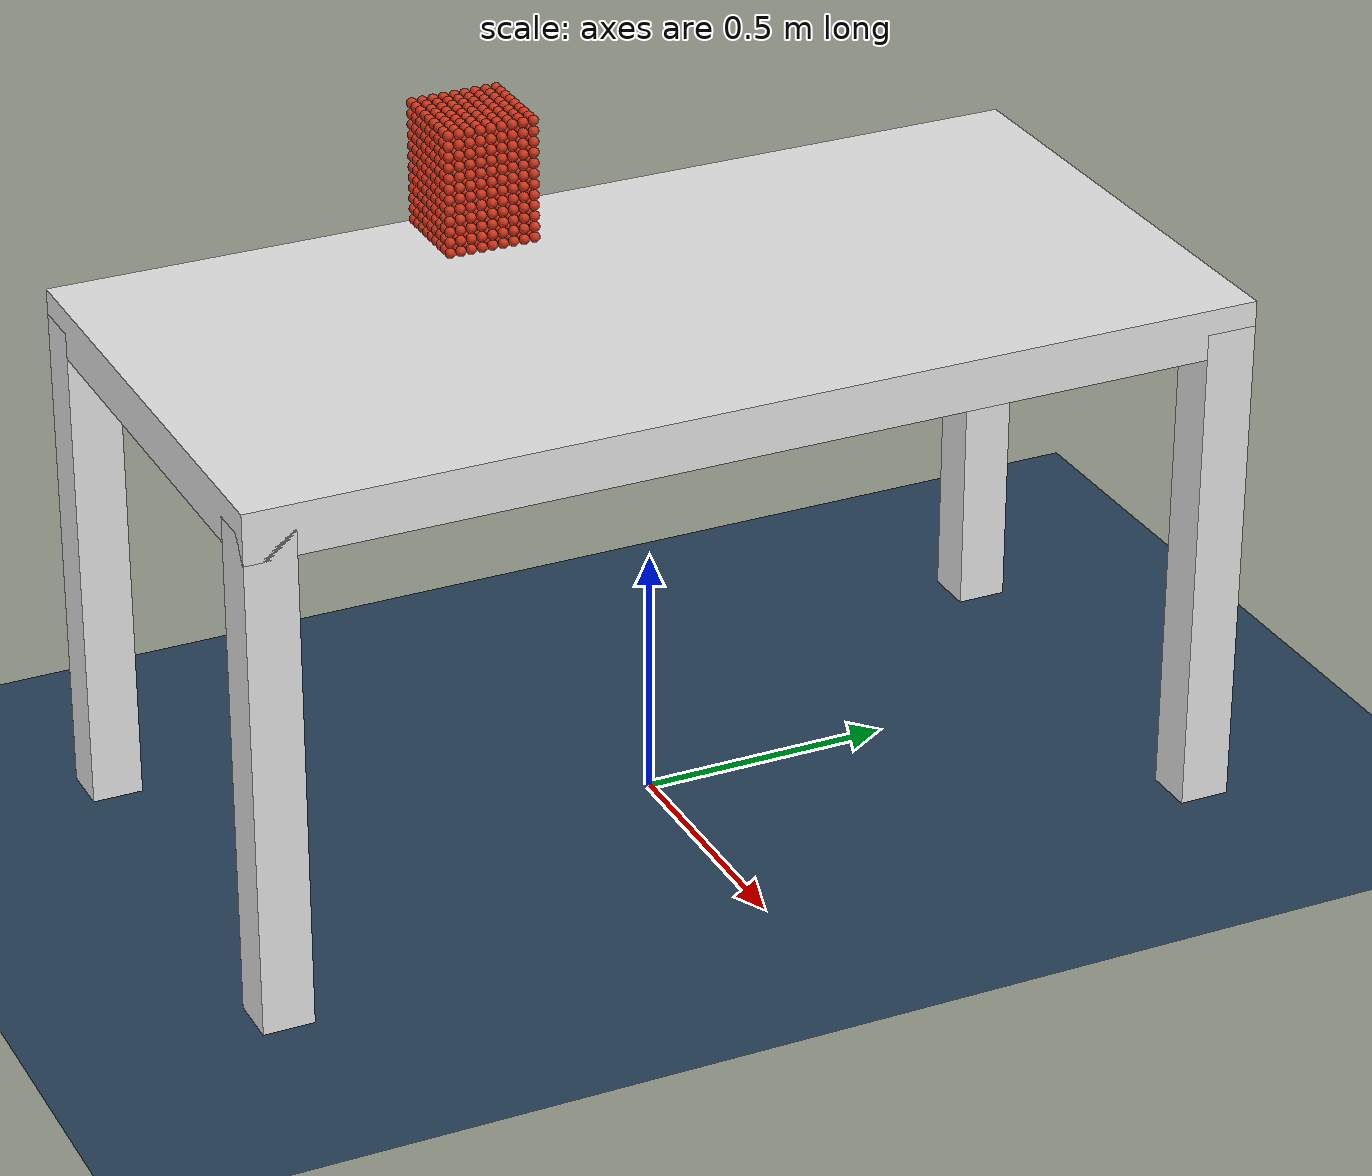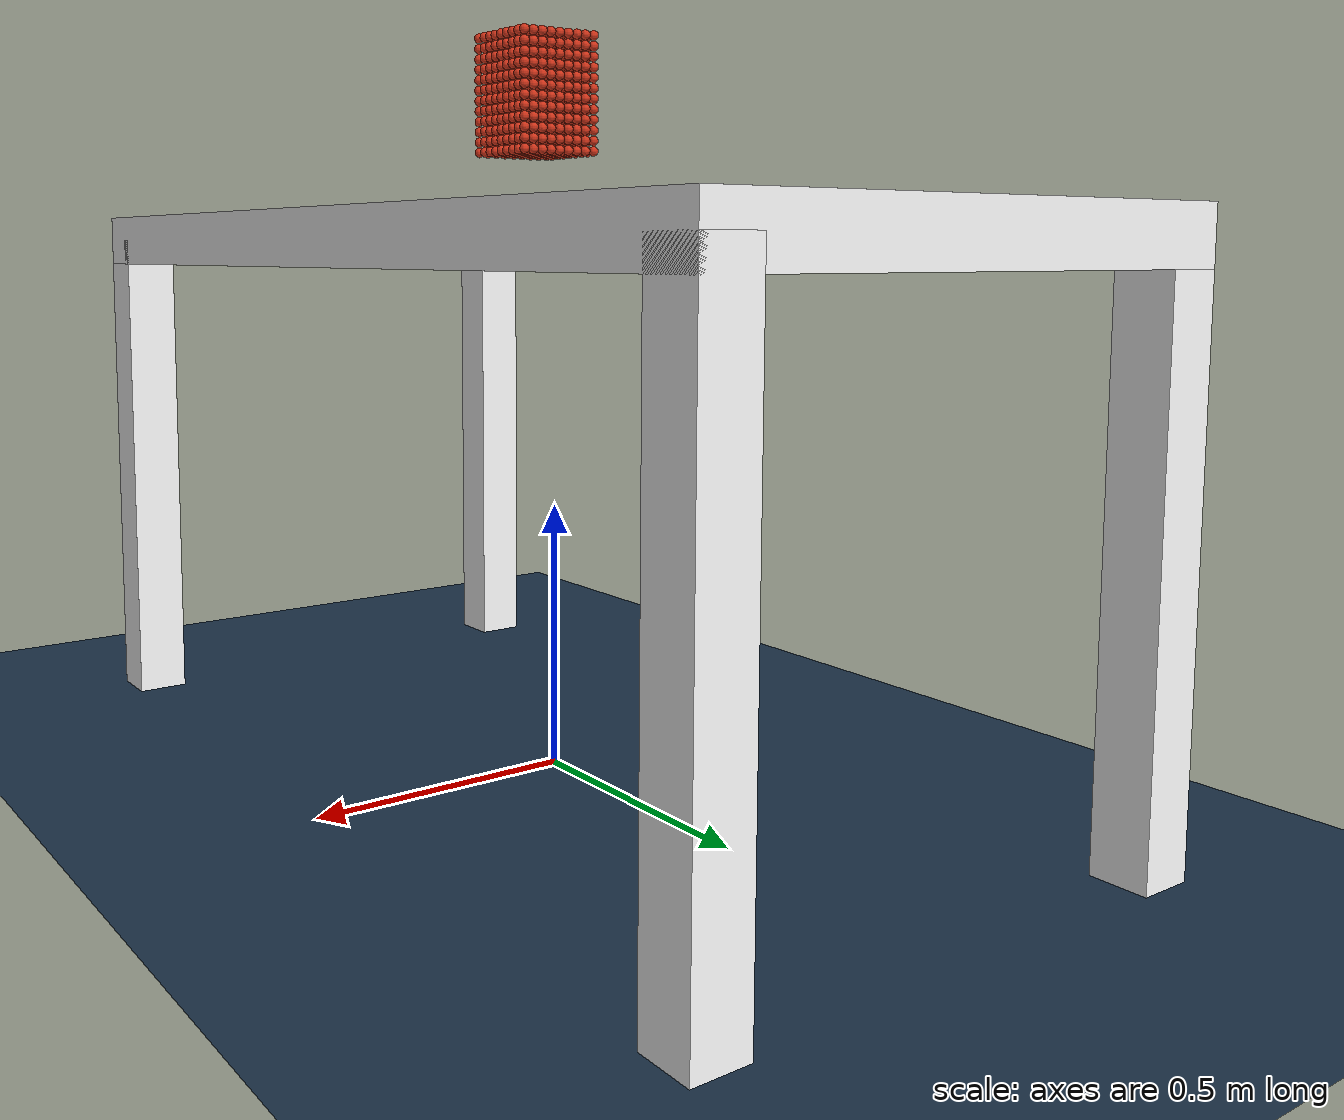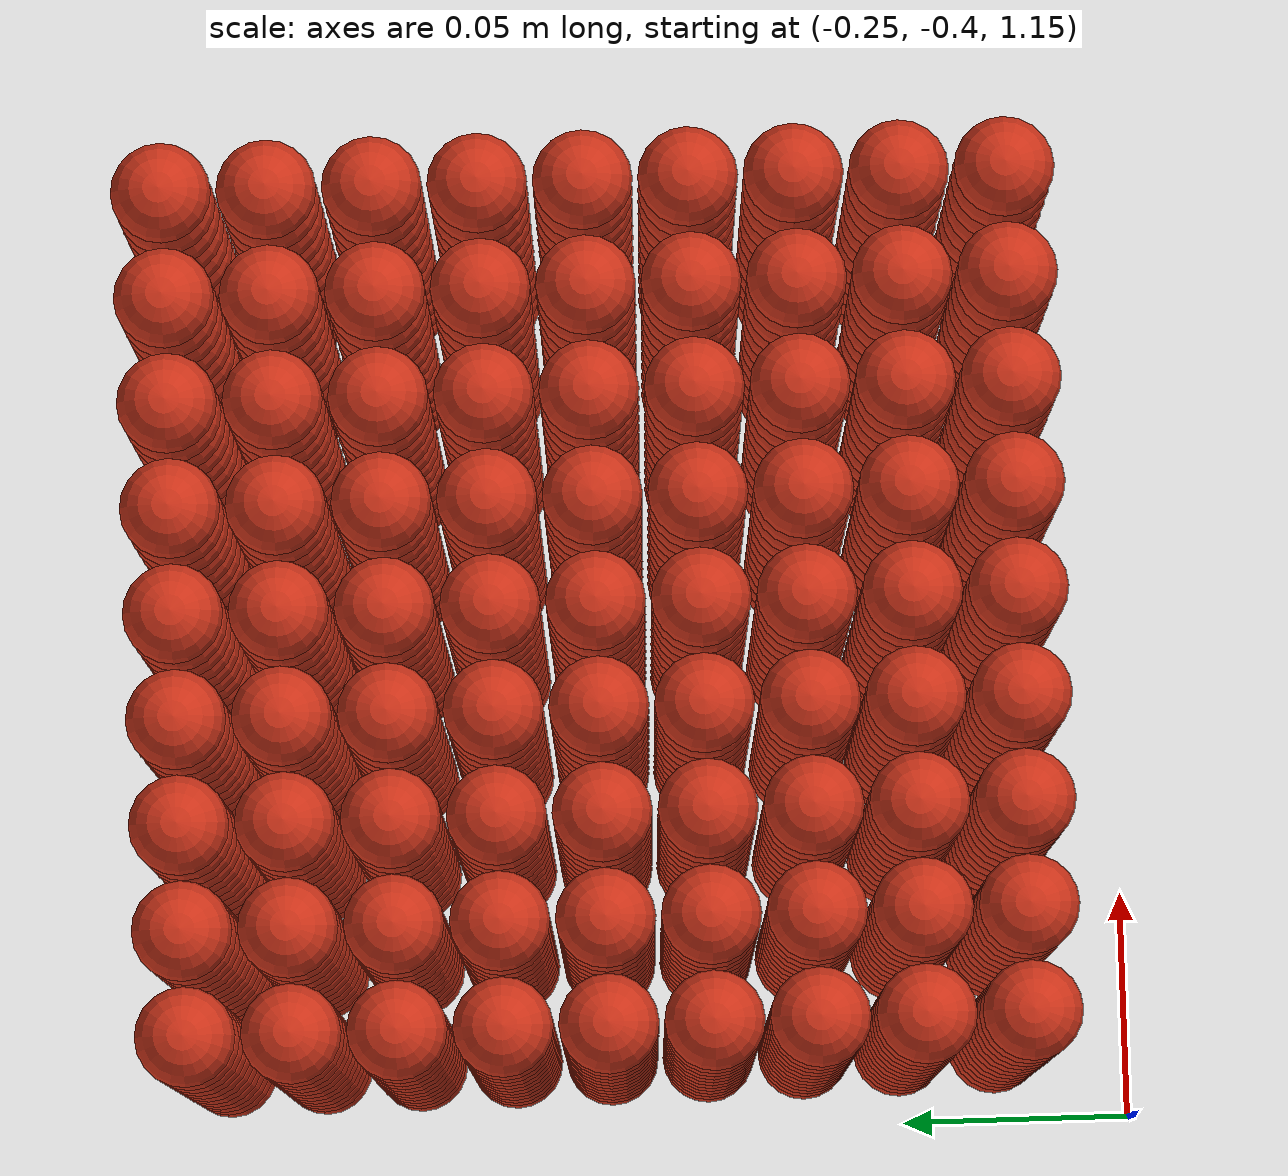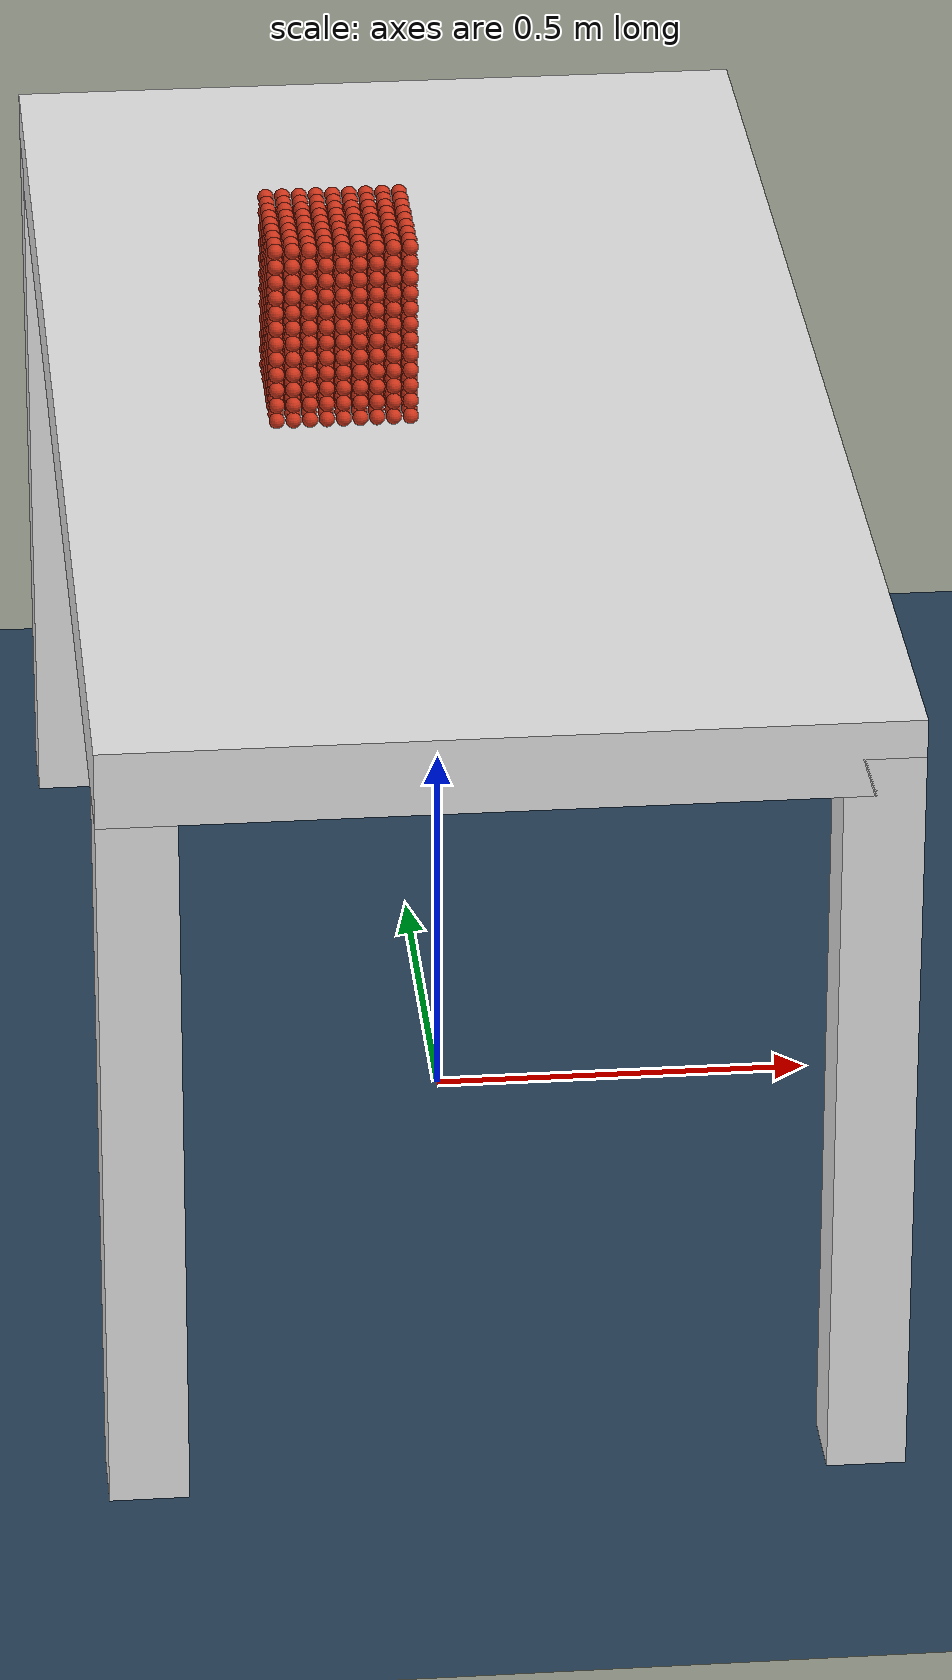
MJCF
<mujoco model="MuJoCo Model">
  <compiler angle="radian"/>
  <option timestep="0.0075" tolerance="1e-06" solver="CG"/>
  <size memory="1G"/>
  <visual>
    <global azimuth="225" elevation="-30"/>
  </visual>
  <default class="main">
    <default class="cooking_body_visual">
      <geom contype="0" conaffinity="0"/>
    </default>
    <default class="cooking_body_collision">
      <geom rgba="0.9 0.9 0.9 1"/>
    </default>
    <default class="indian_gas_stove_visual">
      <geom contype="0" conaffinity="0"/>
    </default>
    <default class="indian_gas_stove_collision">
      <geom rgba="0.9 0.9 0.9 0"/>
    </default>
    <default class="soup_spoon_visual">
      <geom contype="0" conaffinity="0"/>
    </default>
    <default class="soup_spoon_collision">
      <geom rgba="0.9 0.9 0.9 0"/>
    </default>
    <default class="small_bowl_visual">
      <geom contype="0" conaffinity="0"/>
    </default>
    <default class="small_bowl_collision">
      <geom rgba="0.9 0.9 0.9 0"/>
    </default>
  </default>
  <asset>
    <texture type="2d" name="grid" builtin="checker" rgb1="0.1 0.2 0.3" rgb2="0.2 0.3 0.4" width="512" height="512"/>
    <material name="grid" texture="grid" texuniform="true" reflectance="0.2"/>
  </asset>
  <worldbody>
    <geom name="floor" size="0 0 0.05" type="plane" condim="4" friction="2 0.05 0.01" material="grid"/>
    <light pos="0 -1 5" dir="0 0 -1" diffuse="0.5 0.5 0.5"/>
    <light pos="0 1 5" dir="0 0 -1" diffuse="0.5 0.5 0.5"/>
    <body name="table" pos="0 0 1" quat="0.707107 0 0 0.707107">
      <geom size="1 0.5 0.05" type="box" condim="4" friction="2 0.05 0.01" mass="6" rgba="0.9 0.9 0.9 1"/>
      <geom size="0.05 0.05 0.5" pos="0.95 0.45 -0.5" type="box" mass="1" rgba="0.9 0.9 0.9 1"/>
      <geom size="0.05 0.05 0.5" pos="-0.95 0.45 -0.5" type="box" mass="1" rgba="0.9 0.9 0.9 1"/>
      <geom size="0.05 0.05 0.5" pos="0.95 -0.45 -0.5" type="box" mass="1" rgba="0.9 0.9 0.9 1"/>
      <geom size="0.05 0.05 0.5" pos="-0.95 -0.45 -0.5" type="box" mass="1" rgba="0.9 0.9 0.9 1"/>
    </body>
    <body name="cooking_pot_soup" pos="-0.15 -0.28 1.25">
      <body name="B0_0_0" pos="-0.0845 -0.0895 -0.071">
        <joint pos="0 0 0" axis="1 0 0" type="slide" group="3"/>
        <joint pos="0 0 0" axis="0 1 0" type="slide" group="3"/>
        <joint pos="0 0 0" axis="0 0 1" type="slide" group="3"/>
        <geom size="0.01" condim="1" priority="1" rgba="0.8 0.2 0.1 1"/>
        <site name="S0" pos="0 0 0" group="3"/>
      </body>
      <body name="B0_0_1" pos="-0.0845 -0.0895 -0.05">
        <joint pos="0 0 0" axis="1 0 0" type="slide" group="3"/>
        <joint pos="0 0 0" axis="0 1 0" type="slide" group="3"/>
        <joint pos="0 0 0" axis="0 0 1" type="slide" group="3"/>
        <geom size="0.01" condim="1" priority="1" rgba="0.8 0.2 0.1 1"/>
        <site name="S1" pos="0 0 0" group="3"/>
      </body>
      <body name="B0_0_2" pos="-0.0845 -0.0895 -0.029">
        <joint pos="0 0 0" axis="1 0 0" type="slide" group="3"/>
        <joint pos="0 0 0" axis="0 1 0" type="slide" group="3"/>
        <joint pos="0 0 0" axis="0 0 1" type="slide" group="3"/>
        <geom size="0.01" condim="1" priority="1" rgba="0.8 0.2 0.1 1"/>
        <site name="S2" pos="0 0 0" group="3"/>
      </body>
      <body name="B0_0_3" pos="-0.0845 -0.0895 -0.008">
        <joint pos="0 0 0" axis="1 0 0" type="slide" group="3"/>
        <joint pos="0 0 0" axis="0 1 0" type="slide" group="3"/>
        <joint pos="0 0 0" axis="0 0 1" type="slide" group="3"/>
        <geom size="0.01" condim="1" priority="1" rgba="0.8 0.2 0.1 1"/>
        <site name="S3" pos="0 0 0" group="3"/>
      </body>
      <body name="B0_0_4" pos="-0.0845 -0.0895 0.013">
        <joint pos="0 0 0" axis="1 0 0" type="slide" group="3"/>
        <joint pos="0 0 0" axis="0 1 0" type="slide" group="3"/>
        <joint pos="0 0 0" axis="0 0 1" type="slide" group="3"/>
        <geom size="0.01" condim="1" priority="1" rgba="0.8 0.2 0.1 1"/>
        <site name="S4" pos="0 0 0" group="3"/>
      </body>
      <body name="B0_0_5" pos="-0.0845 -0.0895 0.034">
        <joint pos="0 0 0" axis="1 0 0" type="slide" group="3"/>
        <joint pos="0 0 0" axis="0 1 0" type="slide" group="3"/>
        <joint pos="0 0 0" axis="0 0 1" type="slide" group="3"/>
        <geom size="0.01" condim="1" priority="1" rgba="0.8 0.2 0.1 1"/>
        <site name="S5" pos="0 0 0" group="3"/>
      </body>
      <body name="B0_0_6" pos="-0.0845 -0.0895 0.055">
        <joint pos="0 0 0" axis="1 0 0" type="slide" group="3"/>
        <joint pos="0 0 0" axis="0 1 0" type="slide" group="3"/>
        <joint pos="0 0 0" axis="0 0 1" type="slide" group="3"/>
        <geom size="0.01" condim="1" priority="1" rgba="0.8 0.2 0.1 1"/>
        <site name="S6" pos="0 0 0" group="3"/>
      </body>
      <body name="B0_0_7" pos="-0.0845 -0.0895 0.076">
        <joint pos="0 0 0" axis="1 0 0" type="slide" group="3"/>
        <joint pos="0 0 0" axis="0 1 0" type="slide" group="3"/>
        <joint pos="0 0 0" axis="0 0 1" type="slide" group="3"/>
        <geom size="0.01" condim="1" priority="1" rgba="0.8 0.2 0.1 1"/>
        <site name="S7" pos="0 0 0" group="3"/>
      </body>
      <body name="B0_0_8" pos="-0.0845 -0.0895 0.097">
        <joint pos="0 0 0" axis="1 0 0" type="slide" group="3"/>
        <joint pos="0 0 0" axis="0 1 0" type="slide" group="3"/>
        <joint pos="0 0 0" axis="0 0 1" type="slide" group="3"/>
        <geom size="0.01" condim="1" priority="1" rgba="0.8 0.2 0.1 1"/>
        <site name="S8" pos="0 0 0" group="3"/>
      </body>
      <body name="B0_0_9" pos="-0.0845 -0.0895 0.118">
        <joint pos="0 0 0" axis="1 0 0" type="slide" group="3"/>
        <joint pos="0 0 0" axis="0 1 0" type="slide" group="3"/>
        <joint pos="0 0 0" axis="0 0 1" type="slide" group="3"/>
        <geom size="0.01" condim="1" priority="1" rgba="0.8 0.2 0.1 1"/>
        <site name="S9" pos="0 0 0" group="3"/>
      </body>
      <body name="B0_0_10" pos="-0.0845 -0.0895 0.139">
        <joint pos="0 0 0" axis="1 0 0" type="slide" group="3"/>
        <joint pos="0 0 0" axis="0 1 0" type="slide" group="3"/>
        <joint pos="0 0 0" axis="0 0 1" type="slide" group="3"/>
        <geom size="0.01" condim="1" priority="1" rgba="0.8 0.2 0.1 1"/>
        <site name="S10" pos="0 0 0" group="3"/>
      </body>
      <body name="B0_0_11" pos="-0.0845 -0.0895 0.16">
        <joint pos="0 0 0" axis="1 0 0" type="slide" group="3"/>
        <joint pos="0 0 0" axis="0 1 0" type="slide" group="3"/>
        <joint pos="0 0 0" axis="0 0 1" type="slide" group="3"/>
        <geom size="0.01" condim="1" priority="1" rgba="0.8 0.2 0.1 1"/>
        <site name="S11" pos="0 0 0" group="3"/>
      </body>
      <body name="B0_1_0" pos="-0.0845 -0.0685 -0.071">
        <joint pos="0 0 0" axis="1 0 0" type="slide" group="3"/>
        <joint pos="0 0 0" axis="0 1 0" type="slide" group="3"/>
        <joint pos="0 0 0" axis="0 0 1" type="slide" group="3"/>
        <geom size="0.01" condim="1" priority="1" rgba="0.8 0.2 0.1 1"/>
        <site name="S12" pos="0 0 0" group="3"/>
      </body>
      <body name="B0_1_1" pos="-0.0845 -0.0685 -0.05">
        <joint pos="0 0 0" axis="1 0 0" type="slide" group="3"/>
        <joint pos="0 0 0" axis="0 1 0" type="slide" group="3"/>
        <joint pos="0 0 0" axis="0 0 1" type="slide" group="3"/>
        <geom size="0.01" condim="1" priority="1" rgba="0.8 0.2 0.1 1"/>
        <site name="S13" pos="0 0 0" group="3"/>
      </body>
      <body name="B0_1_2" pos="-0.0845 -0.0685 -0.029">
        <joint pos="0 0 0" axis="1 0 0" type="slide" group="3"/>
        <joint pos="0 0 0" axis="0 1 0" type="slide" group="3"/>
        <joint pos="0 0 0" axis="0 0 1" type="slide" group="3"/>
        <geom size="0.01" condim="1" priority="1" rgba="0.8 0.2 0.1 1"/>
        <site name="S14" pos="0 0 0" group="3"/>
      </body>
      <body name="B0_1_3" pos="-0.0845 -0.0685 -0.008">
        <joint pos="0 0 0" axis="1 0 0" type="slide" group="3"/>
        <joint pos="0 0 0" axis="0 1 0" type="slide" group="3"/>
        <joint pos="0 0 0" axis="0 0 1" type="slide" group="3"/>
        <geom size="0.01" condim="1" priority="1" rgba="0.8 0.2 0.1 1"/>
        <site name="S15" pos="0 0 0" group="3"/>
      </body>
      <body name="B0_1_4" pos="-0.0845 -0.0685 0.013">
        <joint pos="0 0 0" axis="1 0 0" type="slide" group="3"/>
        <joint pos="0 0 0" axis="0 1 0" type="slide" group="3"/>
        <joint pos="0 0 0" axis="0 0 1" type="slide" group="3"/>
        <geom size="0.01" condim="1" priority="1" rgba="0.8 0.2 0.1 1"/>
        <site name="S16" pos="0 0 0" group="3"/>
      </body>
      <body name="B0_1_5" pos="-0.0845 -0.0685 0.034">
        <joint pos="0 0 0" axis="1 0 0" type="slide" group="3"/>
        <joint pos="0 0 0" axis="0 1 0" type="slide" group="3"/>
        <joint pos="0 0 0" axis="0 0 1" type="slide" group="3"/>
        <geom size="0.01" condim="1" priority="1" rgba="0.8 0.2 0.1 1"/>
        <site name="S17" pos="0 0 0" group="3"/>
      </body>
      <body name="B0_1_6" pos="-0.0845 -0.0685 0.055">
        <joint pos="0 0 0" axis="1 0 0" type="slide" group="3"/>
        <joint pos="0 0 0" axis="0 1 0" type="slide" group="3"/>
        <joint pos="0 0 0" axis="0 0 1" type="slide" group="3"/>
        <geom size="0.01" condim="1" priority="1" rgba="0.8 0.2 0.1 1"/>
        <site name="S18" pos="0 0 0" group="3"/>
      </body>
      <body name="B0_1_7" pos="-0.0845 -0.0685 0.076">
        <joint pos="0 0 0" axis="1 0 0" type="slide" group="3"/>
        <joint pos="0 0 0" axis="0 1 0" type="slide" group="3"/>
        <joint pos="0 0 0" axis="0 0 1" type="slide" group="3"/>
        <geom size="0.01" condim="1" priority="1" rgba="0.8 0.2 0.1 1"/>
        <site name="S19" pos="0 0 0" group="3"/>
      </body>
      <body name="B0_1_8" pos="-0.0845 -0.0685 0.097">
        <joint pos="0 0 0" axis="1 0 0" type="slide" group="3"/>
        <joint pos="0 0 0" axis="0 1 0" type="slide" group="3"/>
        <joint pos="0 0 0" axis="0 0 1" type="slide" group="3"/>
        <geom size="0.01" condim="1" priority="1" rgba="0.8 0.2 0.1 1"/>
        <site name="S20" pos="0 0 0" group="3"/>
      </body>
      <body name="B0_1_9" pos="-0.0845 -0.0685 0.118">
        <joint pos="0 0 0" axis="1 0 0" type="slide" group="3"/>
        <joint pos="0 0 0" axis="0 1 0" type="slide" group="3"/>
        <joint pos="0 0 0" axis="0 0 1" type="slide" group="3"/>
        <geom size="0.01" condim="1" priority="1" rgba="0.8 0.2 0.1 1"/>
        <site name="S21" pos="0 0 0" group="3"/>
      </body>
      <body name="B0_1_10" pos="-0.0845 -0.0685 0.139">
        <joint pos="0 0 0" axis="1 0 0" type="slide" group="3"/>
        <joint pos="0 0 0" axis="0 1 0" type="slide" group="3"/>
        <joint pos="0 0 0" axis="0 0 1" type="slide" group="3"/>
        <geom size="0.01" condim="1" priority="1" rgba="0.8 0.2 0.1 1"/>
        <site name="S22" pos="0 0 0" group="3"/>
      </body>
      <body name="B0_1_11" pos="-0.0845 -0.0685 0.16">
        <joint pos="0 0 0" axis="1 0 0" type="slide" group="3"/>
        <joint pos="0 0 0" axis="0 1 0" type="slide" group="3"/>
        <joint pos="0 0 0" axis="0 0 1" type="slide" group="3"/>
        <geom size="0.01" condim="1" priority="1" rgba="0.8 0.2 0.1 1"/>
        <site name="S23" pos="0 0 0" group="3"/>
      </body>
      <body name="B0_2_0" pos="-0.0845 -0.0475 -0.071">
        <joint pos="0 0 0" axis="1 0 0" type="slide" group="3"/>
        <joint pos="0 0 0" axis="0 1 0" type="slide" group="3"/>
        <joint pos="0 0 0" axis="0 0 1" type="slide" group="3"/>
        <geom size="0.01" condim="1" priority="1" rgba="0.8 0.2 0.1 1"/>
        <site name="S24" pos="0 0 0" group="3"/>
      </body>
      <body name="B0_2_1" pos="-0.0845 -0.0475 -0.05">
        <joint pos="0 0 0" axis="1 0 0" type="slide" group="3"/>
        <joint pos="0 0 0" axis="0 1 0" type="slide" group="3"/>
        <joint pos="0 0 0" axis="0 0 1" type="slide" group="3"/>
        <geom size="0.01" condim="1" priority="1" rgba="0.8 0.2 0.1 1"/>
        <site name="S25" pos="0 0 0" group="3"/>
      </body>
      <body name="B0_2_2" pos="-0.0845 -0.0475 -0.029">
        <joint pos="0 0 0" axis="1 0 0" type="slide" group="3"/>
        <joint pos="0 0 0" axis="0 1 0" type="slide" group="3"/>
        <joint pos="0 0 0" axis="0 0 1" type="slide" group="3"/>
        <geom size="0.01" condim="1" priority="1" rgba="0.8 0.2 0.1 1"/>
        <site name="S26" pos="0 0 0" group="3"/>
      </body>
      <body name="B0_2_3" pos="-0.0845 -0.0475 -0.008">
        <joint pos="0 0 0" axis="1 0 0" type="slide" group="3"/>
        <joint pos="0 0 0" axis="0 1 0" type="slide" group="3"/>
        <joint pos="0 0 0" axis="0 0 1" type="slide" group="3"/>
        <geom size="0.01" condim="1" priority="1" rgba="0.8 0.2 0.1 1"/>
        <site name="S27" pos="0 0 0" group="3"/>
      </body>
      <body name="B0_2_4" pos="-0.0845 -0.0475 0.013">
        <joint pos="0 0 0" axis="1 0 0" type="slide" group="3"/>
        <joint pos="0 0 0" axis="0 1 0" type="slide" group="3"/>
        <joint pos="0 0 0" axis="0 0 1" type="slide" group="3"/>
        <geom size="0.01" condim="1" priority="1" rgba="0.8 0.2 0.1 1"/>
        <site name="S28" pos="0 0 0" group="3"/>
      </body>
      <body name="B0_2_5" pos="-0.0845 -0.0475 0.034">
        <joint pos="0 0 0" axis="1 0 0" type="slide" group="3"/>
        <joint pos="0 0 0" axis="0 1 0" type="slide" group="3"/>
        <joint pos="0 0 0" axis="0 0 1" type="slide" group="3"/>
        <geom size="0.01" condim="1" priority="1" rgba="0.8 0.2 0.1 1"/>
        <site name="S29" pos="0 0 0" group="3"/>
      </body>
      <body name="B0_2_6" pos="-0.0845 -0.0475 0.055">
        <joint pos="0 0 0" axis="1 0 0" type="slide" group="3"/>
        <joint pos="0 0 0" axis="0 1 0" type="slide" group="3"/>
        <joint pos="0 0 0" axis="0 0 1" type="slide" group="3"/>
        <geom size="0.01" condim="1" priority="1" rgba="0.8 0.2 0.1 1"/>
        <site name="S30" pos="0 0 0" group="3"/>
      </body>
      <body name="B0_2_7" pos="-0.0845 -0.0475 0.076">
        <joint pos="0 0 0" axis="1 0 0" type="slide" group="3"/>
        <joint pos="0 0 0" axis="0 1 0" type="slide" group="3"/>
        <joint pos="0 0 0" axis="0 0 1" type="slide" group="3"/>
        <geom size="0.01" condim="1" priority="1" rgba="0.8 0.2 0.1 1"/>
        <site name="S31" pos="0 0 0" group="3"/>
      </body>
      <body name="B0_2_8" pos="-0.0845 -0.0475 0.097">
        <joint pos="0 0 0" axis="1 0 0" type="slide" group="3"/>
        <joint pos="0 0 0" axis="0 1 0" type="slide" group="3"/>
        <joint pos="0 0 0" axis="0 0 1" type="slide" group="3"/>
        <geom size="0.01" condim="1" priority="1" rgba="0.8 0.2 0.1 1"/>
        <site name="S32" pos="0 0 0" group="3"/>
      </body>
      <body name="B0_2_9" pos="-0.0845 -0.0475 0.118">
        <joint pos="0 0 0" axis="1 0 0" type="slide" group="3"/>
        <joint pos="0 0 0" axis="0 1 0" type="slide" group="3"/>
        <joint pos="0 0 0" axis="0 0 1" type="slide" group="3"/>
        <geom size="0.01" condim="1" priority="1" rgba="0.8 0.2 0.1 1"/>
        <site name="S33" pos="0 0 0" group="3"/>
      </body>
      <body name="B0_2_10" pos="-0.0845 -0.0475 0.139">
        <joint pos="0 0 0" axis="1 0 0" type="slide" group="3"/>
        <joint pos="0 0 0" axis="0 1 0" type="slide" group="3"/>
        <joint pos="0 0 0" axis="0 0 1" type="slide" group="3"/>
        <geom size="0.01" condim="1" priority="1" rgba="0.8 0.2 0.1 1"/>
        <site name="S34" pos="0 0 0" group="3"/>
      </body>
      <body name="B0_2_11" pos="-0.0845 -0.0475 0.16">
        <joint pos="0 0 0" axis="1 0 0" type="slide" group="3"/>
        <joint pos="0 0 0" axis="0 1 0" type="slide" group="3"/>
        <joint pos="0 0 0" axis="0 0 1" type="slide" group="3"/>
        <geom size="0.01" condim="1" priority="1" rgba="0.8 0.2 0.1 1"/>
        <site name="S35" pos="0 0 0" group="3"/>
      </body>
      <body name="B0_3_0" pos="-0.0845 -0.0265 -0.071">
        <joint pos="0 0 0" axis="1 0 0" type="slide" group="3"/>
        <joint pos="0 0 0" axis="0 1 0" type="slide" group="3"/>
        <joint pos="0 0 0" axis="0 0 1" type="slide" group="3"/>
        <geom size="0.01" condim="1" priority="1" rgba="0.8 0.2 0.1 1"/>
        <site name="S36" pos="0 0 0" group="3"/>
      </body>
      <body name="B0_3_1" pos="-0.0845 -0.0265 -0.05">
        <joint pos="0 0 0" axis="1 0 0" type="slide" group="3"/>
        <joint pos="0 0 0" axis="0 1 0" type="slide" group="3"/>
        <joint pos="0 0 0" axis="0 0 1" type="slide" group="3"/>
        <geom size="0.01" condim="1" priority="1" rgba="0.8 0.2 0.1 1"/>
        <site name="S37" pos="0 0 0" group="3"/>
      </body>
      <body name="B0_3_2" pos="-0.0845 -0.0265 -0.029">
        <joint pos="0 0 0" axis="1 0 0" type="slide" group="3"/>
        <joint pos="0 0 0" axis="0 1 0" type="slide" group="3"/>
        <joint pos="0 0 0" axis="0 0 1" type="slide" group="3"/>
        <geom size="0.01" condim="1" priority="1" rgba="0.8 0.2 0.1 1"/>
        <site name="S38" pos="0 0 0" group="3"/>
      </body>
      <body name="B0_3_3" pos="-0.0845 -0.0265 -0.008">
        <joint pos="0 0 0" axis="1 0 0" type="slide" group="3"/>
        <joint pos="0 0 0" axis="0 1 0" type="slide" group="3"/>
        <joint pos="0 0 0" axis="0 0 1" type="slide" group="3"/>
        <geom size="0.01" condim="1" priority="1" rgba="0.8 0.2 0.1 1"/>
        <site name="S39" pos="0 0 0" group="3"/>
      </body>
      <body name="B0_3_4" pos="-0.0845 -0.0265 0.013">
        <joint pos="0 0 0" axis="1 0 0" type="slide" group="3"/>
        <joint pos="0 0 0" axis="0 1 0" type="slide" group="3"/>
        <joint pos="0 0 0" axis="0 0 1" type="slide" group="3"/>
        <geom size="0.01" condim="1" priority="1" rgba="0.8 0.2 0.1 1"/>
        <site name="S40" pos="0 0 0" group="3"/>
      </body>
      <body name="B0_3_5" pos="-0.0845 -0.0265 0.034">
        <joint pos="0 0 0" axis="1 0 0" type="slide" group="3"/>
        <joint pos="0 0 0" axis="0 1 0" type="slide" group="3"/>
        <joint pos="0 0 0" axis="0 0 1" type="slide" group="3"/>
        <geom size="0.01" condim="1" priority="1" rgba="0.8 0.2 0.1 1"/>
        <site name="S41" pos="0 0 0" group="3"/>
      </body>
      <body name="B0_3_6" pos="-0.0845 -0.0265 0.055">
        <joint pos="0 0 0" axis="1 0 0" type="slide" group="3"/>
        <joint pos="0 0 0" axis="0 1 0" type="slide" group="3"/>
        <joint pos="0 0 0" axis="0 0 1" type="slide" group="3"/>
        <geom size="0.01" condim="1" priority="1" rgba="0.8 0.2 0.1 1"/>
        <site name="S42" pos="0 0 0" group="3"/>
      </body>
      <body name="B0_3_7" pos="-0.0845 -0.0265 0.076">
        <joint pos="0 0 0" axis="1 0 0" type="slide" group="3"/>
        <joint pos="0 0 0" axis="0 1 0" type="slide" group="3"/>
        <joint pos="0 0 0" axis="0 0 1" type="slide" group="3"/>
        <geom size="0.01" condim="1" priority="1" rgba="0.8 0.2 0.1 1"/>
        <site name="S43" pos="0 0 0" group="3"/>
      </body>
      <body name="B0_3_8" pos="-0.0845 -0.0265 0.097">
        <joint pos="0 0 0" axis="1 0 0" type="slide" group="3"/>
        <joint pos="0 0 0" axis="0 1 0" type="slide" group="3"/>
        <joint pos="0 0 0" axis="0 0 1" type="slide" group="3"/>
        <geom size="0.01" condim="1" priority="1" rgba="0.8 0.2 0.1 1"/>
        <site name="S44" pos="0 0 0" group="3"/>
      </body>
      <body name="B0_3_9" pos="-0.0845 -0.0265 0.118">
        <joint pos="0 0 0" axis="1 0 0" type="slide" group="3"/>
        <joint pos="0 0 0" axis="0 1 0" type="slide" group="3"/>
        <joint pos="0 0 0" axis="0 0 1" type="slide" group="3"/>
        <geom size="0.01" condim="1" priority="1" rgba="0.8 0.2 0.1 1"/>
        <site name="S45" pos="0 0 0" group="3"/>
      </body>
      <body name="B0_3_10" pos="-0.0845 -0.0265 0.139">
        <joint pos="0 0 0" axis="1 0 0" type="slide" group="3"/>
        <joint pos="0 0 0" axis="0 1 0" type="slide" group="3"/>
        <joint pos="0 0 0" axis="0 0 1" type="slide" group="3"/>
        <geom size="0.01" condim="1" priority="1" rgba="0.8 0.2 0.1 1"/>
        <site name="S46" pos="0 0 0" group="3"/>
      </body>
      <body name="B0_3_11" pos="-0.0845 -0.0265 0.16">
        <joint pos="0 0 0" axis="1 0 0" type="slide" group="3"/>
        <joint pos="0 0 0" axis="0 1 0" type="slide" group="3"/>
        <joint pos="0 0 0" axis="0 0 1" type="slide" group="3"/>
        <geom size="0.01" condim="1" priority="1" rgba="0.8 0.2 0.1 1"/>
        <site name="S47" pos="0 0 0" group="3"/>
      </body>
      <body name="B0_4_0" pos="-0.0845 -0.0055 -0.071">
        <joint pos="0 0 0" axis="1 0 0" type="slide" group="3"/>
        <joint pos="0 0 0" axis="0 1 0" type="slide" group="3"/>
        <joint pos="0 0 0" axis="0 0 1" type="slide" group="3"/>
        <geom size="0.01" condim="1" priority="1" rgba="0.8 0.2 0.1 1"/>
        <site name="S48" pos="0 0 0" group="3"/>
      </body>
      <body name="B0_4_1" pos="-0.0845 -0.0055 -0.05">
        <joint pos="0 0 0" axis="1 0 0" type="slide" group="3"/>
        <joint pos="0 0 0" axis="0 1 0" type="slide" group="3"/>
        <joint pos="0 0 0" axis="0 0 1" type="slide" group="3"/>
        <geom size="0.01" condim="1" priority="1" rgba="0.8 0.2 0.1 1"/>
        <site name="S49" pos="0 0 0" group="3"/>
      </body>
      <body name="B0_4_2" pos="-0.0845 -0.0055 -0.029">
        <joint pos="0 0 0" axis="1 0 0" type="slide" group="3"/>
        <joint pos="0 0 0" axis="0 1 0" type="slide" group="3"/>
        <joint pos="0 0 0" axis="0 0 1" type="slide" group="3"/>
        <geom size="0.01" condim="1" priority="1" rgba="0.8 0.2 0.1 1"/>
        <site name="S50" pos="0 0 0" group="3"/>
      </body>
      <body name="B0_4_3" pos="-0.0845 -0.0055 -0.008">
        <joint pos="0 0 0" axis="1 0 0" type="slide" group="3"/>
        <joint pos="0 0 0" axis="0 1 0" type="slide" group="3"/>
        <joint pos="0 0 0" axis="0 0 1" type="slide" group="3"/>
        <geom size="0.01" condim="1" priority="1" rgba="0.8 0.2 0.1 1"/>
        <site name="S51" pos="0 0 0" group="3"/>
      </body>
      <body name="B0_4_4" pos="-0.0845 -0.0055 0.013">
        <joint pos="0 0 0" axis="1 0 0" type="slide" group="3"/>
        <joint pos="0 0 0" axis="0 1 0" type="slide" group="3"/>
        <joint pos="0 0 0" axis="0 0 1" type="slide" group="3"/>
        <geom size="0.01" condim="1" priority="1" rgba="0.8 0.2 0.1 1"/>
        <site name="S52" pos="0 0 0" group="3"/>
      </body>
      <body name="B0_4_5" pos="-0.0845 -0.0055 0.034">
        <joint pos="0 0 0" axis="1 0 0" type="slide" group="3"/>
        <joint pos="0 0 0" axis="0 1 0" type="slide" group="3"/>
        <joint pos="0 0 0" axis="0 0 1" type="slide" group="3"/>
        <geom size="0.01" condim="1" priority="1" rgba="0.8 0.2 0.1 1"/>
        <site name="S53" pos="0 0 0" group="3"/>
      </body>
      <body name="B0_4_6" pos="-0.0845 -0.0055 0.055">
        <joint pos="0 0 0" axis="1 0 0" type="slide" group="3"/>
        <joint pos="0 0 0" axis="0 1 0" type="slide" group="3"/>
        <joint pos="0 0 0" axis="0 0 1" type="slide" group="3"/>
        <geom size="0.01" condim="1" priority="1" rgba="0.8 0.2 0.1 1"/>
        <site name="S54" pos="0 0 0" group="3"/>
      </body>
      <body name="B0_4_7" pos="-0.0845 -0.0055 0.076">
        <joint pos="0 0 0" axis="1 0 0" type="slide" group="3"/>
        <joint pos="0 0 0" axis="0 1 0" type="slide" group="3"/>
        <joint pos="0 0 0" axis="0 0 1" type="slide" group="3"/>
        <geom size="0.01" condim="1" priority="1" rgba="0.8 0.2 0.1 1"/>
        <site name="S55" pos="0 0 0" group="3"/>
      </body>
      <body name="B0_4_8" pos="-0.0845 -0.0055 0.097">
        <joint pos="0 0 0" axis="1 0 0" type="slide" group="3"/>
        <joint pos="0 0 0" axis="0 1 0" type="slide" group="3"/>
        <joint pos="0 0 0" axis="0 0 1" type="slide" group="3"/>
        <geom size="0.01" condim="1" priority="1" rgba="0.8 0.2 0.1 1"/>
        <site name="S56" pos="0 0 0" group="3"/>
      </body>
      <body name="B0_4_9" pos="-0.0845 -0.0055 0.118">
        <joint pos="0 0 0" axis="1 0 0" type="slide" group="3"/>
        <joint pos="0 0 0" axis="0 1 0" type="slide" group="3"/>
        <joint pos="0 0 0" axis="0 0 1" type="slide" group="3"/>
        <geom size="0.01" condim="1" priority="1" rgba="0.8 0.2 0.1 1"/>
        <site name="S57" pos="0 0 0" group="3"/>
      </body>
      <body name="B0_4_10" pos="-0.0845 -0.0055 0.139">
        <joint pos="0 0 0" axis="1 0 0" type="slide" group="3"/>
        <joint pos="0 0 0" axis="0 1 0" type="slide" group="3"/>
        <joint pos="0 0 0" axis="0 0 1" type="slide" group="3"/>
        <geom size="0.01" condim="1" priority="1" rgba="0.8 0.2 0.1 1"/>
        <site name="S58" pos="0 0 0" group="3"/>
      </body>
      <body name="B0_4_11" pos="-0.0845 -0.0055 0.16">
        <joint pos="0 0 0" axis="1 0 0" type="slide" group="3"/>
        <joint pos="0 0 0" axis="0 1 0" type="slide" group="3"/>
        <joint pos="0 0 0" axis="0 0 1" type="slide" group="3"/>
        <geom size="0.01" condim="1" priority="1" rgba="0.8 0.2 0.1 1"/>
        <site name="S59" pos="0 0 0" group="3"/>
      </body>
      <body name="B0_5_0" pos="-0.0845 0.0155 -0.071">
        <joint pos="0 0 0" axis="1 0 0" type="slide" group="3"/>
        <joint pos="0 0 0" axis="0 1 0" type="slide" group="3"/>
        <joint pos="0 0 0" axis="0 0 1" type="slide" group="3"/>
        <geom size="0.01" condim="1" priority="1" rgba="0.8 0.2 0.1 1"/>
        <site name="S60" pos="0 0 0" group="3"/>
      </body>
      <body name="B0_5_1" pos="-0.0845 0.0155 -0.05">
        <joint pos="0 0 0" axis="1 0 0" type="slide" group="3"/>
        <joint pos="0 0 0" axis="0 1 0" type="slide" group="3"/>
        <joint pos="0 0 0" axis="0 0 1" type="slide" group="3"/>
        <geom size="0.01" condim="1" priority="1" rgba="0.8 0.2 0.1 1"/>
        <site name="S61" pos="0 0 0" group="3"/>
      </body>
      <body name="B0_5_2" pos="-0.0845 0.0155 -0.029">
        <joint pos="0 0 0" axis="1 0 0" type="slide" group="3"/>
        <joint pos="0 0 0" axis="0 1 0" type="slide" group="3"/>
        <joint pos="0 0 0" axis="0 0 1" type="slide" group="3"/>
        <geom size="0.01" condim="1" priority="1" rgba="0.8 0.2 0.1 1"/>
        <site name="S62" pos="0 0 0" group="3"/>
      </body>
      <body name="B0_5_3" pos="-0.0845 0.0155 -0.008">
        <joint pos="0 0 0" axis="1 0 0" type="slide" group="3"/>
        <joint pos="0 0 0" axis="0 1 0" type="slide" group="3"/>
        <joint pos="0 0 0" axis="0 0 1" type="slide" group="3"/>
        <geom size="0.01" condim="1" priority="1" rgba="0.8 0.2 0.1 1"/>
        <site name="S63" pos="0 0 0" group="3"/>
      </body>
      <body name="B0_5_4" pos="-0.0845 0.0155 0.013">
        <joint pos="0 0 0" axis="1 0 0" type="slide" group="3"/>
        <joint pos="0 0 0" axis="0 1 0" type="slide" group="3"/>
        <joint pos="0 0 0" axis="0 0 1" type="slide" group="3"/>
        <geom size="0.01" condim="1" priority="1" rgba="0.8 0.2 0.1 1"/>
        <site name="S64" pos="0 0 0" group="3"/>
      </body>
      <body name="B0_5_5" pos="-0.0845 0.0155 0.034">
        <joint pos="0 0 0" axis="1 0 0" type="slide" group="3"/>
        <joint pos="0 0 0" axis="0 1 0" type="slide" group="3"/>
        <joint pos="0 0 0" axis="0 0 1" type="slide" group="3"/>
        <geom size="0.01" condim="1" priority="1" rgba="0.8 0.2 0.1 1"/>
        <site name="S65" pos="0 0 0" group="3"/>
      </body>
      <body name="B0_5_6" pos="-0.0845 0.0155 0.055">
        <joint pos="0 0 0" axis="1 0 0" type="slide" group="3"/>
        <joint pos="0 0 0" axis="0 1 0" type="slide" group="3"/>
        <joint pos="0 0 0" axis="0 0 1" type="slide" group="3"/>
        <geom size="0.01" condim="1" priority="1" rgba="0.8 0.2 0.1 1"/>
        <site name="S66" pos="0 0 0" group="3"/>
      </body>
      <body name="B0_5_7" pos="-0.0845 0.0155 0.076">
        <joint pos="0 0 0" axis="1 0 0" type="slide" group="3"/>
        <joint pos="0 0 0" axis="0 1 0" type="slide" group="3"/>
        <joint pos="0 0 0" axis="0 0 1" type="slide" group="3"/>
        <geom size="0.01" condim="1" priority="1" rgba="0.8 0.2 0.1 1"/>
        <site name="S67" pos="0 0 0" group="3"/>
      </body>
      <body name="B0_5_8" pos="-0.0845 0.0155 0.097">
        <joint pos="0 0 0" axis="1 0 0" type="slide" group="3"/>
        <joint pos="0 0 0" axis="0 1 0" type="slide" group="3"/>
        <joint pos="0 0 0" axis="0 0 1" type="slide" group="3"/>
        <geom size="0.01" condim="1" priority="1" rgba="0.8 0.2 0.1 1"/>
        <site name="S68" pos="0 0 0" group="3"/>
      </body>
      <body name="B0_5_9" pos="-0.0845 0.0155 0.118">
        <joint pos="0 0 0" axis="1 0 0" type="slide" group="3"/>
        <joint pos="0 0 0" axis="0 1 0" type="slide" group="3"/>
        <joint pos="0 0 0" axis="0 0 1" type="slide" group="3"/>
        <geom size="0.01" condim="1" priority="1" rgba="0.8 0.2 0.1 1"/>
        <site name="S69" pos="0 0 0" group="3"/>
      </body>
      <body name="B0_5_10" pos="-0.0845 0.0155 0.139">
        <joint pos="0 0 0" axis="1 0 0" type="slide" group="3"/>
        <joint pos="0 0 0" axis="0 1 0" type="slide" group="3"/>
        <joint pos="0 0 0" axis="0 0 1" type="slide" group="3"/>
        <geom size="0.01" condim="1" priority="1" rgba="0.8 0.2 0.1 1"/>
        <site name="S70" pos="0 0 0" group="3"/>
      </body>
      <body name="B0_5_11" pos="-0.0845 0.0155 0.16">
        <joint pos="0 0 0" axis="1 0 0" type="slide" group="3"/>
        <joint pos="0 0 0" axis="0 1 0" type="slide" group="3"/>
        <joint pos="0 0 0" axis="0 0 1" type="slide" group="3"/>
        <geom size="0.01" condim="1" priority="1" rgba="0.8 0.2 0.1 1"/>
        <site name="S71" pos="0 0 0" group="3"/>
      </body>
      <body name="B0_6_0" pos="-0.0845 0.0365 -0.071">
        <joint pos="0 0 0" axis="1 0 0" type="slide" group="3"/>
        <joint pos="0 0 0" axis="0 1 0" type="slide" group="3"/>
        <joint pos="0 0 0" axis="0 0 1" type="slide" group="3"/>
        <geom size="0.01" condim="1" priority="1" rgba="0.8 0.2 0.1 1"/>
        <site name="S72" pos="0 0 0" group="3"/>
      </body>
      <body name="B0_6_1" pos="-0.0845 0.0365 -0.05">
        <joint pos="0 0 0" axis="1 0 0" type="slide" group="3"/>
        <joint pos="0 0 0" axis="0 1 0" type="slide" group="3"/>
        <joint pos="0 0 0" axis="0 0 1" type="slide" group="3"/>
        <geom size="0.01" condim="1" priority="1" rgba="0.8 0.2 0.1 1"/>
        <site name="S73" pos="0 0 0" group="3"/>
      </body>
      <body name="B0_6_2" pos="-0.0845 0.0365 -0.029">
        <joint pos="0 0 0" axis="1 0 0" type="slide" group="3"/>
        <joint pos="0 0 0" axis="0 1 0" type="slide" group="3"/>
        <joint pos="0 0 0" axis="0 0 1" type="slide" group="3"/>
        <geom size="0.01" condim="1" priority="1" rgba="0.8 0.2 0.1 1"/>
        <site name="S74" pos="0 0 0" group="3"/>
      </body>
      <body name="B0_6_3" pos="-0.0845 0.0365 -0.008">
        <joint pos="0 0 0" axis="1 0 0" type="slide" group="3"/>
        <joint pos="0 0 0" axis="0 1 0" type="slide" group="3"/>
        <joint pos="0 0 0" axis="0 0 1" type="slide" group="3"/>
        <geom size="0.01" condim="1" priority="1" rgba="0.8 0.2 0.1 1"/>
        <site name="S75" pos="0 0 0" group="3"/>
      </body>
      <body name="B0_6_4" pos="-0.0845 0.0365 0.013">
        <joint pos="0 0 0" axis="1 0 0" type="slide" group="3"/>
        <joint pos="0 0 0" axis="0 1 0" type="slide" group="3"/>
        <joint pos="0 0 0" axis="0 0 1" type="slide" group="3"/>
        <geom size="0.01" condim="1" priority="1" rgba="0.8 0.2 0.1 1"/>
        <site name="S76" pos="0 0 0" group="3"/>
      </body>
      <body name="B0_6_5" pos="-0.0845 0.0365 0.034">
        <joint pos="0 0 0" axis="1 0 0" type="slide" group="3"/>
        <joint pos="0 0 0" axis="0 1 0" type="slide" group="3"/>
        <joint pos="0 0 0" axis="0 0 1" type="slide" group="3"/>
        <geom size="0.01" condim="1" priority="1" rgba="0.8 0.2 0.1 1"/>
        <site name="S77" pos="0 0 0" group="3"/>
      </body>
      <body name="B0_6_6" pos="-0.0845 0.0365 0.055">
        <joint pos="0 0 0" axis="1 0 0" type="slide" group="3"/>
        <joint pos="0 0 0" axis="0 1 0" type="slide" group="3"/>
        <joint pos="0 0 0" axis="0 0 1" type="slide" group="3"/>
        <geom size="0.01" condim="1" priority="1" rgba="0.8 0.2 0.1 1"/>
        <site name="S78" pos="0 0 0" group="3"/>
      </body>
      <body name="B0_6_7" pos="-0.0845 0.0365 0.076">
        <joint pos="0 0 0" axis="1 0 0" type="slide" group="3"/>
        <joint pos="0 0 0" axis="0 1 0" type="slide" group="3"/>
        <joint pos="0 0 0" axis="0 0 1" type="slide" group="3"/>
        <geom size="0.01" condim="1" priority="1" rgba="0.8 0.2 0.1 1"/>
        <site name="S79" pos="0 0 0" group="3"/>
      </body>
      <body name="B0_6_8" pos="-0.0845 0.0365 0.097">
        <joint pos="0 0 0" axis="1 0 0" type="slide" group="3"/>
        <joint pos="0 0 0" axis="0 1 0" type="slide" group="3"/>
        <joint pos="0 0 0" axis="0 0 1" type="slide" group="3"/>
        <geom size="0.01" condim="1" priority="1" rgba="0.8 0.2 0.1 1"/>
        <site name="S80" pos="0 0 0" group="3"/>
      </body>
      <body name="B0_6_9" pos="-0.0845 0.0365 0.118">
        <joint pos="0 0 0" axis="1 0 0" type="slide" group="3"/>
        <joint pos="0 0 0" axis="0 1 0" type="slide" group="3"/>
        <joint pos="0 0 0" axis="0 0 1" type="slide" group="3"/>
        <geom size="0.01" condim="1" priority="1" rgba="0.8 0.2 0.1 1"/>
        <site name="S81" pos="0 0 0" group="3"/>
      </body>
      <body name="B0_6_10" pos="-0.0845 0.0365 0.139">
        <joint pos="0 0 0" axis="1 0 0" type="slide" group="3"/>
        <joint pos="0 0 0" axis="0 1 0" type="slide" group="3"/>
        <joint pos="0 0 0" axis="0 0 1" type="slide" group="3"/>
        <geom size="0.01" condim="1" priority="1" rgba="0.8 0.2 0.1 1"/>
        <site name="S82" pos="0 0 0" group="3"/>
      </body>
      <body name="B0_6_11" pos="-0.0845 0.0365 0.16">
        <joint pos="0 0 0" axis="1 0 0" type="slide" group="3"/>
        <joint pos="0 0 0" axis="0 1 0" type="slide" group="3"/>
        <joint pos="0 0 0" axis="0 0 1" type="slide" group="3"/>
        <geom size="0.01" condim="1" priority="1" rgba="0.8 0.2 0.1 1"/>
        <site name="S83" pos="0 0 0" group="3"/>
      </body>
      <body name="B0_7_0" pos="-0.0845 0.0575 -0.071">
        <joint pos="0 0 0" axis="1 0 0" type="slide" group="3"/>
        <joint pos="0 0 0" axis="0 1 0" type="slide" group="3"/>
        <joint pos="0 0 0" axis="0 0 1" type="slide" group="3"/>
        <geom size="0.01" condim="1" priority="1" rgba="0.8 0.2 0.1 1"/>
        <site name="S84" pos="0 0 0" group="3"/>
      </body>
      <body name="B0_7_1" pos="-0.0845 0.0575 -0.05">
        <joint pos="0 0 0" axis="1 0 0" type="slide" group="3"/>
        <joint pos="0 0 0" axis="0 1 0" type="slide" group="3"/>
        <joint pos="0 0 0" axis="0 0 1" type="slide" group="3"/>
        <geom size="0.01" condim="1" priority="1" rgba="0.8 0.2 0.1 1"/>
        <site name="S85" pos="0 0 0" group="3"/>
      </body>
      <body name="B0_7_2" pos="-0.0845 0.0575 -0.029">
        <joint pos="0 0 0" axis="1 0 0" type="slide" group="3"/>
        <joint pos="0 0 0" axis="0 1 0" type="slide" group="3"/>
        <joint pos="0 0 0" axis="0 0 1" type="slide" group="3"/>
        <geom size="0.01" condim="1" priority="1" rgba="0.8 0.2 0.1 1"/>
        <site name="S86" pos="0 0 0" group="3"/>
      </body>
      <body name="B0_7_3" pos="-0.0845 0.0575 -0.008">
        <joint pos="0 0 0" axis="1 0 0" type="slide" group="3"/>
        <joint pos="0 0 0" axis="0 1 0" type="slide" group="3"/>
        <joint pos="0 0 0" axis="0 0 1" type="slide" group="3"/>
        <geom size="0.01" condim="1" priority="1" rgba="0.8 0.2 0.1 1"/>
        <site name="S87" pos="0 0 0" group="3"/>
      </body>
      <body name="B0_7_4" pos="-0.0845 0.0575 0.013">
        <joint pos="0 0 0" axis="1 0 0" type="slide" group="3"/>
        <joint pos="0 0 0" axis="0 1 0" type="slide" group="3"/>
        <joint pos="0 0 0" axis="0 0 1" type="slide" group="3"/>
        <geom size="0.01" condim="1" priority="1" rgba="0.8 0.2 0.1 1"/>
        <site name="S88" pos="0 0 0" group="3"/>
      </body>
      <body name="B0_7_5" pos="-0.0845 0.0575 0.034">
        <joint pos="0 0 0" axis="1 0 0" type="slide" group="3"/>
        <joint pos="0 0 0" axis="0 1 0" type="slide" group="3"/>
        <joint pos="0 0 0" axis="0 0 1" type="slide" group="3"/>
        <geom size="0.01" condim="1" priority="1" rgba="0.8 0.2 0.1 1"/>
        <site name="S89" pos="0 0 0" group="3"/>
      </body>
      <body name="B0_7_6" pos="-0.0845 0.0575 0.055">
        <joint pos="0 0 0" axis="1 0 0" type="slide" group="3"/>
        <joint pos="0 0 0" axis="0 1 0" type="slide" group="3"/>
        <joint pos="0 0 0" axis="0 0 1" type="slide" group="3"/>
        <geom size="0.01" condim="1" priority="1" rgba="0.8 0.2 0.1 1"/>
        <site name="S90" pos="0 0 0" group="3"/>
      </body>
      <body name="B0_7_7" pos="-0.0845 0.0575 0.076">
        <joint pos="0 0 0" axis="1 0 0" type="slide" group="3"/>
        <joint pos="0 0 0" axis="0 1 0" type="slide" group="3"/>
        <joint pos="0 0 0" axis="0 0 1" type="slide" group="3"/>
        <geom size="0.01" condim="1" priority="1" rgba="0.8 0.2 0.1 1"/>
        <site name="S91" pos="0 0 0" group="3"/>
      </body>
      <body name="B0_7_8" pos="-0.0845 0.0575 0.097">
        <joint pos="0 0 0" axis="1 0 0" type="slide" group="3"/>
        <joint pos="0 0 0" axis="0 1 0" type="slide" group="3"/>
        <joint pos="0 0 0" axis="0 0 1" type="slide" group="3"/>
        <geom size="0.01" condim="1" priority="1" rgba="0.8 0.2 0.1 1"/>
        <site name="S92" pos="0 0 0" group="3"/>
      </body>
      <body name="B0_7_9" pos="-0.0845 0.0575 0.118">
        <joint pos="0 0 0" axis="1 0 0" type="slide" group="3"/>
        <joint pos="0 0 0" axis="0 1 0" type="slide" group="3"/>
        <joint pos="0 0 0" axis="0 0 1" type="slide" group="3"/>
        <geom size="0.01" condim="1" priority="1" rgba="0.8 0.2 0.1 1"/>
        <site name="S93" pos="0 0 0" group="3"/>
      </body>
      <body name="B0_7_10" pos="-0.0845 0.0575 0.139">
        <joint pos="0 0 0" axis="1 0 0" type="slide" group="3"/>
        <joint pos="0 0 0" axis="0 1 0" type="slide" group="3"/>
        <joint pos="0 0 0" axis="0 0 1" type="slide" group="3"/>
        <geom size="0.01" condim="1" priority="1" rgba="0.8 0.2 0.1 1"/>
        <site name="S94" pos="0 0 0" group="3"/>
      </body>
      <body name="B0_7_11" pos="-0.0845 0.0575 0.16">
        <joint pos="0 0 0" axis="1 0 0" type="slide" group="3"/>
        <joint pos="0 0 0" axis="0 1 0" type="slide" group="3"/>
        <joint pos="0 0 0" axis="0 0 1" type="slide" group="3"/>
        <geom size="0.01" condim="1" priority="1" rgba="0.8 0.2 0.1 1"/>
        <site name="S95" pos="0 0 0" group="3"/>
      </body>
      <body name="B0_8_0" pos="-0.0845 0.0785 -0.071">
        <joint pos="0 0 0" axis="1 0 0" type="slide" group="3"/>
        <joint pos="0 0 0" axis="0 1 0" type="slide" group="3"/>
        <joint pos="0 0 0" axis="0 0 1" type="slide" group="3"/>
        <geom size="0.01" condim="1" priority="1" rgba="0.8 0.2 0.1 1"/>
        <site name="S96" pos="0 0 0" group="3"/>
      </body>
      <body name="B0_8_1" pos="-0.0845 0.0785 -0.05">
        <joint pos="0 0 0" axis="1 0 0" type="slide" group="3"/>
        <joint pos="0 0 0" axis="0 1 0" type="slide" group="3"/>
        <joint pos="0 0 0" axis="0 0 1" type="slide" group="3"/>
        <geom size="0.01" condim="1" priority="1" rgba="0.8 0.2 0.1 1"/>
        <site name="S97" pos="0 0 0" group="3"/>
      </body>
      <body name="B0_8_2" pos="-0.0845 0.0785 -0.029">
        <joint pos="0 0 0" axis="1 0 0" type="slide" group="3"/>
        <joint pos="0 0 0" axis="0 1 0" type="slide" group="3"/>
        <joint pos="0 0 0" axis="0 0 1" type="slide" group="3"/>
        <geom size="0.01" condim="1" priority="1" rgba="0.8 0.2 0.1 1"/>
        <site name="S98" pos="0 0 0" group="3"/>
      </body>
      <body name="B0_8_3" pos="-0.0845 0.0785 -0.008">
        <joint pos="0 0 0" axis="1 0 0" type="slide" group="3"/>
        <joint pos="0 0 0" axis="0 1 0" type="slide" group="3"/>
        <joint pos="0 0 0" axis="0 0 1" type="slide" group="3"/>
        <geom size="0.01" condim="1" priority="1" rgba="0.8 0.2 0.1 1"/>
        <site name="S99" pos="0 0 0" group="3"/>
      </body>
      <body name="B0_8_4" pos="-0.0845 0.0785 0.013">
        <joint pos="0 0 0" axis="1 0 0" type="slide" group="3"/>
        <joint pos="0 0 0" axis="0 1 0" type="slide" group="3"/>
        <joint pos="0 0 0" axis="0 0 1" type="slide" group="3"/>
        <geom size="0.01" condim="1" priority="1" rgba="0.8 0.2 0.1 1"/>
        <site name="S100" pos="0 0 0" group="3"/>
      </body>
      <body name="B0_8_5" pos="-0.0845 0.0785 0.034">
        <joint pos="0 0 0" axis="1 0 0" type="slide" group="3"/>
        <joint pos="0 0 0" axis="0 1 0" type="slide" group="3"/>
        <joint pos="0 0 0" axis="0 0 1" type="slide" group="3"/>
        <geom size="0.01" condim="1" priority="1" rgba="0.8 0.2 0.1 1"/>
        <site name="S101" pos="0 0 0" group="3"/>
      </body>
      <body name="B0_8_6" pos="-0.0845 0.0785 0.055">
        <joint pos="0 0 0" axis="1 0 0" type="slide" group="3"/>
        <joint pos="0 0 0" axis="0 1 0" type="slide" group="3"/>
        <joint pos="0 0 0" axis="0 0 1" type="slide" group="3"/>
        <geom size="0.01" condim="1" priority="1" rgba="0.8 0.2 0.1 1"/>
        <site name="S102" pos="0 0 0" group="3"/>
      </body>
      <body name="B0_8_7" pos="-0.0845 0.0785 0.076">
        <joint pos="0 0 0" axis="1 0 0" type="slide" group="3"/>
        <joint pos="0 0 0" axis="0 1 0" type="slide" group="3"/>
        <joint pos="0 0 0" axis="0 0 1" type="slide" group="3"/>
        <geom size="0.01" condim="1" priority="1" rgba="0.8 0.2 0.1 1"/>
        <site name="S103" pos="0 0 0" group="3"/>
      </body>
      <body name="B0_8_8" pos="-0.0845 0.0785 0.097">
        <joint pos="0 0 0" axis="1 0 0" type="slide" group="3"/>
        <joint pos="0 0 0" axis="0 1 0" type="slide" group="3"/>
        <joint pos="0 0 0" axis="0 0 1" type="slide" group="3"/>
        <geom size="0.01" condim="1" priority="1" rgba="0.8 0.2 0.1 1"/>
        <site name="S104" pos="0 0 0" group="3"/>
      </body>
      <body name="B0_8_9" pos="-0.0845 0.0785 0.118">
        <joint pos="0 0 0" axis="1 0 0" type="slide" group="3"/>
        <joint pos="0 0 0" axis="0 1 0" type="slide" group="3"/>
        <joint pos="0 0 0" axis="0 0 1" type="slide" group="3"/>
        <geom size="0.01" condim="1" priority="1" rgba="0.8 0.2 0.1 1"/>
        <site name="S105" pos="0 0 0" group="3"/>
      </body>
      <body name="B0_8_10" pos="-0.0845 0.0785 0.139">
        <joint pos="0 0 0" axis="1 0 0" type="slide" group="3"/>
        <joint pos="0 0 0" axis="0 1 0" type="slide" group="3"/>
        <joint pos="0 0 0" axis="0 0 1" type="slide" group="3"/>
        <geom size="0.01" condim="1" priority="1" rgba="0.8 0.2 0.1 1"/>
        <site name="S106" pos="0 0 0" group="3"/>
      </body>
      <body name="B0_8_11" pos="-0.0845 0.0785 0.16">
        <joint pos="0 0 0" axis="1 0 0" type="slide" group="3"/>
        <joint pos="0 0 0" axis="0 1 0" type="slide" group="3"/>
        <joint pos="0 0 0" axis="0 0 1" type="slide" group="3"/>
        <geom size="0.01" condim="1" priority="1" rgba="0.8 0.2 0.1 1"/>
        <site name="S107" pos="0 0 0" group="3"/>
      </body>
      <body name="B1_0_0" pos="-0.0635 -0.0895 -0.071">
        <joint pos="0 0 0" axis="1 0 0" type="slide" group="3"/>
        <joint pos="0 0 0" axis="0 1 0" type="slide" group="3"/>
        <joint pos="0 0 0" axis="0 0 1" type="slide" group="3"/>
        <geom size="0.01" condim="1" priority="1" rgba="0.8 0.2 0.1 1"/>
        <site name="S108" pos="0 0 0" group="3"/>
      </body>
      <body name="B1_0_1" pos="-0.0635 -0.0895 -0.05">
        <joint pos="0 0 0" axis="1 0 0" type="slide" group="3"/>
        <joint pos="0 0 0" axis="0 1 0" type="slide" group="3"/>
        <joint pos="0 0 0" axis="0 0 1" type="slide" group="3"/>
        <geom size="0.01" condim="1" priority="1" rgba="0.8 0.2 0.1 1"/>
        <site name="S109" pos="0 0 0" group="3"/>
      </body>
      <body name="B1_0_2" pos="-0.0635 -0.0895 -0.029">
        <joint pos="0 0 0" axis="1 0 0" type="slide" group="3"/>
        <joint pos="0 0 0" axis="0 1 0" type="slide" group="3"/>
        <joint pos="0 0 0" axis="0 0 1" type="slide" group="3"/>
        <geom size="0.01" condim="1" priority="1" rgba="0.8 0.2 0.1 1"/>
        <site name="S110" pos="0 0 0" group="3"/>
      </body>
      <body name="B1_0_3" pos="-0.0635 -0.0895 -0.008">
        <joint pos="0 0 0" axis="1 0 0" type="slide" group="3"/>
        <joint pos="0 0 0" axis="0 1 0" type="slide" group="3"/>
        <joint pos="0 0 0" axis="0 0 1" type="slide" group="3"/>
        <geom size="0.01" condim="1" priority="1" rgba="0.8 0.2 0.1 1"/>
        <site name="S111" pos="0 0 0" group="3"/>
      </body>
      <body name="B1_0_4" pos="-0.0635 -0.0895 0.013">
        <joint pos="0 0 0" axis="1 0 0" type="slide" group="3"/>
        <joint pos="0 0 0" axis="0 1 0" type="slide" group="3"/>
        <joint pos="0 0 0" axis="0 0 1" type="slide" group="3"/>
        <geom size="0.01" condim="1" priority="1" rgba="0.8 0.2 0.1 1"/>
        <site name="S112" pos="0 0 0" group="3"/>
      </body>
      <body name="B1_0_5" pos="-0.0635 -0.0895 0.034">
        <joint pos="0 0 0" axis="1 0 0" type="slide" group="3"/>
        <joint pos="0 0 0" axis="0 1 0" type="slide" group="3"/>
        <joint pos="0 0 0" axis="0 0 1" type="slide" group="3"/>
        <geom size="0.01" condim="1" priority="1" rgba="0.8 0.2 0.1 1"/>
        <site name="S113" pos="0 0 0" group="3"/>
      </body>
      <body name="B1_0_6" pos="-0.0635 -0.0895 0.055">
        <joint pos="0 0 0" axis="1 0 0" type="slide" group="3"/>
        <joint pos="0 0 0" axis="0 1 0" type="slide" group="3"/>
        <joint pos="0 0 0" axis="0 0 1" type="slide" group="3"/>
        <geom size="0.01" condim="1" priority="1" rgba="0.8 0.2 0.1 1"/>
        <site name="S114" pos="0 0 0" group="3"/>
      </body>
      <body name="B1_0_7" pos="-0.0635 -0.0895 0.076">
        <joint pos="0 0 0" axis="1 0 0" type="slide" group="3"/>
        <joint pos="0 0 0" axis="0 1 0" type="slide" group="3"/>
        <joint pos="0 0 0" axis="0 0 1" type="slide" group="3"/>
        <geom size="0.01" condim="1" priority="1" rgba="0.8 0.2 0.1 1"/>
        <site name="S115" pos="0 0 0" group="3"/>
      </body>
      <body name="B1_0_8" pos="-0.0635 -0.0895 0.097">
        <joint pos="0 0 0" axis="1 0 0" type="slide" group="3"/>
        <joint pos="0 0 0" axis="0 1 0" type="slide" group="3"/>
        <joint pos="0 0 0" axis="0 0 1" type="slide" group="3"/>
        <geom size="0.01" condim="1" priority="1" rgba="0.8 0.2 0.1 1"/>
        <site name="S116" pos="0 0 0" group="3"/>
      </body>
      <body name="B1_0_9" pos="-0.0635 -0.0895 0.118">
        <joint pos="0 0 0" axis="1 0 0" type="slide" group="3"/>
        <joint pos="0 0 0" axis="0 1 0" type="slide" group="3"/>
        <joint pos="0 0 0" axis="0 0 1" type="slide" group="3"/>
        <geom size="0.01" condim="1" priority="1" rgba="0.8 0.2 0.1 1"/>
        <site name="S117" pos="0 0 0" group="3"/>
      </body>
      <body name="B1_0_10" pos="-0.0635 -0.0895 0.139">
        <joint pos="0 0 0" axis="1 0 0" type="slide" group="3"/>
        <joint pos="0 0 0" axis="0 1 0" type="slide" group="3"/>
        <joint pos="0 0 0" axis="0 0 1" type="slide" group="3"/>
        <geom size="0.01" condim="1" priority="1" rgba="0.8 0.2 0.1 1"/>
        <site name="S118" pos="0 0 0" group="3"/>
      </body>
      <body name="B1_0_11" pos="-0.0635 -0.0895 0.16">
        <joint pos="0 0 0" axis="1 0 0" type="slide" group="3"/>
        <joint pos="0 0 0" axis="0 1 0" type="slide" group="3"/>
        <joint pos="0 0 0" axis="0 0 1" type="slide" group="3"/>
        <geom size="0.01" condim="1" priority="1" rgba="0.8 0.2 0.1 1"/>
        <site name="S119" pos="0 0 0" group="3"/>
      </body>
      <body name="B1_1_0" pos="-0.0635 -0.0685 -0.071">
        <joint pos="0 0 0" axis="1 0 0" type="slide" group="3"/>
        <joint pos="0 0 0" axis="0 1 0" type="slide" group="3"/>
        <joint pos="0 0 0" axis="0 0 1" type="slide" group="3"/>
        <geom size="0.01" condim="1" priority="1" rgba="0.8 0.2 0.1 1"/>
        <site name="S120" pos="0 0 0" group="3"/>
      </body>
      <body name="B1_1_1" pos="-0.0635 -0.0685 -0.05">
        <joint pos="0 0 0" axis="1 0 0" type="slide" group="3"/>
        <joint pos="0 0 0" axis="0 1 0" type="slide" group="3"/>
        <joint pos="0 0 0" axis="0 0 1" type="slide" group="3"/>
        <geom size="0.01" condim="1" priority="1" rgba="0.8 0.2 0.1 1"/>
        <site name="S121" pos="0 0 0" group="3"/>
      </body>
      <body name="B1_1_2" pos="-0.0635 -0.0685 -0.029">
        <joint pos="0 0 0" axis="1 0 0" type="slide" group="3"/>
        <joint pos="0 0 0" axis="0 1 0" type="slide" group="3"/>
        <joint pos="0 0 0" axis="0 0 1" type="slide" group="3"/>
        <geom size="0.01" condim="1" priority="1" rgba="0.8 0.2 0.1 1"/>
        <site name="S122" pos="0 0 0" group="3"/>
      </body>
      <body name="B1_1_3" pos="-0.0635 -0.0685 -0.008">
        <joint pos="0 0 0" axis="1 0 0" type="slide" group="3"/>
        <joint pos="0 0 0" axis="0 1 0" type="slide" group="3"/>
        <joint pos="0 0 0" axis="0 0 1" type="slide" group="3"/>
        <geom size="0.01" condim="1" priority="1" rgba="0.8 0.2 0.1 1"/>
        <site name="S123" pos="0 0 0" group="3"/>
      </body>
      <body name="B1_1_4" pos="-0.0635 -0.0685 0.013">
        <joint pos="0 0 0" axis="1 0 0" type="slide" group="3"/>
        <joint pos="0 0 0" axis="0 1 0" type="slide" group="3"/>
        <joint pos="0 0 0" axis="0 0 1" type="slide" group="3"/>
        <geom size="0.01" condim="1" priority="1" rgba="0.8 0.2 0.1 1"/>
        <site name="S124" pos="0 0 0" group="3"/>
      </body>
      <body name="B1_1_5" pos="-0.0635 -0.0685 0.034">
        <joint pos="0 0 0" axis="1 0 0" type="slide" group="3"/>
        <joint pos="0 0 0" axis="0 1 0" type="slide" group="3"/>
        <joint pos="0 0 0" axis="0 0 1" type="slide" group="3"/>
        <geom size="0.01" condim="1" priority="1" rgba="0.8 0.2 0.1 1"/>
        <site name="S125" pos="0 0 0" group="3"/>
      </body>
      <body name="B1_1_6" pos="-0.0635 -0.0685 0.055">
        <joint pos="0 0 0" axis="1 0 0" type="slide" group="3"/>
        <joint pos="0 0 0" axis="0 1 0" type="slide" group="3"/>
        <joint pos="0 0 0" axis="0 0 1" type="slide" group="3"/>
        <geom size="0.01" condim="1" priority="1" rgba="0.8 0.2 0.1 1"/>
        <site name="S126" pos="0 0 0" group="3"/>
      </body>
      <body name="B1_1_7" pos="-0.0635 -0.0685 0.076">
        <joint pos="0 0 0" axis="1 0 0" type="slide" group="3"/>
        <joint pos="0 0 0" axis="0 1 0" type="slide" group="3"/>
        <joint pos="0 0 0" axis="0 0 1" type="slide" group="3"/>
        <geom size="0.01" condim="1" priority="1" rgba="0.8 0.2 0.1 1"/>
        <site name="S127" pos="0 0 0" group="3"/>
      </body>
      <body name="B1_1_8" pos="-0.0635 -0.0685 0.097">
        <joint pos="0 0 0" axis="1 0 0" type="slide" group="3"/>
        <joint pos="0 0 0" axis="0 1 0" type="slide" group="3"/>
        <joint pos="0 0 0" axis="0 0 1" type="slide" group="3"/>
        <geom size="0.01" condim="1" priority="1" rgba="0.8 0.2 0.1 1"/>
        <site name="S128" pos="0 0 0" group="3"/>
      </body>
      <body name="B1_1_9" pos="-0.0635 -0.0685 0.118">
        <joint pos="0 0 0" axis="1 0 0" type="slide" group="3"/>
        <joint pos="0 0 0" axis="0 1 0" type="slide" group="3"/>
        <joint pos="0 0 0" axis="0 0 1" type="slide" group="3"/>
        <geom size="0.01" condim="1" priority="1" rgba="0.8 0.2 0.1 1"/>
        <site name="S129" pos="0 0 0" group="3"/>
      </body>
      <body name="B1_1_10" pos="-0.0635 -0.0685 0.139">
        <joint pos="0 0 0" axis="1 0 0" type="slide" group="3"/>
        <joint pos="0 0 0" axis="0 1 0" type="slide" group="3"/>
        <joint pos="0 0 0" axis="0 0 1" type="slide" group="3"/>
        <geom size="0.01" condim="1" priority="1" rgba="0.8 0.2 0.1 1"/>
        <site name="S130" pos="0 0 0" group="3"/>
      </body>
      <body name="B1_1_11" pos="-0.0635 -0.0685 0.16">
        <joint pos="0 0 0" axis="1 0 0" type="slide" group="3"/>
        <joint pos="0 0 0" axis="0 1 0" type="slide" group="3"/>
        <joint pos="0 0 0" axis="0 0 1" type="slide" group="3"/>
        <geom size="0.01" condim="1" priority="1" rgba="0.8 0.2 0.1 1"/>
        <site name="S131" pos="0 0 0" group="3"/>
      </body>
      <body name="B1_2_0" pos="-0.0635 -0.0475 -0.071">
        <joint pos="0 0 0" axis="1 0 0" type="slide" group="3"/>
        <joint pos="0 0 0" axis="0 1 0" type="slide" group="3"/>
        <joint pos="0 0 0" axis="0 0 1" type="slide" group="3"/>
        <geom size="0.01" condim="1" priority="1" rgba="0.8 0.2 0.1 1"/>
        <site name="S132" pos="0 0 0" group="3"/>
      </body>
      <body name="B1_2_1" pos="-0.0635 -0.0475 -0.05">
        <joint pos="0 0 0" axis="1 0 0" type="slide" group="3"/>
        <joint pos="0 0 0" axis="0 1 0" type="slide" group="3"/>
        <joint pos="0 0 0" axis="0 0 1" type="slide" group="3"/>
        <geom size="0.01" condim="1" priority="1" rgba="0.8 0.2 0.1 1"/>
        <site name="S133" pos="0 0 0" group="3"/>
      </body>
      <body name="B1_2_2" pos="-0.0635 -0.0475 -0.029">
        <joint pos="0 0 0" axis="1 0 0" type="slide" group="3"/>
        <joint pos="0 0 0" axis="0 1 0" type="slide" group="3"/>
        <joint pos="0 0 0" axis="0 0 1" type="slide" group="3"/>
        <geom size="0.01" condim="1" priority="1" rgba="0.8 0.2 0.1 1"/>
        <site name="S134" pos="0 0 0" group="3"/>
      </body>
      <body name="B1_2_3" pos="-0.0635 -0.0475 -0.008">
        <joint pos="0 0 0" axis="1 0 0" type="slide" group="3"/>
        <joint pos="0 0 0" axis="0 1 0" type="slide" group="3"/>
        <joint pos="0 0 0" axis="0 0 1" type="slide" group="3"/>
        <geom size="0.01" condim="1" priority="1" rgba="0.8 0.2 0.1 1"/>
        <site name="S135" pos="0 0 0" group="3"/>
      </body>
      <body name="B1_2_4" pos="-0.0635 -0.0475 0.013">
        <joint pos="0 0 0" axis="1 0 0" type="slide" group="3"/>
        <joint pos="0 0 0" axis="0 1 0" type="slide" group="3"/>
        <joint pos="0 0 0" axis="0 0 1" type="slide" group="3"/>
        <geom size="0.01" condim="1" priority="1" rgba="0.8 0.2 0.1 1"/>
        <site name="S136" pos="0 0 0" group="3"/>
      </body>
      <body name="B1_2_5" pos="-0.0635 -0.0475 0.034">
        <joint pos="0 0 0" axis="1 0 0" type="slide" group="3"/>
        <joint pos="0 0 0" axis="0 1 0" type="slide" group="3"/>
        <joint pos="0 0 0" axis="0 0 1" type="slide" group="3"/>
        <geom size="0.01" condim="1" priority="1" rgba="0.8 0.2 0.1 1"/>
        <site name="S137" pos="0 0 0" group="3"/>
      </body>
      <body name="B1_2_6" pos="-0.0635 -0.0475 0.055">
        <joint pos="0 0 0" axis="1 0 0" type="slide" group="3"/>
        <joint pos="0 0 0" axis="0 1 0" type="slide" group="3"/>
        <joint pos="0 0 0" axis="0 0 1" type="slide" group="3"/>
        <geom size="0.01" condim="1" priority="1" rgba="0.8 0.2 0.1 1"/>
        <site name="S138" pos="0 0 0" group="3"/>
      </body>
      <body name="B1_2_7" pos="-0.0635 -0.0475 0.076">
        <joint pos="0 0 0" axis="1 0 0" type="slide" group="3"/>
        <joint pos="0 0 0" axis="0 1 0" type="slide" group="3"/>
        <joint pos="0 0 0" axis="0 0 1" type="slide" group="3"/>
        <geom size="0.01" condim="1" priority="1" rgba="0.8 0.2 0.1 1"/>
        <site name="S139" pos="0 0 0" group="3"/>
      </body>
      <body name="B1_2_8" pos="-0.0635 -0.0475 0.097">
        <joint pos="0 0 0" axis="1 0 0" type="slide" group="3"/>
        <joint pos="0 0 0" axis="0 1 0" type="slide" group="3"/>
        <joint pos="0 0 0" axis="0 0 1" type="slide" group="3"/>
        <geom size="0.01" condim="1" priority="1" rgba="0.8 0.2 0.1 1"/>
        <site name="S140" pos="0 0 0" group="3"/>
      </body>
      <body name="B1_2_9" pos="-0.0635 -0.0475 0.118">
        <joint pos="0 0 0" axis="1 0 0" type="slide" group="3"/>
        <joint pos="0 0 0" axis="0 1 0" type="slide" group="3"/>
        <joint pos="0 0 0" axis="0 0 1" type="slide" group="3"/>
        <geom size="0.01" condim="1" priority="1" rgba="0.8 0.2 0.1 1"/>
        <site name="S141" pos="0 0 0" group="3"/>
      </body>
      <body name="B1_2_10" pos="-0.0635 -0.0475 0.139">
        <joint pos="0 0 0" axis="1 0 0" type="slide" group="3"/>
        <joint pos="0 0 0" axis="0 1 0" type="slide" group="3"/>
        <joint pos="0 0 0" axis="0 0 1" type="slide" group="3"/>
        <geom size="0.01" condim="1" priority="1" rgba="0.8 0.2 0.1 1"/>
        <site name="S142" pos="0 0 0" group="3"/>
      </body>
      <body name="B1_2_11" pos="-0.0635 -0.0475 0.16">
        <joint pos="0 0 0" axis="1 0 0" type="slide" group="3"/>
        <joint pos="0 0 0" axis="0 1 0" type="slide" group="3"/>
        <joint pos="0 0 0" axis="0 0 1" type="slide" group="3"/>
        <geom size="0.01" condim="1" priority="1" rgba="0.8 0.2 0.1 1"/>
        <site name="S143" pos="0 0 0" group="3"/>
      </body>
      <body name="B1_3_0" pos="-0.0635 -0.0265 -0.071">
        <joint pos="0 0 0" axis="1 0 0" type="slide" group="3"/>
        <joint pos="0 0 0" axis="0 1 0" type="slide" group="3"/>
        <joint pos="0 0 0" axis="0 0 1" type="slide" group="3"/>
        <geom size="0.01" condim="1" priority="1" rgba="0.8 0.2 0.1 1"/>
        <site name="S144" pos="0 0 0" group="3"/>
      </body>
      <body name="B1_3_1" pos="-0.0635 -0.0265 -0.05">
        <joint pos="0 0 0" axis="1 0 0" type="slide" group="3"/>
        <joint pos="0 0 0" axis="0 1 0" type="slide" group="3"/>
        <joint pos="0 0 0" axis="0 0 1" type="slide" group="3"/>
        <geom size="0.01" condim="1" priority="1" rgba="0.8 0.2 0.1 1"/>
        <site name="S145" pos="0 0 0" group="3"/>
      </body>
      <body name="B1_3_2" pos="-0.0635 -0.0265 -0.029">
        <joint pos="0 0 0" axis="1 0 0" type="slide" group="3"/>
        <joint pos="0 0 0" axis="0 1 0" type="slide" group="3"/>
        <joint pos="0 0 0" axis="0 0 1" type="slide" group="3"/>
        <geom size="0.01" condim="1" priority="1" rgba="0.8 0.2 0.1 1"/>
        <site name="S146" pos="0 0 0" group="3"/>
      </body>
      <body name="B1_3_3" pos="-0.0635 -0.0265 -0.008">
        <joint pos="0 0 0" axis="1 0 0" type="slide" group="3"/>
        <joint pos="0 0 0" axis="0 1 0" type="slide" group="3"/>
        <joint pos="0 0 0" axis="0 0 1" type="slide" group="3"/>
        <geom size="0.01" condim="1" priority="1" rgba="0.8 0.2 0.1 1"/>
        <site name="S147" pos="0 0 0" group="3"/>
      </body>
      <body name="B1_3_4" pos="-0.0635 -0.0265 0.013">
        <joint pos="0 0 0" axis="1 0 0" type="slide" group="3"/>
        <joint pos="0 0 0" axis="0 1 0" type="slide" group="3"/>
        <joint pos="0 0 0" axis="0 0 1" type="slide" group="3"/>
        <geom size="0.01" condim="1" priority="1" rgba="0.8 0.2 0.1 1"/>
        <site name="S148" pos="0 0 0" group="3"/>
      </body>
      <body name="B1_3_5" pos="-0.0635 -0.0265 0.034">
        <joint pos="0 0 0" axis="1 0 0" type="slide" group="3"/>
        <joint pos="0 0 0" axis="0 1 0" type="slide" group="3"/>
        <joint pos="0 0 0" axis="0 0 1" type="slide" group="3"/>
        <geom size="0.01" condim="1" priority="1" rgba="0.8 0.2 0.1 1"/>
        <site name="S149" pos="0 0 0" group="3"/>
      </body>
      <body name="B1_3_6" pos="-0.0635 -0.0265 0.055">
        <joint pos="0 0 0" axis="1 0 0" type="slide" group="3"/>
        <joint pos="0 0 0" axis="0 1 0" type="slide" group="3"/>
        <joint pos="0 0 0" axis="0 0 1" type="slide" group="3"/>
        <geom size="0.01" condim="1" priority="1" rgba="0.8 0.2 0.1 1"/>
        <site name="S150" pos="0 0 0" group="3"/>
      </body>
      <body name="B1_3_7" pos="-0.0635 -0.0265 0.076">
        <joint pos="0 0 0" axis="1 0 0" type="slide" group="3"/>
        <joint pos="0 0 0" axis="0 1 0" type="slide" group="3"/>
        <joint pos="0 0 0" axis="0 0 1" type="slide" group="3"/>
        <geom size="0.01" condim="1" priority="1" rgba="0.8 0.2 0.1 1"/>
        <site name="S151" pos="0 0 0" group="3"/>
      </body>
      <body name="B1_3_8" pos="-0.0635 -0.0265 0.097">
        <joint pos="0 0 0" axis="1 0 0" type="slide" group="3"/>
        <joint pos="0 0 0" axis="0 1 0" type="slide" group="3"/>
        <joint pos="0 0 0" axis="0 0 1" type="slide" group="3"/>
        <geom size="0.01" condim="1" priority="1" rgba="0.8 0.2 0.1 1"/>
        <site name="S152" pos="0 0 0" group="3"/>
      </body>
      <body name="B1_3_9" pos="-0.0635 -0.0265 0.118">
        <joint pos="0 0 0" axis="1 0 0" type="slide" group="3"/>
        <joint pos="0 0 0" axis="0 1 0" type="slide" group="3"/>
        <joint pos="0 0 0" axis="0 0 1" type="slide" group="3"/>
        <geom size="0.01" condim="1" priority="1" rgba="0.8 0.2 0.1 1"/>
        <site name="S153" pos="0 0 0" group="3"/>
      </body>
      <body name="B1_3_10" pos="-0.0635 -0.0265 0.139">
        <joint pos="0 0 0" axis="1 0 0" type="slide" group="3"/>
        <joint pos="0 0 0" axis="0 1 0" type="slide" group="3"/>
        <joint pos="0 0 0" axis="0 0 1" type="slide" group="3"/>
        <geom size="0.01" condim="1" priority="1" rgba="0.8 0.2 0.1 1"/>
        <site name="S154" pos="0 0 0" group="3"/>
      </body>
      <body name="B1_3_11" pos="-0.0635 -0.0265 0.16">
        <joint pos="0 0 0" axis="1 0 0" type="slide" group="3"/>
        <joint pos="0 0 0" axis="0 1 0" type="slide" group="3"/>
        <joint pos="0 0 0" axis="0 0 1" type="slide" group="3"/>
        <geom size="0.01" condim="1" priority="1" rgba="0.8 0.2 0.1 1"/>
        <site name="S155" pos="0 0 0" group="3"/>
      </body>
      <body name="B1_4_0" pos="-0.0635 -0.0055 -0.071">
        <joint pos="0 0 0" axis="1 0 0" type="slide" group="3"/>
        <joint pos="0 0 0" axis="0 1 0" type="slide" group="3"/>
        <joint pos="0 0 0" axis="0 0 1" type="slide" group="3"/>
        <geom size="0.01" condim="1" priority="1" rgba="0.8 0.2 0.1 1"/>
        <site name="S156" pos="0 0 0" group="3"/>
      </body>
      <body name="B1_4_1" pos="-0.0635 -0.0055 -0.05">
        <joint pos="0 0 0" axis="1 0 0" type="slide" group="3"/>
        <joint pos="0 0 0" axis="0 1 0" type="slide" group="3"/>
        <joint pos="0 0 0" axis="0 0 1" type="slide" group="3"/>
        <geom size="0.01" condim="1" priority="1" rgba="0.8 0.2 0.1 1"/>
        <site name="S157" pos="0 0 0" group="3"/>
      </body>
      <body name="B1_4_2" pos="-0.0635 -0.0055 -0.029">
        <joint pos="0 0 0" axis="1 0 0" type="slide" group="3"/>
        <joint pos="0 0 0" axis="0 1 0" type="slide" group="3"/>
        <joint pos="0 0 0" axis="0 0 1" type="slide" group="3"/>
        <geom size="0.01" condim="1" priority="1" rgba="0.8 0.2 0.1 1"/>
        <site name="S158" pos="0 0 0" group="3"/>
      </body>
      <body name="B1_4_3" pos="-0.0635 -0.0055 -0.008">
        <joint pos="0 0 0" axis="1 0 0" type="slide" group="3"/>
        <joint pos="0 0 0" axis="0 1 0" type="slide" group="3"/>
        <joint pos="0 0 0" axis="0 0 1" type="slide" group="3"/>
        <geom size="0.01" condim="1" priority="1" rgba="0.8 0.2 0.1 1"/>
        <site name="S159" pos="0 0 0" group="3"/>
      </body>
      <body name="B1_4_4" pos="-0.0635 -0.0055 0.013">
        <joint pos="0 0 0" axis="1 0 0" type="slide" group="3"/>
        <joint pos="0 0 0" axis="0 1 0" type="slide" group="3"/>
        <joint pos="0 0 0" axis="0 0 1" type="slide" group="3"/>
        <geom size="0.01" condim="1" priority="1" rgba="0.8 0.2 0.1 1"/>
        <site name="S160" pos="0 0 0" group="3"/>
      </body>
      <body name="B1_4_5" pos="-0.0635 -0.0055 0.034">
        <joint pos="0 0 0" axis="1 0 0" type="slide" group="3"/>
        <joint pos="0 0 0" axis="0 1 0" type="slide" group="3"/>
        <joint pos="0 0 0" axis="0 0 1" type="slide" group="3"/>
        <geom size="0.01" condim="1" priority="1" rgba="0.8 0.2 0.1 1"/>
        <site name="S161" pos="0 0 0" group="3"/>
      </body>
      <body name="B1_4_6" pos="-0.0635 -0.0055 0.055">
        <joint pos="0 0 0" axis="1 0 0" type="slide" group="3"/>
        <joint pos="0 0 0" axis="0 1 0" type="slide" group="3"/>
        <joint pos="0 0 0" axis="0 0 1" type="slide" group="3"/>
        <geom size="0.01" condim="1" priority="1" rgba="0.8 0.2 0.1 1"/>
        <site name="S162" pos="0 0 0" group="3"/>
      </body>
      <body name="B1_4_7" pos="-0.0635 -0.0055 0.076">
        <joint pos="0 0 0" axis="1 0 0" type="slide" group="3"/>
        <joint pos="0 0 0" axis="0 1 0" type="slide" group="3"/>
        <joint pos="0 0 0" axis="0 0 1" type="slide" group="3"/>
        <geom size="0.01" condim="1" priority="1" rgba="0.8 0.2 0.1 1"/>
        <site name="S163" pos="0 0 0" group="3"/>
      </body>
      <body name="B1_4_8" pos="-0.0635 -0.0055 0.097">
        <joint pos="0 0 0" axis="1 0 0" type="slide" group="3"/>
        <joint pos="0 0 0" axis="0 1 0" type="slide" group="3"/>
        <joint pos="0 0 0" axis="0 0 1" type="slide" group="3"/>
        <geom size="0.01" condim="1" priority="1" rgba="0.8 0.2 0.1 1"/>
        <site name="S164" pos="0 0 0" group="3"/>
      </body>
      <body name="B1_4_9" pos="-0.0635 -0.0055 0.118">
        <joint pos="0 0 0" axis="1 0 0" type="slide" group="3"/>
        <joint pos="0 0 0" axis="0 1 0" type="slide" group="3"/>
        <joint pos="0 0 0" axis="0 0 1" type="slide" group="3"/>
        <geom size="0.01" condim="1" priority="1" rgba="0.8 0.2 0.1 1"/>
        <site name="S165" pos="0 0 0" group="3"/>
      </body>
      <body name="B1_4_10" pos="-0.0635 -0.0055 0.139">
        <joint pos="0 0 0" axis="1 0 0" type="slide" group="3"/>
        <joint pos="0 0 0" axis="0 1 0" type="slide" group="3"/>
        <joint pos="0 0 0" axis="0 0 1" type="slide" group="3"/>
        <geom size="0.01" condim="1" priority="1" rgba="0.8 0.2 0.1 1"/>
        <site name="S166" pos="0 0 0" group="3"/>
      </body>
      <body name="B1_4_11" pos="-0.0635 -0.0055 0.16">
        <joint pos="0 0 0" axis="1 0 0" type="slide" group="3"/>
        <joint pos="0 0 0" axis="0 1 0" type="slide" group="3"/>
        <joint pos="0 0 0" axis="0 0 1" type="slide" group="3"/>
        <geom size="0.01" condim="1" priority="1" rgba="0.8 0.2 0.1 1"/>
        <site name="S167" pos="0 0 0" group="3"/>
      </body>
      <body name="B1_5_0" pos="-0.0635 0.0155 -0.071">
        <joint pos="0 0 0" axis="1 0 0" type="slide" group="3"/>
        <joint pos="0 0 0" axis="0 1 0" type="slide" group="3"/>
        <joint pos="0 0 0" axis="0 0 1" type="slide" group="3"/>
        <geom size="0.01" condim="1" priority="1" rgba="0.8 0.2 0.1 1"/>
        <site name="S168" pos="0 0 0" group="3"/>
      </body>
      <body name="B1_5_1" pos="-0.0635 0.0155 -0.05">
        <joint pos="0 0 0" axis="1 0 0" type="slide" group="3"/>
        <joint pos="0 0 0" axis="0 1 0" type="slide" group="3"/>
        <joint pos="0 0 0" axis="0 0 1" type="slide" group="3"/>
        <geom size="0.01" condim="1" priority="1" rgba="0.8 0.2 0.1 1"/>
        <site name="S169" pos="0 0 0" group="3"/>
      </body>
      <body name="B1_5_2" pos="-0.0635 0.0155 -0.029">
        <joint pos="0 0 0" axis="1 0 0" type="slide" group="3"/>
        <joint pos="0 0 0" axis="0 1 0" type="slide" group="3"/>
        <joint pos="0 0 0" axis="0 0 1" type="slide" group="3"/>
        <geom size="0.01" condim="1" priority="1" rgba="0.8 0.2 0.1 1"/>
        <site name="S170" pos="0 0 0" group="3"/>
      </body>
      <body name="B1_5_3" pos="-0.0635 0.0155 -0.008">
        <joint pos="0 0 0" axis="1 0 0" type="slide" group="3"/>
        <joint pos="0 0 0" axis="0 1 0" type="slide" group="3"/>
        <joint pos="0 0 0" axis="0 0 1" type="slide" group="3"/>
        <geom size="0.01" condim="1" priority="1" rgba="0.8 0.2 0.1 1"/>
        <site name="S171" pos="0 0 0" group="3"/>
      </body>
      <body name="B1_5_4" pos="-0.0635 0.0155 0.013">
        <joint pos="0 0 0" axis="1 0 0" type="slide" group="3"/>
        <joint pos="0 0 0" axis="0 1 0" type="slide" group="3"/>
        <joint pos="0 0 0" axis="0 0 1" type="slide" group="3"/>
        <geom size="0.01" condim="1" priority="1" rgba="0.8 0.2 0.1 1"/>
        <site name="S172" pos="0 0 0" group="3"/>
      </body>
      <body name="B1_5_5" pos="-0.0635 0.0155 0.034">
        <joint pos="0 0 0" axis="1 0 0" type="slide" group="3"/>
        <joint pos="0 0 0" axis="0 1 0" type="slide" group="3"/>
        <joint pos="0 0 0" axis="0 0 1" type="slide" group="3"/>
        <geom size="0.01" condim="1" priority="1" rgba="0.8 0.2 0.1 1"/>
        <site name="S173" pos="0 0 0" group="3"/>
      </body>
      <body name="B1_5_6" pos="-0.0635 0.0155 0.055">
        <joint pos="0 0 0" axis="1 0 0" type="slide" group="3"/>
        <joint pos="0 0 0" axis="0 1 0" type="slide" group="3"/>
        <joint pos="0 0 0" axis="0 0 1" type="slide" group="3"/>
        <geom size="0.01" condim="1" priority="1" rgba="0.8 0.2 0.1 1"/>
        <site name="S174" pos="0 0 0" group="3"/>
      </body>
      <body name="B1_5_7" pos="-0.0635 0.0155 0.076">
        <joint pos="0 0 0" axis="1 0 0" type="slide" group="3"/>
        <joint pos="0 0 0" axis="0 1 0" type="slide" group="3"/>
        <joint pos="0 0 0" axis="0 0 1" type="slide" group="3"/>
        <geom size="0.01" condim="1" priority="1" rgba="0.8 0.2 0.1 1"/>
        <site name="S175" pos="0 0 0" group="3"/>
      </body>
      <body name="B1_5_8" pos="-0.0635 0.0155 0.097">
        <joint pos="0 0 0" axis="1 0 0" type="slide" group="3"/>
        <joint pos="0 0 0" axis="0 1 0" type="slide" group="3"/>
        <joint pos="0 0 0" axis="0 0 1" type="slide" group="3"/>
        <geom size="0.01" condim="1" priority="1" rgba="0.8 0.2 0.1 1"/>
        <site name="S176" pos="0 0 0" group="3"/>
      </body>
      <body name="B1_5_9" pos="-0.0635 0.0155 0.118">
        <joint pos="0 0 0" axis="1 0 0" type="slide" group="3"/>
        <joint pos="0 0 0" axis="0 1 0" type="slide" group="3"/>
        <joint pos="0 0 0" axis="0 0 1" type="slide" group="3"/>
        <geom size="0.01" condim="1" priority="1" rgba="0.8 0.2 0.1 1"/>
        <site name="S177" pos="0 0 0" group="3"/>
      </body>
      <body name="B1_5_10" pos="-0.0635 0.0155 0.139">
        <joint pos="0 0 0" axis="1 0 0" type="slide" group="3"/>
        <joint pos="0 0 0" axis="0 1 0" type="slide" group="3"/>
        <joint pos="0 0 0" axis="0 0 1" type="slide" group="3"/>
        <geom size="0.01" condim="1" priority="1" rgba="0.8 0.2 0.1 1"/>
        <site name="S178" pos="0 0 0" group="3"/>
      </body>
      <body name="B1_5_11" pos="-0.0635 0.0155 0.16">
        <joint pos="0 0 0" axis="1 0 0" type="slide" group="3"/>
        <joint pos="0 0 0" axis="0 1 0" type="slide" group="3"/>
        <joint pos="0 0 0" axis="0 0 1" type="slide" group="3"/>
        <geom size="0.01" condim="1" priority="1" rgba="0.8 0.2 0.1 1"/>
        <site name="S179" pos="0 0 0" group="3"/>
      </body>
      <body name="B1_6_0" pos="-0.0635 0.0365 -0.071">
        <joint pos="0 0 0" axis="1 0 0" type="slide" group="3"/>
        <joint pos="0 0 0" axis="0 1 0" type="slide" group="3"/>
        <joint pos="0 0 0" axis="0 0 1" type="slide" group="3"/>
        <geom size="0.01" condim="1" priority="1" rgba="0.8 0.2 0.1 1"/>
        <site name="S180" pos="0 0 0" group="3"/>
      </body>
      <body name="B1_6_1" pos="-0.0635 0.0365 -0.05">
        <joint pos="0 0 0" axis="1 0 0" type="slide" group="3"/>
        <joint pos="0 0 0" axis="0 1 0" type="slide" group="3"/>
        <joint pos="0 0 0" axis="0 0 1" type="slide" group="3"/>
        <geom size="0.01" condim="1" priority="1" rgba="0.8 0.2 0.1 1"/>
        <site name="S181" pos="0 0 0" group="3"/>
      </body>
      <body name="B1_6_2" pos="-0.0635 0.0365 -0.029">
        <joint pos="0 0 0" axis="1 0 0" type="slide" group="3"/>
        <joint pos="0 0 0" axis="0 1 0" type="slide" group="3"/>
        <joint pos="0 0 0" axis="0 0 1" type="slide" group="3"/>
        <geom size="0.01" condim="1" priority="1" rgba="0.8 0.2 0.1 1"/>
        <site name="S182" pos="0 0 0" group="3"/>
      </body>
      <body name="B1_6_3" pos="-0.0635 0.0365 -0.008">
        <joint pos="0 0 0" axis="1 0 0" type="slide" group="3"/>
        <joint pos="0 0 0" axis="0 1 0" type="slide" group="3"/>
        <joint pos="0 0 0" axis="0 0 1" type="slide" group="3"/>
        <geom size="0.01" condim="1" priority="1" rgba="0.8 0.2 0.1 1"/>
        <site name="S183" pos="0 0 0" group="3"/>
      </body>
      <body name="B1_6_4" pos="-0.0635 0.0365 0.013">
        <joint pos="0 0 0" axis="1 0 0" type="slide" group="3"/>
        <joint pos="0 0 0" axis="0 1 0" type="slide" group="3"/>
        <joint pos="0 0 0" axis="0 0 1" type="slide" group="3"/>
        <geom size="0.01" condim="1" priority="1" rgba="0.8 0.2 0.1 1"/>
        <site name="S184" pos="0 0 0" group="3"/>
      </body>
      <body name="B1_6_5" pos="-0.0635 0.0365 0.034">
        <joint pos="0 0 0" axis="1 0 0" type="slide" group="3"/>
        <joint pos="0 0 0" axis="0 1 0" type="slide" group="3"/>
        <joint pos="0 0 0" axis="0 0 1" type="slide" group="3"/>
        <geom size="0.01" condim="1" priority="1" rgba="0.8 0.2 0.1 1"/>
        <site name="S185" pos="0 0 0" group="3"/>
      </body>
      <body name="B1_6_6" pos="-0.0635 0.0365 0.055">
        <joint pos="0 0 0" axis="1 0 0" type="slide" group="3"/>
        <joint pos="0 0 0" axis="0 1 0" type="slide" group="3"/>
        <joint pos="0 0 0" axis="0 0 1" type="slide" group="3"/>
        <geom size="0.01" condim="1" priority="1" rgba="0.8 0.2 0.1 1"/>
        <site name="S186" pos="0 0 0" group="3"/>
      </body>
      <body name="B1_6_7" pos="-0.0635 0.0365 0.076">
        <joint pos="0 0 0" axis="1 0 0" type="slide" group="3"/>
        <joint pos="0 0 0" axis="0 1 0" type="slide" group="3"/>
        <joint pos="0 0 0" axis="0 0 1" type="slide" group="3"/>
        <geom size="0.01" condim="1" priority="1" rgba="0.8 0.2 0.1 1"/>
        <site name="S187" pos="0 0 0" group="3"/>
      </body>
      <body name="B1_6_8" pos="-0.0635 0.0365 0.097">
        <joint pos="0 0 0" axis="1 0 0" type="slide" group="3"/>
        <joint pos="0 0 0" axis="0 1 0" type="slide" group="3"/>
        <joint pos="0 0 0" axis="0 0 1" type="slide" group="3"/>
        <geom size="0.01" condim="1" priority="1" rgba="0.8 0.2 0.1 1"/>
        <site name="S188" pos="0 0 0" group="3"/>
      </body>
      <body name="B1_6_9" pos="-0.0635 0.0365 0.118">
        <joint pos="0 0 0" axis="1 0 0" type="slide" group="3"/>
        <joint pos="0 0 0" axis="0 1 0" type="slide" group="3"/>
        <joint pos="0 0 0" axis="0 0 1" type="slide" group="3"/>
        <geom size="0.01" condim="1" priority="1" rgba="0.8 0.2 0.1 1"/>
        <site name="S189" pos="0 0 0" group="3"/>
      </body>
      <body name="B1_6_10" pos="-0.0635 0.0365 0.139">
        <joint pos="0 0 0" axis="1 0 0" type="slide" group="3"/>
        <joint pos="0 0 0" axis="0 1 0" type="slide" group="3"/>
        <joint pos="0 0 0" axis="0 0 1" type="slide" group="3"/>
        <geom size="0.01" condim="1" priority="1" rgba="0.8 0.2 0.1 1"/>
        <site name="S190" pos="0 0 0" group="3"/>
      </body>
      <body name="B1_6_11" pos="-0.0635 0.0365 0.16">
        <joint pos="0 0 0" axis="1 0 0" type="slide" group="3"/>
        <joint pos="0 0 0" axis="0 1 0" type="slide" group="3"/>
        <joint pos="0 0 0" axis="0 0 1" type="slide" group="3"/>
        <geom size="0.01" condim="1" priority="1" rgba="0.8 0.2 0.1 1"/>
        <site name="S191" pos="0 0 0" group="3"/>
      </body>
      <body name="B1_7_0" pos="-0.0635 0.0575 -0.071">
        <joint pos="0 0 0" axis="1 0 0" type="slide" group="3"/>
        <joint pos="0 0 0" axis="0 1 0" type="slide" group="3"/>
        <joint pos="0 0 0" axis="0 0 1" type="slide" group="3"/>
        <geom size="0.01" condim="1" priority="1" rgba="0.8 0.2 0.1 1"/>
        <site name="S192" pos="0 0 0" group="3"/>
      </body>
      <body name="B1_7_1" pos="-0.0635 0.0575 -0.05">
        <joint pos="0 0 0" axis="1 0 0" type="slide" group="3"/>
        <joint pos="0 0 0" axis="0 1 0" type="slide" group="3"/>
        <joint pos="0 0 0" axis="0 0 1" type="slide" group="3"/>
        <geom size="0.01" condim="1" priority="1" rgba="0.8 0.2 0.1 1"/>
        <site name="S193" pos="0 0 0" group="3"/>
      </body>
      <body name="B1_7_2" pos="-0.0635 0.0575 -0.029">
        <joint pos="0 0 0" axis="1 0 0" type="slide" group="3"/>
        <joint pos="0 0 0" axis="0 1 0" type="slide" group="3"/>
        <joint pos="0 0 0" axis="0 0 1" type="slide" group="3"/>
        <geom size="0.01" condim="1" priority="1" rgba="0.8 0.2 0.1 1"/>
        <site name="S194" pos="0 0 0" group="3"/>
      </body>
      <body name="B1_7_3" pos="-0.0635 0.0575 -0.008">
        <joint pos="0 0 0" axis="1 0 0" type="slide" group="3"/>
        <joint pos="0 0 0" axis="0 1 0" type="slide" group="3"/>
        <joint pos="0 0 0" axis="0 0 1" type="slide" group="3"/>
        <geom size="0.01" condim="1" priority="1" rgba="0.8 0.2 0.1 1"/>
        <site name="S195" pos="0 0 0" group="3"/>
      </body>
      <body name="B1_7_4" pos="-0.0635 0.0575 0.013">
        <joint pos="0 0 0" axis="1 0 0" type="slide" group="3"/>
        <joint pos="0 0 0" axis="0 1 0" type="slide" group="3"/>
        <joint pos="0 0 0" axis="0 0 1" type="slide" group="3"/>
        <geom size="0.01" condim="1" priority="1" rgba="0.8 0.2 0.1 1"/>
        <site name="S196" pos="0 0 0" group="3"/>
      </body>
      <body name="B1_7_5" pos="-0.0635 0.0575 0.034">
        <joint pos="0 0 0" axis="1 0 0" type="slide" group="3"/>
        <joint pos="0 0 0" axis="0 1 0" type="slide" group="3"/>
        <joint pos="0 0 0" axis="0 0 1" type="slide" group="3"/>
        <geom size="0.01" condim="1" priority="1" rgba="0.8 0.2 0.1 1"/>
        <site name="S197" pos="0 0 0" group="3"/>
      </body>
      <body name="B1_7_6" pos="-0.0635 0.0575 0.055">
        <joint pos="0 0 0" axis="1 0 0" type="slide" group="3"/>
        <joint pos="0 0 0" axis="0 1 0" type="slide" group="3"/>
        <joint pos="0 0 0" axis="0 0 1" type="slide" group="3"/>
        <geom size="0.01" condim="1" priority="1" rgba="0.8 0.2 0.1 1"/>
        <site name="S198" pos="0 0 0" group="3"/>
      </body>
      <body name="B1_7_7" pos="-0.0635 0.0575 0.076">
        <joint pos="0 0 0" axis="1 0 0" type="slide" group="3"/>
        <joint pos="0 0 0" axis="0 1 0" type="slide" group="3"/>
        <joint pos="0 0 0" axis="0 0 1" type="slide" group="3"/>
        <geom size="0.01" condim="1" priority="1" rgba="0.8 0.2 0.1 1"/>
        <site name="S199" pos="0 0 0" group="3"/>
      </body>
      <body name="B1_7_8" pos="-0.0635 0.0575 0.097">
        <joint pos="0 0 0" axis="1 0 0" type="slide" group="3"/>
        <joint pos="0 0 0" axis="0 1 0" type="slide" group="3"/>
        <joint pos="0 0 0" axis="0 0 1" type="slide" group="3"/>
        <geom size="0.01" condim="1" priority="1" rgba="0.8 0.2 0.1 1"/>
        <site name="S200" pos="0 0 0" group="3"/>
      </body>
      <body name="B1_7_9" pos="-0.0635 0.0575 0.118">
        <joint pos="0 0 0" axis="1 0 0" type="slide" group="3"/>
        <joint pos="0 0 0" axis="0 1 0" type="slide" group="3"/>
        <joint pos="0 0 0" axis="0 0 1" type="slide" group="3"/>
        <geom size="0.01" condim="1" priority="1" rgba="0.8 0.2 0.1 1"/>
        <site name="S201" pos="0 0 0" group="3"/>
      </body>
      <body name="B1_7_10" pos="-0.0635 0.0575 0.139">
        <joint pos="0 0 0" axis="1 0 0" type="slide" group="3"/>
        <joint pos="0 0 0" axis="0 1 0" type="slide" group="3"/>
        <joint pos="0 0 0" axis="0 0 1" type="slide" group="3"/>
        <geom size="0.01" condim="1" priority="1" rgba="0.8 0.2 0.1 1"/>
        <site name="S202" pos="0 0 0" group="3"/>
      </body>
      <body name="B1_7_11" pos="-0.0635 0.0575 0.16">
        <joint pos="0 0 0" axis="1 0 0" type="slide" group="3"/>
        <joint pos="0 0 0" axis="0 1 0" type="slide" group="3"/>
        <joint pos="0 0 0" axis="0 0 1" type="slide" group="3"/>
        <geom size="0.01" condim="1" priority="1" rgba="0.8 0.2 0.1 1"/>
        <site name="S203" pos="0 0 0" group="3"/>
      </body>
      <body name="B1_8_0" pos="-0.0635 0.0785 -0.071">
        <joint pos="0 0 0" axis="1 0 0" type="slide" group="3"/>
        <joint pos="0 0 0" axis="0 1 0" type="slide" group="3"/>
        <joint pos="0 0 0" axis="0 0 1" type="slide" group="3"/>
        <geom size="0.01" condim="1" priority="1" rgba="0.8 0.2 0.1 1"/>
        <site name="S204" pos="0 0 0" group="3"/>
      </body>
      <body name="B1_8_1" pos="-0.0635 0.0785 -0.05">
        <joint pos="0 0 0" axis="1 0 0" type="slide" group="3"/>
        <joint pos="0 0 0" axis="0 1 0" type="slide" group="3"/>
        <joint pos="0 0 0" axis="0 0 1" type="slide" group="3"/>
        <geom size="0.01" condim="1" priority="1" rgba="0.8 0.2 0.1 1"/>
        <site name="S205" pos="0 0 0" group="3"/>
      </body>
      <body name="B1_8_2" pos="-0.0635 0.0785 -0.029">
        <joint pos="0 0 0" axis="1 0 0" type="slide" group="3"/>
        <joint pos="0 0 0" axis="0 1 0" type="slide" group="3"/>
        <joint pos="0 0 0" axis="0 0 1" type="slide" group="3"/>
        <geom size="0.01" condim="1" priority="1" rgba="0.8 0.2 0.1 1"/>
        <site name="S206" pos="0 0 0" group="3"/>
      </body>
      <body name="B1_8_3" pos="-0.0635 0.0785 -0.008">
        <joint pos="0 0 0" axis="1 0 0" type="slide" group="3"/>
        <joint pos="0 0 0" axis="0 1 0" type="slide" group="3"/>
        <joint pos="0 0 0" axis="0 0 1" type="slide" group="3"/>
        <geom size="0.01" condim="1" priority="1" rgba="0.8 0.2 0.1 1"/>
        <site name="S207" pos="0 0 0" group="3"/>
      </body>
      <body name="B1_8_4" pos="-0.0635 0.0785 0.013">
        <joint pos="0 0 0" axis="1 0 0" type="slide" group="3"/>
        <joint pos="0 0 0" axis="0 1 0" type="slide" group="3"/>
        <joint pos="0 0 0" axis="0 0 1" type="slide" group="3"/>
        <geom size="0.01" condim="1" priority="1" rgba="0.8 0.2 0.1 1"/>
        <site name="S208" pos="0 0 0" group="3"/>
      </body>
      <body name="B1_8_5" pos="-0.0635 0.0785 0.034">
        <joint pos="0 0 0" axis="1 0 0" type="slide" group="3"/>
        <joint pos="0 0 0" axis="0 1 0" type="slide" group="3"/>
        <joint pos="0 0 0" axis="0 0 1" type="slide" group="3"/>
        <geom size="0.01" condim="1" priority="1" rgba="0.8 0.2 0.1 1"/>
        <site name="S209" pos="0 0 0" group="3"/>
      </body>
      <body name="B1_8_6" pos="-0.0635 0.0785 0.055">
        <joint pos="0 0 0" axis="1 0 0" type="slide" group="3"/>
        <joint pos="0 0 0" axis="0 1 0" type="slide" group="3"/>
        <joint pos="0 0 0" axis="0 0 1" type="slide" group="3"/>
        <geom size="0.01" condim="1" priority="1" rgba="0.8 0.2 0.1 1"/>
        <site name="S210" pos="0 0 0" group="3"/>
      </body>
      <body name="B1_8_7" pos="-0.0635 0.0785 0.076">
        <joint pos="0 0 0" axis="1 0 0" type="slide" group="3"/>
        <joint pos="0 0 0" axis="0 1 0" type="slide" group="3"/>
        <joint pos="0 0 0" axis="0 0 1" type="slide" group="3"/>
        <geom size="0.01" condim="1" priority="1" rgba="0.8 0.2 0.1 1"/>
        <site name="S211" pos="0 0 0" group="3"/>
      </body>
      <body name="B1_8_8" pos="-0.0635 0.0785 0.097">
        <joint pos="0 0 0" axis="1 0 0" type="slide" group="3"/>
        <joint pos="0 0 0" axis="0 1 0" type="slide" group="3"/>
        <joint pos="0 0 0" axis="0 0 1" type="slide" group="3"/>
        <geom size="0.01" condim="1" priority="1" rgba="0.8 0.2 0.1 1"/>
        <site name="S212" pos="0 0 0" group="3"/>
      </body>
      <body name="B1_8_9" pos="-0.0635 0.0785 0.118">
        <joint pos="0 0 0" axis="1 0 0" type="slide" group="3"/>
        <joint pos="0 0 0" axis="0 1 0" type="slide" group="3"/>
        <joint pos="0 0 0" axis="0 0 1" type="slide" group="3"/>
        <geom size="0.01" condim="1" priority="1" rgba="0.8 0.2 0.1 1"/>
        <site name="S213" pos="0 0 0" group="3"/>
      </body>
      <body name="B1_8_10" pos="-0.0635 0.0785 0.139">
        <joint pos="0 0 0" axis="1 0 0" type="slide" group="3"/>
        <joint pos="0 0 0" axis="0 1 0" type="slide" group="3"/>
        <joint pos="0 0 0" axis="0 0 1" type="slide" group="3"/>
        <geom size="0.01" condim="1" priority="1" rgba="0.8 0.2 0.1 1"/>
        <site name="S214" pos="0 0 0" group="3"/>
      </body>
      <body name="B1_8_11" pos="-0.0635 0.0785 0.16">
        <joint pos="0 0 0" axis="1 0 0" type="slide" group="3"/>
        <joint pos="0 0 0" axis="0 1 0" type="slide" group="3"/>
        <joint pos="0 0 0" axis="0 0 1" type="slide" group="3"/>
        <geom size="0.01" condim="1" priority="1" rgba="0.8 0.2 0.1 1"/>
        <site name="S215" pos="0 0 0" group="3"/>
      </body>
      <body name="B2_0_0" pos="-0.0425 -0.0895 -0.071">
        <joint pos="0 0 0" axis="1 0 0" type="slide" group="3"/>
        <joint pos="0 0 0" axis="0 1 0" type="slide" group="3"/>
        <joint pos="0 0 0" axis="0 0 1" type="slide" group="3"/>
        <geom size="0.01" condim="1" priority="1" rgba="0.8 0.2 0.1 1"/>
        <site name="S216" pos="0 0 0" group="3"/>
      </body>
      <body name="B2_0_1" pos="-0.0425 -0.0895 -0.05">
        <joint pos="0 0 0" axis="1 0 0" type="slide" group="3"/>
        <joint pos="0 0 0" axis="0 1 0" type="slide" group="3"/>
        <joint pos="0 0 0" axis="0 0 1" type="slide" group="3"/>
        <geom size="0.01" condim="1" priority="1" rgba="0.8 0.2 0.1 1"/>
        <site name="S217" pos="0 0 0" group="3"/>
      </body>
      <body name="B2_0_2" pos="-0.0425 -0.0895 -0.029">
        <joint pos="0 0 0" axis="1 0 0" type="slide" group="3"/>
        <joint pos="0 0 0" axis="0 1 0" type="slide" group="3"/>
        <joint pos="0 0 0" axis="0 0 1" type="slide" group="3"/>
        <geom size="0.01" condim="1" priority="1" rgba="0.8 0.2 0.1 1"/>
        <site name="S218" pos="0 0 0" group="3"/>
      </body>
      <body name="B2_0_3" pos="-0.0425 -0.0895 -0.008">
        <joint pos="0 0 0" axis="1 0 0" type="slide" group="3"/>
        <joint pos="0 0 0" axis="0 1 0" type="slide" group="3"/>
        <joint pos="0 0 0" axis="0 0 1" type="slide" group="3"/>
        <geom size="0.01" condim="1" priority="1" rgba="0.8 0.2 0.1 1"/>
        <site name="S219" pos="0 0 0" group="3"/>
      </body>
      <body name="B2_0_4" pos="-0.0425 -0.0895 0.013">
        <joint pos="0 0 0" axis="1 0 0" type="slide" group="3"/>
        <joint pos="0 0 0" axis="0 1 0" type="slide" group="3"/>
        <joint pos="0 0 0" axis="0 0 1" type="slide" group="3"/>
        <geom size="0.01" condim="1" priority="1" rgba="0.8 0.2 0.1 1"/>
        <site name="S220" pos="0 0 0" group="3"/>
      </body>
      <body name="B2_0_5" pos="-0.0425 -0.0895 0.034">
        <joint pos="0 0 0" axis="1 0 0" type="slide" group="3"/>
        <joint pos="0 0 0" axis="0 1 0" type="slide" group="3"/>
        <joint pos="0 0 0" axis="0 0 1" type="slide" group="3"/>
        <geom size="0.01" condim="1" priority="1" rgba="0.8 0.2 0.1 1"/>
        <site name="S221" pos="0 0 0" group="3"/>
      </body>
      <body name="B2_0_6" pos="-0.0425 -0.0895 0.055">
        <joint pos="0 0 0" axis="1 0 0" type="slide" group="3"/>
        <joint pos="0 0 0" axis="0 1 0" type="slide" group="3"/>
        <joint pos="0 0 0" axis="0 0 1" type="slide" group="3"/>
        <geom size="0.01" condim="1" priority="1" rgba="0.8 0.2 0.1 1"/>
        <site name="S222" pos="0 0 0" group="3"/>
      </body>
      <body name="B2_0_7" pos="-0.0425 -0.0895 0.076">
        <joint pos="0 0 0" axis="1 0 0" type="slide" group="3"/>
        <joint pos="0 0 0" axis="0 1 0" type="slide" group="3"/>
        <joint pos="0 0 0" axis="0 0 1" type="slide" group="3"/>
        <geom size="0.01" condim="1" priority="1" rgba="0.8 0.2 0.1 1"/>
        <site name="S223" pos="0 0 0" group="3"/>
      </body>
      <body name="B2_0_8" pos="-0.0425 -0.0895 0.097">
        <joint pos="0 0 0" axis="1 0 0" type="slide" group="3"/>
        <joint pos="0 0 0" axis="0 1 0" type="slide" group="3"/>
        <joint pos="0 0 0" axis="0 0 1" type="slide" group="3"/>
        <geom size="0.01" condim="1" priority="1" rgba="0.8 0.2 0.1 1"/>
        <site name="S224" pos="0 0 0" group="3"/>
      </body>
      <body name="B2_0_9" pos="-0.0425 -0.0895 0.118">
        <joint pos="0 0 0" axis="1 0 0" type="slide" group="3"/>
        <joint pos="0 0 0" axis="0 1 0" type="slide" group="3"/>
        <joint pos="0 0 0" axis="0 0 1" type="slide" group="3"/>
        <geom size="0.01" condim="1" priority="1" rgba="0.8 0.2 0.1 1"/>
        <site name="S225" pos="0 0 0" group="3"/>
      </body>
      <body name="B2_0_10" pos="-0.0425 -0.0895 0.139">
        <joint pos="0 0 0" axis="1 0 0" type="slide" group="3"/>
        <joint pos="0 0 0" axis="0 1 0" type="slide" group="3"/>
        <joint pos="0 0 0" axis="0 0 1" type="slide" group="3"/>
        <geom size="0.01" condim="1" priority="1" rgba="0.8 0.2 0.1 1"/>
        <site name="S226" pos="0 0 0" group="3"/>
      </body>
      <body name="B2_0_11" pos="-0.0425 -0.0895 0.16">
        <joint pos="0 0 0" axis="1 0 0" type="slide" group="3"/>
        <joint pos="0 0 0" axis="0 1 0" type="slide" group="3"/>
        <joint pos="0 0 0" axis="0 0 1" type="slide" group="3"/>
        <geom size="0.01" condim="1" priority="1" rgba="0.8 0.2 0.1 1"/>
        <site name="S227" pos="0 0 0" group="3"/>
      </body>
      <body name="B2_1_0" pos="-0.0425 -0.0685 -0.071">
        <joint pos="0 0 0" axis="1 0 0" type="slide" group="3"/>
        <joint pos="0 0 0" axis="0 1 0" type="slide" group="3"/>
        <joint pos="0 0 0" axis="0 0 1" type="slide" group="3"/>
        <geom size="0.01" condim="1" priority="1" rgba="0.8 0.2 0.1 1"/>
        <site name="S228" pos="0 0 0" group="3"/>
      </body>
      <body name="B2_1_1" pos="-0.0425 -0.0685 -0.05">
        <joint pos="0 0 0" axis="1 0 0" type="slide" group="3"/>
        <joint pos="0 0 0" axis="0 1 0" type="slide" group="3"/>
        <joint pos="0 0 0" axis="0 0 1" type="slide" group="3"/>
        <geom size="0.01" condim="1" priority="1" rgba="0.8 0.2 0.1 1"/>
        <site name="S229" pos="0 0 0" group="3"/>
      </body>
      <body name="B2_1_2" pos="-0.0425 -0.0685 -0.029">
        <joint pos="0 0 0" axis="1 0 0" type="slide" group="3"/>
        <joint pos="0 0 0" axis="0 1 0" type="slide" group="3"/>
        <joint pos="0 0 0" axis="0 0 1" type="slide" group="3"/>
        <geom size="0.01" condim="1" priority="1" rgba="0.8 0.2 0.1 1"/>
        <site name="S230" pos="0 0 0" group="3"/>
      </body>
      <body name="B2_1_3" pos="-0.0425 -0.0685 -0.008">
        <joint pos="0 0 0" axis="1 0 0" type="slide" group="3"/>
        <joint pos="0 0 0" axis="0 1 0" type="slide" group="3"/>
        <joint pos="0 0 0" axis="0 0 1" type="slide" group="3"/>
        <geom size="0.01" condim="1" priority="1" rgba="0.8 0.2 0.1 1"/>
        <site name="S231" pos="0 0 0" group="3"/>
      </body>
      <body name="B2_1_4" pos="-0.0425 -0.0685 0.013">
        <joint pos="0 0 0" axis="1 0 0" type="slide" group="3"/>
        <joint pos="0 0 0" axis="0 1 0" type="slide" group="3"/>
        <joint pos="0 0 0" axis="0 0 1" type="slide" group="3"/>
        <geom size="0.01" condim="1" priority="1" rgba="0.8 0.2 0.1 1"/>
        <site name="S232" pos="0 0 0" group="3"/>
      </body>
      <body name="B2_1_5" pos="-0.0425 -0.0685 0.034">
        <joint pos="0 0 0" axis="1 0 0" type="slide" group="3"/>
        <joint pos="0 0 0" axis="0 1 0" type="slide" group="3"/>
        <joint pos="0 0 0" axis="0 0 1" type="slide" group="3"/>
        <geom size="0.01" condim="1" priority="1" rgba="0.8 0.2 0.1 1"/>
        <site name="S233" pos="0 0 0" group="3"/>
      </body>
      <body name="B2_1_6" pos="-0.0425 -0.0685 0.055">
        <joint pos="0 0 0" axis="1 0 0" type="slide" group="3"/>
        <joint pos="0 0 0" axis="0 1 0" type="slide" group="3"/>
        <joint pos="0 0 0" axis="0 0 1" type="slide" group="3"/>
        <geom size="0.01" condim="1" priority="1" rgba="0.8 0.2 0.1 1"/>
        <site name="S234" pos="0 0 0" group="3"/>
      </body>
      <body name="B2_1_7" pos="-0.0425 -0.0685 0.076">
        <joint pos="0 0 0" axis="1 0 0" type="slide" group="3"/>
        <joint pos="0 0 0" axis="0 1 0" type="slide" group="3"/>
        <joint pos="0 0 0" axis="0 0 1" type="slide" group="3"/>
        <geom size="0.01" condim="1" priority="1" rgba="0.8 0.2 0.1 1"/>
        <site name="S235" pos="0 0 0" group="3"/>
      </body>
      <body name="B2_1_8" pos="-0.0425 -0.0685 0.097">
        <joint pos="0 0 0" axis="1 0 0" type="slide" group="3"/>
        <joint pos="0 0 0" axis="0 1 0" type="slide" group="3"/>
        <joint pos="0 0 0" axis="0 0 1" type="slide" group="3"/>
        <geom size="0.01" condim="1" priority="1" rgba="0.8 0.2 0.1 1"/>
        <site name="S236" pos="0 0 0" group="3"/>
      </body>
      <body name="B2_1_9" pos="-0.0425 -0.0685 0.118">
        <joint pos="0 0 0" axis="1 0 0" type="slide" group="3"/>
        <joint pos="0 0 0" axis="0 1 0" type="slide" group="3"/>
        <joint pos="0 0 0" axis="0 0 1" type="slide" group="3"/>
        <geom size="0.01" condim="1" priority="1" rgba="0.8 0.2 0.1 1"/>
        <site name="S237" pos="0 0 0" group="3"/>
      </body>
      <body name="B2_1_10" pos="-0.0425 -0.0685 0.139">
        <joint pos="0 0 0" axis="1 0 0" type="slide" group="3"/>
        <joint pos="0 0 0" axis="0 1 0" type="slide" group="3"/>
        <joint pos="0 0 0" axis="0 0 1" type="slide" group="3"/>
        <geom size="0.01" condim="1" priority="1" rgba="0.8 0.2 0.1 1"/>
        <site name="S238" pos="0 0 0" group="3"/>
      </body>
      <body name="B2_1_11" pos="-0.0425 -0.0685 0.16">
        <joint pos="0 0 0" axis="1 0 0" type="slide" group="3"/>
        <joint pos="0 0 0" axis="0 1 0" type="slide" group="3"/>
        <joint pos="0 0 0" axis="0 0 1" type="slide" group="3"/>
        <geom size="0.01" condim="1" priority="1" rgba="0.8 0.2 0.1 1"/>
        <site name="S239" pos="0 0 0" group="3"/>
      </body>
      <body name="B2_2_0" pos="-0.0425 -0.0475 -0.071">
        <joint pos="0 0 0" axis="1 0 0" type="slide" group="3"/>
        <joint pos="0 0 0" axis="0 1 0" type="slide" group="3"/>
        <joint pos="0 0 0" axis="0 0 1" type="slide" group="3"/>
        <geom size="0.01" condim="1" priority="1" rgba="0.8 0.2 0.1 1"/>
        <site name="S240" pos="0 0 0" group="3"/>
      </body>
      <body name="B2_2_1" pos="-0.0425 -0.0475 -0.05">
        <joint pos="0 0 0" axis="1 0 0" type="slide" group="3"/>
        <joint pos="0 0 0" axis="0 1 0" type="slide" group="3"/>
        <joint pos="0 0 0" axis="0 0 1" type="slide" group="3"/>
        <geom size="0.01" condim="1" priority="1" rgba="0.8 0.2 0.1 1"/>
        <site name="S241" pos="0 0 0" group="3"/>
      </body>
      <body name="B2_2_2" pos="-0.0425 -0.0475 -0.029">
        <joint pos="0 0 0" axis="1 0 0" type="slide" group="3"/>
        <joint pos="0 0 0" axis="0 1 0" type="slide" group="3"/>
        <joint pos="0 0 0" axis="0 0 1" type="slide" group="3"/>
        <geom size="0.01" condim="1" priority="1" rgba="0.8 0.2 0.1 1"/>
        <site name="S242" pos="0 0 0" group="3"/>
      </body>
      <body name="B2_2_3" pos="-0.0425 -0.0475 -0.008">
        <joint pos="0 0 0" axis="1 0 0" type="slide" group="3"/>
        <joint pos="0 0 0" axis="0 1 0" type="slide" group="3"/>
        <joint pos="0 0 0" axis="0 0 1" type="slide" group="3"/>
        <geom size="0.01" condim="1" priority="1" rgba="0.8 0.2 0.1 1"/>
        <site name="S243" pos="0 0 0" group="3"/>
      </body>
      <body name="B2_2_4" pos="-0.0425 -0.0475 0.013">
        <joint pos="0 0 0" axis="1 0 0" type="slide" group="3"/>
        <joint pos="0 0 0" axis="0 1 0" type="slide" group="3"/>
        <joint pos="0 0 0" axis="0 0 1" type="slide" group="3"/>
        <geom size="0.01" condim="1" priority="1" rgba="0.8 0.2 0.1 1"/>
        <site name="S244" pos="0 0 0" group="3"/>
      </body>
      <body name="B2_2_5" pos="-0.0425 -0.0475 0.034">
        <joint pos="0 0 0" axis="1 0 0" type="slide" group="3"/>
        <joint pos="0 0 0" axis="0 1 0" type="slide" group="3"/>
        <joint pos="0 0 0" axis="0 0 1" type="slide" group="3"/>
        <geom size="0.01" condim="1" priority="1" rgba="0.8 0.2 0.1 1"/>
        <site name="S245" pos="0 0 0" group="3"/>
      </body>
      <body name="B2_2_6" pos="-0.0425 -0.0475 0.055">
        <joint pos="0 0 0" axis="1 0 0" type="slide" group="3"/>
        <joint pos="0 0 0" axis="0 1 0" type="slide" group="3"/>
        <joint pos="0 0 0" axis="0 0 1" type="slide" group="3"/>
        <geom size="0.01" condim="1" priority="1" rgba="0.8 0.2 0.1 1"/>
        <site name="S246" pos="0 0 0" group="3"/>
      </body>
      <body name="B2_2_7" pos="-0.0425 -0.0475 0.076">
        <joint pos="0 0 0" axis="1 0 0" type="slide" group="3"/>
        <joint pos="0 0 0" axis="0 1 0" type="slide" group="3"/>
        <joint pos="0 0 0" axis="0 0 1" type="slide" group="3"/>
        <geom size="0.01" condim="1" priority="1" rgba="0.8 0.2 0.1 1"/>
        <site name="S247" pos="0 0 0" group="3"/>
      </body>
      <body name="B2_2_8" pos="-0.0425 -0.0475 0.097">
        <joint pos="0 0 0" axis="1 0 0" type="slide" group="3"/>
        <joint pos="0 0 0" axis="0 1 0" type="slide" group="3"/>
        <joint pos="0 0 0" axis="0 0 1" type="slide" group="3"/>
        <geom size="0.01" condim="1" priority="1" rgba="0.8 0.2 0.1 1"/>
        <site name="S248" pos="0 0 0" group="3"/>
      </body>
      <body name="B2_2_9" pos="-0.0425 -0.0475 0.118">
        <joint pos="0 0 0" axis="1 0 0" type="slide" group="3"/>
        <joint pos="0 0 0" axis="0 1 0" type="slide" group="3"/>
        <joint pos="0 0 0" axis="0 0 1" type="slide" group="3"/>
        <geom size="0.01" condim="1" priority="1" rgba="0.8 0.2 0.1 1"/>
        <site name="S249" pos="0 0 0" group="3"/>
      </body>
      <body name="B2_2_10" pos="-0.0425 -0.0475 0.139">
        <joint pos="0 0 0" axis="1 0 0" type="slide" group="3"/>
        <joint pos="0 0 0" axis="0 1 0" type="slide" group="3"/>
        <joint pos="0 0 0" axis="0 0 1" type="slide" group="3"/>
        <geom size="0.01" condim="1" priority="1" rgba="0.8 0.2 0.1 1"/>
        <site name="S250" pos="0 0 0" group="3"/>
      </body>
      <body name="B2_2_11" pos="-0.0425 -0.0475 0.16">
        <joint pos="0 0 0" axis="1 0 0" type="slide" group="3"/>
        <joint pos="0 0 0" axis="0 1 0" type="slide" group="3"/>
        <joint pos="0 0 0" axis="0 0 1" type="slide" group="3"/>
        <geom size="0.01" condim="1" priority="1" rgba="0.8 0.2 0.1 1"/>
        <site name="S251" pos="0 0 0" group="3"/>
      </body>
      <body name="B2_3_0" pos="-0.0425 -0.0265 -0.071">
        <joint pos="0 0 0" axis="1 0 0" type="slide" group="3"/>
        <joint pos="0 0 0" axis="0 1 0" type="slide" group="3"/>
        <joint pos="0 0 0" axis="0 0 1" type="slide" group="3"/>
        <geom size="0.01" condim="1" priority="1" rgba="0.8 0.2 0.1 1"/>
        <site name="S252" pos="0 0 0" group="3"/>
      </body>
      <body name="B2_3_1" pos="-0.0425 -0.0265 -0.05">
        <joint pos="0 0 0" axis="1 0 0" type="slide" group="3"/>
        <joint pos="0 0 0" axis="0 1 0" type="slide" group="3"/>
        <joint pos="0 0 0" axis="0 0 1" type="slide" group="3"/>
        <geom size="0.01" condim="1" priority="1" rgba="0.8 0.2 0.1 1"/>
        <site name="S253" pos="0 0 0" group="3"/>
      </body>
      <body name="B2_3_2" pos="-0.0425 -0.0265 -0.029">
        <joint pos="0 0 0" axis="1 0 0" type="slide" group="3"/>
        <joint pos="0 0 0" axis="0 1 0" type="slide" group="3"/>
        <joint pos="0 0 0" axis="0 0 1" type="slide" group="3"/>
        <geom size="0.01" condim="1" priority="1" rgba="0.8 0.2 0.1 1"/>
        <site name="S254" pos="0 0 0" group="3"/>
      </body>
      <body name="B2_3_3" pos="-0.0425 -0.0265 -0.008">
        <joint pos="0 0 0" axis="1 0 0" type="slide" group="3"/>
        <joint pos="0 0 0" axis="0 1 0" type="slide" group="3"/>
        <joint pos="0 0 0" axis="0 0 1" type="slide" group="3"/>
        <geom size="0.01" condim="1" priority="1" rgba="0.8 0.2 0.1 1"/>
        <site name="S255" pos="0 0 0" group="3"/>
      </body>
      <body name="B2_3_4" pos="-0.0425 -0.0265 0.013">
        <joint pos="0 0 0" axis="1 0 0" type="slide" group="3"/>
        <joint pos="0 0 0" axis="0 1 0" type="slide" group="3"/>
        <joint pos="0 0 0" axis="0 0 1" type="slide" group="3"/>
        <geom size="0.01" condim="1" priority="1" rgba="0.8 0.2 0.1 1"/>
        <site name="S256" pos="0 0 0" group="3"/>
      </body>
      <body name="B2_3_5" pos="-0.0425 -0.0265 0.034">
        <joint pos="0 0 0" axis="1 0 0" type="slide" group="3"/>
        <joint pos="0 0 0" axis="0 1 0" type="slide" group="3"/>
        <joint pos="0 0 0" axis="0 0 1" type="slide" group="3"/>
        <geom size="0.01" condim="1" priority="1" rgba="0.8 0.2 0.1 1"/>
        <site name="S257" pos="0 0 0" group="3"/>
      </body>
      <body name="B2_3_6" pos="-0.0425 -0.0265 0.055">
        <joint pos="0 0 0" axis="1 0 0" type="slide" group="3"/>
        <joint pos="0 0 0" axis="0 1 0" type="slide" group="3"/>
        <joint pos="0 0 0" axis="0 0 1" type="slide" group="3"/>
        <geom size="0.01" condim="1" priority="1" rgba="0.8 0.2 0.1 1"/>
        <site name="S258" pos="0 0 0" group="3"/>
      </body>
      <body name="B2_3_7" pos="-0.0425 -0.0265 0.076">
        <joint pos="0 0 0" axis="1 0 0" type="slide" group="3"/>
        <joint pos="0 0 0" axis="0 1 0" type="slide" group="3"/>
        <joint pos="0 0 0" axis="0 0 1" type="slide" group="3"/>
        <geom size="0.01" condim="1" priority="1" rgba="0.8 0.2 0.1 1"/>
        <site name="S259" pos="0 0 0" group="3"/>
      </body>
      <body name="B2_3_8" pos="-0.0425 -0.0265 0.097">
        <joint pos="0 0 0" axis="1 0 0" type="slide" group="3"/>
        <joint pos="0 0 0" axis="0 1 0" type="slide" group="3"/>
        <joint pos="0 0 0" axis="0 0 1" type="slide" group="3"/>
        <geom size="0.01" condim="1" priority="1" rgba="0.8 0.2 0.1 1"/>
        <site name="S260" pos="0 0 0" group="3"/>
      </body>
      <body name="B2_3_9" pos="-0.0425 -0.0265 0.118">
        <joint pos="0 0 0" axis="1 0 0" type="slide" group="3"/>
        <joint pos="0 0 0" axis="0 1 0" type="slide" group="3"/>
        <joint pos="0 0 0" axis="0 0 1" type="slide" group="3"/>
        <geom size="0.01" condim="1" priority="1" rgba="0.8 0.2 0.1 1"/>
        <site name="S261" pos="0 0 0" group="3"/>
      </body>
      <body name="B2_3_10" pos="-0.0425 -0.0265 0.139">
        <joint pos="0 0 0" axis="1 0 0" type="slide" group="3"/>
        <joint pos="0 0 0" axis="0 1 0" type="slide" group="3"/>
        <joint pos="0 0 0" axis="0 0 1" type="slide" group="3"/>
        <geom size="0.01" condim="1" priority="1" rgba="0.8 0.2 0.1 1"/>
        <site name="S262" pos="0 0 0" group="3"/>
      </body>
      <body name="B2_3_11" pos="-0.0425 -0.0265 0.16">
        <joint pos="0 0 0" axis="1 0 0" type="slide" group="3"/>
        <joint pos="0 0 0" axis="0 1 0" type="slide" group="3"/>
        <joint pos="0 0 0" axis="0 0 1" type="slide" group="3"/>
        <geom size="0.01" condim="1" priority="1" rgba="0.8 0.2 0.1 1"/>
        <site name="S263" pos="0 0 0" group="3"/>
      </body>
      <body name="B2_4_0" pos="-0.0425 -0.0055 -0.071">
        <joint pos="0 0 0" axis="1 0 0" type="slide" group="3"/>
        <joint pos="0 0 0" axis="0 1 0" type="slide" group="3"/>
        <joint pos="0 0 0" axis="0 0 1" type="slide" group="3"/>
        <geom size="0.01" condim="1" priority="1" rgba="0.8 0.2 0.1 1"/>
        <site name="S264" pos="0 0 0" group="3"/>
      </body>
      <body name="B2_4_1" pos="-0.0425 -0.0055 -0.05">
        <joint pos="0 0 0" axis="1 0 0" type="slide" group="3"/>
        <joint pos="0 0 0" axis="0 1 0" type="slide" group="3"/>
        <joint pos="0 0 0" axis="0 0 1" type="slide" group="3"/>
        <geom size="0.01" condim="1" priority="1" rgba="0.8 0.2 0.1 1"/>
        <site name="S265" pos="0 0 0" group="3"/>
      </body>
      <body name="B2_4_2" pos="-0.0425 -0.0055 -0.029">
        <joint pos="0 0 0" axis="1 0 0" type="slide" group="3"/>
        <joint pos="0 0 0" axis="0 1 0" type="slide" group="3"/>
        <joint pos="0 0 0" axis="0 0 1" type="slide" group="3"/>
        <geom size="0.01" condim="1" priority="1" rgba="0.8 0.2 0.1 1"/>
        <site name="S266" pos="0 0 0" group="3"/>
      </body>
      <body name="B2_4_3" pos="-0.0425 -0.0055 -0.008">
        <joint pos="0 0 0" axis="1 0 0" type="slide" group="3"/>
        <joint pos="0 0 0" axis="0 1 0" type="slide" group="3"/>
        <joint pos="0 0 0" axis="0 0 1" type="slide" group="3"/>
        <geom size="0.01" condim="1" priority="1" rgba="0.8 0.2 0.1 1"/>
        <site name="S267" pos="0 0 0" group="3"/>
      </body>
      <body name="B2_4_4" pos="-0.0425 -0.0055 0.013">
        <joint pos="0 0 0" axis="1 0 0" type="slide" group="3"/>
        <joint pos="0 0 0" axis="0 1 0" type="slide" group="3"/>
        <joint pos="0 0 0" axis="0 0 1" type="slide" group="3"/>
        <geom size="0.01" condim="1" priority="1" rgba="0.8 0.2 0.1 1"/>
        <site name="S268" pos="0 0 0" group="3"/>
      </body>
      <body name="B2_4_5" pos="-0.0425 -0.0055 0.034">
        <joint pos="0 0 0" axis="1 0 0" type="slide" group="3"/>
        <joint pos="0 0 0" axis="0 1 0" type="slide" group="3"/>
        <joint pos="0 0 0" axis="0 0 1" type="slide" group="3"/>
        <geom size="0.01" condim="1" priority="1" rgba="0.8 0.2 0.1 1"/>
        <site name="S269" pos="0 0 0" group="3"/>
      </body>
      <body name="B2_4_6" pos="-0.0425 -0.0055 0.055">
        <joint pos="0 0 0" axis="1 0 0" type="slide" group="3"/>
        <joint pos="0 0 0" axis="0 1 0" type="slide" group="3"/>
        <joint pos="0 0 0" axis="0 0 1" type="slide" group="3"/>
        <geom size="0.01" condim="1" priority="1" rgba="0.8 0.2 0.1 1"/>
        <site name="S270" pos="0 0 0" group="3"/>
      </body>
      <body name="B2_4_7" pos="-0.0425 -0.0055 0.076">
        <joint pos="0 0 0" axis="1 0 0" type="slide" group="3"/>
        <joint pos="0 0 0" axis="0 1 0" type="slide" group="3"/>
        <joint pos="0 0 0" axis="0 0 1" type="slide" group="3"/>
        <geom size="0.01" condim="1" priority="1" rgba="0.8 0.2 0.1 1"/>
        <site name="S271" pos="0 0 0" group="3"/>
      </body>
      <body name="B2_4_8" pos="-0.0425 -0.0055 0.097">
        <joint pos="0 0 0" axis="1 0 0" type="slide" group="3"/>
        <joint pos="0 0 0" axis="0 1 0" type="slide" group="3"/>
        <joint pos="0 0 0" axis="0 0 1" type="slide" group="3"/>
        <geom size="0.01" condim="1" priority="1" rgba="0.8 0.2 0.1 1"/>
        <site name="S272" pos="0 0 0" group="3"/>
      </body>
      <body name="B2_4_9" pos="-0.0425 -0.0055 0.118">
        <joint pos="0 0 0" axis="1 0 0" type="slide" group="3"/>
        <joint pos="0 0 0" axis="0 1 0" type="slide" group="3"/>
        <joint pos="0 0 0" axis="0 0 1" type="slide" group="3"/>
        <geom size="0.01" condim="1" priority="1" rgba="0.8 0.2 0.1 1"/>
        <site name="S273" pos="0 0 0" group="3"/>
      </body>
      <body name="B2_4_10" pos="-0.0425 -0.0055 0.139">
        <joint pos="0 0 0" axis="1 0 0" type="slide" group="3"/>
        <joint pos="0 0 0" axis="0 1 0" type="slide" group="3"/>
        <joint pos="0 0 0" axis="0 0 1" type="slide" group="3"/>
        <geom size="0.01" condim="1" priority="1" rgba="0.8 0.2 0.1 1"/>
        <site name="S274" pos="0 0 0" group="3"/>
      </body>
      <body name="B2_4_11" pos="-0.0425 -0.0055 0.16">
        <joint pos="0 0 0" axis="1 0 0" type="slide" group="3"/>
        <joint pos="0 0 0" axis="0 1 0" type="slide" group="3"/>
        <joint pos="0 0 0" axis="0 0 1" type="slide" group="3"/>
        <geom size="0.01" condim="1" priority="1" rgba="0.8 0.2 0.1 1"/>
        <site name="S275" pos="0 0 0" group="3"/>
      </body>
      <body name="B2_5_0" pos="-0.0425 0.0155 -0.071">
        <joint pos="0 0 0" axis="1 0 0" type="slide" group="3"/>
        <joint pos="0 0 0" axis="0 1 0" type="slide" group="3"/>
        <joint pos="0 0 0" axis="0 0 1" type="slide" group="3"/>
        <geom size="0.01" condim="1" priority="1" rgba="0.8 0.2 0.1 1"/>
        <site name="S276" pos="0 0 0" group="3"/>
      </body>
      <body name="B2_5_1" pos="-0.0425 0.0155 -0.05">
        <joint pos="0 0 0" axis="1 0 0" type="slide" group="3"/>
        <joint pos="0 0 0" axis="0 1 0" type="slide" group="3"/>
        <joint pos="0 0 0" axis="0 0 1" type="slide" group="3"/>
        <geom size="0.01" condim="1" priority="1" rgba="0.8 0.2 0.1 1"/>
        <site name="S277" pos="0 0 0" group="3"/>
      </body>
      <body name="B2_5_2" pos="-0.0425 0.0155 -0.029">
        <joint pos="0 0 0" axis="1 0 0" type="slide" group="3"/>
        <joint pos="0 0 0" axis="0 1 0" type="slide" group="3"/>
        <joint pos="0 0 0" axis="0 0 1" type="slide" group="3"/>
        <geom size="0.01" condim="1" priority="1" rgba="0.8 0.2 0.1 1"/>
        <site name="S278" pos="0 0 0" group="3"/>
      </body>
      <body name="B2_5_3" pos="-0.0425 0.0155 -0.008">
        <joint pos="0 0 0" axis="1 0 0" type="slide" group="3"/>
        <joint pos="0 0 0" axis="0 1 0" type="slide" group="3"/>
        <joint pos="0 0 0" axis="0 0 1" type="slide" group="3"/>
        <geom size="0.01" condim="1" priority="1" rgba="0.8 0.2 0.1 1"/>
        <site name="S279" pos="0 0 0" group="3"/>
      </body>
      <body name="B2_5_4" pos="-0.0425 0.0155 0.013">
        <joint pos="0 0 0" axis="1 0 0" type="slide" group="3"/>
        <joint pos="0 0 0" axis="0 1 0" type="slide" group="3"/>
        <joint pos="0 0 0" axis="0 0 1" type="slide" group="3"/>
        <geom size="0.01" condim="1" priority="1" rgba="0.8 0.2 0.1 1"/>
        <site name="S280" pos="0 0 0" group="3"/>
      </body>
      <body name="B2_5_5" pos="-0.0425 0.0155 0.034">
        <joint pos="0 0 0" axis="1 0 0" type="slide" group="3"/>
        <joint pos="0 0 0" axis="0 1 0" type="slide" group="3"/>
        <joint pos="0 0 0" axis="0 0 1" type="slide" group="3"/>
        <geom size="0.01" condim="1" priority="1" rgba="0.8 0.2 0.1 1"/>
        <site name="S281" pos="0 0 0" group="3"/>
      </body>
      <body name="B2_5_6" pos="-0.0425 0.0155 0.055">
        <joint pos="0 0 0" axis="1 0 0" type="slide" group="3"/>
        <joint pos="0 0 0" axis="0 1 0" type="slide" group="3"/>
        <joint pos="0 0 0" axis="0 0 1" type="slide" group="3"/>
        <geom size="0.01" condim="1" priority="1" rgba="0.8 0.2 0.1 1"/>
        <site name="S282" pos="0 0 0" group="3"/>
      </body>
      <body name="B2_5_7" pos="-0.0425 0.0155 0.076">
        <joint pos="0 0 0" axis="1 0 0" type="slide" group="3"/>
        <joint pos="0 0 0" axis="0 1 0" type="slide" group="3"/>
        <joint pos="0 0 0" axis="0 0 1" type="slide" group="3"/>
        <geom size="0.01" condim="1" priority="1" rgba="0.8 0.2 0.1 1"/>
        <site name="S283" pos="0 0 0" group="3"/>
      </body>
      <body name="B2_5_8" pos="-0.0425 0.0155 0.097">
        <joint pos="0 0 0" axis="1 0 0" type="slide" group="3"/>
        <joint pos="0 0 0" axis="0 1 0" type="slide" group="3"/>
        <joint pos="0 0 0" axis="0 0 1" type="slide" group="3"/>
        <geom size="0.01" condim="1" priority="1" rgba="0.8 0.2 0.1 1"/>
        <site name="S284" pos="0 0 0" group="3"/>
      </body>
      <body name="B2_5_9" pos="-0.0425 0.0155 0.118">
        <joint pos="0 0 0" axis="1 0 0" type="slide" group="3"/>
        <joint pos="0 0 0" axis="0 1 0" type="slide" group="3"/>
        <joint pos="0 0 0" axis="0 0 1" type="slide" group="3"/>
        <geom size="0.01" condim="1" priority="1" rgba="0.8 0.2 0.1 1"/>
        <site name="S285" pos="0 0 0" group="3"/>
      </body>
      <body name="B2_5_10" pos="-0.0425 0.0155 0.139">
        <joint pos="0 0 0" axis="1 0 0" type="slide" group="3"/>
        <joint pos="0 0 0" axis="0 1 0" type="slide" group="3"/>
        <joint pos="0 0 0" axis="0 0 1" type="slide" group="3"/>
        <geom size="0.01" condim="1" priority="1" rgba="0.8 0.2 0.1 1"/>
        <site name="S286" pos="0 0 0" group="3"/>
      </body>
      <body name="B2_5_11" pos="-0.0425 0.0155 0.16">
        <joint pos="0 0 0" axis="1 0 0" type="slide" group="3"/>
        <joint pos="0 0 0" axis="0 1 0" type="slide" group="3"/>
        <joint pos="0 0 0" axis="0 0 1" type="slide" group="3"/>
        <geom size="0.01" condim="1" priority="1" rgba="0.8 0.2 0.1 1"/>
        <site name="S287" pos="0 0 0" group="3"/>
      </body>
      <body name="B2_6_0" pos="-0.0425 0.0365 -0.071">
        <joint pos="0 0 0" axis="1 0 0" type="slide" group="3"/>
        <joint pos="0 0 0" axis="0 1 0" type="slide" group="3"/>
        <joint pos="0 0 0" axis="0 0 1" type="slide" group="3"/>
        <geom size="0.01" condim="1" priority="1" rgba="0.8 0.2 0.1 1"/>
        <site name="S288" pos="0 0 0" group="3"/>
      </body>
      <body name="B2_6_1" pos="-0.0425 0.0365 -0.05">
        <joint pos="0 0 0" axis="1 0 0" type="slide" group="3"/>
        <joint pos="0 0 0" axis="0 1 0" type="slide" group="3"/>
        <joint pos="0 0 0" axis="0 0 1" type="slide" group="3"/>
        <geom size="0.01" condim="1" priority="1" rgba="0.8 0.2 0.1 1"/>
        <site name="S289" pos="0 0 0" group="3"/>
      </body>
      <body name="B2_6_2" pos="-0.0425 0.0365 -0.029">
        <joint pos="0 0 0" axis="1 0 0" type="slide" group="3"/>
        <joint pos="0 0 0" axis="0 1 0" type="slide" group="3"/>
        <joint pos="0 0 0" axis="0 0 1" type="slide" group="3"/>
        <geom size="0.01" condim="1" priority="1" rgba="0.8 0.2 0.1 1"/>
        <site name="S290" pos="0 0 0" group="3"/>
      </body>
      <body name="B2_6_3" pos="-0.0425 0.0365 -0.008">
        <joint pos="0 0 0" axis="1 0 0" type="slide" group="3"/>
        <joint pos="0 0 0" axis="0 1 0" type="slide" group="3"/>
        <joint pos="0 0 0" axis="0 0 1" type="slide" group="3"/>
        <geom size="0.01" condim="1" priority="1" rgba="0.8 0.2 0.1 1"/>
        <site name="S291" pos="0 0 0" group="3"/>
      </body>
      <body name="B2_6_4" pos="-0.0425 0.0365 0.013">
        <joint pos="0 0 0" axis="1 0 0" type="slide" group="3"/>
        <joint pos="0 0 0" axis="0 1 0" type="slide" group="3"/>
        <joint pos="0 0 0" axis="0 0 1" type="slide" group="3"/>
        <geom size="0.01" condim="1" priority="1" rgba="0.8 0.2 0.1 1"/>
        <site name="S292" pos="0 0 0" group="3"/>
      </body>
      <body name="B2_6_5" pos="-0.0425 0.0365 0.034">
        <joint pos="0 0 0" axis="1 0 0" type="slide" group="3"/>
        <joint pos="0 0 0" axis="0 1 0" type="slide" group="3"/>
        <joint pos="0 0 0" axis="0 0 1" type="slide" group="3"/>
        <geom size="0.01" condim="1" priority="1" rgba="0.8 0.2 0.1 1"/>
        <site name="S293" pos="0 0 0" group="3"/>
      </body>
      <body name="B2_6_6" pos="-0.0425 0.0365 0.055">
        <joint pos="0 0 0" axis="1 0 0" type="slide" group="3"/>
        <joint pos="0 0 0" axis="0 1 0" type="slide" group="3"/>
        <joint pos="0 0 0" axis="0 0 1" type="slide" group="3"/>
        <geom size="0.01" condim="1" priority="1" rgba="0.8 0.2 0.1 1"/>
        <site name="S294" pos="0 0 0" group="3"/>
      </body>
      <body name="B2_6_7" pos="-0.0425 0.0365 0.076">
        <joint pos="0 0 0" axis="1 0 0" type="slide" group="3"/>
        <joint pos="0 0 0" axis="0 1 0" type="slide" group="3"/>
        <joint pos="0 0 0" axis="0 0 1" type="slide" group="3"/>
        <geom size="0.01" condim="1" priority="1" rgba="0.8 0.2 0.1 1"/>
        <site name="S295" pos="0 0 0" group="3"/>
      </body>
      <body name="B2_6_8" pos="-0.0425 0.0365 0.097">
        <joint pos="0 0 0" axis="1 0 0" type="slide" group="3"/>
        <joint pos="0 0 0" axis="0 1 0" type="slide" group="3"/>
        <joint pos="0 0 0" axis="0 0 1" type="slide" group="3"/>
        <geom size="0.01" condim="1" priority="1" rgba="0.8 0.2 0.1 1"/>
        <site name="S296" pos="0 0 0" group="3"/>
      </body>
      <body name="B2_6_9" pos="-0.0425 0.0365 0.118">
        <joint pos="0 0 0" axis="1 0 0" type="slide" group="3"/>
        <joint pos="0 0 0" axis="0 1 0" type="slide" group="3"/>
        <joint pos="0 0 0" axis="0 0 1" type="slide" group="3"/>
        <geom size="0.01" condim="1" priority="1" rgba="0.8 0.2 0.1 1"/>
        <site name="S297" pos="0 0 0" group="3"/>
      </body>
      <body name="B2_6_10" pos="-0.0425 0.0365 0.139">
        <joint pos="0 0 0" axis="1 0 0" type="slide" group="3"/>
        <joint pos="0 0 0" axis="0 1 0" type="slide" group="3"/>
        <joint pos="0 0 0" axis="0 0 1" type="slide" group="3"/>
        <geom size="0.01" condim="1" priority="1" rgba="0.8 0.2 0.1 1"/>
        <site name="S298" pos="0 0 0" group="3"/>
      </body>
      <body name="B2_6_11" pos="-0.0425 0.0365 0.16">
        <joint pos="0 0 0" axis="1 0 0" type="slide" group="3"/>
        <joint pos="0 0 0" axis="0 1 0" type="slide" group="3"/>
        <joint pos="0 0 0" axis="0 0 1" type="slide" group="3"/>
        <geom size="0.01" condim="1" priority="1" rgba="0.8 0.2 0.1 1"/>
        <site name="S299" pos="0 0 0" group="3"/>
      </body>
      <body name="B2_7_0" pos="-0.0425 0.0575 -0.071">
        <joint pos="0 0 0" axis="1 0 0" type="slide" group="3"/>
        <joint pos="0 0 0" axis="0 1 0" type="slide" group="3"/>
        <joint pos="0 0 0" axis="0 0 1" type="slide" group="3"/>
        <geom size="0.01" condim="1" priority="1" rgba="0.8 0.2 0.1 1"/>
        <site name="S300" pos="0 0 0" group="3"/>
      </body>
      <body name="B2_7_1" pos="-0.0425 0.0575 -0.05">
        <joint pos="0 0 0" axis="1 0 0" type="slide" group="3"/>
        <joint pos="0 0 0" axis="0 1 0" type="slide" group="3"/>
        <joint pos="0 0 0" axis="0 0 1" type="slide" group="3"/>
        <geom size="0.01" condim="1" priority="1" rgba="0.8 0.2 0.1 1"/>
        <site name="S301" pos="0 0 0" group="3"/>
      </body>
      <body name="B2_7_2" pos="-0.0425 0.0575 -0.029">
        <joint pos="0 0 0" axis="1 0 0" type="slide" group="3"/>
        <joint pos="0 0 0" axis="0 1 0" type="slide" group="3"/>
        <joint pos="0 0 0" axis="0 0 1" type="slide" group="3"/>
        <geom size="0.01" condim="1" priority="1" rgba="0.8 0.2 0.1 1"/>
        <site name="S302" pos="0 0 0" group="3"/>
      </body>
      <body name="B2_7_3" pos="-0.0425 0.0575 -0.008">
        <joint pos="0 0 0" axis="1 0 0" type="slide" group="3"/>
        <joint pos="0 0 0" axis="0 1 0" type="slide" group="3"/>
        <joint pos="0 0 0" axis="0 0 1" type="slide" group="3"/>
        <geom size="0.01" condim="1" priority="1" rgba="0.8 0.2 0.1 1"/>
        <site name="S303" pos="0 0 0" group="3"/>
      </body>
      <body name="B2_7_4" pos="-0.0425 0.0575 0.013">
        <joint pos="0 0 0" axis="1 0 0" type="slide" group="3"/>
        <joint pos="0 0 0" axis="0 1 0" type="slide" group="3"/>
        <joint pos="0 0 0" axis="0 0 1" type="slide" group="3"/>
        <geom size="0.01" condim="1" priority="1" rgba="0.8 0.2 0.1 1"/>
        <site name="S304" pos="0 0 0" group="3"/>
      </body>
      <body name="B2_7_5" pos="-0.0425 0.0575 0.034">
        <joint pos="0 0 0" axis="1 0 0" type="slide" group="3"/>
        <joint pos="0 0 0" axis="0 1 0" type="slide" group="3"/>
        <joint pos="0 0 0" axis="0 0 1" type="slide" group="3"/>
        <geom size="0.01" condim="1" priority="1" rgba="0.8 0.2 0.1 1"/>
        <site name="S305" pos="0 0 0" group="3"/>
      </body>
      <body name="B2_7_6" pos="-0.0425 0.0575 0.055">
        <joint pos="0 0 0" axis="1 0 0" type="slide" group="3"/>
        <joint pos="0 0 0" axis="0 1 0" type="slide" group="3"/>
        <joint pos="0 0 0" axis="0 0 1" type="slide" group="3"/>
        <geom size="0.01" condim="1" priority="1" rgba="0.8 0.2 0.1 1"/>
        <site name="S306" pos="0 0 0" group="3"/>
      </body>
      <body name="B2_7_7" pos="-0.0425 0.0575 0.076">
        <joint pos="0 0 0" axis="1 0 0" type="slide" group="3"/>
        <joint pos="0 0 0" axis="0 1 0" type="slide" group="3"/>
        <joint pos="0 0 0" axis="0 0 1" type="slide" group="3"/>
        <geom size="0.01" condim="1" priority="1" rgba="0.8 0.2 0.1 1"/>
        <site name="S307" pos="0 0 0" group="3"/>
      </body>
      <body name="B2_7_8" pos="-0.0425 0.0575 0.097">
        <joint pos="0 0 0" axis="1 0 0" type="slide" group="3"/>
        <joint pos="0 0 0" axis="0 1 0" type="slide" group="3"/>
        <joint pos="0 0 0" axis="0 0 1" type="slide" group="3"/>
        <geom size="0.01" condim="1" priority="1" rgba="0.8 0.2 0.1 1"/>
        <site name="S308" pos="0 0 0" group="3"/>
      </body>
      <body name="B2_7_9" pos="-0.0425 0.0575 0.118">
        <joint pos="0 0 0" axis="1 0 0" type="slide" group="3"/>
        <joint pos="0 0 0" axis="0 1 0" type="slide" group="3"/>
        <joint pos="0 0 0" axis="0 0 1" type="slide" group="3"/>
        <geom size="0.01" condim="1" priority="1" rgba="0.8 0.2 0.1 1"/>
        <site name="S309" pos="0 0 0" group="3"/>
      </body>
      <body name="B2_7_10" pos="-0.0425 0.0575 0.139">
        <joint pos="0 0 0" axis="1 0 0" type="slide" group="3"/>
        <joint pos="0 0 0" axis="0 1 0" type="slide" group="3"/>
        <joint pos="0 0 0" axis="0 0 1" type="slide" group="3"/>
        <geom size="0.01" condim="1" priority="1" rgba="0.8 0.2 0.1 1"/>
        <site name="S310" pos="0 0 0" group="3"/>
      </body>
      <body name="B2_7_11" pos="-0.0425 0.0575 0.16">
        <joint pos="0 0 0" axis="1 0 0" type="slide" group="3"/>
        <joint pos="0 0 0" axis="0 1 0" type="slide" group="3"/>
        <joint pos="0 0 0" axis="0 0 1" type="slide" group="3"/>
        <geom size="0.01" condim="1" priority="1" rgba="0.8 0.2 0.1 1"/>
        <site name="S311" pos="0 0 0" group="3"/>
      </body>
      <body name="B2_8_0" pos="-0.0425 0.0785 -0.071">
        <joint pos="0 0 0" axis="1 0 0" type="slide" group="3"/>
        <joint pos="0 0 0" axis="0 1 0" type="slide" group="3"/>
        <joint pos="0 0 0" axis="0 0 1" type="slide" group="3"/>
        <geom size="0.01" condim="1" priority="1" rgba="0.8 0.2 0.1 1"/>
        <site name="S312" pos="0 0 0" group="3"/>
      </body>
      <body name="B2_8_1" pos="-0.0425 0.0785 -0.05">
        <joint pos="0 0 0" axis="1 0 0" type="slide" group="3"/>
        <joint pos="0 0 0" axis="0 1 0" type="slide" group="3"/>
        <joint pos="0 0 0" axis="0 0 1" type="slide" group="3"/>
        <geom size="0.01" condim="1" priority="1" rgba="0.8 0.2 0.1 1"/>
        <site name="S313" pos="0 0 0" group="3"/>
      </body>
      <body name="B2_8_2" pos="-0.0425 0.0785 -0.029">
        <joint pos="0 0 0" axis="1 0 0" type="slide" group="3"/>
        <joint pos="0 0 0" axis="0 1 0" type="slide" group="3"/>
        <joint pos="0 0 0" axis="0 0 1" type="slide" group="3"/>
        <geom size="0.01" condim="1" priority="1" rgba="0.8 0.2 0.1 1"/>
        <site name="S314" pos="0 0 0" group="3"/>
      </body>
      <body name="B2_8_3" pos="-0.0425 0.0785 -0.008">
        <joint pos="0 0 0" axis="1 0 0" type="slide" group="3"/>
        <joint pos="0 0 0" axis="0 1 0" type="slide" group="3"/>
        <joint pos="0 0 0" axis="0 0 1" type="slide" group="3"/>
        <geom size="0.01" condim="1" priority="1" rgba="0.8 0.2 0.1 1"/>
        <site name="S315" pos="0 0 0" group="3"/>
      </body>
      <body name="B2_8_4" pos="-0.0425 0.0785 0.013">
        <joint pos="0 0 0" axis="1 0 0" type="slide" group="3"/>
        <joint pos="0 0 0" axis="0 1 0" type="slide" group="3"/>
        <joint pos="0 0 0" axis="0 0 1" type="slide" group="3"/>
        <geom size="0.01" condim="1" priority="1" rgba="0.8 0.2 0.1 1"/>
        <site name="S316" pos="0 0 0" group="3"/>
      </body>
      <body name="B2_8_5" pos="-0.0425 0.0785 0.034">
        <joint pos="0 0 0" axis="1 0 0" type="slide" group="3"/>
        <joint pos="0 0 0" axis="0 1 0" type="slide" group="3"/>
        <joint pos="0 0 0" axis="0 0 1" type="slide" group="3"/>
        <geom size="0.01" condim="1" priority="1" rgba="0.8 0.2 0.1 1"/>
        <site name="S317" pos="0 0 0" group="3"/>
      </body>
      <body name="B2_8_6" pos="-0.0425 0.0785 0.055">
        <joint pos="0 0 0" axis="1 0 0" type="slide" group="3"/>
        <joint pos="0 0 0" axis="0 1 0" type="slide" group="3"/>
        <joint pos="0 0 0" axis="0 0 1" type="slide" group="3"/>
        <geom size="0.01" condim="1" priority="1" rgba="0.8 0.2 0.1 1"/>
        <site name="S318" pos="0 0 0" group="3"/>
      </body>
      <body name="B2_8_7" pos="-0.0425 0.0785 0.076">
        <joint pos="0 0 0" axis="1 0 0" type="slide" group="3"/>
        <joint pos="0 0 0" axis="0 1 0" type="slide" group="3"/>
        <joint pos="0 0 0" axis="0 0 1" type="slide" group="3"/>
        <geom size="0.01" condim="1" priority="1" rgba="0.8 0.2 0.1 1"/>
        <site name="S319" pos="0 0 0" group="3"/>
      </body>
      <body name="B2_8_8" pos="-0.0425 0.0785 0.097">
        <joint pos="0 0 0" axis="1 0 0" type="slide" group="3"/>
        <joint pos="0 0 0" axis="0 1 0" type="slide" group="3"/>
        <joint pos="0 0 0" axis="0 0 1" type="slide" group="3"/>
        <geom size="0.01" condim="1" priority="1" rgba="0.8 0.2 0.1 1"/>
        <site name="S320" pos="0 0 0" group="3"/>
      </body>
      <body name="B2_8_9" pos="-0.0425 0.0785 0.118">
        <joint pos="0 0 0" axis="1 0 0" type="slide" group="3"/>
        <joint pos="0 0 0" axis="0 1 0" type="slide" group="3"/>
        <joint pos="0 0 0" axis="0 0 1" type="slide" group="3"/>
        <geom size="0.01" condim="1" priority="1" rgba="0.8 0.2 0.1 1"/>
        <site name="S321" pos="0 0 0" group="3"/>
      </body>
      <body name="B2_8_10" pos="-0.0425 0.0785 0.139">
        <joint pos="0 0 0" axis="1 0 0" type="slide" group="3"/>
        <joint pos="0 0 0" axis="0 1 0" type="slide" group="3"/>
        <joint pos="0 0 0" axis="0 0 1" type="slide" group="3"/>
        <geom size="0.01" condim="1" priority="1" rgba="0.8 0.2 0.1 1"/>
        <site name="S322" pos="0 0 0" group="3"/>
      </body>
      <body name="B2_8_11" pos="-0.0425 0.0785 0.16">
        <joint pos="0 0 0" axis="1 0 0" type="slide" group="3"/>
        <joint pos="0 0 0" axis="0 1 0" type="slide" group="3"/>
        <joint pos="0 0 0" axis="0 0 1" type="slide" group="3"/>
        <geom size="0.01" condim="1" priority="1" rgba="0.8 0.2 0.1 1"/>
        <site name="S323" pos="0 0 0" group="3"/>
      </body>
      <body name="B3_0_0" pos="-0.0215 -0.0895 -0.071">
        <joint pos="0 0 0" axis="1 0 0" type="slide" group="3"/>
        <joint pos="0 0 0" axis="0 1 0" type="slide" group="3"/>
        <joint pos="0 0 0" axis="0 0 1" type="slide" group="3"/>
        <geom size="0.01" condim="1" priority="1" rgba="0.8 0.2 0.1 1"/>
        <site name="S324" pos="0 0 0" group="3"/>
      </body>
      <body name="B3_0_1" pos="-0.0215 -0.0895 -0.05">
        <joint pos="0 0 0" axis="1 0 0" type="slide" group="3"/>
        <joint pos="0 0 0" axis="0 1 0" type="slide" group="3"/>
        <joint pos="0 0 0" axis="0 0 1" type="slide" group="3"/>
        <geom size="0.01" condim="1" priority="1" rgba="0.8 0.2 0.1 1"/>
        <site name="S325" pos="0 0 0" group="3"/>
      </body>
      <body name="B3_0_2" pos="-0.0215 -0.0895 -0.029">
        <joint pos="0 0 0" axis="1 0 0" type="slide" group="3"/>
        <joint pos="0 0 0" axis="0 1 0" type="slide" group="3"/>
        <joint pos="0 0 0" axis="0 0 1" type="slide" group="3"/>
        <geom size="0.01" condim="1" priority="1" rgba="0.8 0.2 0.1 1"/>
        <site name="S326" pos="0 0 0" group="3"/>
      </body>
      <body name="B3_0_3" pos="-0.0215 -0.0895 -0.008">
        <joint pos="0 0 0" axis="1 0 0" type="slide" group="3"/>
        <joint pos="0 0 0" axis="0 1 0" type="slide" group="3"/>
        <joint pos="0 0 0" axis="0 0 1" type="slide" group="3"/>
        <geom size="0.01" condim="1" priority="1" rgba="0.8 0.2 0.1 1"/>
        <site name="S327" pos="0 0 0" group="3"/>
      </body>
      <body name="B3_0_4" pos="-0.0215 -0.0895 0.013">
        <joint pos="0 0 0" axis="1 0 0" type="slide" group="3"/>
        <joint pos="0 0 0" axis="0 1 0" type="slide" group="3"/>
        <joint pos="0 0 0" axis="0 0 1" type="slide" group="3"/>
        <geom size="0.01" condim="1" priority="1" rgba="0.8 0.2 0.1 1"/>
        <site name="S328" pos="0 0 0" group="3"/>
      </body>
      <body name="B3_0_5" pos="-0.0215 -0.0895 0.034">
        <joint pos="0 0 0" axis="1 0 0" type="slide" group="3"/>
        <joint pos="0 0 0" axis="0 1 0" type="slide" group="3"/>
        <joint pos="0 0 0" axis="0 0 1" type="slide" group="3"/>
        <geom size="0.01" condim="1" priority="1" rgba="0.8 0.2 0.1 1"/>
        <site name="S329" pos="0 0 0" group="3"/>
      </body>
      <body name="B3_0_6" pos="-0.0215 -0.0895 0.055">
        <joint pos="0 0 0" axis="1 0 0" type="slide" group="3"/>
        <joint pos="0 0 0" axis="0 1 0" type="slide" group="3"/>
        <joint pos="0 0 0" axis="0 0 1" type="slide" group="3"/>
        <geom size="0.01" condim="1" priority="1" rgba="0.8 0.2 0.1 1"/>
        <site name="S330" pos="0 0 0" group="3"/>
      </body>
      <body name="B3_0_7" pos="-0.0215 -0.0895 0.076">
        <joint pos="0 0 0" axis="1 0 0" type="slide" group="3"/>
        <joint pos="0 0 0" axis="0 1 0" type="slide" group="3"/>
        <joint pos="0 0 0" axis="0 0 1" type="slide" group="3"/>
        <geom size="0.01" condim="1" priority="1" rgba="0.8 0.2 0.1 1"/>
        <site name="S331" pos="0 0 0" group="3"/>
      </body>
      <body name="B3_0_8" pos="-0.0215 -0.0895 0.097">
        <joint pos="0 0 0" axis="1 0 0" type="slide" group="3"/>
        <joint pos="0 0 0" axis="0 1 0" type="slide" group="3"/>
        <joint pos="0 0 0" axis="0 0 1" type="slide" group="3"/>
        <geom size="0.01" condim="1" priority="1" rgba="0.8 0.2 0.1 1"/>
        <site name="S332" pos="0 0 0" group="3"/>
      </body>
      <body name="B3_0_9" pos="-0.0215 -0.0895 0.118">
        <joint pos="0 0 0" axis="1 0 0" type="slide" group="3"/>
        <joint pos="0 0 0" axis="0 1 0" type="slide" group="3"/>
        <joint pos="0 0 0" axis="0 0 1" type="slide" group="3"/>
        <geom size="0.01" condim="1" priority="1" rgba="0.8 0.2 0.1 1"/>
        <site name="S333" pos="0 0 0" group="3"/>
      </body>
      <body name="B3_0_10" pos="-0.0215 -0.0895 0.139">
        <joint pos="0 0 0" axis="1 0 0" type="slide" group="3"/>
        <joint pos="0 0 0" axis="0 1 0" type="slide" group="3"/>
        <joint pos="0 0 0" axis="0 0 1" type="slide" group="3"/>
        <geom size="0.01" condim="1" priority="1" rgba="0.8 0.2 0.1 1"/>
        <site name="S334" pos="0 0 0" group="3"/>
      </body>
      <body name="B3_0_11" pos="-0.0215 -0.0895 0.16">
        <joint pos="0 0 0" axis="1 0 0" type="slide" group="3"/>
        <joint pos="0 0 0" axis="0 1 0" type="slide" group="3"/>
        <joint pos="0 0 0" axis="0 0 1" type="slide" group="3"/>
        <geom size="0.01" condim="1" priority="1" rgba="0.8 0.2 0.1 1"/>
        <site name="S335" pos="0 0 0" group="3"/>
      </body>
      <body name="B3_1_0" pos="-0.0215 -0.0685 -0.071">
        <joint pos="0 0 0" axis="1 0 0" type="slide" group="3"/>
        <joint pos="0 0 0" axis="0 1 0" type="slide" group="3"/>
        <joint pos="0 0 0" axis="0 0 1" type="slide" group="3"/>
        <geom size="0.01" condim="1" priority="1" rgba="0.8 0.2 0.1 1"/>
        <site name="S336" pos="0 0 0" group="3"/>
      </body>
      <body name="B3_1_1" pos="-0.0215 -0.0685 -0.05">
        <joint pos="0 0 0" axis="1 0 0" type="slide" group="3"/>
        <joint pos="0 0 0" axis="0 1 0" type="slide" group="3"/>
        <joint pos="0 0 0" axis="0 0 1" type="slide" group="3"/>
        <geom size="0.01" condim="1" priority="1" rgba="0.8 0.2 0.1 1"/>
        <site name="S337" pos="0 0 0" group="3"/>
      </body>
      <body name="B3_1_2" pos="-0.0215 -0.0685 -0.029">
        <joint pos="0 0 0" axis="1 0 0" type="slide" group="3"/>
        <joint pos="0 0 0" axis="0 1 0" type="slide" group="3"/>
        <joint pos="0 0 0" axis="0 0 1" type="slide" group="3"/>
        <geom size="0.01" condim="1" priority="1" rgba="0.8 0.2 0.1 1"/>
        <site name="S338" pos="0 0 0" group="3"/>
      </body>
      <body name="B3_1_3" pos="-0.0215 -0.0685 -0.008">
        <joint pos="0 0 0" axis="1 0 0" type="slide" group="3"/>
        <joint pos="0 0 0" axis="0 1 0" type="slide" group="3"/>
        <joint pos="0 0 0" axis="0 0 1" type="slide" group="3"/>
        <geom size="0.01" condim="1" priority="1" rgba="0.8 0.2 0.1 1"/>
        <site name="S339" pos="0 0 0" group="3"/>
      </body>
      <body name="B3_1_4" pos="-0.0215 -0.0685 0.013">
        <joint pos="0 0 0" axis="1 0 0" type="slide" group="3"/>
        <joint pos="0 0 0" axis="0 1 0" type="slide" group="3"/>
        <joint pos="0 0 0" axis="0 0 1" type="slide" group="3"/>
        <geom size="0.01" condim="1" priority="1" rgba="0.8 0.2 0.1 1"/>
        <site name="S340" pos="0 0 0" group="3"/>
      </body>
      <body name="B3_1_5" pos="-0.0215 -0.0685 0.034">
        <joint pos="0 0 0" axis="1 0 0" type="slide" group="3"/>
        <joint pos="0 0 0" axis="0 1 0" type="slide" group="3"/>
        <joint pos="0 0 0" axis="0 0 1" type="slide" group="3"/>
        <geom size="0.01" condim="1" priority="1" rgba="0.8 0.2 0.1 1"/>
        <site name="S341" pos="0 0 0" group="3"/>
      </body>
      <body name="B3_1_6" pos="-0.0215 -0.0685 0.055">
        <joint pos="0 0 0" axis="1 0 0" type="slide" group="3"/>
        <joint pos="0 0 0" axis="0 1 0" type="slide" group="3"/>
        <joint pos="0 0 0" axis="0 0 1" type="slide" group="3"/>
        <geom size="0.01" condim="1" priority="1" rgba="0.8 0.2 0.1 1"/>
        <site name="S342" pos="0 0 0" group="3"/>
      </body>
      <body name="B3_1_7" pos="-0.0215 -0.0685 0.076">
        <joint pos="0 0 0" axis="1 0 0" type="slide" group="3"/>
        <joint pos="0 0 0" axis="0 1 0" type="slide" group="3"/>
        <joint pos="0 0 0" axis="0 0 1" type="slide" group="3"/>
        <geom size="0.01" condim="1" priority="1" rgba="0.8 0.2 0.1 1"/>
        <site name="S343" pos="0 0 0" group="3"/>
      </body>
      <body name="B3_1_8" pos="-0.0215 -0.0685 0.097">
        <joint pos="0 0 0" axis="1 0 0" type="slide" group="3"/>
        <joint pos="0 0 0" axis="0 1 0" type="slide" group="3"/>
        <joint pos="0 0 0" axis="0 0 1" type="slide" group="3"/>
        <geom size="0.01" condim="1" priority="1" rgba="0.8 0.2 0.1 1"/>
        <site name="S344" pos="0 0 0" group="3"/>
      </body>
      <body name="B3_1_9" pos="-0.0215 -0.0685 0.118">
        <joint pos="0 0 0" axis="1 0 0" type="slide" group="3"/>
        <joint pos="0 0 0" axis="0 1 0" type="slide" group="3"/>
        <joint pos="0 0 0" axis="0 0 1" type="slide" group="3"/>
        <geom size="0.01" condim="1" priority="1" rgba="0.8 0.2 0.1 1"/>
        <site name="S345" pos="0 0 0" group="3"/>
      </body>
      <body name="B3_1_10" pos="-0.0215 -0.0685 0.139">
        <joint pos="0 0 0" axis="1 0 0" type="slide" group="3"/>
        <joint pos="0 0 0" axis="0 1 0" type="slide" group="3"/>
        <joint pos="0 0 0" axis="0 0 1" type="slide" group="3"/>
        <geom size="0.01" condim="1" priority="1" rgba="0.8 0.2 0.1 1"/>
        <site name="S346" pos="0 0 0" group="3"/>
      </body>
      <body name="B3_1_11" pos="-0.0215 -0.0685 0.16">
        <joint pos="0 0 0" axis="1 0 0" type="slide" group="3"/>
        <joint pos="0 0 0" axis="0 1 0" type="slide" group="3"/>
        <joint pos="0 0 0" axis="0 0 1" type="slide" group="3"/>
        <geom size="0.01" condim="1" priority="1" rgba="0.8 0.2 0.1 1"/>
        <site name="S347" pos="0 0 0" group="3"/>
      </body>
      <body name="B3_2_0" pos="-0.0215 -0.0475 -0.071">
        <joint pos="0 0 0" axis="1 0 0" type="slide" group="3"/>
        <joint pos="0 0 0" axis="0 1 0" type="slide" group="3"/>
        <joint pos="0 0 0" axis="0 0 1" type="slide" group="3"/>
        <geom size="0.01" condim="1" priority="1" rgba="0.8 0.2 0.1 1"/>
        <site name="S348" pos="0 0 0" group="3"/>
      </body>
      <body name="B3_2_1" pos="-0.0215 -0.0475 -0.05">
        <joint pos="0 0 0" axis="1 0 0" type="slide" group="3"/>
        <joint pos="0 0 0" axis="0 1 0" type="slide" group="3"/>
        <joint pos="0 0 0" axis="0 0 1" type="slide" group="3"/>
        <geom size="0.01" condim="1" priority="1" rgba="0.8 0.2 0.1 1"/>
        <site name="S349" pos="0 0 0" group="3"/>
      </body>
      <body name="B3_2_2" pos="-0.0215 -0.0475 -0.029">
        <joint pos="0 0 0" axis="1 0 0" type="slide" group="3"/>
        <joint pos="0 0 0" axis="0 1 0" type="slide" group="3"/>
        <joint pos="0 0 0" axis="0 0 1" type="slide" group="3"/>
        <geom size="0.01" condim="1" priority="1" rgba="0.8 0.2 0.1 1"/>
        <site name="S350" pos="0 0 0" group="3"/>
      </body>
      <body name="B3_2_3" pos="-0.0215 -0.0475 -0.008">
        <joint pos="0 0 0" axis="1 0 0" type="slide" group="3"/>
        <joint pos="0 0 0" axis="0 1 0" type="slide" group="3"/>
        <joint pos="0 0 0" axis="0 0 1" type="slide" group="3"/>
        <geom size="0.01" condim="1" priority="1" rgba="0.8 0.2 0.1 1"/>
        <site name="S351" pos="0 0 0" group="3"/>
      </body>
      <body name="B3_2_4" pos="-0.0215 -0.0475 0.013">
        <joint pos="0 0 0" axis="1 0 0" type="slide" group="3"/>
        <joint pos="0 0 0" axis="0 1 0" type="slide" group="3"/>
        <joint pos="0 0 0" axis="0 0 1" type="slide" group="3"/>
        <geom size="0.01" condim="1" priority="1" rgba="0.8 0.2 0.1 1"/>
        <site name="S352" pos="0 0 0" group="3"/>
      </body>
      <body name="B3_2_5" pos="-0.0215 -0.0475 0.034">
        <joint pos="0 0 0" axis="1 0 0" type="slide" group="3"/>
        <joint pos="0 0 0" axis="0 1 0" type="slide" group="3"/>
        <joint pos="0 0 0" axis="0 0 1" type="slide" group="3"/>
        <geom size="0.01" condim="1" priority="1" rgba="0.8 0.2 0.1 1"/>
        <site name="S353" pos="0 0 0" group="3"/>
      </body>
      <body name="B3_2_6" pos="-0.0215 -0.0475 0.055">
        <joint pos="0 0 0" axis="1 0 0" type="slide" group="3"/>
        <joint pos="0 0 0" axis="0 1 0" type="slide" group="3"/>
        <joint pos="0 0 0" axis="0 0 1" type="slide" group="3"/>
        <geom size="0.01" condim="1" priority="1" rgba="0.8 0.2 0.1 1"/>
        <site name="S354" pos="0 0 0" group="3"/>
      </body>
      <body name="B3_2_7" pos="-0.0215 -0.0475 0.076">
        <joint pos="0 0 0" axis="1 0 0" type="slide" group="3"/>
        <joint pos="0 0 0" axis="0 1 0" type="slide" group="3"/>
        <joint pos="0 0 0" axis="0 0 1" type="slide" group="3"/>
        <geom size="0.01" condim="1" priority="1" rgba="0.8 0.2 0.1 1"/>
        <site name="S355" pos="0 0 0" group="3"/>
      </body>
      <body name="B3_2_8" pos="-0.0215 -0.0475 0.097">
        <joint pos="0 0 0" axis="1 0 0" type="slide" group="3"/>
        <joint pos="0 0 0" axis="0 1 0" type="slide" group="3"/>
        <joint pos="0 0 0" axis="0 0 1" type="slide" group="3"/>
        <geom size="0.01" condim="1" priority="1" rgba="0.8 0.2 0.1 1"/>
        <site name="S356" pos="0 0 0" group="3"/>
      </body>
      <body name="B3_2_9" pos="-0.0215 -0.0475 0.118">
        <joint pos="0 0 0" axis="1 0 0" type="slide" group="3"/>
        <joint pos="0 0 0" axis="0 1 0" type="slide" group="3"/>
        <joint pos="0 0 0" axis="0 0 1" type="slide" group="3"/>
        <geom size="0.01" condim="1" priority="1" rgba="0.8 0.2 0.1 1"/>
        <site name="S357" pos="0 0 0" group="3"/>
      </body>
      <body name="B3_2_10" pos="-0.0215 -0.0475 0.139">
        <joint pos="0 0 0" axis="1 0 0" type="slide" group="3"/>
        <joint pos="0 0 0" axis="0 1 0" type="slide" group="3"/>
        <joint pos="0 0 0" axis="0 0 1" type="slide" group="3"/>
        <geom size="0.01" condim="1" priority="1" rgba="0.8 0.2 0.1 1"/>
        <site name="S358" pos="0 0 0" group="3"/>
      </body>
      <body name="B3_2_11" pos="-0.0215 -0.0475 0.16">
        <joint pos="0 0 0" axis="1 0 0" type="slide" group="3"/>
        <joint pos="0 0 0" axis="0 1 0" type="slide" group="3"/>
        <joint pos="0 0 0" axis="0 0 1" type="slide" group="3"/>
        <geom size="0.01" condim="1" priority="1" rgba="0.8 0.2 0.1 1"/>
        <site name="S359" pos="0 0 0" group="3"/>
      </body>
      <body name="B3_3_0" pos="-0.0215 -0.0265 -0.071">
        <joint pos="0 0 0" axis="1 0 0" type="slide" group="3"/>
        <joint pos="0 0 0" axis="0 1 0" type="slide" group="3"/>
        <joint pos="0 0 0" axis="0 0 1" type="slide" group="3"/>
        <geom size="0.01" condim="1" priority="1" rgba="0.8 0.2 0.1 1"/>
        <site name="S360" pos="0 0 0" group="3"/>
      </body>
      <body name="B3_3_1" pos="-0.0215 -0.0265 -0.05">
        <joint pos="0 0 0" axis="1 0 0" type="slide" group="3"/>
        <joint pos="0 0 0" axis="0 1 0" type="slide" group="3"/>
        <joint pos="0 0 0" axis="0 0 1" type="slide" group="3"/>
        <geom size="0.01" condim="1" priority="1" rgba="0.8 0.2 0.1 1"/>
        <site name="S361" pos="0 0 0" group="3"/>
      </body>
      <body name="B3_3_2" pos="-0.0215 -0.0265 -0.029">
        <joint pos="0 0 0" axis="1 0 0" type="slide" group="3"/>
        <joint pos="0 0 0" axis="0 1 0" type="slide" group="3"/>
        <joint pos="0 0 0" axis="0 0 1" type="slide" group="3"/>
        <geom size="0.01" condim="1" priority="1" rgba="0.8 0.2 0.1 1"/>
        <site name="S362" pos="0 0 0" group="3"/>
      </body>
      <body name="B3_3_3" pos="-0.0215 -0.0265 -0.008">
        <joint pos="0 0 0" axis="1 0 0" type="slide" group="3"/>
        <joint pos="0 0 0" axis="0 1 0" type="slide" group="3"/>
        <joint pos="0 0 0" axis="0 0 1" type="slide" group="3"/>
        <geom size="0.01" condim="1" priority="1" rgba="0.8 0.2 0.1 1"/>
        <site name="S363" pos="0 0 0" group="3"/>
      </body>
      <body name="B3_3_4" pos="-0.0215 -0.0265 0.013">
        <joint pos="0 0 0" axis="1 0 0" type="slide" group="3"/>
        <joint pos="0 0 0" axis="0 1 0" type="slide" group="3"/>
        <joint pos="0 0 0" axis="0 0 1" type="slide" group="3"/>
        <geom size="0.01" condim="1" priority="1" rgba="0.8 0.2 0.1 1"/>
        <site name="S364" pos="0 0 0" group="3"/>
      </body>
      <body name="B3_3_5" pos="-0.0215 -0.0265 0.034">
        <joint pos="0 0 0" axis="1 0 0" type="slide" group="3"/>
        <joint pos="0 0 0" axis="0 1 0" type="slide" group="3"/>
        <joint pos="0 0 0" axis="0 0 1" type="slide" group="3"/>
        <geom size="0.01" condim="1" priority="1" rgba="0.8 0.2 0.1 1"/>
        <site name="S365" pos="0 0 0" group="3"/>
      </body>
      <body name="B3_3_6" pos="-0.0215 -0.0265 0.055">
        <joint pos="0 0 0" axis="1 0 0" type="slide" group="3"/>
        <joint pos="0 0 0" axis="0 1 0" type="slide" group="3"/>
        <joint pos="0 0 0" axis="0 0 1" type="slide" group="3"/>
        <geom size="0.01" condim="1" priority="1" rgba="0.8 0.2 0.1 1"/>
        <site name="S366" pos="0 0 0" group="3"/>
      </body>
      <body name="B3_3_7" pos="-0.0215 -0.0265 0.076">
        <joint pos="0 0 0" axis="1 0 0" type="slide" group="3"/>
        <joint pos="0 0 0" axis="0 1 0" type="slide" group="3"/>
        <joint pos="0 0 0" axis="0 0 1" type="slide" group="3"/>
        <geom size="0.01" condim="1" priority="1" rgba="0.8 0.2 0.1 1"/>
        <site name="S367" pos="0 0 0" group="3"/>
      </body>
      <body name="B3_3_8" pos="-0.0215 -0.0265 0.097">
        <joint pos="0 0 0" axis="1 0 0" type="slide" group="3"/>
        <joint pos="0 0 0" axis="0 1 0" type="slide" group="3"/>
        <joint pos="0 0 0" axis="0 0 1" type="slide" group="3"/>
        <geom size="0.01" condim="1" priority="1" rgba="0.8 0.2 0.1 1"/>
        <site name="S368" pos="0 0 0" group="3"/>
      </body>
      <body name="B3_3_9" pos="-0.0215 -0.0265 0.118">
        <joint pos="0 0 0" axis="1 0 0" type="slide" group="3"/>
        <joint pos="0 0 0" axis="0 1 0" type="slide" group="3"/>
        <joint pos="0 0 0" axis="0 0 1" type="slide" group="3"/>
        <geom size="0.01" condim="1" priority="1" rgba="0.8 0.2 0.1 1"/>
        <site name="S369" pos="0 0 0" group="3"/>
      </body>
      <body name="B3_3_10" pos="-0.0215 -0.0265 0.139">
        <joint pos="0 0 0" axis="1 0 0" type="slide" group="3"/>
        <joint pos="0 0 0" axis="0 1 0" type="slide" group="3"/>
        <joint pos="0 0 0" axis="0 0 1" type="slide" group="3"/>
        <geom size="0.01" condim="1" priority="1" rgba="0.8 0.2 0.1 1"/>
        <site name="S370" pos="0 0 0" group="3"/>
      </body>
      <body name="B3_3_11" pos="-0.0215 -0.0265 0.16">
        <joint pos="0 0 0" axis="1 0 0" type="slide" group="3"/>
        <joint pos="0 0 0" axis="0 1 0" type="slide" group="3"/>
        <joint pos="0 0 0" axis="0 0 1" type="slide" group="3"/>
        <geom size="0.01" condim="1" priority="1" rgba="0.8 0.2 0.1 1"/>
        <site name="S371" pos="0 0 0" group="3"/>
      </body>
      <body name="B3_4_0" pos="-0.0215 -0.0055 -0.071">
        <joint pos="0 0 0" axis="1 0 0" type="slide" group="3"/>
        <joint pos="0 0 0" axis="0 1 0" type="slide" group="3"/>
        <joint pos="0 0 0" axis="0 0 1" type="slide" group="3"/>
        <geom size="0.01" condim="1" priority="1" rgba="0.8 0.2 0.1 1"/>
        <site name="S372" pos="0 0 0" group="3"/>
      </body>
      <body name="B3_4_1" pos="-0.0215 -0.0055 -0.05">
        <joint pos="0 0 0" axis="1 0 0" type="slide" group="3"/>
        <joint pos="0 0 0" axis="0 1 0" type="slide" group="3"/>
        <joint pos="0 0 0" axis="0 0 1" type="slide" group="3"/>
        <geom size="0.01" condim="1" priority="1" rgba="0.8 0.2 0.1 1"/>
        <site name="S373" pos="0 0 0" group="3"/>
      </body>
      <body name="B3_4_2" pos="-0.0215 -0.0055 -0.029">
        <joint pos="0 0 0" axis="1 0 0" type="slide" group="3"/>
        <joint pos="0 0 0" axis="0 1 0" type="slide" group="3"/>
        <joint pos="0 0 0" axis="0 0 1" type="slide" group="3"/>
        <geom size="0.01" condim="1" priority="1" rgba="0.8 0.2 0.1 1"/>
        <site name="S374" pos="0 0 0" group="3"/>
      </body>
      <body name="B3_4_3" pos="-0.0215 -0.0055 -0.008">
        <joint pos="0 0 0" axis="1 0 0" type="slide" group="3"/>
        <joint pos="0 0 0" axis="0 1 0" type="slide" group="3"/>
        <joint pos="0 0 0" axis="0 0 1" type="slide" group="3"/>
        <geom size="0.01" condim="1" priority="1" rgba="0.8 0.2 0.1 1"/>
        <site name="S375" pos="0 0 0" group="3"/>
      </body>
      <body name="B3_4_4" pos="-0.0215 -0.0055 0.013">
        <joint pos="0 0 0" axis="1 0 0" type="slide" group="3"/>
        <joint pos="0 0 0" axis="0 1 0" type="slide" group="3"/>
        <joint pos="0 0 0" axis="0 0 1" type="slide" group="3"/>
        <geom size="0.01" condim="1" priority="1" rgba="0.8 0.2 0.1 1"/>
        <site name="S376" pos="0 0 0" group="3"/>
      </body>
      <body name="B3_4_5" pos="-0.0215 -0.0055 0.034">
        <joint pos="0 0 0" axis="1 0 0" type="slide" group="3"/>
        <joint pos="0 0 0" axis="0 1 0" type="slide" group="3"/>
        <joint pos="0 0 0" axis="0 0 1" type="slide" group="3"/>
        <geom size="0.01" condim="1" priority="1" rgba="0.8 0.2 0.1 1"/>
        <site name="S377" pos="0 0 0" group="3"/>
      </body>
      <body name="B3_4_6" pos="-0.0215 -0.0055 0.055">
        <joint pos="0 0 0" axis="1 0 0" type="slide" group="3"/>
        <joint pos="0 0 0" axis="0 1 0" type="slide" group="3"/>
        <joint pos="0 0 0" axis="0 0 1" type="slide" group="3"/>
        <geom size="0.01" condim="1" priority="1" rgba="0.8 0.2 0.1 1"/>
        <site name="S378" pos="0 0 0" group="3"/>
      </body>
      <body name="B3_4_7" pos="-0.0215 -0.0055 0.076">
        <joint pos="0 0 0" axis="1 0 0" type="slide" group="3"/>
        <joint pos="0 0 0" axis="0 1 0" type="slide" group="3"/>
        <joint pos="0 0 0" axis="0 0 1" type="slide" group="3"/>
        <geom size="0.01" condim="1" priority="1" rgba="0.8 0.2 0.1 1"/>
        <site name="S379" pos="0 0 0" group="3"/>
      </body>
      <body name="B3_4_8" pos="-0.0215 -0.0055 0.097">
        <joint pos="0 0 0" axis="1 0 0" type="slide" group="3"/>
        <joint pos="0 0 0" axis="0 1 0" type="slide" group="3"/>
        <joint pos="0 0 0" axis="0 0 1" type="slide" group="3"/>
        <geom size="0.01" condim="1" priority="1" rgba="0.8 0.2 0.1 1"/>
        <site name="S380" pos="0 0 0" group="3"/>
      </body>
      <body name="B3_4_9" pos="-0.0215 -0.0055 0.118">
        <joint pos="0 0 0" axis="1 0 0" type="slide" group="3"/>
        <joint pos="0 0 0" axis="0 1 0" type="slide" group="3"/>
        <joint pos="0 0 0" axis="0 0 1" type="slide" group="3"/>
        <geom size="0.01" condim="1" priority="1" rgba="0.8 0.2 0.1 1"/>
        <site name="S381" pos="0 0 0" group="3"/>
      </body>
      <body name="B3_4_10" pos="-0.0215 -0.0055 0.139">
        <joint pos="0 0 0" axis="1 0 0" type="slide" group="3"/>
        <joint pos="0 0 0" axis="0 1 0" type="slide" group="3"/>
        <joint pos="0 0 0" axis="0 0 1" type="slide" group="3"/>
        <geom size="0.01" condim="1" priority="1" rgba="0.8 0.2 0.1 1"/>
        <site name="S382" pos="0 0 0" group="3"/>
      </body>
      <body name="B3_4_11" pos="-0.0215 -0.0055 0.16">
        <joint pos="0 0 0" axis="1 0 0" type="slide" group="3"/>
        <joint pos="0 0 0" axis="0 1 0" type="slide" group="3"/>
        <joint pos="0 0 0" axis="0 0 1" type="slide" group="3"/>
        <geom size="0.01" condim="1" priority="1" rgba="0.8 0.2 0.1 1"/>
        <site name="S383" pos="0 0 0" group="3"/>
      </body>
      <body name="B3_5_0" pos="-0.0215 0.0155 -0.071">
        <joint pos="0 0 0" axis="1 0 0" type="slide" group="3"/>
        <joint pos="0 0 0" axis="0 1 0" type="slide" group="3"/>
        <joint pos="0 0 0" axis="0 0 1" type="slide" group="3"/>
        <geom size="0.01" condim="1" priority="1" rgba="0.8 0.2 0.1 1"/>
        <site name="S384" pos="0 0 0" group="3"/>
      </body>
      <body name="B3_5_1" pos="-0.0215 0.0155 -0.05">
        <joint pos="0 0 0" axis="1 0 0" type="slide" group="3"/>
        <joint pos="0 0 0" axis="0 1 0" type="slide" group="3"/>
        <joint pos="0 0 0" axis="0 0 1" type="slide" group="3"/>
        <geom size="0.01" condim="1" priority="1" rgba="0.8 0.2 0.1 1"/>
        <site name="S385" pos="0 0 0" group="3"/>
      </body>
      <body name="B3_5_2" pos="-0.0215 0.0155 -0.029">
        <joint pos="0 0 0" axis="1 0 0" type="slide" group="3"/>
        <joint pos="0 0 0" axis="0 1 0" type="slide" group="3"/>
        <joint pos="0 0 0" axis="0 0 1" type="slide" group="3"/>
        <geom size="0.01" condim="1" priority="1" rgba="0.8 0.2 0.1 1"/>
        <site name="S386" pos="0 0 0" group="3"/>
      </body>
      <body name="B3_5_3" pos="-0.0215 0.0155 -0.008">
        <joint pos="0 0 0" axis="1 0 0" type="slide" group="3"/>
        <joint pos="0 0 0" axis="0 1 0" type="slide" group="3"/>
        <joint pos="0 0 0" axis="0 0 1" type="slide" group="3"/>
        <geom size="0.01" condim="1" priority="1" rgba="0.8 0.2 0.1 1"/>
        <site name="S387" pos="0 0 0" group="3"/>
      </body>
      <body name="B3_5_4" pos="-0.0215 0.0155 0.013">
        <joint pos="0 0 0" axis="1 0 0" type="slide" group="3"/>
        <joint pos="0 0 0" axis="0 1 0" type="slide" group="3"/>
        <joint pos="0 0 0" axis="0 0 1" type="slide" group="3"/>
        <geom size="0.01" condim="1" priority="1" rgba="0.8 0.2 0.1 1"/>
        <site name="S388" pos="0 0 0" group="3"/>
      </body>
      <body name="B3_5_5" pos="-0.0215 0.0155 0.034">
        <joint pos="0 0 0" axis="1 0 0" type="slide" group="3"/>
        <joint pos="0 0 0" axis="0 1 0" type="slide" group="3"/>
        <joint pos="0 0 0" axis="0 0 1" type="slide" group="3"/>
        <geom size="0.01" condim="1" priority="1" rgba="0.8 0.2 0.1 1"/>
        <site name="S389" pos="0 0 0" group="3"/>
      </body>
      <body name="B3_5_6" pos="-0.0215 0.0155 0.055">
        <joint pos="0 0 0" axis="1 0 0" type="slide" group="3"/>
        <joint pos="0 0 0" axis="0 1 0" type="slide" group="3"/>
        <joint pos="0 0 0" axis="0 0 1" type="slide" group="3"/>
        <geom size="0.01" condim="1" priority="1" rgba="0.8 0.2 0.1 1"/>
        <site name="S390" pos="0 0 0" group="3"/>
      </body>
      <body name="B3_5_7" pos="-0.0215 0.0155 0.076">
        <joint pos="0 0 0" axis="1 0 0" type="slide" group="3"/>
        <joint pos="0 0 0" axis="0 1 0" type="slide" group="3"/>
        <joint pos="0 0 0" axis="0 0 1" type="slide" group="3"/>
        <geom size="0.01" condim="1" priority="1" rgba="0.8 0.2 0.1 1"/>
        <site name="S391" pos="0 0 0" group="3"/>
      </body>
      <body name="B3_5_8" pos="-0.0215 0.0155 0.097">
        <joint pos="0 0 0" axis="1 0 0" type="slide" group="3"/>
        <joint pos="0 0 0" axis="0 1 0" type="slide" group="3"/>
        <joint pos="0 0 0" axis="0 0 1" type="slide" group="3"/>
        <geom size="0.01" condim="1" priority="1" rgba="0.8 0.2 0.1 1"/>
        <site name="S392" pos="0 0 0" group="3"/>
      </body>
      <body name="B3_5_9" pos="-0.0215 0.0155 0.118">
        <joint pos="0 0 0" axis="1 0 0" type="slide" group="3"/>
        <joint pos="0 0 0" axis="0 1 0" type="slide" group="3"/>
        <joint pos="0 0 0" axis="0 0 1" type="slide" group="3"/>
        <geom size="0.01" condim="1" priority="1" rgba="0.8 0.2 0.1 1"/>
        <site name="S393" pos="0 0 0" group="3"/>
      </body>
      <body name="B3_5_10" pos="-0.0215 0.0155 0.139">
        <joint pos="0 0 0" axis="1 0 0" type="slide" group="3"/>
        <joint pos="0 0 0" axis="0 1 0" type="slide" group="3"/>
        <joint pos="0 0 0" axis="0 0 1" type="slide" group="3"/>
        <geom size="0.01" condim="1" priority="1" rgba="0.8 0.2 0.1 1"/>
        <site name="S394" pos="0 0 0" group="3"/>
      </body>
      <body name="B3_5_11" pos="-0.0215 0.0155 0.16">
        <joint pos="0 0 0" axis="1 0 0" type="slide" group="3"/>
        <joint pos="0 0 0" axis="0 1 0" type="slide" group="3"/>
        <joint pos="0 0 0" axis="0 0 1" type="slide" group="3"/>
        <geom size="0.01" condim="1" priority="1" rgba="0.8 0.2 0.1 1"/>
        <site name="S395" pos="0 0 0" group="3"/>
      </body>
      <body name="B3_6_0" pos="-0.0215 0.0365 -0.071">
        <joint pos="0 0 0" axis="1 0 0" type="slide" group="3"/>
        <joint pos="0 0 0" axis="0 1 0" type="slide" group="3"/>
        <joint pos="0 0 0" axis="0 0 1" type="slide" group="3"/>
        <geom size="0.01" condim="1" priority="1" rgba="0.8 0.2 0.1 1"/>
        <site name="S396" pos="0 0 0" group="3"/>
      </body>
      <body name="B3_6_1" pos="-0.0215 0.0365 -0.05">
        <joint pos="0 0 0" axis="1 0 0" type="slide" group="3"/>
        <joint pos="0 0 0" axis="0 1 0" type="slide" group="3"/>
        <joint pos="0 0 0" axis="0 0 1" type="slide" group="3"/>
        <geom size="0.01" condim="1" priority="1" rgba="0.8 0.2 0.1 1"/>
        <site name="S397" pos="0 0 0" group="3"/>
      </body>
      <body name="B3_6_2" pos="-0.0215 0.0365 -0.029">
        <joint pos="0 0 0" axis="1 0 0" type="slide" group="3"/>
        <joint pos="0 0 0" axis="0 1 0" type="slide" group="3"/>
        <joint pos="0 0 0" axis="0 0 1" type="slide" group="3"/>
        <geom size="0.01" condim="1" priority="1" rgba="0.8 0.2 0.1 1"/>
        <site name="S398" pos="0 0 0" group="3"/>
      </body>
      <body name="B3_6_3" pos="-0.0215 0.0365 -0.008">
        <joint pos="0 0 0" axis="1 0 0" type="slide" group="3"/>
        <joint pos="0 0 0" axis="0 1 0" type="slide" group="3"/>
        <joint pos="0 0 0" axis="0 0 1" type="slide" group="3"/>
        <geom size="0.01" condim="1" priority="1" rgba="0.8 0.2 0.1 1"/>
        <site name="S399" pos="0 0 0" group="3"/>
      </body>
      <body name="B3_6_4" pos="-0.0215 0.0365 0.013">
        <joint pos="0 0 0" axis="1 0 0" type="slide" group="3"/>
        <joint pos="0 0 0" axis="0 1 0" type="slide" group="3"/>
        <joint pos="0 0 0" axis="0 0 1" type="slide" group="3"/>
        <geom size="0.01" condim="1" priority="1" rgba="0.8 0.2 0.1 1"/>
        <site name="S400" pos="0 0 0" group="3"/>
      </body>
      <body name="B3_6_5" pos="-0.0215 0.0365 0.034">
        <joint pos="0 0 0" axis="1 0 0" type="slide" group="3"/>
        <joint pos="0 0 0" axis="0 1 0" type="slide" group="3"/>
        <joint pos="0 0 0" axis="0 0 1" type="slide" group="3"/>
        <geom size="0.01" condim="1" priority="1" rgba="0.8 0.2 0.1 1"/>
        <site name="S401" pos="0 0 0" group="3"/>
      </body>
      <body name="B3_6_6" pos="-0.0215 0.0365 0.055">
        <joint pos="0 0 0" axis="1 0 0" type="slide" group="3"/>
        <joint pos="0 0 0" axis="0 1 0" type="slide" group="3"/>
        <joint pos="0 0 0" axis="0 0 1" type="slide" group="3"/>
        <geom size="0.01" condim="1" priority="1" rgba="0.8 0.2 0.1 1"/>
        <site name="S402" pos="0 0 0" group="3"/>
      </body>
      <body name="B3_6_7" pos="-0.0215 0.0365 0.076">
        <joint pos="0 0 0" axis="1 0 0" type="slide" group="3"/>
        <joint pos="0 0 0" axis="0 1 0" type="slide" group="3"/>
        <joint pos="0 0 0" axis="0 0 1" type="slide" group="3"/>
        <geom size="0.01" condim="1" priority="1" rgba="0.8 0.2 0.1 1"/>
        <site name="S403" pos="0 0 0" group="3"/>
      </body>
      <body name="B3_6_8" pos="-0.0215 0.0365 0.097">
        <joint pos="0 0 0" axis="1 0 0" type="slide" group="3"/>
        <joint pos="0 0 0" axis="0 1 0" type="slide" group="3"/>
        <joint pos="0 0 0" axis="0 0 1" type="slide" group="3"/>
        <geom size="0.01" condim="1" priority="1" rgba="0.8 0.2 0.1 1"/>
        <site name="S404" pos="0 0 0" group="3"/>
      </body>
      <body name="B3_6_9" pos="-0.0215 0.0365 0.118">
        <joint pos="0 0 0" axis="1 0 0" type="slide" group="3"/>
        <joint pos="0 0 0" axis="0 1 0" type="slide" group="3"/>
        <joint pos="0 0 0" axis="0 0 1" type="slide" group="3"/>
        <geom size="0.01" condim="1" priority="1" rgba="0.8 0.2 0.1 1"/>
        <site name="S405" pos="0 0 0" group="3"/>
      </body>
      <body name="B3_6_10" pos="-0.0215 0.0365 0.139">
        <joint pos="0 0 0" axis="1 0 0" type="slide" group="3"/>
        <joint pos="0 0 0" axis="0 1 0" type="slide" group="3"/>
        <joint pos="0 0 0" axis="0 0 1" type="slide" group="3"/>
        <geom size="0.01" condim="1" priority="1" rgba="0.8 0.2 0.1 1"/>
        <site name="S406" pos="0 0 0" group="3"/>
      </body>
      <body name="B3_6_11" pos="-0.0215 0.0365 0.16">
        <joint pos="0 0 0" axis="1 0 0" type="slide" group="3"/>
        <joint pos="0 0 0" axis="0 1 0" type="slide" group="3"/>
        <joint pos="0 0 0" axis="0 0 1" type="slide" group="3"/>
        <geom size="0.01" condim="1" priority="1" rgba="0.8 0.2 0.1 1"/>
        <site name="S407" pos="0 0 0" group="3"/>
      </body>
      <body name="B3_7_0" pos="-0.0215 0.0575 -0.071">
        <joint pos="0 0 0" axis="1 0 0" type="slide" group="3"/>
        <joint pos="0 0 0" axis="0 1 0" type="slide" group="3"/>
        <joint pos="0 0 0" axis="0 0 1" type="slide" group="3"/>
        <geom size="0.01" condim="1" priority="1" rgba="0.8 0.2 0.1 1"/>
        <site name="S408" pos="0 0 0" group="3"/>
      </body>
      <body name="B3_7_1" pos="-0.0215 0.0575 -0.05">
        <joint pos="0 0 0" axis="1 0 0" type="slide" group="3"/>
        <joint pos="0 0 0" axis="0 1 0" type="slide" group="3"/>
        <joint pos="0 0 0" axis="0 0 1" type="slide" group="3"/>
        <geom size="0.01" condim="1" priority="1" rgba="0.8 0.2 0.1 1"/>
        <site name="S409" pos="0 0 0" group="3"/>
      </body>
      <body name="B3_7_2" pos="-0.0215 0.0575 -0.029">
        <joint pos="0 0 0" axis="1 0 0" type="slide" group="3"/>
        <joint pos="0 0 0" axis="0 1 0" type="slide" group="3"/>
        <joint pos="0 0 0" axis="0 0 1" type="slide" group="3"/>
        <geom size="0.01" condim="1" priority="1" rgba="0.8 0.2 0.1 1"/>
        <site name="S410" pos="0 0 0" group="3"/>
      </body>
      <body name="B3_7_3" pos="-0.0215 0.0575 -0.008">
        <joint pos="0 0 0" axis="1 0 0" type="slide" group="3"/>
        <joint pos="0 0 0" axis="0 1 0" type="slide" group="3"/>
        <joint pos="0 0 0" axis="0 0 1" type="slide" group="3"/>
        <geom size="0.01" condim="1" priority="1" rgba="0.8 0.2 0.1 1"/>
        <site name="S411" pos="0 0 0" group="3"/>
      </body>
      <body name="B3_7_4" pos="-0.0215 0.0575 0.013">
        <joint pos="0 0 0" axis="1 0 0" type="slide" group="3"/>
        <joint pos="0 0 0" axis="0 1 0" type="slide" group="3"/>
        <joint pos="0 0 0" axis="0 0 1" type="slide" group="3"/>
        <geom size="0.01" condim="1" priority="1" rgba="0.8 0.2 0.1 1"/>
        <site name="S412" pos="0 0 0" group="3"/>
      </body>
      <body name="B3_7_5" pos="-0.0215 0.0575 0.034">
        <joint pos="0 0 0" axis="1 0 0" type="slide" group="3"/>
        <joint pos="0 0 0" axis="0 1 0" type="slide" group="3"/>
        <joint pos="0 0 0" axis="0 0 1" type="slide" group="3"/>
        <geom size="0.01" condim="1" priority="1" rgba="0.8 0.2 0.1 1"/>
        <site name="S413" pos="0 0 0" group="3"/>
      </body>
      <body name="B3_7_6" pos="-0.0215 0.0575 0.055">
        <joint pos="0 0 0" axis="1 0 0" type="slide" group="3"/>
        <joint pos="0 0 0" axis="0 1 0" type="slide" group="3"/>
        <joint pos="0 0 0" axis="0 0 1" type="slide" group="3"/>
        <geom size="0.01" condim="1" priority="1" rgba="0.8 0.2 0.1 1"/>
        <site name="S414" pos="0 0 0" group="3"/>
      </body>
      <body name="B3_7_7" pos="-0.0215 0.0575 0.076">
        <joint pos="0 0 0" axis="1 0 0" type="slide" group="3"/>
        <joint pos="0 0 0" axis="0 1 0" type="slide" group="3"/>
        <joint pos="0 0 0" axis="0 0 1" type="slide" group="3"/>
        <geom size="0.01" condim="1" priority="1" rgba="0.8 0.2 0.1 1"/>
        <site name="S415" pos="0 0 0" group="3"/>
      </body>
      <body name="B3_7_8" pos="-0.0215 0.0575 0.097">
        <joint pos="0 0 0" axis="1 0 0" type="slide" group="3"/>
        <joint pos="0 0 0" axis="0 1 0" type="slide" group="3"/>
        <joint pos="0 0 0" axis="0 0 1" type="slide" group="3"/>
        <geom size="0.01" condim="1" priority="1" rgba="0.8 0.2 0.1 1"/>
        <site name="S416" pos="0 0 0" group="3"/>
      </body>
      <body name="B3_7_9" pos="-0.0215 0.0575 0.118">
        <joint pos="0 0 0" axis="1 0 0" type="slide" group="3"/>
        <joint pos="0 0 0" axis="0 1 0" type="slide" group="3"/>
        <joint pos="0 0 0" axis="0 0 1" type="slide" group="3"/>
        <geom size="0.01" condim="1" priority="1" rgba="0.8 0.2 0.1 1"/>
        <site name="S417" pos="0 0 0" group="3"/>
      </body>
      <body name="B3_7_10" pos="-0.0215 0.0575 0.139">
        <joint pos="0 0 0" axis="1 0 0" type="slide" group="3"/>
        <joint pos="0 0 0" axis="0 1 0" type="slide" group="3"/>
        <joint pos="0 0 0" axis="0 0 1" type="slide" group="3"/>
        <geom size="0.01" condim="1" priority="1" rgba="0.8 0.2 0.1 1"/>
        <site name="S418" pos="0 0 0" group="3"/>
      </body>
      <body name="B3_7_11" pos="-0.0215 0.0575 0.16">
        <joint pos="0 0 0" axis="1 0 0" type="slide" group="3"/>
        <joint pos="0 0 0" axis="0 1 0" type="slide" group="3"/>
        <joint pos="0 0 0" axis="0 0 1" type="slide" group="3"/>
        <geom size="0.01" condim="1" priority="1" rgba="0.8 0.2 0.1 1"/>
        <site name="S419" pos="0 0 0" group="3"/>
      </body>
      <body name="B3_8_0" pos="-0.0215 0.0785 -0.071">
        <joint pos="0 0 0" axis="1 0 0" type="slide" group="3"/>
        <joint pos="0 0 0" axis="0 1 0" type="slide" group="3"/>
        <joint pos="0 0 0" axis="0 0 1" type="slide" group="3"/>
        <geom size="0.01" condim="1" priority="1" rgba="0.8 0.2 0.1 1"/>
        <site name="S420" pos="0 0 0" group="3"/>
      </body>
      <body name="B3_8_1" pos="-0.0215 0.0785 -0.05">
        <joint pos="0 0 0" axis="1 0 0" type="slide" group="3"/>
        <joint pos="0 0 0" axis="0 1 0" type="slide" group="3"/>
        <joint pos="0 0 0" axis="0 0 1" type="slide" group="3"/>
        <geom size="0.01" condim="1" priority="1" rgba="0.8 0.2 0.1 1"/>
        <site name="S421" pos="0 0 0" group="3"/>
      </body>
      <body name="B3_8_2" pos="-0.0215 0.0785 -0.029">
        <joint pos="0 0 0" axis="1 0 0" type="slide" group="3"/>
        <joint pos="0 0 0" axis="0 1 0" type="slide" group="3"/>
        <joint pos="0 0 0" axis="0 0 1" type="slide" group="3"/>
        <geom size="0.01" condim="1" priority="1" rgba="0.8 0.2 0.1 1"/>
        <site name="S422" pos="0 0 0" group="3"/>
      </body>
      <body name="B3_8_3" pos="-0.0215 0.0785 -0.008">
        <joint pos="0 0 0" axis="1 0 0" type="slide" group="3"/>
        <joint pos="0 0 0" axis="0 1 0" type="slide" group="3"/>
        <joint pos="0 0 0" axis="0 0 1" type="slide" group="3"/>
        <geom size="0.01" condim="1" priority="1" rgba="0.8 0.2 0.1 1"/>
        <site name="S423" pos="0 0 0" group="3"/>
      </body>
      <body name="B3_8_4" pos="-0.0215 0.0785 0.013">
        <joint pos="0 0 0" axis="1 0 0" type="slide" group="3"/>
        <joint pos="0 0 0" axis="0 1 0" type="slide" group="3"/>
        <joint pos="0 0 0" axis="0 0 1" type="slide" group="3"/>
        <geom size="0.01" condim="1" priority="1" rgba="0.8 0.2 0.1 1"/>
        <site name="S424" pos="0 0 0" group="3"/>
      </body>
      <body name="B3_8_5" pos="-0.0215 0.0785 0.034">
        <joint pos="0 0 0" axis="1 0 0" type="slide" group="3"/>
        <joint pos="0 0 0" axis="0 1 0" type="slide" group="3"/>
        <joint pos="0 0 0" axis="0 0 1" type="slide" group="3"/>
        <geom size="0.01" condim="1" priority="1" rgba="0.8 0.2 0.1 1"/>
        <site name="S425" pos="0 0 0" group="3"/>
      </body>
      <body name="B3_8_6" pos="-0.0215 0.0785 0.055">
        <joint pos="0 0 0" axis="1 0 0" type="slide" group="3"/>
        <joint pos="0 0 0" axis="0 1 0" type="slide" group="3"/>
        <joint pos="0 0 0" axis="0 0 1" type="slide" group="3"/>
        <geom size="0.01" condim="1" priority="1" rgba="0.8 0.2 0.1 1"/>
        <site name="S426" pos="0 0 0" group="3"/>
      </body>
      <body name="B3_8_7" pos="-0.0215 0.0785 0.076">
        <joint pos="0 0 0" axis="1 0 0" type="slide" group="3"/>
        <joint pos="0 0 0" axis="0 1 0" type="slide" group="3"/>
        <joint pos="0 0 0" axis="0 0 1" type="slide" group="3"/>
        <geom size="0.01" condim="1" priority="1" rgba="0.8 0.2 0.1 1"/>
        <site name="S427" pos="0 0 0" group="3"/>
      </body>
      <body name="B3_8_8" pos="-0.0215 0.0785 0.097">
        <joint pos="0 0 0" axis="1 0 0" type="slide" group="3"/>
        <joint pos="0 0 0" axis="0 1 0" type="slide" group="3"/>
        <joint pos="0 0 0" axis="0 0 1" type="slide" group="3"/>
        <geom size="0.01" condim="1" priority="1" rgba="0.8 0.2 0.1 1"/>
        <site name="S428" pos="0 0 0" group="3"/>
      </body>
      <body name="B3_8_9" pos="-0.0215 0.0785 0.118">
        <joint pos="0 0 0" axis="1 0 0" type="slide" group="3"/>
        <joint pos="0 0 0" axis="0 1 0" type="slide" group="3"/>
        <joint pos="0 0 0" axis="0 0 1" type="slide" group="3"/>
        <geom size="0.01" condim="1" priority="1" rgba="0.8 0.2 0.1 1"/>
        <site name="S429" pos="0 0 0" group="3"/>
      </body>
      <body name="B3_8_10" pos="-0.0215 0.0785 0.139">
        <joint pos="0 0 0" axis="1 0 0" type="slide" group="3"/>
        <joint pos="0 0 0" axis="0 1 0" type="slide" group="3"/>
        <joint pos="0 0 0" axis="0 0 1" type="slide" group="3"/>
        <geom size="0.01" condim="1" priority="1" rgba="0.8 0.2 0.1 1"/>
        <site name="S430" pos="0 0 0" group="3"/>
      </body>
      <body name="B3_8_11" pos="-0.0215 0.0785 0.16">
        <joint pos="0 0 0" axis="1 0 0" type="slide" group="3"/>
        <joint pos="0 0 0" axis="0 1 0" type="slide" group="3"/>
        <joint pos="0 0 0" axis="0 0 1" type="slide" group="3"/>
        <geom size="0.01" condim="1" priority="1" rgba="0.8 0.2 0.1 1"/>
        <site name="S431" pos="0 0 0" group="3"/>
      </body>
      <body name="B4_0_0" pos="-0.0005 -0.0895 -0.071">
        <joint pos="0 0 0" axis="1 0 0" type="slide" group="3"/>
        <joint pos="0 0 0" axis="0 1 0" type="slide" group="3"/>
        <joint pos="0 0 0" axis="0 0 1" type="slide" group="3"/>
        <geom size="0.01" condim="1" priority="1" rgba="0.8 0.2 0.1 1"/>
        <site name="S432" pos="0 0 0" group="3"/>
      </body>
      <body name="B4_0_1" pos="-0.0005 -0.0895 -0.05">
        <joint pos="0 0 0" axis="1 0 0" type="slide" group="3"/>
        <joint pos="0 0 0" axis="0 1 0" type="slide" group="3"/>
        <joint pos="0 0 0" axis="0 0 1" type="slide" group="3"/>
        <geom size="0.01" condim="1" priority="1" rgba="0.8 0.2 0.1 1"/>
        <site name="S433" pos="0 0 0" group="3"/>
      </body>
      <body name="B4_0_2" pos="-0.0005 -0.0895 -0.029">
        <joint pos="0 0 0" axis="1 0 0" type="slide" group="3"/>
        <joint pos="0 0 0" axis="0 1 0" type="slide" group="3"/>
        <joint pos="0 0 0" axis="0 0 1" type="slide" group="3"/>
        <geom size="0.01" condim="1" priority="1" rgba="0.8 0.2 0.1 1"/>
        <site name="S434" pos="0 0 0" group="3"/>
      </body>
      <body name="B4_0_3" pos="-0.0005 -0.0895 -0.008">
        <joint pos="0 0 0" axis="1 0 0" type="slide" group="3"/>
        <joint pos="0 0 0" axis="0 1 0" type="slide" group="3"/>
        <joint pos="0 0 0" axis="0 0 1" type="slide" group="3"/>
        <geom size="0.01" condim="1" priority="1" rgba="0.8 0.2 0.1 1"/>
        <site name="S435" pos="0 0 0" group="3"/>
      </body>
      <body name="B4_0_4" pos="-0.0005 -0.0895 0.013">
        <joint pos="0 0 0" axis="1 0 0" type="slide" group="3"/>
        <joint pos="0 0 0" axis="0 1 0" type="slide" group="3"/>
        <joint pos="0 0 0" axis="0 0 1" type="slide" group="3"/>
        <geom size="0.01" condim="1" priority="1" rgba="0.8 0.2 0.1 1"/>
        <site name="S436" pos="0 0 0" group="3"/>
      </body>
      <body name="B4_0_5" pos="-0.0005 -0.0895 0.034">
        <joint pos="0 0 0" axis="1 0 0" type="slide" group="3"/>
        <joint pos="0 0 0" axis="0 1 0" type="slide" group="3"/>
        <joint pos="0 0 0" axis="0 0 1" type="slide" group="3"/>
        <geom size="0.01" condim="1" priority="1" rgba="0.8 0.2 0.1 1"/>
        <site name="S437" pos="0 0 0" group="3"/>
      </body>
      <body name="B4_0_6" pos="-0.0005 -0.0895 0.055">
        <joint pos="0 0 0" axis="1 0 0" type="slide" group="3"/>
        <joint pos="0 0 0" axis="0 1 0" type="slide" group="3"/>
        <joint pos="0 0 0" axis="0 0 1" type="slide" group="3"/>
        <geom size="0.01" condim="1" priority="1" rgba="0.8 0.2 0.1 1"/>
        <site name="S438" pos="0 0 0" group="3"/>
      </body>
      <body name="B4_0_7" pos="-0.0005 -0.0895 0.076">
        <joint pos="0 0 0" axis="1 0 0" type="slide" group="3"/>
        <joint pos="0 0 0" axis="0 1 0" type="slide" group="3"/>
        <joint pos="0 0 0" axis="0 0 1" type="slide" group="3"/>
        <geom size="0.01" condim="1" priority="1" rgba="0.8 0.2 0.1 1"/>
        <site name="S439" pos="0 0 0" group="3"/>
      </body>
      <body name="B4_0_8" pos="-0.0005 -0.0895 0.097">
        <joint pos="0 0 0" axis="1 0 0" type="slide" group="3"/>
        <joint pos="0 0 0" axis="0 1 0" type="slide" group="3"/>
        <joint pos="0 0 0" axis="0 0 1" type="slide" group="3"/>
        <geom size="0.01" condim="1" priority="1" rgba="0.8 0.2 0.1 1"/>
        <site name="S440" pos="0 0 0" group="3"/>
      </body>
      <body name="B4_0_9" pos="-0.0005 -0.0895 0.118">
        <joint pos="0 0 0" axis="1 0 0" type="slide" group="3"/>
        <joint pos="0 0 0" axis="0 1 0" type="slide" group="3"/>
        <joint pos="0 0 0" axis="0 0 1" type="slide" group="3"/>
        <geom size="0.01" condim="1" priority="1" rgba="0.8 0.2 0.1 1"/>
        <site name="S441" pos="0 0 0" group="3"/>
      </body>
      <body name="B4_0_10" pos="-0.0005 -0.0895 0.139">
        <joint pos="0 0 0" axis="1 0 0" type="slide" group="3"/>
        <joint pos="0 0 0" axis="0 1 0" type="slide" group="3"/>
        <joint pos="0 0 0" axis="0 0 1" type="slide" group="3"/>
        <geom size="0.01" condim="1" priority="1" rgba="0.8 0.2 0.1 1"/>
        <site name="S442" pos="0 0 0" group="3"/>
      </body>
      <body name="B4_0_11" pos="-0.0005 -0.0895 0.16">
        <joint pos="0 0 0" axis="1 0 0" type="slide" group="3"/>
        <joint pos="0 0 0" axis="0 1 0" type="slide" group="3"/>
        <joint pos="0 0 0" axis="0 0 1" type="slide" group="3"/>
        <geom size="0.01" condim="1" priority="1" rgba="0.8 0.2 0.1 1"/>
        <site name="S443" pos="0 0 0" group="3"/>
      </body>
      <body name="B4_1_0" pos="-0.0005 -0.0685 -0.071">
        <joint pos="0 0 0" axis="1 0 0" type="slide" group="3"/>
        <joint pos="0 0 0" axis="0 1 0" type="slide" group="3"/>
        <joint pos="0 0 0" axis="0 0 1" type="slide" group="3"/>
        <geom size="0.01" condim="1" priority="1" rgba="0.8 0.2 0.1 1"/>
        <site name="S444" pos="0 0 0" group="3"/>
      </body>
      <body name="B4_1_1" pos="-0.0005 -0.0685 -0.05">
        <joint pos="0 0 0" axis="1 0 0" type="slide" group="3"/>
        <joint pos="0 0 0" axis="0 1 0" type="slide" group="3"/>
        <joint pos="0 0 0" axis="0 0 1" type="slide" group="3"/>
        <geom size="0.01" condim="1" priority="1" rgba="0.8 0.2 0.1 1"/>
        <site name="S445" pos="0 0 0" group="3"/>
      </body>
      <body name="B4_1_2" pos="-0.0005 -0.0685 -0.029">
        <joint pos="0 0 0" axis="1 0 0" type="slide" group="3"/>
        <joint pos="0 0 0" axis="0 1 0" type="slide" group="3"/>
        <joint pos="0 0 0" axis="0 0 1" type="slide" group="3"/>
        <geom size="0.01" condim="1" priority="1" rgba="0.8 0.2 0.1 1"/>
        <site name="S446" pos="0 0 0" group="3"/>
      </body>
      <body name="B4_1_3" pos="-0.0005 -0.0685 -0.008">
        <joint pos="0 0 0" axis="1 0 0" type="slide" group="3"/>
        <joint pos="0 0 0" axis="0 1 0" type="slide" group="3"/>
        <joint pos="0 0 0" axis="0 0 1" type="slide" group="3"/>
        <geom size="0.01" condim="1" priority="1" rgba="0.8 0.2 0.1 1"/>
        <site name="S447" pos="0 0 0" group="3"/>
      </body>
      <body name="B4_1_4" pos="-0.0005 -0.0685 0.013">
        <joint pos="0 0 0" axis="1 0 0" type="slide" group="3"/>
        <joint pos="0 0 0" axis="0 1 0" type="slide" group="3"/>
        <joint pos="0 0 0" axis="0 0 1" type="slide" group="3"/>
        <geom size="0.01" condim="1" priority="1" rgba="0.8 0.2 0.1 1"/>
        <site name="S448" pos="0 0 0" group="3"/>
      </body>
      <body name="B4_1_5" pos="-0.0005 -0.0685 0.034">
        <joint pos="0 0 0" axis="1 0 0" type="slide" group="3"/>
        <joint pos="0 0 0" axis="0 1 0" type="slide" group="3"/>
        <joint pos="0 0 0" axis="0 0 1" type="slide" group="3"/>
        <geom size="0.01" condim="1" priority="1" rgba="0.8 0.2 0.1 1"/>
        <site name="S449" pos="0 0 0" group="3"/>
      </body>
      <body name="B4_1_6" pos="-0.0005 -0.0685 0.055">
        <joint pos="0 0 0" axis="1 0 0" type="slide" group="3"/>
        <joint pos="0 0 0" axis="0 1 0" type="slide" group="3"/>
        <joint pos="0 0 0" axis="0 0 1" type="slide" group="3"/>
        <geom size="0.01" condim="1" priority="1" rgba="0.8 0.2 0.1 1"/>
        <site name="S450" pos="0 0 0" group="3"/>
      </body>
      <body name="B4_1_7" pos="-0.0005 -0.0685 0.076">
        <joint pos="0 0 0" axis="1 0 0" type="slide" group="3"/>
        <joint pos="0 0 0" axis="0 1 0" type="slide" group="3"/>
        <joint pos="0 0 0" axis="0 0 1" type="slide" group="3"/>
        <geom size="0.01" condim="1" priority="1" rgba="0.8 0.2 0.1 1"/>
        <site name="S451" pos="0 0 0" group="3"/>
      </body>
      <body name="B4_1_8" pos="-0.0005 -0.0685 0.097">
        <joint pos="0 0 0" axis="1 0 0" type="slide" group="3"/>
        <joint pos="0 0 0" axis="0 1 0" type="slide" group="3"/>
        <joint pos="0 0 0" axis="0 0 1" type="slide" group="3"/>
        <geom size="0.01" condim="1" priority="1" rgba="0.8 0.2 0.1 1"/>
        <site name="S452" pos="0 0 0" group="3"/>
      </body>
      <body name="B4_1_9" pos="-0.0005 -0.0685 0.118">
        <joint pos="0 0 0" axis="1 0 0" type="slide" group="3"/>
        <joint pos="0 0 0" axis="0 1 0" type="slide" group="3"/>
        <joint pos="0 0 0" axis="0 0 1" type="slide" group="3"/>
        <geom size="0.01" condim="1" priority="1" rgba="0.8 0.2 0.1 1"/>
        <site name="S453" pos="0 0 0" group="3"/>
      </body>
      <body name="B4_1_10" pos="-0.0005 -0.0685 0.139">
        <joint pos="0 0 0" axis="1 0 0" type="slide" group="3"/>
        <joint pos="0 0 0" axis="0 1 0" type="slide" group="3"/>
        <joint pos="0 0 0" axis="0 0 1" type="slide" group="3"/>
        <geom size="0.01" condim="1" priority="1" rgba="0.8 0.2 0.1 1"/>
        <site name="S454" pos="0 0 0" group="3"/>
      </body>
      <body name="B4_1_11" pos="-0.0005 -0.0685 0.16">
        <joint pos="0 0 0" axis="1 0 0" type="slide" group="3"/>
        <joint pos="0 0 0" axis="0 1 0" type="slide" group="3"/>
        <joint pos="0 0 0" axis="0 0 1" type="slide" group="3"/>
        <geom size="0.01" condim="1" priority="1" rgba="0.8 0.2 0.1 1"/>
        <site name="S455" pos="0 0 0" group="3"/>
      </body>
      <body name="B4_2_0" pos="-0.0005 -0.0475 -0.071">
        <joint pos="0 0 0" axis="1 0 0" type="slide" group="3"/>
        <joint pos="0 0 0" axis="0 1 0" type="slide" group="3"/>
        <joint pos="0 0 0" axis="0 0 1" type="slide" group="3"/>
        <geom size="0.01" condim="1" priority="1" rgba="0.8 0.2 0.1 1"/>
        <site name="S456" pos="0 0 0" group="3"/>
      </body>
      <body name="B4_2_1" pos="-0.0005 -0.0475 -0.05">
        <joint pos="0 0 0" axis="1 0 0" type="slide" group="3"/>
        <joint pos="0 0 0" axis="0 1 0" type="slide" group="3"/>
        <joint pos="0 0 0" axis="0 0 1" type="slide" group="3"/>
        <geom size="0.01" condim="1" priority="1" rgba="0.8 0.2 0.1 1"/>
        <site name="S457" pos="0 0 0" group="3"/>
      </body>
      <body name="B4_2_2" pos="-0.0005 -0.0475 -0.029">
        <joint pos="0 0 0" axis="1 0 0" type="slide" group="3"/>
        <joint pos="0 0 0" axis="0 1 0" type="slide" group="3"/>
        <joint pos="0 0 0" axis="0 0 1" type="slide" group="3"/>
        <geom size="0.01" condim="1" priority="1" rgba="0.8 0.2 0.1 1"/>
        <site name="S458" pos="0 0 0" group="3"/>
      </body>
      <body name="B4_2_3" pos="-0.0005 -0.0475 -0.008">
        <joint pos="0 0 0" axis="1 0 0" type="slide" group="3"/>
        <joint pos="0 0 0" axis="0 1 0" type="slide" group="3"/>
        <joint pos="0 0 0" axis="0 0 1" type="slide" group="3"/>
        <geom size="0.01" condim="1" priority="1" rgba="0.8 0.2 0.1 1"/>
        <site name="S459" pos="0 0 0" group="3"/>
      </body>
      <body name="B4_2_4" pos="-0.0005 -0.0475 0.013">
        <joint pos="0 0 0" axis="1 0 0" type="slide" group="3"/>
        <joint pos="0 0 0" axis="0 1 0" type="slide" group="3"/>
        <joint pos="0 0 0" axis="0 0 1" type="slide" group="3"/>
        <geom size="0.01" condim="1" priority="1" rgba="0.8 0.2 0.1 1"/>
        <site name="S460" pos="0 0 0" group="3"/>
      </body>
      <body name="B4_2_5" pos="-0.0005 -0.0475 0.034">
        <joint pos="0 0 0" axis="1 0 0" type="slide" group="3"/>
        <joint pos="0 0 0" axis="0 1 0" type="slide" group="3"/>
        <joint pos="0 0 0" axis="0 0 1" type="slide" group="3"/>
        <geom size="0.01" condim="1" priority="1" rgba="0.8 0.2 0.1 1"/>
        <site name="S461" pos="0 0 0" group="3"/>
      </body>
      <body name="B4_2_6" pos="-0.0005 -0.0475 0.055">
        <joint pos="0 0 0" axis="1 0 0" type="slide" group="3"/>
        <joint pos="0 0 0" axis="0 1 0" type="slide" group="3"/>
        <joint pos="0 0 0" axis="0 0 1" type="slide" group="3"/>
        <geom size="0.01" condim="1" priority="1" rgba="0.8 0.2 0.1 1"/>
        <site name="S462" pos="0 0 0" group="3"/>
      </body>
      <body name="B4_2_7" pos="-0.0005 -0.0475 0.076">
        <joint pos="0 0 0" axis="1 0 0" type="slide" group="3"/>
        <joint pos="0 0 0" axis="0 1 0" type="slide" group="3"/>
        <joint pos="0 0 0" axis="0 0 1" type="slide" group="3"/>
        <geom size="0.01" condim="1" priority="1" rgba="0.8 0.2 0.1 1"/>
        <site name="S463" pos="0 0 0" group="3"/>
      </body>
      <body name="B4_2_8" pos="-0.0005 -0.0475 0.097">
        <joint pos="0 0 0" axis="1 0 0" type="slide" group="3"/>
        <joint pos="0 0 0" axis="0 1 0" type="slide" group="3"/>
        <joint pos="0 0 0" axis="0 0 1" type="slide" group="3"/>
        <geom size="0.01" condim="1" priority="1" rgba="0.8 0.2 0.1 1"/>
        <site name="S464" pos="0 0 0" group="3"/>
      </body>
      <body name="B4_2_9" pos="-0.0005 -0.0475 0.118">
        <joint pos="0 0 0" axis="1 0 0" type="slide" group="3"/>
        <joint pos="0 0 0" axis="0 1 0" type="slide" group="3"/>
        <joint pos="0 0 0" axis="0 0 1" type="slide" group="3"/>
        <geom size="0.01" condim="1" priority="1" rgba="0.8 0.2 0.1 1"/>
        <site name="S465" pos="0 0 0" group="3"/>
      </body>
      <body name="B4_2_10" pos="-0.0005 -0.0475 0.139">
        <joint pos="0 0 0" axis="1 0 0" type="slide" group="3"/>
        <joint pos="0 0 0" axis="0 1 0" type="slide" group="3"/>
        <joint pos="0 0 0" axis="0 0 1" type="slide" group="3"/>
        <geom size="0.01" condim="1" priority="1" rgba="0.8 0.2 0.1 1"/>
        <site name="S466" pos="0 0 0" group="3"/>
      </body>
      <body name="B4_2_11" pos="-0.0005 -0.0475 0.16">
        <joint pos="0 0 0" axis="1 0 0" type="slide" group="3"/>
        <joint pos="0 0 0" axis="0 1 0" type="slide" group="3"/>
        <joint pos="0 0 0" axis="0 0 1" type="slide" group="3"/>
        <geom size="0.01" condim="1" priority="1" rgba="0.8 0.2 0.1 1"/>
        <site name="S467" pos="0 0 0" group="3"/>
      </body>
      <body name="B4_3_0" pos="-0.0005 -0.0265 -0.071">
        <joint pos="0 0 0" axis="1 0 0" type="slide" group="3"/>
        <joint pos="0 0 0" axis="0 1 0" type="slide" group="3"/>
        <joint pos="0 0 0" axis="0 0 1" type="slide" group="3"/>
        <geom size="0.01" condim="1" priority="1" rgba="0.8 0.2 0.1 1"/>
        <site name="S468" pos="0 0 0" group="3"/>
      </body>
      <body name="B4_3_1" pos="-0.0005 -0.0265 -0.05">
        <joint pos="0 0 0" axis="1 0 0" type="slide" group="3"/>
        <joint pos="0 0 0" axis="0 1 0" type="slide" group="3"/>
        <joint pos="0 0 0" axis="0 0 1" type="slide" group="3"/>
        <geom size="0.01" condim="1" priority="1" rgba="0.8 0.2 0.1 1"/>
        <site name="S469" pos="0 0 0" group="3"/>
      </body>
      <body name="B4_3_2" pos="-0.0005 -0.0265 -0.029">
        <joint pos="0 0 0" axis="1 0 0" type="slide" group="3"/>
        <joint pos="0 0 0" axis="0 1 0" type="slide" group="3"/>
        <joint pos="0 0 0" axis="0 0 1" type="slide" group="3"/>
        <geom size="0.01" condim="1" priority="1" rgba="0.8 0.2 0.1 1"/>
        <site name="S470" pos="0 0 0" group="3"/>
      </body>
      <body name="B4_3_3" pos="-0.0005 -0.0265 -0.008">
        <joint pos="0 0 0" axis="1 0 0" type="slide" group="3"/>
        <joint pos="0 0 0" axis="0 1 0" type="slide" group="3"/>
        <joint pos="0 0 0" axis="0 0 1" type="slide" group="3"/>
        <geom size="0.01" condim="1" priority="1" rgba="0.8 0.2 0.1 1"/>
        <site name="S471" pos="0 0 0" group="3"/>
      </body>
      <body name="B4_3_4" pos="-0.0005 -0.0265 0.013">
        <joint pos="0 0 0" axis="1 0 0" type="slide" group="3"/>
        <joint pos="0 0 0" axis="0 1 0" type="slide" group="3"/>
        <joint pos="0 0 0" axis="0 0 1" type="slide" group="3"/>
        <geom size="0.01" condim="1" priority="1" rgba="0.8 0.2 0.1 1"/>
        <site name="S472" pos="0 0 0" group="3"/>
      </body>
      <body name="B4_3_5" pos="-0.0005 -0.0265 0.034">
        <joint pos="0 0 0" axis="1 0 0" type="slide" group="3"/>
        <joint pos="0 0 0" axis="0 1 0" type="slide" group="3"/>
        <joint pos="0 0 0" axis="0 0 1" type="slide" group="3"/>
        <geom size="0.01" condim="1" priority="1" rgba="0.8 0.2 0.1 1"/>
        <site name="S473" pos="0 0 0" group="3"/>
      </body>
      <body name="B4_3_6" pos="-0.0005 -0.0265 0.055">
        <joint pos="0 0 0" axis="1 0 0" type="slide" group="3"/>
        <joint pos="0 0 0" axis="0 1 0" type="slide" group="3"/>
        <joint pos="0 0 0" axis="0 0 1" type="slide" group="3"/>
        <geom size="0.01" condim="1" priority="1" rgba="0.8 0.2 0.1 1"/>
        <site name="S474" pos="0 0 0" group="3"/>
      </body>
      <body name="B4_3_7" pos="-0.0005 -0.0265 0.076">
        <joint pos="0 0 0" axis="1 0 0" type="slide" group="3"/>
        <joint pos="0 0 0" axis="0 1 0" type="slide" group="3"/>
        <joint pos="0 0 0" axis="0 0 1" type="slide" group="3"/>
        <geom size="0.01" condim="1" priority="1" rgba="0.8 0.2 0.1 1"/>
        <site name="S475" pos="0 0 0" group="3"/>
      </body>
      <body name="B4_3_8" pos="-0.0005 -0.0265 0.097">
        <joint pos="0 0 0" axis="1 0 0" type="slide" group="3"/>
        <joint pos="0 0 0" axis="0 1 0" type="slide" group="3"/>
        <joint pos="0 0 0" axis="0 0 1" type="slide" group="3"/>
        <geom size="0.01" condim="1" priority="1" rgba="0.8 0.2 0.1 1"/>
        <site name="S476" pos="0 0 0" group="3"/>
      </body>
      <body name="B4_3_9" pos="-0.0005 -0.0265 0.118">
        <joint pos="0 0 0" axis="1 0 0" type="slide" group="3"/>
        <joint pos="0 0 0" axis="0 1 0" type="slide" group="3"/>
        <joint pos="0 0 0" axis="0 0 1" type="slide" group="3"/>
        <geom size="0.01" condim="1" priority="1" rgba="0.8 0.2 0.1 1"/>
        <site name="S477" pos="0 0 0" group="3"/>
      </body>
      <body name="B4_3_10" pos="-0.0005 -0.0265 0.139">
        <joint pos="0 0 0" axis="1 0 0" type="slide" group="3"/>
        <joint pos="0 0 0" axis="0 1 0" type="slide" group="3"/>
        <joint pos="0 0 0" axis="0 0 1" type="slide" group="3"/>
        <geom size="0.01" condim="1" priority="1" rgba="0.8 0.2 0.1 1"/>
        <site name="S478" pos="0 0 0" group="3"/>
      </body>
      <body name="B4_3_11" pos="-0.0005 -0.0265 0.16">
        <joint pos="0 0 0" axis="1 0 0" type="slide" group="3"/>
        <joint pos="0 0 0" axis="0 1 0" type="slide" group="3"/>
        <joint pos="0 0 0" axis="0 0 1" type="slide" group="3"/>
        <geom size="0.01" condim="1" priority="1" rgba="0.8 0.2 0.1 1"/>
        <site name="S479" pos="0 0 0" group="3"/>
      </body>
      <body name="B4_4_0" pos="-0.0005 -0.0055 -0.071">
        <joint pos="0 0 0" axis="1 0 0" type="slide" group="3"/>
        <joint pos="0 0 0" axis="0 1 0" type="slide" group="3"/>
        <joint pos="0 0 0" axis="0 0 1" type="slide" group="3"/>
        <geom size="0.01" condim="1" priority="1" rgba="0.8 0.2 0.1 1"/>
        <site name="S480" pos="0 0 0" group="3"/>
      </body>
      <body name="B4_4_1" pos="-0.0005 -0.0055 -0.05">
        <joint pos="0 0 0" axis="1 0 0" type="slide" group="3"/>
        <joint pos="0 0 0" axis="0 1 0" type="slide" group="3"/>
        <joint pos="0 0 0" axis="0 0 1" type="slide" group="3"/>
        <geom size="0.01" condim="1" priority="1" rgba="0.8 0.2 0.1 1"/>
        <site name="S481" pos="0 0 0" group="3"/>
      </body>
      <body name="B4_4_2" pos="-0.0005 -0.0055 -0.029">
        <joint pos="0 0 0" axis="1 0 0" type="slide" group="3"/>
        <joint pos="0 0 0" axis="0 1 0" type="slide" group="3"/>
        <joint pos="0 0 0" axis="0 0 1" type="slide" group="3"/>
        <geom size="0.01" condim="1" priority="1" rgba="0.8 0.2 0.1 1"/>
        <site name="S482" pos="0 0 0" group="3"/>
      </body>
      <body name="B4_4_3" pos="-0.0005 -0.0055 -0.008">
        <joint pos="0 0 0" axis="1 0 0" type="slide" group="3"/>
        <joint pos="0 0 0" axis="0 1 0" type="slide" group="3"/>
        <joint pos="0 0 0" axis="0 0 1" type="slide" group="3"/>
        <geom size="0.01" condim="1" priority="1" rgba="0.8 0.2 0.1 1"/>
        <site name="S483" pos="0 0 0" group="3"/>
      </body>
      <body name="B4_4_4" pos="-0.0005 -0.0055 0.013">
        <joint pos="0 0 0" axis="1 0 0" type="slide" group="3"/>
        <joint pos="0 0 0" axis="0 1 0" type="slide" group="3"/>
        <joint pos="0 0 0" axis="0 0 1" type="slide" group="3"/>
        <geom size="0.01" condim="1" priority="1" rgba="0.8 0.2 0.1 1"/>
        <site name="S484" pos="0 0 0" group="3"/>
      </body>
      <body name="B4_4_5" pos="-0.0005 -0.0055 0.034">
        <joint pos="0 0 0" axis="1 0 0" type="slide" group="3"/>
        <joint pos="0 0 0" axis="0 1 0" type="slide" group="3"/>
        <joint pos="0 0 0" axis="0 0 1" type="slide" group="3"/>
        <geom size="0.01" condim="1" priority="1" rgba="0.8 0.2 0.1 1"/>
        <site name="S485" pos="0 0 0" group="3"/>
      </body>
      <body name="B4_4_6" pos="-0.0005 -0.0055 0.055">
        <joint pos="0 0 0" axis="1 0 0" type="slide" group="3"/>
        <joint pos="0 0 0" axis="0 1 0" type="slide" group="3"/>
        <joint pos="0 0 0" axis="0 0 1" type="slide" group="3"/>
        <geom size="0.01" condim="1" priority="1" rgba="0.8 0.2 0.1 1"/>
        <site name="S486" pos="0 0 0" group="3"/>
      </body>
      <body name="B4_4_7" pos="-0.0005 -0.0055 0.076">
        <joint pos="0 0 0" axis="1 0 0" type="slide" group="3"/>
        <joint pos="0 0 0" axis="0 1 0" type="slide" group="3"/>
        <joint pos="0 0 0" axis="0 0 1" type="slide" group="3"/>
        <geom size="0.01" condim="1" priority="1" rgba="0.8 0.2 0.1 1"/>
        <site name="S487" pos="0 0 0" group="3"/>
      </body>
      <body name="B4_4_8" pos="-0.0005 -0.0055 0.097">
        <joint pos="0 0 0" axis="1 0 0" type="slide" group="3"/>
        <joint pos="0 0 0" axis="0 1 0" type="slide" group="3"/>
        <joint pos="0 0 0" axis="0 0 1" type="slide" group="3"/>
        <geom size="0.01" condim="1" priority="1" rgba="0.8 0.2 0.1 1"/>
        <site name="S488" pos="0 0 0" group="3"/>
      </body>
      <body name="B4_4_9" pos="-0.0005 -0.0055 0.118">
        <joint pos="0 0 0" axis="1 0 0" type="slide" group="3"/>
        <joint pos="0 0 0" axis="0 1 0" type="slide" group="3"/>
        <joint pos="0 0 0" axis="0 0 1" type="slide" group="3"/>
        <geom size="0.01" condim="1" priority="1" rgba="0.8 0.2 0.1 1"/>
        <site name="S489" pos="0 0 0" group="3"/>
      </body>
      <body name="B4_4_10" pos="-0.0005 -0.0055 0.139">
        <joint pos="0 0 0" axis="1 0 0" type="slide" group="3"/>
        <joint pos="0 0 0" axis="0 1 0" type="slide" group="3"/>
        <joint pos="0 0 0" axis="0 0 1" type="slide" group="3"/>
        <geom size="0.01" condim="1" priority="1" rgba="0.8 0.2 0.1 1"/>
        <site name="S490" pos="0 0 0" group="3"/>
      </body>
      <body name="B4_4_11" pos="-0.0005 -0.0055 0.16">
        <joint pos="0 0 0" axis="1 0 0" type="slide" group="3"/>
        <joint pos="0 0 0" axis="0 1 0" type="slide" group="3"/>
        <joint pos="0 0 0" axis="0 0 1" type="slide" group="3"/>
        <geom size="0.01" condim="1" priority="1" rgba="0.8 0.2 0.1 1"/>
        <site name="S491" pos="0 0 0" group="3"/>
      </body>
      <body name="B4_5_0" pos="-0.0005 0.0155 -0.071">
        <joint pos="0 0 0" axis="1 0 0" type="slide" group="3"/>
        <joint pos="0 0 0" axis="0 1 0" type="slide" group="3"/>
        <joint pos="0 0 0" axis="0 0 1" type="slide" group="3"/>
        <geom size="0.01" condim="1" priority="1" rgba="0.8 0.2 0.1 1"/>
        <site name="S492" pos="0 0 0" group="3"/>
      </body>
      <body name="B4_5_1" pos="-0.0005 0.0155 -0.05">
        <joint pos="0 0 0" axis="1 0 0" type="slide" group="3"/>
        <joint pos="0 0 0" axis="0 1 0" type="slide" group="3"/>
        <joint pos="0 0 0" axis="0 0 1" type="slide" group="3"/>
        <geom size="0.01" condim="1" priority="1" rgba="0.8 0.2 0.1 1"/>
        <site name="S493" pos="0 0 0" group="3"/>
      </body>
      <body name="B4_5_2" pos="-0.0005 0.0155 -0.029">
        <joint pos="0 0 0" axis="1 0 0" type="slide" group="3"/>
        <joint pos="0 0 0" axis="0 1 0" type="slide" group="3"/>
        <joint pos="0 0 0" axis="0 0 1" type="slide" group="3"/>
        <geom size="0.01" condim="1" priority="1" rgba="0.8 0.2 0.1 1"/>
        <site name="S494" pos="0 0 0" group="3"/>
      </body>
      <body name="B4_5_3" pos="-0.0005 0.0155 -0.008">
        <joint pos="0 0 0" axis="1 0 0" type="slide" group="3"/>
        <joint pos="0 0 0" axis="0 1 0" type="slide" group="3"/>
        <joint pos="0 0 0" axis="0 0 1" type="slide" group="3"/>
        <geom size="0.01" condim="1" priority="1" rgba="0.8 0.2 0.1 1"/>
        <site name="S495" pos="0 0 0" group="3"/>
      </body>
      <body name="B4_5_4" pos="-0.0005 0.0155 0.013">
        <joint pos="0 0 0" axis="1 0 0" type="slide" group="3"/>
        <joint pos="0 0 0" axis="0 1 0" type="slide" group="3"/>
        <joint pos="0 0 0" axis="0 0 1" type="slide" group="3"/>
        <geom size="0.01" condim="1" priority="1" rgba="0.8 0.2 0.1 1"/>
        <site name="S496" pos="0 0 0" group="3"/>
      </body>
      <body name="B4_5_5" pos="-0.0005 0.0155 0.034">
        <joint pos="0 0 0" axis="1 0 0" type="slide" group="3"/>
        <joint pos="0 0 0" axis="0 1 0" type="slide" group="3"/>
        <joint pos="0 0 0" axis="0 0 1" type="slide" group="3"/>
        <geom size="0.01" condim="1" priority="1" rgba="0.8 0.2 0.1 1"/>
        <site name="S497" pos="0 0 0" group="3"/>
      </body>
      <body name="B4_5_6" pos="-0.0005 0.0155 0.055">
        <joint pos="0 0 0" axis="1 0 0" type="slide" group="3"/>
        <joint pos="0 0 0" axis="0 1 0" type="slide" group="3"/>
        <joint pos="0 0 0" axis="0 0 1" type="slide" group="3"/>
        <geom size="0.01" condim="1" priority="1" rgba="0.8 0.2 0.1 1"/>
        <site name="S498" pos="0 0 0" group="3"/>
      </body>
      <body name="B4_5_7" pos="-0.0005 0.0155 0.076">
        <joint pos="0 0 0" axis="1 0 0" type="slide" group="3"/>
        <joint pos="0 0 0" axis="0 1 0" type="slide" group="3"/>
        <joint pos="0 0 0" axis="0 0 1" type="slide" group="3"/>
        <geom size="0.01" condim="1" priority="1" rgba="0.8 0.2 0.1 1"/>
        <site name="S499" pos="0 0 0" group="3"/>
      </body>
      <body name="B4_5_8" pos="-0.0005 0.0155 0.097">
        <joint pos="0 0 0" axis="1 0 0" type="slide" group="3"/>
        <joint pos="0 0 0" axis="0 1 0" type="slide" group="3"/>
        <joint pos="0 0 0" axis="0 0 1" type="slide" group="3"/>
        <geom size="0.01" condim="1" priority="1" rgba="0.8 0.2 0.1 1"/>
        <site name="S500" pos="0 0 0" group="3"/>
      </body>
      <body name="B4_5_9" pos="-0.0005 0.0155 0.118">
        <joint pos="0 0 0" axis="1 0 0" type="slide" group="3"/>
        <joint pos="0 0 0" axis="0 1 0" type="slide" group="3"/>
        <joint pos="0 0 0" axis="0 0 1" type="slide" group="3"/>
        <geom size="0.01" condim="1" priority="1" rgba="0.8 0.2 0.1 1"/>
        <site name="S501" pos="0 0 0" group="3"/>
      </body>
      <body name="B4_5_10" pos="-0.0005 0.0155 0.139">
        <joint pos="0 0 0" axis="1 0 0" type="slide" group="3"/>
        <joint pos="0 0 0" axis="0 1 0" type="slide" group="3"/>
        <joint pos="0 0 0" axis="0 0 1" type="slide" group="3"/>
        <geom size="0.01" condim="1" priority="1" rgba="0.8 0.2 0.1 1"/>
        <site name="S502" pos="0 0 0" group="3"/>
      </body>
      <body name="B4_5_11" pos="-0.0005 0.0155 0.16">
        <joint pos="0 0 0" axis="1 0 0" type="slide" group="3"/>
        <joint pos="0 0 0" axis="0 1 0" type="slide" group="3"/>
        <joint pos="0 0 0" axis="0 0 1" type="slide" group="3"/>
        <geom size="0.01" condim="1" priority="1" rgba="0.8 0.2 0.1 1"/>
        <site name="S503" pos="0 0 0" group="3"/>
      </body>
      <body name="B4_6_0" pos="-0.0005 0.0365 -0.071">
        <joint pos="0 0 0" axis="1 0 0" type="slide" group="3"/>
        <joint pos="0 0 0" axis="0 1 0" type="slide" group="3"/>
        <joint pos="0 0 0" axis="0 0 1" type="slide" group="3"/>
        <geom size="0.01" condim="1" priority="1" rgba="0.8 0.2 0.1 1"/>
        <site name="S504" pos="0 0 0" group="3"/>
      </body>
      <body name="B4_6_1" pos="-0.0005 0.0365 -0.05">
        <joint pos="0 0 0" axis="1 0 0" type="slide" group="3"/>
        <joint pos="0 0 0" axis="0 1 0" type="slide" group="3"/>
        <joint pos="0 0 0" axis="0 0 1" type="slide" group="3"/>
        <geom size="0.01" condim="1" priority="1" rgba="0.8 0.2 0.1 1"/>
        <site name="S505" pos="0 0 0" group="3"/>
      </body>
      <body name="B4_6_2" pos="-0.0005 0.0365 -0.029">
        <joint pos="0 0 0" axis="1 0 0" type="slide" group="3"/>
        <joint pos="0 0 0" axis="0 1 0" type="slide" group="3"/>
        <joint pos="0 0 0" axis="0 0 1" type="slide" group="3"/>
        <geom size="0.01" condim="1" priority="1" rgba="0.8 0.2 0.1 1"/>
        <site name="S506" pos="0 0 0" group="3"/>
      </body>
      <body name="B4_6_3" pos="-0.0005 0.0365 -0.008">
        <joint pos="0 0 0" axis="1 0 0" type="slide" group="3"/>
        <joint pos="0 0 0" axis="0 1 0" type="slide" group="3"/>
        <joint pos="0 0 0" axis="0 0 1" type="slide" group="3"/>
        <geom size="0.01" condim="1" priority="1" rgba="0.8 0.2 0.1 1"/>
        <site name="S507" pos="0 0 0" group="3"/>
      </body>
      <body name="B4_6_4" pos="-0.0005 0.0365 0.013">
        <joint pos="0 0 0" axis="1 0 0" type="slide" group="3"/>
        <joint pos="0 0 0" axis="0 1 0" type="slide" group="3"/>
        <joint pos="0 0 0" axis="0 0 1" type="slide" group="3"/>
        <geom size="0.01" condim="1" priority="1" rgba="0.8 0.2 0.1 1"/>
        <site name="S508" pos="0 0 0" group="3"/>
      </body>
      <body name="B4_6_5" pos="-0.0005 0.0365 0.034">
        <joint pos="0 0 0" axis="1 0 0" type="slide" group="3"/>
        <joint pos="0 0 0" axis="0 1 0" type="slide" group="3"/>
        <joint pos="0 0 0" axis="0 0 1" type="slide" group="3"/>
        <geom size="0.01" condim="1" priority="1" rgba="0.8 0.2 0.1 1"/>
        <site name="S509" pos="0 0 0" group="3"/>
      </body>
      <body name="B4_6_6" pos="-0.0005 0.0365 0.055">
        <joint pos="0 0 0" axis="1 0 0" type="slide" group="3"/>
        <joint pos="0 0 0" axis="0 1 0" type="slide" group="3"/>
        <joint pos="0 0 0" axis="0 0 1" type="slide" group="3"/>
        <geom size="0.01" condim="1" priority="1" rgba="0.8 0.2 0.1 1"/>
        <site name="S510" pos="0 0 0" group="3"/>
      </body>
      <body name="B4_6_7" pos="-0.0005 0.0365 0.076">
        <joint pos="0 0 0" axis="1 0 0" type="slide" group="3"/>
        <joint pos="0 0 0" axis="0 1 0" type="slide" group="3"/>
        <joint pos="0 0 0" axis="0 0 1" type="slide" group="3"/>
        <geom size="0.01" condim="1" priority="1" rgba="0.8 0.2 0.1 1"/>
        <site name="S511" pos="0 0 0" group="3"/>
      </body>
      <body name="B4_6_8" pos="-0.0005 0.0365 0.097">
        <joint pos="0 0 0" axis="1 0 0" type="slide" group="3"/>
        <joint pos="0 0 0" axis="0 1 0" type="slide" group="3"/>
        <joint pos="0 0 0" axis="0 0 1" type="slide" group="3"/>
        <geom size="0.01" condim="1" priority="1" rgba="0.8 0.2 0.1 1"/>
        <site name="S512" pos="0 0 0" group="3"/>
      </body>
      <body name="B4_6_9" pos="-0.0005 0.0365 0.118">
        <joint pos="0 0 0" axis="1 0 0" type="slide" group="3"/>
        <joint pos="0 0 0" axis="0 1 0" type="slide" group="3"/>
        <joint pos="0 0 0" axis="0 0 1" type="slide" group="3"/>
        <geom size="0.01" condim="1" priority="1" rgba="0.8 0.2 0.1 1"/>
        <site name="S513" pos="0 0 0" group="3"/>
      </body>
      <body name="B4_6_10" pos="-0.0005 0.0365 0.139">
        <joint pos="0 0 0" axis="1 0 0" type="slide" group="3"/>
        <joint pos="0 0 0" axis="0 1 0" type="slide" group="3"/>
        <joint pos="0 0 0" axis="0 0 1" type="slide" group="3"/>
        <geom size="0.01" condim="1" priority="1" rgba="0.8 0.2 0.1 1"/>
        <site name="S514" pos="0 0 0" group="3"/>
      </body>
      <body name="B4_6_11" pos="-0.0005 0.0365 0.16">
        <joint pos="0 0 0" axis="1 0 0" type="slide" group="3"/>
        <joint pos="0 0 0" axis="0 1 0" type="slide" group="3"/>
        <joint pos="0 0 0" axis="0 0 1" type="slide" group="3"/>
        <geom size="0.01" condim="1" priority="1" rgba="0.8 0.2 0.1 1"/>
        <site name="S515" pos="0 0 0" group="3"/>
      </body>
      <body name="B4_7_0" pos="-0.0005 0.0575 -0.071">
        <joint pos="0 0 0" axis="1 0 0" type="slide" group="3"/>
        <joint pos="0 0 0" axis="0 1 0" type="slide" group="3"/>
        <joint pos="0 0 0" axis="0 0 1" type="slide" group="3"/>
        <geom size="0.01" condim="1" priority="1" rgba="0.8 0.2 0.1 1"/>
        <site name="S516" pos="0 0 0" group="3"/>
      </body>
      <body name="B4_7_1" pos="-0.0005 0.0575 -0.05">
        <joint pos="0 0 0" axis="1 0 0" type="slide" group="3"/>
        <joint pos="0 0 0" axis="0 1 0" type="slide" group="3"/>
        <joint pos="0 0 0" axis="0 0 1" type="slide" group="3"/>
        <geom size="0.01" condim="1" priority="1" rgba="0.8 0.2 0.1 1"/>
        <site name="S517" pos="0 0 0" group="3"/>
      </body>
      <body name="B4_7_2" pos="-0.0005 0.0575 -0.029">
        <joint pos="0 0 0" axis="1 0 0" type="slide" group="3"/>
        <joint pos="0 0 0" axis="0 1 0" type="slide" group="3"/>
        <joint pos="0 0 0" axis="0 0 1" type="slide" group="3"/>
        <geom size="0.01" condim="1" priority="1" rgba="0.8 0.2 0.1 1"/>
        <site name="S518" pos="0 0 0" group="3"/>
      </body>
      <body name="B4_7_3" pos="-0.0005 0.0575 -0.008">
        <joint pos="0 0 0" axis="1 0 0" type="slide" group="3"/>
        <joint pos="0 0 0" axis="0 1 0" type="slide" group="3"/>
        <joint pos="0 0 0" axis="0 0 1" type="slide" group="3"/>
        <geom size="0.01" condim="1" priority="1" rgba="0.8 0.2 0.1 1"/>
        <site name="S519" pos="0 0 0" group="3"/>
      </body>
      <body name="B4_7_4" pos="-0.0005 0.0575 0.013">
        <joint pos="0 0 0" axis="1 0 0" type="slide" group="3"/>
        <joint pos="0 0 0" axis="0 1 0" type="slide" group="3"/>
        <joint pos="0 0 0" axis="0 0 1" type="slide" group="3"/>
        <geom size="0.01" condim="1" priority="1" rgba="0.8 0.2 0.1 1"/>
        <site name="S520" pos="0 0 0" group="3"/>
      </body>
      <body name="B4_7_5" pos="-0.0005 0.0575 0.034">
        <joint pos="0 0 0" axis="1 0 0" type="slide" group="3"/>
        <joint pos="0 0 0" axis="0 1 0" type="slide" group="3"/>
        <joint pos="0 0 0" axis="0 0 1" type="slide" group="3"/>
        <geom size="0.01" condim="1" priority="1" rgba="0.8 0.2 0.1 1"/>
        <site name="S521" pos="0 0 0" group="3"/>
      </body>
      <body name="B4_7_6" pos="-0.0005 0.0575 0.055">
        <joint pos="0 0 0" axis="1 0 0" type="slide" group="3"/>
        <joint pos="0 0 0" axis="0 1 0" type="slide" group="3"/>
        <joint pos="0 0 0" axis="0 0 1" type="slide" group="3"/>
        <geom size="0.01" condim="1" priority="1" rgba="0.8 0.2 0.1 1"/>
        <site name="S522" pos="0 0 0" group="3"/>
      </body>
      <body name="B4_7_7" pos="-0.0005 0.0575 0.076">
        <joint pos="0 0 0" axis="1 0 0" type="slide" group="3"/>
        <joint pos="0 0 0" axis="0 1 0" type="slide" group="3"/>
        <joint pos="0 0 0" axis="0 0 1" type="slide" group="3"/>
        <geom size="0.01" condim="1" priority="1" rgba="0.8 0.2 0.1 1"/>
        <site name="S523" pos="0 0 0" group="3"/>
      </body>
      <body name="B4_7_8" pos="-0.0005 0.0575 0.097">
        <joint pos="0 0 0" axis="1 0 0" type="slide" group="3"/>
        <joint pos="0 0 0" axis="0 1 0" type="slide" group="3"/>
        <joint pos="0 0 0" axis="0 0 1" type="slide" group="3"/>
        <geom size="0.01" condim="1" priority="1" rgba="0.8 0.2 0.1 1"/>
        <site name="S524" pos="0 0 0" group="3"/>
      </body>
      <body name="B4_7_9" pos="-0.0005 0.0575 0.118">
        <joint pos="0 0 0" axis="1 0 0" type="slide" group="3"/>
        <joint pos="0 0 0" axis="0 1 0" type="slide" group="3"/>
        <joint pos="0 0 0" axis="0 0 1" type="slide" group="3"/>
        <geom size="0.01" condim="1" priority="1" rgba="0.8 0.2 0.1 1"/>
        <site name="S525" pos="0 0 0" group="3"/>
      </body>
      <body name="B4_7_10" pos="-0.0005 0.0575 0.139">
        <joint pos="0 0 0" axis="1 0 0" type="slide" group="3"/>
        <joint pos="0 0 0" axis="0 1 0" type="slide" group="3"/>
        <joint pos="0 0 0" axis="0 0 1" type="slide" group="3"/>
        <geom size="0.01" condim="1" priority="1" rgba="0.8 0.2 0.1 1"/>
        <site name="S526" pos="0 0 0" group="3"/>
      </body>
      <body name="B4_7_11" pos="-0.0005 0.0575 0.16">
        <joint pos="0 0 0" axis="1 0 0" type="slide" group="3"/>
        <joint pos="0 0 0" axis="0 1 0" type="slide" group="3"/>
        <joint pos="0 0 0" axis="0 0 1" type="slide" group="3"/>
        <geom size="0.01" condim="1" priority="1" rgba="0.8 0.2 0.1 1"/>
        <site name="S527" pos="0 0 0" group="3"/>
      </body>
      <body name="B4_8_0" pos="-0.0005 0.0785 -0.071">
        <joint pos="0 0 0" axis="1 0 0" type="slide" group="3"/>
        <joint pos="0 0 0" axis="0 1 0" type="slide" group="3"/>
        <joint pos="0 0 0" axis="0 0 1" type="slide" group="3"/>
        <geom size="0.01" condim="1" priority="1" rgba="0.8 0.2 0.1 1"/>
        <site name="S528" pos="0 0 0" group="3"/>
      </body>
      <body name="B4_8_1" pos="-0.0005 0.0785 -0.05">
        <joint pos="0 0 0" axis="1 0 0" type="slide" group="3"/>
        <joint pos="0 0 0" axis="0 1 0" type="slide" group="3"/>
        <joint pos="0 0 0" axis="0 0 1" type="slide" group="3"/>
        <geom size="0.01" condim="1" priority="1" rgba="0.8 0.2 0.1 1"/>
        <site name="S529" pos="0 0 0" group="3"/>
      </body>
      <body name="B4_8_2" pos="-0.0005 0.0785 -0.029">
        <joint pos="0 0 0" axis="1 0 0" type="slide" group="3"/>
        <joint pos="0 0 0" axis="0 1 0" type="slide" group="3"/>
        <joint pos="0 0 0" axis="0 0 1" type="slide" group="3"/>
        <geom size="0.01" condim="1" priority="1" rgba="0.8 0.2 0.1 1"/>
        <site name="S530" pos="0 0 0" group="3"/>
      </body>
      <body name="B4_8_3" pos="-0.0005 0.0785 -0.008">
        <joint pos="0 0 0" axis="1 0 0" type="slide" group="3"/>
        <joint pos="0 0 0" axis="0 1 0" type="slide" group="3"/>
        <joint pos="0 0 0" axis="0 0 1" type="slide" group="3"/>
        <geom size="0.01" condim="1" priority="1" rgba="0.8 0.2 0.1 1"/>
        <site name="S531" pos="0 0 0" group="3"/>
      </body>
      <body name="B4_8_4" pos="-0.0005 0.0785 0.013">
        <joint pos="0 0 0" axis="1 0 0" type="slide" group="3"/>
        <joint pos="0 0 0" axis="0 1 0" type="slide" group="3"/>
        <joint pos="0 0 0" axis="0 0 1" type="slide" group="3"/>
        <geom size="0.01" condim="1" priority="1" rgba="0.8 0.2 0.1 1"/>
        <site name="S532" pos="0 0 0" group="3"/>
      </body>
      <body name="B4_8_5" pos="-0.0005 0.0785 0.034">
        <joint pos="0 0 0" axis="1 0 0" type="slide" group="3"/>
        <joint pos="0 0 0" axis="0 1 0" type="slide" group="3"/>
        <joint pos="0 0 0" axis="0 0 1" type="slide" group="3"/>
        <geom size="0.01" condim="1" priority="1" rgba="0.8 0.2 0.1 1"/>
        <site name="S533" pos="0 0 0" group="3"/>
      </body>
      <body name="B4_8_6" pos="-0.0005 0.0785 0.055">
        <joint pos="0 0 0" axis="1 0 0" type="slide" group="3"/>
        <joint pos="0 0 0" axis="0 1 0" type="slide" group="3"/>
        <joint pos="0 0 0" axis="0 0 1" type="slide" group="3"/>
        <geom size="0.01" condim="1" priority="1" rgba="0.8 0.2 0.1 1"/>
        <site name="S534" pos="0 0 0" group="3"/>
      </body>
      <body name="B4_8_7" pos="-0.0005 0.0785 0.076">
        <joint pos="0 0 0" axis="1 0 0" type="slide" group="3"/>
        <joint pos="0 0 0" axis="0 1 0" type="slide" group="3"/>
        <joint pos="0 0 0" axis="0 0 1" type="slide" group="3"/>
        <geom size="0.01" condim="1" priority="1" rgba="0.8 0.2 0.1 1"/>
        <site name="S535" pos="0 0 0" group="3"/>
      </body>
      <body name="B4_8_8" pos="-0.0005 0.0785 0.097">
        <joint pos="0 0 0" axis="1 0 0" type="slide" group="3"/>
        <joint pos="0 0 0" axis="0 1 0" type="slide" group="3"/>
        <joint pos="0 0 0" axis="0 0 1" type="slide" group="3"/>
        <geom size="0.01" condim="1" priority="1" rgba="0.8 0.2 0.1 1"/>
        <site name="S536" pos="0 0 0" group="3"/>
      </body>
      <body name="B4_8_9" pos="-0.0005 0.0785 0.118">
        <joint pos="0 0 0" axis="1 0 0" type="slide" group="3"/>
        <joint pos="0 0 0" axis="0 1 0" type="slide" group="3"/>
        <joint pos="0 0 0" axis="0 0 1" type="slide" group="3"/>
        <geom size="0.01" condim="1" priority="1" rgba="0.8 0.2 0.1 1"/>
        <site name="S537" pos="0 0 0" group="3"/>
      </body>
      <body name="B4_8_10" pos="-0.0005 0.0785 0.139">
        <joint pos="0 0 0" axis="1 0 0" type="slide" group="3"/>
        <joint pos="0 0 0" axis="0 1 0" type="slide" group="3"/>
        <joint pos="0 0 0" axis="0 0 1" type="slide" group="3"/>
        <geom size="0.01" condim="1" priority="1" rgba="0.8 0.2 0.1 1"/>
        <site name="S538" pos="0 0 0" group="3"/>
      </body>
      <body name="B4_8_11" pos="-0.0005 0.0785 0.16">
        <joint pos="0 0 0" axis="1 0 0" type="slide" group="3"/>
        <joint pos="0 0 0" axis="0 1 0" type="slide" group="3"/>
        <joint pos="0 0 0" axis="0 0 1" type="slide" group="3"/>
        <geom size="0.01" condim="1" priority="1" rgba="0.8 0.2 0.1 1"/>
        <site name="S539" pos="0 0 0" group="3"/>
      </body>
      <body name="B5_0_0" pos="0.0205 -0.0895 -0.071">
        <joint pos="0 0 0" axis="1 0 0" type="slide" group="3"/>
        <joint pos="0 0 0" axis="0 1 0" type="slide" group="3"/>
        <joint pos="0 0 0" axis="0 0 1" type="slide" group="3"/>
        <geom size="0.01" condim="1" priority="1" rgba="0.8 0.2 0.1 1"/>
        <site name="S540" pos="0 0 0" group="3"/>
      </body>
      <body name="B5_0_1" pos="0.0205 -0.0895 -0.05">
        <joint pos="0 0 0" axis="1 0 0" type="slide" group="3"/>
        <joint pos="0 0 0" axis="0 1 0" type="slide" group="3"/>
        <joint pos="0 0 0" axis="0 0 1" type="slide" group="3"/>
        <geom size="0.01" condim="1" priority="1" rgba="0.8 0.2 0.1 1"/>
        <site name="S541" pos="0 0 0" group="3"/>
      </body>
      <body name="B5_0_2" pos="0.0205 -0.0895 -0.029">
        <joint pos="0 0 0" axis="1 0 0" type="slide" group="3"/>
        <joint pos="0 0 0" axis="0 1 0" type="slide" group="3"/>
        <joint pos="0 0 0" axis="0 0 1" type="slide" group="3"/>
        <geom size="0.01" condim="1" priority="1" rgba="0.8 0.2 0.1 1"/>
        <site name="S542" pos="0 0 0" group="3"/>
      </body>
      <body name="B5_0_3" pos="0.0205 -0.0895 -0.008">
        <joint pos="0 0 0" axis="1 0 0" type="slide" group="3"/>
        <joint pos="0 0 0" axis="0 1 0" type="slide" group="3"/>
        <joint pos="0 0 0" axis="0 0 1" type="slide" group="3"/>
        <geom size="0.01" condim="1" priority="1" rgba="0.8 0.2 0.1 1"/>
        <site name="S543" pos="0 0 0" group="3"/>
      </body>
      <body name="B5_0_4" pos="0.0205 -0.0895 0.013">
        <joint pos="0 0 0" axis="1 0 0" type="slide" group="3"/>
        <joint pos="0 0 0" axis="0 1 0" type="slide" group="3"/>
        <joint pos="0 0 0" axis="0 0 1" type="slide" group="3"/>
        <geom size="0.01" condim="1" priority="1" rgba="0.8 0.2 0.1 1"/>
        <site name="S544" pos="0 0 0" group="3"/>
      </body>
      <body name="B5_0_5" pos="0.0205 -0.0895 0.034">
        <joint pos="0 0 0" axis="1 0 0" type="slide" group="3"/>
        <joint pos="0 0 0" axis="0 1 0" type="slide" group="3"/>
        <joint pos="0 0 0" axis="0 0 1" type="slide" group="3"/>
        <geom size="0.01" condim="1" priority="1" rgba="0.8 0.2 0.1 1"/>
        <site name="S545" pos="0 0 0" group="3"/>
      </body>
      <body name="B5_0_6" pos="0.0205 -0.0895 0.055">
        <joint pos="0 0 0" axis="1 0 0" type="slide" group="3"/>
        <joint pos="0 0 0" axis="0 1 0" type="slide" group="3"/>
        <joint pos="0 0 0" axis="0 0 1" type="slide" group="3"/>
        <geom size="0.01" condim="1" priority="1" rgba="0.8 0.2 0.1 1"/>
        <site name="S546" pos="0 0 0" group="3"/>
      </body>
      <body name="B5_0_7" pos="0.0205 -0.0895 0.076">
        <joint pos="0 0 0" axis="1 0 0" type="slide" group="3"/>
        <joint pos="0 0 0" axis="0 1 0" type="slide" group="3"/>
        <joint pos="0 0 0" axis="0 0 1" type="slide" group="3"/>
        <geom size="0.01" condim="1" priority="1" rgba="0.8 0.2 0.1 1"/>
        <site name="S547" pos="0 0 0" group="3"/>
      </body>
      <body name="B5_0_8" pos="0.0205 -0.0895 0.097">
        <joint pos="0 0 0" axis="1 0 0" type="slide" group="3"/>
        <joint pos="0 0 0" axis="0 1 0" type="slide" group="3"/>
        <joint pos="0 0 0" axis="0 0 1" type="slide" group="3"/>
        <geom size="0.01" condim="1" priority="1" rgba="0.8 0.2 0.1 1"/>
        <site name="S548" pos="0 0 0" group="3"/>
      </body>
      <body name="B5_0_9" pos="0.0205 -0.0895 0.118">
        <joint pos="0 0 0" axis="1 0 0" type="slide" group="3"/>
        <joint pos="0 0 0" axis="0 1 0" type="slide" group="3"/>
        <joint pos="0 0 0" axis="0 0 1" type="slide" group="3"/>
        <geom size="0.01" condim="1" priority="1" rgba="0.8 0.2 0.1 1"/>
        <site name="S549" pos="0 0 0" group="3"/>
      </body>
      <body name="B5_0_10" pos="0.0205 -0.0895 0.139">
        <joint pos="0 0 0" axis="1 0 0" type="slide" group="3"/>
        <joint pos="0 0 0" axis="0 1 0" type="slide" group="3"/>
        <joint pos="0 0 0" axis="0 0 1" type="slide" group="3"/>
        <geom size="0.01" condim="1" priority="1" rgba="0.8 0.2 0.1 1"/>
        <site name="S550" pos="0 0 0" group="3"/>
      </body>
      <body name="B5_0_11" pos="0.0205 -0.0895 0.16">
        <joint pos="0 0 0" axis="1 0 0" type="slide" group="3"/>
        <joint pos="0 0 0" axis="0 1 0" type="slide" group="3"/>
        <joint pos="0 0 0" axis="0 0 1" type="slide" group="3"/>
        <geom size="0.01" condim="1" priority="1" rgba="0.8 0.2 0.1 1"/>
        <site name="S551" pos="0 0 0" group="3"/>
      </body>
      <body name="B5_1_0" pos="0.0205 -0.0685 -0.071">
        <joint pos="0 0 0" axis="1 0 0" type="slide" group="3"/>
        <joint pos="0 0 0" axis="0 1 0" type="slide" group="3"/>
        <joint pos="0 0 0" axis="0 0 1" type="slide" group="3"/>
        <geom size="0.01" condim="1" priority="1" rgba="0.8 0.2 0.1 1"/>
        <site name="S552" pos="0 0 0" group="3"/>
      </body>
      <body name="B5_1_1" pos="0.0205 -0.0685 -0.05">
        <joint pos="0 0 0" axis="1 0 0" type="slide" group="3"/>
        <joint pos="0 0 0" axis="0 1 0" type="slide" group="3"/>
        <joint pos="0 0 0" axis="0 0 1" type="slide" group="3"/>
        <geom size="0.01" condim="1" priority="1" rgba="0.8 0.2 0.1 1"/>
        <site name="S553" pos="0 0 0" group="3"/>
      </body>
      <body name="B5_1_2" pos="0.0205 -0.0685 -0.029">
        <joint pos="0 0 0" axis="1 0 0" type="slide" group="3"/>
        <joint pos="0 0 0" axis="0 1 0" type="slide" group="3"/>
        <joint pos="0 0 0" axis="0 0 1" type="slide" group="3"/>
        <geom size="0.01" condim="1" priority="1" rgba="0.8 0.2 0.1 1"/>
        <site name="S554" pos="0 0 0" group="3"/>
      </body>
      <body name="B5_1_3" pos="0.0205 -0.0685 -0.008">
        <joint pos="0 0 0" axis="1 0 0" type="slide" group="3"/>
        <joint pos="0 0 0" axis="0 1 0" type="slide" group="3"/>
        <joint pos="0 0 0" axis="0 0 1" type="slide" group="3"/>
        <geom size="0.01" condim="1" priority="1" rgba="0.8 0.2 0.1 1"/>
        <site name="S555" pos="0 0 0" group="3"/>
      </body>
      <body name="B5_1_4" pos="0.0205 -0.0685 0.013">
        <joint pos="0 0 0" axis="1 0 0" type="slide" group="3"/>
        <joint pos="0 0 0" axis="0 1 0" type="slide" group="3"/>
        <joint pos="0 0 0" axis="0 0 1" type="slide" group="3"/>
        <geom size="0.01" condim="1" priority="1" rgba="0.8 0.2 0.1 1"/>
        <site name="S556" pos="0 0 0" group="3"/>
      </body>
      <body name="B5_1_5" pos="0.0205 -0.0685 0.034">
        <joint pos="0 0 0" axis="1 0 0" type="slide" group="3"/>
        <joint pos="0 0 0" axis="0 1 0" type="slide" group="3"/>
        <joint pos="0 0 0" axis="0 0 1" type="slide" group="3"/>
        <geom size="0.01" condim="1" priority="1" rgba="0.8 0.2 0.1 1"/>
        <site name="S557" pos="0 0 0" group="3"/>
      </body>
      <body name="B5_1_6" pos="0.0205 -0.0685 0.055">
        <joint pos="0 0 0" axis="1 0 0" type="slide" group="3"/>
        <joint pos="0 0 0" axis="0 1 0" type="slide" group="3"/>
        <joint pos="0 0 0" axis="0 0 1" type="slide" group="3"/>
        <geom size="0.01" condim="1" priority="1" rgba="0.8 0.2 0.1 1"/>
        <site name="S558" pos="0 0 0" group="3"/>
      </body>
      <body name="B5_1_7" pos="0.0205 -0.0685 0.076">
        <joint pos="0 0 0" axis="1 0 0" type="slide" group="3"/>
        <joint pos="0 0 0" axis="0 1 0" type="slide" group="3"/>
        <joint pos="0 0 0" axis="0 0 1" type="slide" group="3"/>
        <geom size="0.01" condim="1" priority="1" rgba="0.8 0.2 0.1 1"/>
        <site name="S559" pos="0 0 0" group="3"/>
      </body>
      <body name="B5_1_8" pos="0.0205 -0.0685 0.097">
        <joint pos="0 0 0" axis="1 0 0" type="slide" group="3"/>
        <joint pos="0 0 0" axis="0 1 0" type="slide" group="3"/>
        <joint pos="0 0 0" axis="0 0 1" type="slide" group="3"/>
        <geom size="0.01" condim="1" priority="1" rgba="0.8 0.2 0.1 1"/>
        <site name="S560" pos="0 0 0" group="3"/>
      </body>
      <body name="B5_1_9" pos="0.0205 -0.0685 0.118">
        <joint pos="0 0 0" axis="1 0 0" type="slide" group="3"/>
        <joint pos="0 0 0" axis="0 1 0" type="slide" group="3"/>
        <joint pos="0 0 0" axis="0 0 1" type="slide" group="3"/>
        <geom size="0.01" condim="1" priority="1" rgba="0.8 0.2 0.1 1"/>
        <site name="S561" pos="0 0 0" group="3"/>
      </body>
      <body name="B5_1_10" pos="0.0205 -0.0685 0.139">
        <joint pos="0 0 0" axis="1 0 0" type="slide" group="3"/>
        <joint pos="0 0 0" axis="0 1 0" type="slide" group="3"/>
        <joint pos="0 0 0" axis="0 0 1" type="slide" group="3"/>
        <geom size="0.01" condim="1" priority="1" rgba="0.8 0.2 0.1 1"/>
        <site name="S562" pos="0 0 0" group="3"/>
      </body>
      <body name="B5_1_11" pos="0.0205 -0.0685 0.16">
        <joint pos="0 0 0" axis="1 0 0" type="slide" group="3"/>
        <joint pos="0 0 0" axis="0 1 0" type="slide" group="3"/>
        <joint pos="0 0 0" axis="0 0 1" type="slide" group="3"/>
        <geom size="0.01" condim="1" priority="1" rgba="0.8 0.2 0.1 1"/>
        <site name="S563" pos="0 0 0" group="3"/>
      </body>
      <body name="B5_2_0" pos="0.0205 -0.0475 -0.071">
        <joint pos="0 0 0" axis="1 0 0" type="slide" group="3"/>
        <joint pos="0 0 0" axis="0 1 0" type="slide" group="3"/>
        <joint pos="0 0 0" axis="0 0 1" type="slide" group="3"/>
        <geom size="0.01" condim="1" priority="1" rgba="0.8 0.2 0.1 1"/>
        <site name="S564" pos="0 0 0" group="3"/>
      </body>
      <body name="B5_2_1" pos="0.0205 -0.0475 -0.05">
        <joint pos="0 0 0" axis="1 0 0" type="slide" group="3"/>
        <joint pos="0 0 0" axis="0 1 0" type="slide" group="3"/>
        <joint pos="0 0 0" axis="0 0 1" type="slide" group="3"/>
        <geom size="0.01" condim="1" priority="1" rgba="0.8 0.2 0.1 1"/>
        <site name="S565" pos="0 0 0" group="3"/>
      </body>
      <body name="B5_2_2" pos="0.0205 -0.0475 -0.029">
        <joint pos="0 0 0" axis="1 0 0" type="slide" group="3"/>
        <joint pos="0 0 0" axis="0 1 0" type="slide" group="3"/>
        <joint pos="0 0 0" axis="0 0 1" type="slide" group="3"/>
        <geom size="0.01" condim="1" priority="1" rgba="0.8 0.2 0.1 1"/>
        <site name="S566" pos="0 0 0" group="3"/>
      </body>
      <body name="B5_2_3" pos="0.0205 -0.0475 -0.008">
        <joint pos="0 0 0" axis="1 0 0" type="slide" group="3"/>
        <joint pos="0 0 0" axis="0 1 0" type="slide" group="3"/>
        <joint pos="0 0 0" axis="0 0 1" type="slide" group="3"/>
        <geom size="0.01" condim="1" priority="1" rgba="0.8 0.2 0.1 1"/>
        <site name="S567" pos="0 0 0" group="3"/>
      </body>
      <body name="B5_2_4" pos="0.0205 -0.0475 0.013">
        <joint pos="0 0 0" axis="1 0 0" type="slide" group="3"/>
        <joint pos="0 0 0" axis="0 1 0" type="slide" group="3"/>
        <joint pos="0 0 0" axis="0 0 1" type="slide" group="3"/>
        <geom size="0.01" condim="1" priority="1" rgba="0.8 0.2 0.1 1"/>
        <site name="S568" pos="0 0 0" group="3"/>
      </body>
      <body name="B5_2_5" pos="0.0205 -0.0475 0.034">
        <joint pos="0 0 0" axis="1 0 0" type="slide" group="3"/>
        <joint pos="0 0 0" axis="0 1 0" type="slide" group="3"/>
        <joint pos="0 0 0" axis="0 0 1" type="slide" group="3"/>
        <geom size="0.01" condim="1" priority="1" rgba="0.8 0.2 0.1 1"/>
        <site name="S569" pos="0 0 0" group="3"/>
      </body>
      <body name="B5_2_6" pos="0.0205 -0.0475 0.055">
        <joint pos="0 0 0" axis="1 0 0" type="slide" group="3"/>
        <joint pos="0 0 0" axis="0 1 0" type="slide" group="3"/>
        <joint pos="0 0 0" axis="0 0 1" type="slide" group="3"/>
        <geom size="0.01" condim="1" priority="1" rgba="0.8 0.2 0.1 1"/>
        <site name="S570" pos="0 0 0" group="3"/>
      </body>
      <body name="B5_2_7" pos="0.0205 -0.0475 0.076">
        <joint pos="0 0 0" axis="1 0 0" type="slide" group="3"/>
        <joint pos="0 0 0" axis="0 1 0" type="slide" group="3"/>
        <joint pos="0 0 0" axis="0 0 1" type="slide" group="3"/>
        <geom size="0.01" condim="1" priority="1" rgba="0.8 0.2 0.1 1"/>
        <site name="S571" pos="0 0 0" group="3"/>
      </body>
      <body name="B5_2_8" pos="0.0205 -0.0475 0.097">
        <joint pos="0 0 0" axis="1 0 0" type="slide" group="3"/>
        <joint pos="0 0 0" axis="0 1 0" type="slide" group="3"/>
        <joint pos="0 0 0" axis="0 0 1" type="slide" group="3"/>
        <geom size="0.01" condim="1" priority="1" rgba="0.8 0.2 0.1 1"/>
        <site name="S572" pos="0 0 0" group="3"/>
      </body>
      <body name="B5_2_9" pos="0.0205 -0.0475 0.118">
        <joint pos="0 0 0" axis="1 0 0" type="slide" group="3"/>
        <joint pos="0 0 0" axis="0 1 0" type="slide" group="3"/>
        <joint pos="0 0 0" axis="0 0 1" type="slide" group="3"/>
        <geom size="0.01" condim="1" priority="1" rgba="0.8 0.2 0.1 1"/>
        <site name="S573" pos="0 0 0" group="3"/>
      </body>
      <body name="B5_2_10" pos="0.0205 -0.0475 0.139">
        <joint pos="0 0 0" axis="1 0 0" type="slide" group="3"/>
        <joint pos="0 0 0" axis="0 1 0" type="slide" group="3"/>
        <joint pos="0 0 0" axis="0 0 1" type="slide" group="3"/>
        <geom size="0.01" condim="1" priority="1" rgba="0.8 0.2 0.1 1"/>
        <site name="S574" pos="0 0 0" group="3"/>
      </body>
      <body name="B5_2_11" pos="0.0205 -0.0475 0.16">
        <joint pos="0 0 0" axis="1 0 0" type="slide" group="3"/>
        <joint pos="0 0 0" axis="0 1 0" type="slide" group="3"/>
        <joint pos="0 0 0" axis="0 0 1" type="slide" group="3"/>
        <geom size="0.01" condim="1" priority="1" rgba="0.8 0.2 0.1 1"/>
        <site name="S575" pos="0 0 0" group="3"/>
      </body>
      <body name="B5_3_0" pos="0.0205 -0.0265 -0.071">
        <joint pos="0 0 0" axis="1 0 0" type="slide" group="3"/>
        <joint pos="0 0 0" axis="0 1 0" type="slide" group="3"/>
        <joint pos="0 0 0" axis="0 0 1" type="slide" group="3"/>
        <geom size="0.01" condim="1" priority="1" rgba="0.8 0.2 0.1 1"/>
        <site name="S576" pos="0 0 0" group="3"/>
      </body>
      <body name="B5_3_1" pos="0.0205 -0.0265 -0.05">
        <joint pos="0 0 0" axis="1 0 0" type="slide" group="3"/>
        <joint pos="0 0 0" axis="0 1 0" type="slide" group="3"/>
        <joint pos="0 0 0" axis="0 0 1" type="slide" group="3"/>
        <geom size="0.01" condim="1" priority="1" rgba="0.8 0.2 0.1 1"/>
        <site name="S577" pos="0 0 0" group="3"/>
      </body>
      <body name="B5_3_2" pos="0.0205 -0.0265 -0.029">
        <joint pos="0 0 0" axis="1 0 0" type="slide" group="3"/>
        <joint pos="0 0 0" axis="0 1 0" type="slide" group="3"/>
        <joint pos="0 0 0" axis="0 0 1" type="slide" group="3"/>
        <geom size="0.01" condim="1" priority="1" rgba="0.8 0.2 0.1 1"/>
        <site name="S578" pos="0 0 0" group="3"/>
      </body>
      <body name="B5_3_3" pos="0.0205 -0.0265 -0.008">
        <joint pos="0 0 0" axis="1 0 0" type="slide" group="3"/>
        <joint pos="0 0 0" axis="0 1 0" type="slide" group="3"/>
        <joint pos="0 0 0" axis="0 0 1" type="slide" group="3"/>
        <geom size="0.01" condim="1" priority="1" rgba="0.8 0.2 0.1 1"/>
        <site name="S579" pos="0 0 0" group="3"/>
      </body>
      <body name="B5_3_4" pos="0.0205 -0.0265 0.013">
        <joint pos="0 0 0" axis="1 0 0" type="slide" group="3"/>
        <joint pos="0 0 0" axis="0 1 0" type="slide" group="3"/>
        <joint pos="0 0 0" axis="0 0 1" type="slide" group="3"/>
        <geom size="0.01" condim="1" priority="1" rgba="0.8 0.2 0.1 1"/>
        <site name="S580" pos="0 0 0" group="3"/>
      </body>
      <body name="B5_3_5" pos="0.0205 -0.0265 0.034">
        <joint pos="0 0 0" axis="1 0 0" type="slide" group="3"/>
        <joint pos="0 0 0" axis="0 1 0" type="slide" group="3"/>
        <joint pos="0 0 0" axis="0 0 1" type="slide" group="3"/>
        <geom size="0.01" condim="1" priority="1" rgba="0.8 0.2 0.1 1"/>
        <site name="S581" pos="0 0 0" group="3"/>
      </body>
      <body name="B5_3_6" pos="0.0205 -0.0265 0.055">
        <joint pos="0 0 0" axis="1 0 0" type="slide" group="3"/>
        <joint pos="0 0 0" axis="0 1 0" type="slide" group="3"/>
        <joint pos="0 0 0" axis="0 0 1" type="slide" group="3"/>
        <geom size="0.01" condim="1" priority="1" rgba="0.8 0.2 0.1 1"/>
        <site name="S582" pos="0 0 0" group="3"/>
      </body>
      <body name="B5_3_7" pos="0.0205 -0.0265 0.076">
        <joint pos="0 0 0" axis="1 0 0" type="slide" group="3"/>
        <joint pos="0 0 0" axis="0 1 0" type="slide" group="3"/>
        <joint pos="0 0 0" axis="0 0 1" type="slide" group="3"/>
        <geom size="0.01" condim="1" priority="1" rgba="0.8 0.2 0.1 1"/>
        <site name="S583" pos="0 0 0" group="3"/>
      </body>
      <body name="B5_3_8" pos="0.0205 -0.0265 0.097">
        <joint pos="0 0 0" axis="1 0 0" type="slide" group="3"/>
        <joint pos="0 0 0" axis="0 1 0" type="slide" group="3"/>
        <joint pos="0 0 0" axis="0 0 1" type="slide" group="3"/>
        <geom size="0.01" condim="1" priority="1" rgba="0.8 0.2 0.1 1"/>
        <site name="S584" pos="0 0 0" group="3"/>
      </body>
      <body name="B5_3_9" pos="0.0205 -0.0265 0.118">
        <joint pos="0 0 0" axis="1 0 0" type="slide" group="3"/>
        <joint pos="0 0 0" axis="0 1 0" type="slide" group="3"/>
        <joint pos="0 0 0" axis="0 0 1" type="slide" group="3"/>
        <geom size="0.01" condim="1" priority="1" rgba="0.8 0.2 0.1 1"/>
        <site name="S585" pos="0 0 0" group="3"/>
      </body>
      <body name="B5_3_10" pos="0.0205 -0.0265 0.139">
        <joint pos="0 0 0" axis="1 0 0" type="slide" group="3"/>
        <joint pos="0 0 0" axis="0 1 0" type="slide" group="3"/>
        <joint pos="0 0 0" axis="0 0 1" type="slide" group="3"/>
        <geom size="0.01" condim="1" priority="1" rgba="0.8 0.2 0.1 1"/>
        <site name="S586" pos="0 0 0" group="3"/>
      </body>
      <body name="B5_3_11" pos="0.0205 -0.0265 0.16">
        <joint pos="0 0 0" axis="1 0 0" type="slide" group="3"/>
        <joint pos="0 0 0" axis="0 1 0" type="slide" group="3"/>
        <joint pos="0 0 0" axis="0 0 1" type="slide" group="3"/>
        <geom size="0.01" condim="1" priority="1" rgba="0.8 0.2 0.1 1"/>
        <site name="S587" pos="0 0 0" group="3"/>
      </body>
      <body name="B5_4_0" pos="0.0205 -0.0055 -0.071">
        <joint pos="0 0 0" axis="1 0 0" type="slide" group="3"/>
        <joint pos="0 0 0" axis="0 1 0" type="slide" group="3"/>
        <joint pos="0 0 0" axis="0 0 1" type="slide" group="3"/>
        <geom size="0.01" condim="1" priority="1" rgba="0.8 0.2 0.1 1"/>
        <site name="S588" pos="0 0 0" group="3"/>
      </body>
      <body name="B5_4_1" pos="0.0205 -0.0055 -0.05">
        <joint pos="0 0 0" axis="1 0 0" type="slide" group="3"/>
        <joint pos="0 0 0" axis="0 1 0" type="slide" group="3"/>
        <joint pos="0 0 0" axis="0 0 1" type="slide" group="3"/>
        <geom size="0.01" condim="1" priority="1" rgba="0.8 0.2 0.1 1"/>
        <site name="S589" pos="0 0 0" group="3"/>
      </body>
      <body name="B5_4_2" pos="0.0205 -0.0055 -0.029">
        <joint pos="0 0 0" axis="1 0 0" type="slide" group="3"/>
        <joint pos="0 0 0" axis="0 1 0" type="slide" group="3"/>
        <joint pos="0 0 0" axis="0 0 1" type="slide" group="3"/>
        <geom size="0.01" condim="1" priority="1" rgba="0.8 0.2 0.1 1"/>
        <site name="S590" pos="0 0 0" group="3"/>
      </body>
      <body name="B5_4_3" pos="0.0205 -0.0055 -0.008">
        <joint pos="0 0 0" axis="1 0 0" type="slide" group="3"/>
        <joint pos="0 0 0" axis="0 1 0" type="slide" group="3"/>
        <joint pos="0 0 0" axis="0 0 1" type="slide" group="3"/>
        <geom size="0.01" condim="1" priority="1" rgba="0.8 0.2 0.1 1"/>
        <site name="S591" pos="0 0 0" group="3"/>
      </body>
      <body name="B5_4_4" pos="0.0205 -0.0055 0.013">
        <joint pos="0 0 0" axis="1 0 0" type="slide" group="3"/>
        <joint pos="0 0 0" axis="0 1 0" type="slide" group="3"/>
        <joint pos="0 0 0" axis="0 0 1" type="slide" group="3"/>
        <geom size="0.01" condim="1" priority="1" rgba="0.8 0.2 0.1 1"/>
        <site name="S592" pos="0 0 0" group="3"/>
      </body>
      <body name="B5_4_5" pos="0.0205 -0.0055 0.034">
        <joint pos="0 0 0" axis="1 0 0" type="slide" group="3"/>
        <joint pos="0 0 0" axis="0 1 0" type="slide" group="3"/>
        <joint pos="0 0 0" axis="0 0 1" type="slide" group="3"/>
        <geom size="0.01" condim="1" priority="1" rgba="0.8 0.2 0.1 1"/>
        <site name="S593" pos="0 0 0" group="3"/>
      </body>
      <body name="B5_4_6" pos="0.0205 -0.0055 0.055">
        <joint pos="0 0 0" axis="1 0 0" type="slide" group="3"/>
        <joint pos="0 0 0" axis="0 1 0" type="slide" group="3"/>
        <joint pos="0 0 0" axis="0 0 1" type="slide" group="3"/>
        <geom size="0.01" condim="1" priority="1" rgba="0.8 0.2 0.1 1"/>
        <site name="S594" pos="0 0 0" group="3"/>
      </body>
      <body name="B5_4_7" pos="0.0205 -0.0055 0.076">
        <joint pos="0 0 0" axis="1 0 0" type="slide" group="3"/>
        <joint pos="0 0 0" axis="0 1 0" type="slide" group="3"/>
        <joint pos="0 0 0" axis="0 0 1" type="slide" group="3"/>
        <geom size="0.01" condim="1" priority="1" rgba="0.8 0.2 0.1 1"/>
        <site name="S595" pos="0 0 0" group="3"/>
      </body>
      <body name="B5_4_8" pos="0.0205 -0.0055 0.097">
        <joint pos="0 0 0" axis="1 0 0" type="slide" group="3"/>
        <joint pos="0 0 0" axis="0 1 0" type="slide" group="3"/>
        <joint pos="0 0 0" axis="0 0 1" type="slide" group="3"/>
        <geom size="0.01" condim="1" priority="1" rgba="0.8 0.2 0.1 1"/>
        <site name="S596" pos="0 0 0" group="3"/>
      </body>
      <body name="B5_4_9" pos="0.0205 -0.0055 0.118">
        <joint pos="0 0 0" axis="1 0 0" type="slide" group="3"/>
        <joint pos="0 0 0" axis="0 1 0" type="slide" group="3"/>
        <joint pos="0 0 0" axis="0 0 1" type="slide" group="3"/>
        <geom size="0.01" condim="1" priority="1" rgba="0.8 0.2 0.1 1"/>
        <site name="S597" pos="0 0 0" group="3"/>
      </body>
      <body name="B5_4_10" pos="0.0205 -0.0055 0.139">
        <joint pos="0 0 0" axis="1 0 0" type="slide" group="3"/>
        <joint pos="0 0 0" axis="0 1 0" type="slide" group="3"/>
        <joint pos="0 0 0" axis="0 0 1" type="slide" group="3"/>
        <geom size="0.01" condim="1" priority="1" rgba="0.8 0.2 0.1 1"/>
        <site name="S598" pos="0 0 0" group="3"/>
      </body>
      <body name="B5_4_11" pos="0.0205 -0.0055 0.16">
        <joint pos="0 0 0" axis="1 0 0" type="slide" group="3"/>
        <joint pos="0 0 0" axis="0 1 0" type="slide" group="3"/>
        <joint pos="0 0 0" axis="0 0 1" type="slide" group="3"/>
        <geom size="0.01" condim="1" priority="1" rgba="0.8 0.2 0.1 1"/>
        <site name="S599" pos="0 0 0" group="3"/>
      </body>
      <body name="B5_5_0" pos="0.0205 0.0155 -0.071">
        <joint pos="0 0 0" axis="1 0 0" type="slide" group="3"/>
        <joint pos="0 0 0" axis="0 1 0" type="slide" group="3"/>
        <joint pos="0 0 0" axis="0 0 1" type="slide" group="3"/>
        <geom size="0.01" condim="1" priority="1" rgba="0.8 0.2 0.1 1"/>
        <site name="S600" pos="0 0 0" group="3"/>
      </body>
      <body name="B5_5_1" pos="0.0205 0.0155 -0.05">
        <joint pos="0 0 0" axis="1 0 0" type="slide" group="3"/>
        <joint pos="0 0 0" axis="0 1 0" type="slide" group="3"/>
        <joint pos="0 0 0" axis="0 0 1" type="slide" group="3"/>
        <geom size="0.01" condim="1" priority="1" rgba="0.8 0.2 0.1 1"/>
        <site name="S601" pos="0 0 0" group="3"/>
      </body>
      <body name="B5_5_2" pos="0.0205 0.0155 -0.029">
        <joint pos="0 0 0" axis="1 0 0" type="slide" group="3"/>
        <joint pos="0 0 0" axis="0 1 0" type="slide" group="3"/>
        <joint pos="0 0 0" axis="0 0 1" type="slide" group="3"/>
        <geom size="0.01" condim="1" priority="1" rgba="0.8 0.2 0.1 1"/>
        <site name="S602" pos="0 0 0" group="3"/>
      </body>
      <body name="B5_5_3" pos="0.0205 0.0155 -0.008">
        <joint pos="0 0 0" axis="1 0 0" type="slide" group="3"/>
        <joint pos="0 0 0" axis="0 1 0" type="slide" group="3"/>
        <joint pos="0 0 0" axis="0 0 1" type="slide" group="3"/>
        <geom size="0.01" condim="1" priority="1" rgba="0.8 0.2 0.1 1"/>
        <site name="S603" pos="0 0 0" group="3"/>
      </body>
      <body name="B5_5_4" pos="0.0205 0.0155 0.013">
        <joint pos="0 0 0" axis="1 0 0" type="slide" group="3"/>
        <joint pos="0 0 0" axis="0 1 0" type="slide" group="3"/>
        <joint pos="0 0 0" axis="0 0 1" type="slide" group="3"/>
        <geom size="0.01" condim="1" priority="1" rgba="0.8 0.2 0.1 1"/>
        <site name="S604" pos="0 0 0" group="3"/>
      </body>
      <body name="B5_5_5" pos="0.0205 0.0155 0.034">
        <joint pos="0 0 0" axis="1 0 0" type="slide" group="3"/>
        <joint pos="0 0 0" axis="0 1 0" type="slide" group="3"/>
        <joint pos="0 0 0" axis="0 0 1" type="slide" group="3"/>
        <geom size="0.01" condim="1" priority="1" rgba="0.8 0.2 0.1 1"/>
        <site name="S605" pos="0 0 0" group="3"/>
      </body>
      <body name="B5_5_6" pos="0.0205 0.0155 0.055">
        <joint pos="0 0 0" axis="1 0 0" type="slide" group="3"/>
        <joint pos="0 0 0" axis="0 1 0" type="slide" group="3"/>
        <joint pos="0 0 0" axis="0 0 1" type="slide" group="3"/>
        <geom size="0.01" condim="1" priority="1" rgba="0.8 0.2 0.1 1"/>
        <site name="S606" pos="0 0 0" group="3"/>
      </body>
      <body name="B5_5_7" pos="0.0205 0.0155 0.076">
        <joint pos="0 0 0" axis="1 0 0" type="slide" group="3"/>
        <joint pos="0 0 0" axis="0 1 0" type="slide" group="3"/>
        <joint pos="0 0 0" axis="0 0 1" type="slide" group="3"/>
        <geom size="0.01" condim="1" priority="1" rgba="0.8 0.2 0.1 1"/>
        <site name="S607" pos="0 0 0" group="3"/>
      </body>
      <body name="B5_5_8" pos="0.0205 0.0155 0.097">
        <joint pos="0 0 0" axis="1 0 0" type="slide" group="3"/>
        <joint pos="0 0 0" axis="0 1 0" type="slide" group="3"/>
        <joint pos="0 0 0" axis="0 0 1" type="slide" group="3"/>
        <geom size="0.01" condim="1" priority="1" rgba="0.8 0.2 0.1 1"/>
        <site name="S608" pos="0 0 0" group="3"/>
      </body>
      <body name="B5_5_9" pos="0.0205 0.0155 0.118">
        <joint pos="0 0 0" axis="1 0 0" type="slide" group="3"/>
        <joint pos="0 0 0" axis="0 1 0" type="slide" group="3"/>
        <joint pos="0 0 0" axis="0 0 1" type="slide" group="3"/>
        <geom size="0.01" condim="1" priority="1" rgba="0.8 0.2 0.1 1"/>
        <site name="S609" pos="0 0 0" group="3"/>
      </body>
      <body name="B5_5_10" pos="0.0205 0.0155 0.139">
        <joint pos="0 0 0" axis="1 0 0" type="slide" group="3"/>
        <joint pos="0 0 0" axis="0 1 0" type="slide" group="3"/>
        <joint pos="0 0 0" axis="0 0 1" type="slide" group="3"/>
        <geom size="0.01" condim="1" priority="1" rgba="0.8 0.2 0.1 1"/>
        <site name="S610" pos="0 0 0" group="3"/>
      </body>
      <body name="B5_5_11" pos="0.0205 0.0155 0.16">
        <joint pos="0 0 0" axis="1 0 0" type="slide" group="3"/>
        <joint pos="0 0 0" axis="0 1 0" type="slide" group="3"/>
        <joint pos="0 0 0" axis="0 0 1" type="slide" group="3"/>
        <geom size="0.01" condim="1" priority="1" rgba="0.8 0.2 0.1 1"/>
        <site name="S611" pos="0 0 0" group="3"/>
      </body>
      <body name="B5_6_0" pos="0.0205 0.0365 -0.071">
        <joint pos="0 0 0" axis="1 0 0" type="slide" group="3"/>
        <joint pos="0 0 0" axis="0 1 0" type="slide" group="3"/>
        <joint pos="0 0 0" axis="0 0 1" type="slide" group="3"/>
        <geom size="0.01" condim="1" priority="1" rgba="0.8 0.2 0.1 1"/>
        <site name="S612" pos="0 0 0" group="3"/>
      </body>
      <body name="B5_6_1" pos="0.0205 0.0365 -0.05">
        <joint pos="0 0 0" axis="1 0 0" type="slide" group="3"/>
        <joint pos="0 0 0" axis="0 1 0" type="slide" group="3"/>
        <joint pos="0 0 0" axis="0 0 1" type="slide" group="3"/>
        <geom size="0.01" condim="1" priority="1" rgba="0.8 0.2 0.1 1"/>
        <site name="S613" pos="0 0 0" group="3"/>
      </body>
      <body name="B5_6_2" pos="0.0205 0.0365 -0.029">
        <joint pos="0 0 0" axis="1 0 0" type="slide" group="3"/>
        <joint pos="0 0 0" axis="0 1 0" type="slide" group="3"/>
        <joint pos="0 0 0" axis="0 0 1" type="slide" group="3"/>
        <geom size="0.01" condim="1" priority="1" rgba="0.8 0.2 0.1 1"/>
        <site name="S614" pos="0 0 0" group="3"/>
      </body>
      <body name="B5_6_3" pos="0.0205 0.0365 -0.008">
        <joint pos="0 0 0" axis="1 0 0" type="slide" group="3"/>
        <joint pos="0 0 0" axis="0 1 0" type="slide" group="3"/>
        <joint pos="0 0 0" axis="0 0 1" type="slide" group="3"/>
        <geom size="0.01" condim="1" priority="1" rgba="0.8 0.2 0.1 1"/>
        <site name="S615" pos="0 0 0" group="3"/>
      </body>
      <body name="B5_6_4" pos="0.0205 0.0365 0.013">
        <joint pos="0 0 0" axis="1 0 0" type="slide" group="3"/>
        <joint pos="0 0 0" axis="0 1 0" type="slide" group="3"/>
        <joint pos="0 0 0" axis="0 0 1" type="slide" group="3"/>
        <geom size="0.01" condim="1" priority="1" rgba="0.8 0.2 0.1 1"/>
        <site name="S616" pos="0 0 0" group="3"/>
      </body>
      <body name="B5_6_5" pos="0.0205 0.0365 0.034">
        <joint pos="0 0 0" axis="1 0 0" type="slide" group="3"/>
        <joint pos="0 0 0" axis="0 1 0" type="slide" group="3"/>
        <joint pos="0 0 0" axis="0 0 1" type="slide" group="3"/>
        <geom size="0.01" condim="1" priority="1" rgba="0.8 0.2 0.1 1"/>
        <site name="S617" pos="0 0 0" group="3"/>
      </body>
      <body name="B5_6_6" pos="0.0205 0.0365 0.055">
        <joint pos="0 0 0" axis="1 0 0" type="slide" group="3"/>
        <joint pos="0 0 0" axis="0 1 0" type="slide" group="3"/>
        <joint pos="0 0 0" axis="0 0 1" type="slide" group="3"/>
        <geom size="0.01" condim="1" priority="1" rgba="0.8 0.2 0.1 1"/>
        <site name="S618" pos="0 0 0" group="3"/>
      </body>
      <body name="B5_6_7" pos="0.0205 0.0365 0.076">
        <joint pos="0 0 0" axis="1 0 0" type="slide" group="3"/>
        <joint pos="0 0 0" axis="0 1 0" type="slide" group="3"/>
        <joint pos="0 0 0" axis="0 0 1" type="slide" group="3"/>
        <geom size="0.01" condim="1" priority="1" rgba="0.8 0.2 0.1 1"/>
        <site name="S619" pos="0 0 0" group="3"/>
      </body>
      <body name="B5_6_8" pos="0.0205 0.0365 0.097">
        <joint pos="0 0 0" axis="1 0 0" type="slide" group="3"/>
        <joint pos="0 0 0" axis="0 1 0" type="slide" group="3"/>
        <joint pos="0 0 0" axis="0 0 1" type="slide" group="3"/>
        <geom size="0.01" condim="1" priority="1" rgba="0.8 0.2 0.1 1"/>
        <site name="S620" pos="0 0 0" group="3"/>
      </body>
      <body name="B5_6_9" pos="0.0205 0.0365 0.118">
        <joint pos="0 0 0" axis="1 0 0" type="slide" group="3"/>
        <joint pos="0 0 0" axis="0 1 0" type="slide" group="3"/>
        <joint pos="0 0 0" axis="0 0 1" type="slide" group="3"/>
        <geom size="0.01" condim="1" priority="1" rgba="0.8 0.2 0.1 1"/>
        <site name="S621" pos="0 0 0" group="3"/>
      </body>
      <body name="B5_6_10" pos="0.0205 0.0365 0.139">
        <joint pos="0 0 0" axis="1 0 0" type="slide" group="3"/>
        <joint pos="0 0 0" axis="0 1 0" type="slide" group="3"/>
        <joint pos="0 0 0" axis="0 0 1" type="slide" group="3"/>
        <geom size="0.01" condim="1" priority="1" rgba="0.8 0.2 0.1 1"/>
        <site name="S622" pos="0 0 0" group="3"/>
      </body>
      <body name="B5_6_11" pos="0.0205 0.0365 0.16">
        <joint pos="0 0 0" axis="1 0 0" type="slide" group="3"/>
        <joint pos="0 0 0" axis="0 1 0" type="slide" group="3"/>
        <joint pos="0 0 0" axis="0 0 1" type="slide" group="3"/>
        <geom size="0.01" condim="1" priority="1" rgba="0.8 0.2 0.1 1"/>
        <site name="S623" pos="0 0 0" group="3"/>
      </body>
      <body name="B5_7_0" pos="0.0205 0.0575 -0.071">
        <joint pos="0 0 0" axis="1 0 0" type="slide" group="3"/>
        <joint pos="0 0 0" axis="0 1 0" type="slide" group="3"/>
        <joint pos="0 0 0" axis="0 0 1" type="slide" group="3"/>
        <geom size="0.01" condim="1" priority="1" rgba="0.8 0.2 0.1 1"/>
        <site name="S624" pos="0 0 0" group="3"/>
      </body>
      <body name="B5_7_1" pos="0.0205 0.0575 -0.05">
        <joint pos="0 0 0" axis="1 0 0" type="slide" group="3"/>
        <joint pos="0 0 0" axis="0 1 0" type="slide" group="3"/>
        <joint pos="0 0 0" axis="0 0 1" type="slide" group="3"/>
        <geom size="0.01" condim="1" priority="1" rgba="0.8 0.2 0.1 1"/>
        <site name="S625" pos="0 0 0" group="3"/>
      </body>
      <body name="B5_7_2" pos="0.0205 0.0575 -0.029">
        <joint pos="0 0 0" axis="1 0 0" type="slide" group="3"/>
        <joint pos="0 0 0" axis="0 1 0" type="slide" group="3"/>
        <joint pos="0 0 0" axis="0 0 1" type="slide" group="3"/>
        <geom size="0.01" condim="1" priority="1" rgba="0.8 0.2 0.1 1"/>
        <site name="S626" pos="0 0 0" group="3"/>
      </body>
      <body name="B5_7_3" pos="0.0205 0.0575 -0.008">
        <joint pos="0 0 0" axis="1 0 0" type="slide" group="3"/>
        <joint pos="0 0 0" axis="0 1 0" type="slide" group="3"/>
        <joint pos="0 0 0" axis="0 0 1" type="slide" group="3"/>
        <geom size="0.01" condim="1" priority="1" rgba="0.8 0.2 0.1 1"/>
        <site name="S627" pos="0 0 0" group="3"/>
      </body>
      <body name="B5_7_4" pos="0.0205 0.0575 0.013">
        <joint pos="0 0 0" axis="1 0 0" type="slide" group="3"/>
        <joint pos="0 0 0" axis="0 1 0" type="slide" group="3"/>
        <joint pos="0 0 0" axis="0 0 1" type="slide" group="3"/>
        <geom size="0.01" condim="1" priority="1" rgba="0.8 0.2 0.1 1"/>
        <site name="S628" pos="0 0 0" group="3"/>
      </body>
      <body name="B5_7_5" pos="0.0205 0.0575 0.034">
        <joint pos="0 0 0" axis="1 0 0" type="slide" group="3"/>
        <joint pos="0 0 0" axis="0 1 0" type="slide" group="3"/>
        <joint pos="0 0 0" axis="0 0 1" type="slide" group="3"/>
        <geom size="0.01" condim="1" priority="1" rgba="0.8 0.2 0.1 1"/>
        <site name="S629" pos="0 0 0" group="3"/>
      </body>
      <body name="B5_7_6" pos="0.0205 0.0575 0.055">
        <joint pos="0 0 0" axis="1 0 0" type="slide" group="3"/>
        <joint pos="0 0 0" axis="0 1 0" type="slide" group="3"/>
        <joint pos="0 0 0" axis="0 0 1" type="slide" group="3"/>
        <geom size="0.01" condim="1" priority="1" rgba="0.8 0.2 0.1 1"/>
        <site name="S630" pos="0 0 0" group="3"/>
      </body>
      <body name="B5_7_7" pos="0.0205 0.0575 0.076">
        <joint pos="0 0 0" axis="1 0 0" type="slide" group="3"/>
        <joint pos="0 0 0" axis="0 1 0" type="slide" group="3"/>
        <joint pos="0 0 0" axis="0 0 1" type="slide" group="3"/>
        <geom size="0.01" condim="1" priority="1" rgba="0.8 0.2 0.1 1"/>
        <site name="S631" pos="0 0 0" group="3"/>
      </body>
      <body name="B5_7_8" pos="0.0205 0.0575 0.097">
        <joint pos="0 0 0" axis="1 0 0" type="slide" group="3"/>
        <joint pos="0 0 0" axis="0 1 0" type="slide" group="3"/>
        <joint pos="0 0 0" axis="0 0 1" type="slide" group="3"/>
        <geom size="0.01" condim="1" priority="1" rgba="0.8 0.2 0.1 1"/>
        <site name="S632" pos="0 0 0" group="3"/>
      </body>
      <body name="B5_7_9" pos="0.0205 0.0575 0.118">
        <joint pos="0 0 0" axis="1 0 0" type="slide" group="3"/>
        <joint pos="0 0 0" axis="0 1 0" type="slide" group="3"/>
        <joint pos="0 0 0" axis="0 0 1" type="slide" group="3"/>
        <geom size="0.01" condim="1" priority="1" rgba="0.8 0.2 0.1 1"/>
        <site name="S633" pos="0 0 0" group="3"/>
      </body>
      <body name="B5_7_10" pos="0.0205 0.0575 0.139">
        <joint pos="0 0 0" axis="1 0 0" type="slide" group="3"/>
        <joint pos="0 0 0" axis="0 1 0" type="slide" group="3"/>
        <joint pos="0 0 0" axis="0 0 1" type="slide" group="3"/>
        <geom size="0.01" condim="1" priority="1" rgba="0.8 0.2 0.1 1"/>
        <site name="S634" pos="0 0 0" group="3"/>
      </body>
      <body name="B5_7_11" pos="0.0205 0.0575 0.16">
        <joint pos="0 0 0" axis="1 0 0" type="slide" group="3"/>
        <joint pos="0 0 0" axis="0 1 0" type="slide" group="3"/>
        <joint pos="0 0 0" axis="0 0 1" type="slide" group="3"/>
        <geom size="0.01" condim="1" priority="1" rgba="0.8 0.2 0.1 1"/>
        <site name="S635" pos="0 0 0" group="3"/>
      </body>
      <body name="B5_8_0" pos="0.0205 0.0785 -0.071">
        <joint pos="0 0 0" axis="1 0 0" type="slide" group="3"/>
        <joint pos="0 0 0" axis="0 1 0" type="slide" group="3"/>
        <joint pos="0 0 0" axis="0 0 1" type="slide" group="3"/>
        <geom size="0.01" condim="1" priority="1" rgba="0.8 0.2 0.1 1"/>
        <site name="S636" pos="0 0 0" group="3"/>
      </body>
      <body name="B5_8_1" pos="0.0205 0.0785 -0.05">
        <joint pos="0 0 0" axis="1 0 0" type="slide" group="3"/>
        <joint pos="0 0 0" axis="0 1 0" type="slide" group="3"/>
        <joint pos="0 0 0" axis="0 0 1" type="slide" group="3"/>
        <geom size="0.01" condim="1" priority="1" rgba="0.8 0.2 0.1 1"/>
        <site name="S637" pos="0 0 0" group="3"/>
      </body>
      <body name="B5_8_2" pos="0.0205 0.0785 -0.029">
        <joint pos="0 0 0" axis="1 0 0" type="slide" group="3"/>
        <joint pos="0 0 0" axis="0 1 0" type="slide" group="3"/>
        <joint pos="0 0 0" axis="0 0 1" type="slide" group="3"/>
        <geom size="0.01" condim="1" priority="1" rgba="0.8 0.2 0.1 1"/>
        <site name="S638" pos="0 0 0" group="3"/>
      </body>
      <body name="B5_8_3" pos="0.0205 0.0785 -0.008">
        <joint pos="0 0 0" axis="1 0 0" type="slide" group="3"/>
        <joint pos="0 0 0" axis="0 1 0" type="slide" group="3"/>
        <joint pos="0 0 0" axis="0 0 1" type="slide" group="3"/>
        <geom size="0.01" condim="1" priority="1" rgba="0.8 0.2 0.1 1"/>
        <site name="S639" pos="0 0 0" group="3"/>
      </body>
      <body name="B5_8_4" pos="0.0205 0.0785 0.013">
        <joint pos="0 0 0" axis="1 0 0" type="slide" group="3"/>
        <joint pos="0 0 0" axis="0 1 0" type="slide" group="3"/>
        <joint pos="0 0 0" axis="0 0 1" type="slide" group="3"/>
        <geom size="0.01" condim="1" priority="1" rgba="0.8 0.2 0.1 1"/>
        <site name="S640" pos="0 0 0" group="3"/>
      </body>
      <body name="B5_8_5" pos="0.0205 0.0785 0.034">
        <joint pos="0 0 0" axis="1 0 0" type="slide" group="3"/>
        <joint pos="0 0 0" axis="0 1 0" type="slide" group="3"/>
        <joint pos="0 0 0" axis="0 0 1" type="slide" group="3"/>
        <geom size="0.01" condim="1" priority="1" rgba="0.8 0.2 0.1 1"/>
        <site name="S641" pos="0 0 0" group="3"/>
      </body>
      <body name="B5_8_6" pos="0.0205 0.0785 0.055">
        <joint pos="0 0 0" axis="1 0 0" type="slide" group="3"/>
        <joint pos="0 0 0" axis="0 1 0" type="slide" group="3"/>
        <joint pos="0 0 0" axis="0 0 1" type="slide" group="3"/>
        <geom size="0.01" condim="1" priority="1" rgba="0.8 0.2 0.1 1"/>
        <site name="S642" pos="0 0 0" group="3"/>
      </body>
      <body name="B5_8_7" pos="0.0205 0.0785 0.076">
        <joint pos="0 0 0" axis="1 0 0" type="slide" group="3"/>
        <joint pos="0 0 0" axis="0 1 0" type="slide" group="3"/>
        <joint pos="0 0 0" axis="0 0 1" type="slide" group="3"/>
        <geom size="0.01" condim="1" priority="1" rgba="0.8 0.2 0.1 1"/>
        <site name="S643" pos="0 0 0" group="3"/>
      </body>
      <body name="B5_8_8" pos="0.0205 0.0785 0.097">
        <joint pos="0 0 0" axis="1 0 0" type="slide" group="3"/>
        <joint pos="0 0 0" axis="0 1 0" type="slide" group="3"/>
        <joint pos="0 0 0" axis="0 0 1" type="slide" group="3"/>
        <geom size="0.01" condim="1" priority="1" rgba="0.8 0.2 0.1 1"/>
        <site name="S644" pos="0 0 0" group="3"/>
      </body>
      <body name="B5_8_9" pos="0.0205 0.0785 0.118">
        <joint pos="0 0 0" axis="1 0 0" type="slide" group="3"/>
        <joint pos="0 0 0" axis="0 1 0" type="slide" group="3"/>
        <joint pos="0 0 0" axis="0 0 1" type="slide" group="3"/>
        <geom size="0.01" condim="1" priority="1" rgba="0.8 0.2 0.1 1"/>
        <site name="S645" pos="0 0 0" group="3"/>
      </body>
      <body name="B5_8_10" pos="0.0205 0.0785 0.139">
        <joint pos="0 0 0" axis="1 0 0" type="slide" group="3"/>
        <joint pos="0 0 0" axis="0 1 0" type="slide" group="3"/>
        <joint pos="0 0 0" axis="0 0 1" type="slide" group="3"/>
        <geom size="0.01" condim="1" priority="1" rgba="0.8 0.2 0.1 1"/>
        <site name="S646" pos="0 0 0" group="3"/>
      </body>
      <body name="B5_8_11" pos="0.0205 0.0785 0.16">
        <joint pos="0 0 0" axis="1 0 0" type="slide" group="3"/>
        <joint pos="0 0 0" axis="0 1 0" type="slide" group="3"/>
        <joint pos="0 0 0" axis="0 0 1" type="slide" group="3"/>
        <geom size="0.01" condim="1" priority="1" rgba="0.8 0.2 0.1 1"/>
        <site name="S647" pos="0 0 0" group="3"/>
      </body>
      <body name="B6_0_0" pos="0.0415 -0.0895 -0.071">
        <joint pos="0 0 0" axis="1 0 0" type="slide" group="3"/>
        <joint pos="0 0 0" axis="0 1 0" type="slide" group="3"/>
        <joint pos="0 0 0" axis="0 0 1" type="slide" group="3"/>
        <geom size="0.01" condim="1" priority="1" rgba="0.8 0.2 0.1 1"/>
        <site name="S648" pos="0 0 0" group="3"/>
      </body>
      <body name="B6_0_1" pos="0.0415 -0.0895 -0.05">
        <joint pos="0 0 0" axis="1 0 0" type="slide" group="3"/>
        <joint pos="0 0 0" axis="0 1 0" type="slide" group="3"/>
        <joint pos="0 0 0" axis="0 0 1" type="slide" group="3"/>
        <geom size="0.01" condim="1" priority="1" rgba="0.8 0.2 0.1 1"/>
        <site name="S649" pos="0 0 0" group="3"/>
      </body>
      <body name="B6_0_2" pos="0.0415 -0.0895 -0.029">
        <joint pos="0 0 0" axis="1 0 0" type="slide" group="3"/>
        <joint pos="0 0 0" axis="0 1 0" type="slide" group="3"/>
        <joint pos="0 0 0" axis="0 0 1" type="slide" group="3"/>
        <geom size="0.01" condim="1" priority="1" rgba="0.8 0.2 0.1 1"/>
        <site name="S650" pos="0 0 0" group="3"/>
      </body>
      <body name="B6_0_3" pos="0.0415 -0.0895 -0.008">
        <joint pos="0 0 0" axis="1 0 0" type="slide" group="3"/>
        <joint pos="0 0 0" axis="0 1 0" type="slide" group="3"/>
        <joint pos="0 0 0" axis="0 0 1" type="slide" group="3"/>
        <geom size="0.01" condim="1" priority="1" rgba="0.8 0.2 0.1 1"/>
        <site name="S651" pos="0 0 0" group="3"/>
      </body>
      <body name="B6_0_4" pos="0.0415 -0.0895 0.013">
        <joint pos="0 0 0" axis="1 0 0" type="slide" group="3"/>
        <joint pos="0 0 0" axis="0 1 0" type="slide" group="3"/>
        <joint pos="0 0 0" axis="0 0 1" type="slide" group="3"/>
        <geom size="0.01" condim="1" priority="1" rgba="0.8 0.2 0.1 1"/>
        <site name="S652" pos="0 0 0" group="3"/>
      </body>
      <body name="B6_0_5" pos="0.0415 -0.0895 0.034">
        <joint pos="0 0 0" axis="1 0 0" type="slide" group="3"/>
        <joint pos="0 0 0" axis="0 1 0" type="slide" group="3"/>
        <joint pos="0 0 0" axis="0 0 1" type="slide" group="3"/>
        <geom size="0.01" condim="1" priority="1" rgba="0.8 0.2 0.1 1"/>
        <site name="S653" pos="0 0 0" group="3"/>
      </body>
      <body name="B6_0_6" pos="0.0415 -0.0895 0.055">
        <joint pos="0 0 0" axis="1 0 0" type="slide" group="3"/>
        <joint pos="0 0 0" axis="0 1 0" type="slide" group="3"/>
        <joint pos="0 0 0" axis="0 0 1" type="slide" group="3"/>
        <geom size="0.01" condim="1" priority="1" rgba="0.8 0.2 0.1 1"/>
        <site name="S654" pos="0 0 0" group="3"/>
      </body>
      <body name="B6_0_7" pos="0.0415 -0.0895 0.076">
        <joint pos="0 0 0" axis="1 0 0" type="slide" group="3"/>
        <joint pos="0 0 0" axis="0 1 0" type="slide" group="3"/>
        <joint pos="0 0 0" axis="0 0 1" type="slide" group="3"/>
        <geom size="0.01" condim="1" priority="1" rgba="0.8 0.2 0.1 1"/>
        <site name="S655" pos="0 0 0" group="3"/>
      </body>
      <body name="B6_0_8" pos="0.0415 -0.0895 0.097">
        <joint pos="0 0 0" axis="1 0 0" type="slide" group="3"/>
        <joint pos="0 0 0" axis="0 1 0" type="slide" group="3"/>
        <joint pos="0 0 0" axis="0 0 1" type="slide" group="3"/>
        <geom size="0.01" condim="1" priority="1" rgba="0.8 0.2 0.1 1"/>
        <site name="S656" pos="0 0 0" group="3"/>
      </body>
      <body name="B6_0_9" pos="0.0415 -0.0895 0.118">
        <joint pos="0 0 0" axis="1 0 0" type="slide" group="3"/>
        <joint pos="0 0 0" axis="0 1 0" type="slide" group="3"/>
        <joint pos="0 0 0" axis="0 0 1" type="slide" group="3"/>
        <geom size="0.01" condim="1" priority="1" rgba="0.8 0.2 0.1 1"/>
        <site name="S657" pos="0 0 0" group="3"/>
      </body>
      <body name="B6_0_10" pos="0.0415 -0.0895 0.139">
        <joint pos="0 0 0" axis="1 0 0" type="slide" group="3"/>
        <joint pos="0 0 0" axis="0 1 0" type="slide" group="3"/>
        <joint pos="0 0 0" axis="0 0 1" type="slide" group="3"/>
        <geom size="0.01" condim="1" priority="1" rgba="0.8 0.2 0.1 1"/>
        <site name="S658" pos="0 0 0" group="3"/>
      </body>
      <body name="B6_0_11" pos="0.0415 -0.0895 0.16">
        <joint pos="0 0 0" axis="1 0 0" type="slide" group="3"/>
        <joint pos="0 0 0" axis="0 1 0" type="slide" group="3"/>
        <joint pos="0 0 0" axis="0 0 1" type="slide" group="3"/>
        <geom size="0.01" condim="1" priority="1" rgba="0.8 0.2 0.1 1"/>
        <site name="S659" pos="0 0 0" group="3"/>
      </body>
      <body name="B6_1_0" pos="0.0415 -0.0685 -0.071">
        <joint pos="0 0 0" axis="1 0 0" type="slide" group="3"/>
        <joint pos="0 0 0" axis="0 1 0" type="slide" group="3"/>
        <joint pos="0 0 0" axis="0 0 1" type="slide" group="3"/>
        <geom size="0.01" condim="1" priority="1" rgba="0.8 0.2 0.1 1"/>
        <site name="S660" pos="0 0 0" group="3"/>
      </body>
      <body name="B6_1_1" pos="0.0415 -0.0685 -0.05">
        <joint pos="0 0 0" axis="1 0 0" type="slide" group="3"/>
        <joint pos="0 0 0" axis="0 1 0" type="slide" group="3"/>
        <joint pos="0 0 0" axis="0 0 1" type="slide" group="3"/>
        <geom size="0.01" condim="1" priority="1" rgba="0.8 0.2 0.1 1"/>
        <site name="S661" pos="0 0 0" group="3"/>
      </body>
      <body name="B6_1_2" pos="0.0415 -0.0685 -0.029">
        <joint pos="0 0 0" axis="1 0 0" type="slide" group="3"/>
        <joint pos="0 0 0" axis="0 1 0" type="slide" group="3"/>
        <joint pos="0 0 0" axis="0 0 1" type="slide" group="3"/>
        <geom size="0.01" condim="1" priority="1" rgba="0.8 0.2 0.1 1"/>
        <site name="S662" pos="0 0 0" group="3"/>
      </body>
      <body name="B6_1_3" pos="0.0415 -0.0685 -0.008">
        <joint pos="0 0 0" axis="1 0 0" type="slide" group="3"/>
        <joint pos="0 0 0" axis="0 1 0" type="slide" group="3"/>
        <joint pos="0 0 0" axis="0 0 1" type="slide" group="3"/>
        <geom size="0.01" condim="1" priority="1" rgba="0.8 0.2 0.1 1"/>
        <site name="S663" pos="0 0 0" group="3"/>
      </body>
      <body name="B6_1_4" pos="0.0415 -0.0685 0.013">
        <joint pos="0 0 0" axis="1 0 0" type="slide" group="3"/>
        <joint pos="0 0 0" axis="0 1 0" type="slide" group="3"/>
        <joint pos="0 0 0" axis="0 0 1" type="slide" group="3"/>
        <geom size="0.01" condim="1" priority="1" rgba="0.8 0.2 0.1 1"/>
        <site name="S664" pos="0 0 0" group="3"/>
      </body>
      <body name="B6_1_5" pos="0.0415 -0.0685 0.034">
        <joint pos="0 0 0" axis="1 0 0" type="slide" group="3"/>
        <joint pos="0 0 0" axis="0 1 0" type="slide" group="3"/>
        <joint pos="0 0 0" axis="0 0 1" type="slide" group="3"/>
        <geom size="0.01" condim="1" priority="1" rgba="0.8 0.2 0.1 1"/>
        <site name="S665" pos="0 0 0" group="3"/>
      </body>
      <body name="B6_1_6" pos="0.0415 -0.0685 0.055">
        <joint pos="0 0 0" axis="1 0 0" type="slide" group="3"/>
        <joint pos="0 0 0" axis="0 1 0" type="slide" group="3"/>
        <joint pos="0 0 0" axis="0 0 1" type="slide" group="3"/>
        <geom size="0.01" condim="1" priority="1" rgba="0.8 0.2 0.1 1"/>
        <site name="S666" pos="0 0 0" group="3"/>
      </body>
      <body name="B6_1_7" pos="0.0415 -0.0685 0.076">
        <joint pos="0 0 0" axis="1 0 0" type="slide" group="3"/>
        <joint pos="0 0 0" axis="0 1 0" type="slide" group="3"/>
        <joint pos="0 0 0" axis="0 0 1" type="slide" group="3"/>
        <geom size="0.01" condim="1" priority="1" rgba="0.8 0.2 0.1 1"/>
        <site name="S667" pos="0 0 0" group="3"/>
      </body>
      <body name="B6_1_8" pos="0.0415 -0.0685 0.097">
        <joint pos="0 0 0" axis="1 0 0" type="slide" group="3"/>
        <joint pos="0 0 0" axis="0 1 0" type="slide" group="3"/>
        <joint pos="0 0 0" axis="0 0 1" type="slide" group="3"/>
        <geom size="0.01" condim="1" priority="1" rgba="0.8 0.2 0.1 1"/>
        <site name="S668" pos="0 0 0" group="3"/>
      </body>
      <body name="B6_1_9" pos="0.0415 -0.0685 0.118">
        <joint pos="0 0 0" axis="1 0 0" type="slide" group="3"/>
        <joint pos="0 0 0" axis="0 1 0" type="slide" group="3"/>
        <joint pos="0 0 0" axis="0 0 1" type="slide" group="3"/>
        <geom size="0.01" condim="1" priority="1" rgba="0.8 0.2 0.1 1"/>
        <site name="S669" pos="0 0 0" group="3"/>
      </body>
      <body name="B6_1_10" pos="0.0415 -0.0685 0.139">
        <joint pos="0 0 0" axis="1 0 0" type="slide" group="3"/>
        <joint pos="0 0 0" axis="0 1 0" type="slide" group="3"/>
        <joint pos="0 0 0" axis="0 0 1" type="slide" group="3"/>
        <geom size="0.01" condim="1" priority="1" rgba="0.8 0.2 0.1 1"/>
        <site name="S670" pos="0 0 0" group="3"/>
      </body>
      <body name="B6_1_11" pos="0.0415 -0.0685 0.16">
        <joint pos="0 0 0" axis="1 0 0" type="slide" group="3"/>
        <joint pos="0 0 0" axis="0 1 0" type="slide" group="3"/>
        <joint pos="0 0 0" axis="0 0 1" type="slide" group="3"/>
        <geom size="0.01" condim="1" priority="1" rgba="0.8 0.2 0.1 1"/>
        <site name="S671" pos="0 0 0" group="3"/>
      </body>
      <body name="B6_2_0" pos="0.0415 -0.0475 -0.071">
        <joint pos="0 0 0" axis="1 0 0" type="slide" group="3"/>
        <joint pos="0 0 0" axis="0 1 0" type="slide" group="3"/>
        <joint pos="0 0 0" axis="0 0 1" type="slide" group="3"/>
        <geom size="0.01" condim="1" priority="1" rgba="0.8 0.2 0.1 1"/>
        <site name="S672" pos="0 0 0" group="3"/>
      </body>
      <body name="B6_2_1" pos="0.0415 -0.0475 -0.05">
        <joint pos="0 0 0" axis="1 0 0" type="slide" group="3"/>
        <joint pos="0 0 0" axis="0 1 0" type="slide" group="3"/>
        <joint pos="0 0 0" axis="0 0 1" type="slide" group="3"/>
        <geom size="0.01" condim="1" priority="1" rgba="0.8 0.2 0.1 1"/>
        <site name="S673" pos="0 0 0" group="3"/>
      </body>
      <body name="B6_2_2" pos="0.0415 -0.0475 -0.029">
        <joint pos="0 0 0" axis="1 0 0" type="slide" group="3"/>
        <joint pos="0 0 0" axis="0 1 0" type="slide" group="3"/>
        <joint pos="0 0 0" axis="0 0 1" type="slide" group="3"/>
        <geom size="0.01" condim="1" priority="1" rgba="0.8 0.2 0.1 1"/>
        <site name="S674" pos="0 0 0" group="3"/>
      </body>
      <body name="B6_2_3" pos="0.0415 -0.0475 -0.008">
        <joint pos="0 0 0" axis="1 0 0" type="slide" group="3"/>
        <joint pos="0 0 0" axis="0 1 0" type="slide" group="3"/>
        <joint pos="0 0 0" axis="0 0 1" type="slide" group="3"/>
        <geom size="0.01" condim="1" priority="1" rgba="0.8 0.2 0.1 1"/>
        <site name="S675" pos="0 0 0" group="3"/>
      </body>
      <body name="B6_2_4" pos="0.0415 -0.0475 0.013">
        <joint pos="0 0 0" axis="1 0 0" type="slide" group="3"/>
        <joint pos="0 0 0" axis="0 1 0" type="slide" group="3"/>
        <joint pos="0 0 0" axis="0 0 1" type="slide" group="3"/>
        <geom size="0.01" condim="1" priority="1" rgba="0.8 0.2 0.1 1"/>
        <site name="S676" pos="0 0 0" group="3"/>
      </body>
      <body name="B6_2_5" pos="0.0415 -0.0475 0.034">
        <joint pos="0 0 0" axis="1 0 0" type="slide" group="3"/>
        <joint pos="0 0 0" axis="0 1 0" type="slide" group="3"/>
        <joint pos="0 0 0" axis="0 0 1" type="slide" group="3"/>
        <geom size="0.01" condim="1" priority="1" rgba="0.8 0.2 0.1 1"/>
        <site name="S677" pos="0 0 0" group="3"/>
      </body>
      <body name="B6_2_6" pos="0.0415 -0.0475 0.055">
        <joint pos="0 0 0" axis="1 0 0" type="slide" group="3"/>
        <joint pos="0 0 0" axis="0 1 0" type="slide" group="3"/>
        <joint pos="0 0 0" axis="0 0 1" type="slide" group="3"/>
        <geom size="0.01" condim="1" priority="1" rgba="0.8 0.2 0.1 1"/>
        <site name="S678" pos="0 0 0" group="3"/>
      </body>
      <body name="B6_2_7" pos="0.0415 -0.0475 0.076">
        <joint pos="0 0 0" axis="1 0 0" type="slide" group="3"/>
        <joint pos="0 0 0" axis="0 1 0" type="slide" group="3"/>
        <joint pos="0 0 0" axis="0 0 1" type="slide" group="3"/>
        <geom size="0.01" condim="1" priority="1" rgba="0.8 0.2 0.1 1"/>
        <site name="S679" pos="0 0 0" group="3"/>
      </body>
      <body name="B6_2_8" pos="0.0415 -0.0475 0.097">
        <joint pos="0 0 0" axis="1 0 0" type="slide" group="3"/>
        <joint pos="0 0 0" axis="0 1 0" type="slide" group="3"/>
        <joint pos="0 0 0" axis="0 0 1" type="slide" group="3"/>
        <geom size="0.01" condim="1" priority="1" rgba="0.8 0.2 0.1 1"/>
        <site name="S680" pos="0 0 0" group="3"/>
      </body>
      <body name="B6_2_9" pos="0.0415 -0.0475 0.118">
        <joint pos="0 0 0" axis="1 0 0" type="slide" group="3"/>
        <joint pos="0 0 0" axis="0 1 0" type="slide" group="3"/>
        <joint pos="0 0 0" axis="0 0 1" type="slide" group="3"/>
        <geom size="0.01" condim="1" priority="1" rgba="0.8 0.2 0.1 1"/>
        <site name="S681" pos="0 0 0" group="3"/>
      </body>
      <body name="B6_2_10" pos="0.0415 -0.0475 0.139">
        <joint pos="0 0 0" axis="1 0 0" type="slide" group="3"/>
        <joint pos="0 0 0" axis="0 1 0" type="slide" group="3"/>
        <joint pos="0 0 0" axis="0 0 1" type="slide" group="3"/>
        <geom size="0.01" condim="1" priority="1" rgba="0.8 0.2 0.1 1"/>
        <site name="S682" pos="0 0 0" group="3"/>
      </body>
      <body name="B6_2_11" pos="0.0415 -0.0475 0.16">
        <joint pos="0 0 0" axis="1 0 0" type="slide" group="3"/>
        <joint pos="0 0 0" axis="0 1 0" type="slide" group="3"/>
        <joint pos="0 0 0" axis="0 0 1" type="slide" group="3"/>
        <geom size="0.01" condim="1" priority="1" rgba="0.8 0.2 0.1 1"/>
        <site name="S683" pos="0 0 0" group="3"/>
      </body>
      <body name="B6_3_0" pos="0.0415 -0.0265 -0.071">
        <joint pos="0 0 0" axis="1 0 0" type="slide" group="3"/>
        <joint pos="0 0 0" axis="0 1 0" type="slide" group="3"/>
        <joint pos="0 0 0" axis="0 0 1" type="slide" group="3"/>
        <geom size="0.01" condim="1" priority="1" rgba="0.8 0.2 0.1 1"/>
        <site name="S684" pos="0 0 0" group="3"/>
      </body>
      <body name="B6_3_1" pos="0.0415 -0.0265 -0.05">
        <joint pos="0 0 0" axis="1 0 0" type="slide" group="3"/>
        <joint pos="0 0 0" axis="0 1 0" type="slide" group="3"/>
        <joint pos="0 0 0" axis="0 0 1" type="slide" group="3"/>
        <geom size="0.01" condim="1" priority="1" rgba="0.8 0.2 0.1 1"/>
        <site name="S685" pos="0 0 0" group="3"/>
      </body>
      <body name="B6_3_2" pos="0.0415 -0.0265 -0.029">
        <joint pos="0 0 0" axis="1 0 0" type="slide" group="3"/>
        <joint pos="0 0 0" axis="0 1 0" type="slide" group="3"/>
        <joint pos="0 0 0" axis="0 0 1" type="slide" group="3"/>
        <geom size="0.01" condim="1" priority="1" rgba="0.8 0.2 0.1 1"/>
        <site name="S686" pos="0 0 0" group="3"/>
      </body>
      <body name="B6_3_3" pos="0.0415 -0.0265 -0.008">
        <joint pos="0 0 0" axis="1 0 0" type="slide" group="3"/>
        <joint pos="0 0 0" axis="0 1 0" type="slide" group="3"/>
        <joint pos="0 0 0" axis="0 0 1" type="slide" group="3"/>
        <geom size="0.01" condim="1" priority="1" rgba="0.8 0.2 0.1 1"/>
        <site name="S687" pos="0 0 0" group="3"/>
      </body>
      <body name="B6_3_4" pos="0.0415 -0.0265 0.013">
        <joint pos="0 0 0" axis="1 0 0" type="slide" group="3"/>
        <joint pos="0 0 0" axis="0 1 0" type="slide" group="3"/>
        <joint pos="0 0 0" axis="0 0 1" type="slide" group="3"/>
        <geom size="0.01" condim="1" priority="1" rgba="0.8 0.2 0.1 1"/>
        <site name="S688" pos="0 0 0" group="3"/>
      </body>
      <body name="B6_3_5" pos="0.0415 -0.0265 0.034">
        <joint pos="0 0 0" axis="1 0 0" type="slide" group="3"/>
        <joint pos="0 0 0" axis="0 1 0" type="slide" group="3"/>
        <joint pos="0 0 0" axis="0 0 1" type="slide" group="3"/>
        <geom size="0.01" condim="1" priority="1" rgba="0.8 0.2 0.1 1"/>
        <site name="S689" pos="0 0 0" group="3"/>
      </body>
      <body name="B6_3_6" pos="0.0415 -0.0265 0.055">
        <joint pos="0 0 0" axis="1 0 0" type="slide" group="3"/>
        <joint pos="0 0 0" axis="0 1 0" type="slide" group="3"/>
        <joint pos="0 0 0" axis="0 0 1" type="slide" group="3"/>
        <geom size="0.01" condim="1" priority="1" rgba="0.8 0.2 0.1 1"/>
        <site name="S690" pos="0 0 0" group="3"/>
      </body>
      <body name="B6_3_7" pos="0.0415 -0.0265 0.076">
        <joint pos="0 0 0" axis="1 0 0" type="slide" group="3"/>
        <joint pos="0 0 0" axis="0 1 0" type="slide" group="3"/>
        <joint pos="0 0 0" axis="0 0 1" type="slide" group="3"/>
        <geom size="0.01" condim="1" priority="1" rgba="0.8 0.2 0.1 1"/>
        <site name="S691" pos="0 0 0" group="3"/>
      </body>
      <body name="B6_3_8" pos="0.0415 -0.0265 0.097">
        <joint pos="0 0 0" axis="1 0 0" type="slide" group="3"/>
        <joint pos="0 0 0" axis="0 1 0" type="slide" group="3"/>
        <joint pos="0 0 0" axis="0 0 1" type="slide" group="3"/>
        <geom size="0.01" condim="1" priority="1" rgba="0.8 0.2 0.1 1"/>
        <site name="S692" pos="0 0 0" group="3"/>
      </body>
      <body name="B6_3_9" pos="0.0415 -0.0265 0.118">
        <joint pos="0 0 0" axis="1 0 0" type="slide" group="3"/>
        <joint pos="0 0 0" axis="0 1 0" type="slide" group="3"/>
        <joint pos="0 0 0" axis="0 0 1" type="slide" group="3"/>
        <geom size="0.01" condim="1" priority="1" rgba="0.8 0.2 0.1 1"/>
        <site name="S693" pos="0 0 0" group="3"/>
      </body>
      <body name="B6_3_10" pos="0.0415 -0.0265 0.139">
        <joint pos="0 0 0" axis="1 0 0" type="slide" group="3"/>
        <joint pos="0 0 0" axis="0 1 0" type="slide" group="3"/>
        <joint pos="0 0 0" axis="0 0 1" type="slide" group="3"/>
        <geom size="0.01" condim="1" priority="1" rgba="0.8 0.2 0.1 1"/>
        <site name="S694" pos="0 0 0" group="3"/>
      </body>
      <body name="B6_3_11" pos="0.0415 -0.0265 0.16">
        <joint pos="0 0 0" axis="1 0 0" type="slide" group="3"/>
        <joint pos="0 0 0" axis="0 1 0" type="slide" group="3"/>
        <joint pos="0 0 0" axis="0 0 1" type="slide" group="3"/>
        <geom size="0.01" condim="1" priority="1" rgba="0.8 0.2 0.1 1"/>
        <site name="S695" pos="0 0 0" group="3"/>
      </body>
      <body name="B6_4_0" pos="0.0415 -0.0055 -0.071">
        <joint pos="0 0 0" axis="1 0 0" type="slide" group="3"/>
        <joint pos="0 0 0" axis="0 1 0" type="slide" group="3"/>
        <joint pos="0 0 0" axis="0 0 1" type="slide" group="3"/>
        <geom size="0.01" condim="1" priority="1" rgba="0.8 0.2 0.1 1"/>
        <site name="S696" pos="0 0 0" group="3"/>
      </body>
      <body name="B6_4_1" pos="0.0415 -0.0055 -0.05">
        <joint pos="0 0 0" axis="1 0 0" type="slide" group="3"/>
        <joint pos="0 0 0" axis="0 1 0" type="slide" group="3"/>
        <joint pos="0 0 0" axis="0 0 1" type="slide" group="3"/>
        <geom size="0.01" condim="1" priority="1" rgba="0.8 0.2 0.1 1"/>
        <site name="S697" pos="0 0 0" group="3"/>
      </body>
      <body name="B6_4_2" pos="0.0415 -0.0055 -0.029">
        <joint pos="0 0 0" axis="1 0 0" type="slide" group="3"/>
        <joint pos="0 0 0" axis="0 1 0" type="slide" group="3"/>
        <joint pos="0 0 0" axis="0 0 1" type="slide" group="3"/>
        <geom size="0.01" condim="1" priority="1" rgba="0.8 0.2 0.1 1"/>
        <site name="S698" pos="0 0 0" group="3"/>
      </body>
      <body name="B6_4_3" pos="0.0415 -0.0055 -0.008">
        <joint pos="0 0 0" axis="1 0 0" type="slide" group="3"/>
        <joint pos="0 0 0" axis="0 1 0" type="slide" group="3"/>
        <joint pos="0 0 0" axis="0 0 1" type="slide" group="3"/>
        <geom size="0.01" condim="1" priority="1" rgba="0.8 0.2 0.1 1"/>
        <site name="S699" pos="0 0 0" group="3"/>
      </body>
      <body name="B6_4_4" pos="0.0415 -0.0055 0.013">
        <joint pos="0 0 0" axis="1 0 0" type="slide" group="3"/>
        <joint pos="0 0 0" axis="0 1 0" type="slide" group="3"/>
        <joint pos="0 0 0" axis="0 0 1" type="slide" group="3"/>
        <geom size="0.01" condim="1" priority="1" rgba="0.8 0.2 0.1 1"/>
        <site name="S700" pos="0 0 0" group="3"/>
      </body>
      <body name="B6_4_5" pos="0.0415 -0.0055 0.034">
        <joint pos="0 0 0" axis="1 0 0" type="slide" group="3"/>
        <joint pos="0 0 0" axis="0 1 0" type="slide" group="3"/>
        <joint pos="0 0 0" axis="0 0 1" type="slide" group="3"/>
        <geom size="0.01" condim="1" priority="1" rgba="0.8 0.2 0.1 1"/>
        <site name="S701" pos="0 0 0" group="3"/>
      </body>
      <body name="B6_4_6" pos="0.0415 -0.0055 0.055">
        <joint pos="0 0 0" axis="1 0 0" type="slide" group="3"/>
        <joint pos="0 0 0" axis="0 1 0" type="slide" group="3"/>
        <joint pos="0 0 0" axis="0 0 1" type="slide" group="3"/>
        <geom size="0.01" condim="1" priority="1" rgba="0.8 0.2 0.1 1"/>
        <site name="S702" pos="0 0 0" group="3"/>
      </body>
      <body name="B6_4_7" pos="0.0415 -0.0055 0.076">
        <joint pos="0 0 0" axis="1 0 0" type="slide" group="3"/>
        <joint pos="0 0 0" axis="0 1 0" type="slide" group="3"/>
        <joint pos="0 0 0" axis="0 0 1" type="slide" group="3"/>
        <geom size="0.01" condim="1" priority="1" rgba="0.8 0.2 0.1 1"/>
        <site name="S703" pos="0 0 0" group="3"/>
      </body>
      <body name="B6_4_8" pos="0.0415 -0.0055 0.097">
        <joint pos="0 0 0" axis="1 0 0" type="slide" group="3"/>
        <joint pos="0 0 0" axis="0 1 0" type="slide" group="3"/>
        <joint pos="0 0 0" axis="0 0 1" type="slide" group="3"/>
        <geom size="0.01" condim="1" priority="1" rgba="0.8 0.2 0.1 1"/>
        <site name="S704" pos="0 0 0" group="3"/>
      </body>
      <body name="B6_4_9" pos="0.0415 -0.0055 0.118">
        <joint pos="0 0 0" axis="1 0 0" type="slide" group="3"/>
        <joint pos="0 0 0" axis="0 1 0" type="slide" group="3"/>
        <joint pos="0 0 0" axis="0 0 1" type="slide" group="3"/>
        <geom size="0.01" condim="1" priority="1" rgba="0.8 0.2 0.1 1"/>
        <site name="S705" pos="0 0 0" group="3"/>
      </body>
      <body name="B6_4_10" pos="0.0415 -0.0055 0.139">
        <joint pos="0 0 0" axis="1 0 0" type="slide" group="3"/>
        <joint pos="0 0 0" axis="0 1 0" type="slide" group="3"/>
        <joint pos="0 0 0" axis="0 0 1" type="slide" group="3"/>
        <geom size="0.01" condim="1" priority="1" rgba="0.8 0.2 0.1 1"/>
        <site name="S706" pos="0 0 0" group="3"/>
      </body>
      <body name="B6_4_11" pos="0.0415 -0.0055 0.16">
        <joint pos="0 0 0" axis="1 0 0" type="slide" group="3"/>
        <joint pos="0 0 0" axis="0 1 0" type="slide" group="3"/>
        <joint pos="0 0 0" axis="0 0 1" type="slide" group="3"/>
        <geom size="0.01" condim="1" priority="1" rgba="0.8 0.2 0.1 1"/>
        <site name="S707" pos="0 0 0" group="3"/>
      </body>
      <body name="B6_5_0" pos="0.0415 0.0155 -0.071">
        <joint pos="0 0 0" axis="1 0 0" type="slide" group="3"/>
        <joint pos="0 0 0" axis="0 1 0" type="slide" group="3"/>
        <joint pos="0 0 0" axis="0 0 1" type="slide" group="3"/>
        <geom size="0.01" condim="1" priority="1" rgba="0.8 0.2 0.1 1"/>
        <site name="S708" pos="0 0 0" group="3"/>
      </body>
      <body name="B6_5_1" pos="0.0415 0.0155 -0.05">
        <joint pos="0 0 0" axis="1 0 0" type="slide" group="3"/>
        <joint pos="0 0 0" axis="0 1 0" type="slide" group="3"/>
        <joint pos="0 0 0" axis="0 0 1" type="slide" group="3"/>
        <geom size="0.01" condim="1" priority="1" rgba="0.8 0.2 0.1 1"/>
        <site name="S709" pos="0 0 0" group="3"/>
      </body>
      <body name="B6_5_2" pos="0.0415 0.0155 -0.029">
        <joint pos="0 0 0" axis="1 0 0" type="slide" group="3"/>
        <joint pos="0 0 0" axis="0 1 0" type="slide" group="3"/>
        <joint pos="0 0 0" axis="0 0 1" type="slide" group="3"/>
        <geom size="0.01" condim="1" priority="1" rgba="0.8 0.2 0.1 1"/>
        <site name="S710" pos="0 0 0" group="3"/>
      </body>
      <body name="B6_5_3" pos="0.0415 0.0155 -0.008">
        <joint pos="0 0 0" axis="1 0 0" type="slide" group="3"/>
        <joint pos="0 0 0" axis="0 1 0" type="slide" group="3"/>
        <joint pos="0 0 0" axis="0 0 1" type="slide" group="3"/>
        <geom size="0.01" condim="1" priority="1" rgba="0.8 0.2 0.1 1"/>
        <site name="S711" pos="0 0 0" group="3"/>
      </body>
      <body name="B6_5_4" pos="0.0415 0.0155 0.013">
        <joint pos="0 0 0" axis="1 0 0" type="slide" group="3"/>
        <joint pos="0 0 0" axis="0 1 0" type="slide" group="3"/>
        <joint pos="0 0 0" axis="0 0 1" type="slide" group="3"/>
        <geom size="0.01" condim="1" priority="1" rgba="0.8 0.2 0.1 1"/>
        <site name="S712" pos="0 0 0" group="3"/>
      </body>
      <body name="B6_5_5" pos="0.0415 0.0155 0.034">
        <joint pos="0 0 0" axis="1 0 0" type="slide" group="3"/>
        <joint pos="0 0 0" axis="0 1 0" type="slide" group="3"/>
        <joint pos="0 0 0" axis="0 0 1" type="slide" group="3"/>
        <geom size="0.01" condim="1" priority="1" rgba="0.8 0.2 0.1 1"/>
        <site name="S713" pos="0 0 0" group="3"/>
      </body>
      <body name="B6_5_6" pos="0.0415 0.0155 0.055">
        <joint pos="0 0 0" axis="1 0 0" type="slide" group="3"/>
        <joint pos="0 0 0" axis="0 1 0" type="slide" group="3"/>
        <joint pos="0 0 0" axis="0 0 1" type="slide" group="3"/>
        <geom size="0.01" condim="1" priority="1" rgba="0.8 0.2 0.1 1"/>
        <site name="S714" pos="0 0 0" group="3"/>
      </body>
      <body name="B6_5_7" pos="0.0415 0.0155 0.076">
        <joint pos="0 0 0" axis="1 0 0" type="slide" group="3"/>
        <joint pos="0 0 0" axis="0 1 0" type="slide" group="3"/>
        <joint pos="0 0 0" axis="0 0 1" type="slide" group="3"/>
        <geom size="0.01" condim="1" priority="1" rgba="0.8 0.2 0.1 1"/>
        <site name="S715" pos="0 0 0" group="3"/>
      </body>
      <body name="B6_5_8" pos="0.0415 0.0155 0.097">
        <joint pos="0 0 0" axis="1 0 0" type="slide" group="3"/>
        <joint pos="0 0 0" axis="0 1 0" type="slide" group="3"/>
        <joint pos="0 0 0" axis="0 0 1" type="slide" group="3"/>
        <geom size="0.01" condim="1" priority="1" rgba="0.8 0.2 0.1 1"/>
        <site name="S716" pos="0 0 0" group="3"/>
      </body>
      <body name="B6_5_9" pos="0.0415 0.0155 0.118">
        <joint pos="0 0 0" axis="1 0 0" type="slide" group="3"/>
        <joint pos="0 0 0" axis="0 1 0" type="slide" group="3"/>
        <joint pos="0 0 0" axis="0 0 1" type="slide" group="3"/>
        <geom size="0.01" condim="1" priority="1" rgba="0.8 0.2 0.1 1"/>
        <site name="S717" pos="0 0 0" group="3"/>
      </body>
      <body name="B6_5_10" pos="0.0415 0.0155 0.139">
        <joint pos="0 0 0" axis="1 0 0" type="slide" group="3"/>
        <joint pos="0 0 0" axis="0 1 0" type="slide" group="3"/>
        <joint pos="0 0 0" axis="0 0 1" type="slide" group="3"/>
        <geom size="0.01" condim="1" priority="1" rgba="0.8 0.2 0.1 1"/>
        <site name="S718" pos="0 0 0" group="3"/>
      </body>
      <body name="B6_5_11" pos="0.0415 0.0155 0.16">
        <joint pos="0 0 0" axis="1 0 0" type="slide" group="3"/>
        <joint pos="0 0 0" axis="0 1 0" type="slide" group="3"/>
        <joint pos="0 0 0" axis="0 0 1" type="slide" group="3"/>
        <geom size="0.01" condim="1" priority="1" rgba="0.8 0.2 0.1 1"/>
        <site name="S719" pos="0 0 0" group="3"/>
      </body>
      <body name="B6_6_0" pos="0.0415 0.0365 -0.071">
        <joint pos="0 0 0" axis="1 0 0" type="slide" group="3"/>
        <joint pos="0 0 0" axis="0 1 0" type="slide" group="3"/>
        <joint pos="0 0 0" axis="0 0 1" type="slide" group="3"/>
        <geom size="0.01" condim="1" priority="1" rgba="0.8 0.2 0.1 1"/>
        <site name="S720" pos="0 0 0" group="3"/>
      </body>
      <body name="B6_6_1" pos="0.0415 0.0365 -0.05">
        <joint pos="0 0 0" axis="1 0 0" type="slide" group="3"/>
        <joint pos="0 0 0" axis="0 1 0" type="slide" group="3"/>
        <joint pos="0 0 0" axis="0 0 1" type="slide" group="3"/>
        <geom size="0.01" condim="1" priority="1" rgba="0.8 0.2 0.1 1"/>
        <site name="S721" pos="0 0 0" group="3"/>
      </body>
      <body name="B6_6_2" pos="0.0415 0.0365 -0.029">
        <joint pos="0 0 0" axis="1 0 0" type="slide" group="3"/>
        <joint pos="0 0 0" axis="0 1 0" type="slide" group="3"/>
        <joint pos="0 0 0" axis="0 0 1" type="slide" group="3"/>
        <geom size="0.01" condim="1" priority="1" rgba="0.8 0.2 0.1 1"/>
        <site name="S722" pos="0 0 0" group="3"/>
      </body>
      <body name="B6_6_3" pos="0.0415 0.0365 -0.008">
        <joint pos="0 0 0" axis="1 0 0" type="slide" group="3"/>
        <joint pos="0 0 0" axis="0 1 0" type="slide" group="3"/>
        <joint pos="0 0 0" axis="0 0 1" type="slide" group="3"/>
        <geom size="0.01" condim="1" priority="1" rgba="0.8 0.2 0.1 1"/>
        <site name="S723" pos="0 0 0" group="3"/>
      </body>
      <body name="B6_6_4" pos="0.0415 0.0365 0.013">
        <joint pos="0 0 0" axis="1 0 0" type="slide" group="3"/>
        <joint pos="0 0 0" axis="0 1 0" type="slide" group="3"/>
        <joint pos="0 0 0" axis="0 0 1" type="slide" group="3"/>
        <geom size="0.01" condim="1" priority="1" rgba="0.8 0.2 0.1 1"/>
        <site name="S724" pos="0 0 0" group="3"/>
      </body>
      <body name="B6_6_5" pos="0.0415 0.0365 0.034">
        <joint pos="0 0 0" axis="1 0 0" type="slide" group="3"/>
        <joint pos="0 0 0" axis="0 1 0" type="slide" group="3"/>
        <joint pos="0 0 0" axis="0 0 1" type="slide" group="3"/>
        <geom size="0.01" condim="1" priority="1" rgba="0.8 0.2 0.1 1"/>
        <site name="S725" pos="0 0 0" group="3"/>
      </body>
      <body name="B6_6_6" pos="0.0415 0.0365 0.055">
        <joint pos="0 0 0" axis="1 0 0" type="slide" group="3"/>
        <joint pos="0 0 0" axis="0 1 0" type="slide" group="3"/>
        <joint pos="0 0 0" axis="0 0 1" type="slide" group="3"/>
        <geom size="0.01" condim="1" priority="1" rgba="0.8 0.2 0.1 1"/>
        <site name="S726" pos="0 0 0" group="3"/>
      </body>
      <body name="B6_6_7" pos="0.0415 0.0365 0.076">
        <joint pos="0 0 0" axis="1 0 0" type="slide" group="3"/>
        <joint pos="0 0 0" axis="0 1 0" type="slide" group="3"/>
        <joint pos="0 0 0" axis="0 0 1" type="slide" group="3"/>
        <geom size="0.01" condim="1" priority="1" rgba="0.8 0.2 0.1 1"/>
        <site name="S727" pos="0 0 0" group="3"/>
      </body>
      <body name="B6_6_8" pos="0.0415 0.0365 0.097">
        <joint pos="0 0 0" axis="1 0 0" type="slide" group="3"/>
        <joint pos="0 0 0" axis="0 1 0" type="slide" group="3"/>
        <joint pos="0 0 0" axis="0 0 1" type="slide" group="3"/>
        <geom size="0.01" condim="1" priority="1" rgba="0.8 0.2 0.1 1"/>
        <site name="S728" pos="0 0 0" group="3"/>
      </body>
      <body name="B6_6_9" pos="0.0415 0.0365 0.118">
        <joint pos="0 0 0" axis="1 0 0" type="slide" group="3"/>
        <joint pos="0 0 0" axis="0 1 0" type="slide" group="3"/>
        <joint pos="0 0 0" axis="0 0 1" type="slide" group="3"/>
        <geom size="0.01" condim="1" priority="1" rgba="0.8 0.2 0.1 1"/>
        <site name="S729" pos="0 0 0" group="3"/>
      </body>
      <body name="B6_6_10" pos="0.0415 0.0365 0.139">
        <joint pos="0 0 0" axis="1 0 0" type="slide" group="3"/>
        <joint pos="0 0 0" axis="0 1 0" type="slide" group="3"/>
        <joint pos="0 0 0" axis="0 0 1" type="slide" group="3"/>
        <geom size="0.01" condim="1" priority="1" rgba="0.8 0.2 0.1 1"/>
        <site name="S730" pos="0 0 0" group="3"/>
      </body>
      <body name="B6_6_11" pos="0.0415 0.0365 0.16">
        <joint pos="0 0 0" axis="1 0 0" type="slide" group="3"/>
        <joint pos="0 0 0" axis="0 1 0" type="slide" group="3"/>
        <joint pos="0 0 0" axis="0 0 1" type="slide" group="3"/>
        <geom size="0.01" condim="1" priority="1" rgba="0.8 0.2 0.1 1"/>
        <site name="S731" pos="0 0 0" group="3"/>
      </body>
      <body name="B6_7_0" pos="0.0415 0.0575 -0.071">
        <joint pos="0 0 0" axis="1 0 0" type="slide" group="3"/>
        <joint pos="0 0 0" axis="0 1 0" type="slide" group="3"/>
        <joint pos="0 0 0" axis="0 0 1" type="slide" group="3"/>
        <geom size="0.01" condim="1" priority="1" rgba="0.8 0.2 0.1 1"/>
        <site name="S732" pos="0 0 0" group="3"/>
      </body>
      <body name="B6_7_1" pos="0.0415 0.0575 -0.05">
        <joint pos="0 0 0" axis="1 0 0" type="slide" group="3"/>
        <joint pos="0 0 0" axis="0 1 0" type="slide" group="3"/>
        <joint pos="0 0 0" axis="0 0 1" type="slide" group="3"/>
        <geom size="0.01" condim="1" priority="1" rgba="0.8 0.2 0.1 1"/>
        <site name="S733" pos="0 0 0" group="3"/>
      </body>
      <body name="B6_7_2" pos="0.0415 0.0575 -0.029">
        <joint pos="0 0 0" axis="1 0 0" type="slide" group="3"/>
        <joint pos="0 0 0" axis="0 1 0" type="slide" group="3"/>
        <joint pos="0 0 0" axis="0 0 1" type="slide" group="3"/>
        <geom size="0.01" condim="1" priority="1" rgba="0.8 0.2 0.1 1"/>
        <site name="S734" pos="0 0 0" group="3"/>
      </body>
      <body name="B6_7_3" pos="0.0415 0.0575 -0.008">
        <joint pos="0 0 0" axis="1 0 0" type="slide" group="3"/>
        <joint pos="0 0 0" axis="0 1 0" type="slide" group="3"/>
        <joint pos="0 0 0" axis="0 0 1" type="slide" group="3"/>
        <geom size="0.01" condim="1" priority="1" rgba="0.8 0.2 0.1 1"/>
        <site name="S735" pos="0 0 0" group="3"/>
      </body>
      <body name="B6_7_4" pos="0.0415 0.0575 0.013">
        <joint pos="0 0 0" axis="1 0 0" type="slide" group="3"/>
        <joint pos="0 0 0" axis="0 1 0" type="slide" group="3"/>
        <joint pos="0 0 0" axis="0 0 1" type="slide" group="3"/>
        <geom size="0.01" condim="1" priority="1" rgba="0.8 0.2 0.1 1"/>
        <site name="S736" pos="0 0 0" group="3"/>
      </body>
      <body name="B6_7_5" pos="0.0415 0.0575 0.034">
        <joint pos="0 0 0" axis="1 0 0" type="slide" group="3"/>
        <joint pos="0 0 0" axis="0 1 0" type="slide" group="3"/>
        <joint pos="0 0 0" axis="0 0 1" type="slide" group="3"/>
        <geom size="0.01" condim="1" priority="1" rgba="0.8 0.2 0.1 1"/>
        <site name="S737" pos="0 0 0" group="3"/>
      </body>
      <body name="B6_7_6" pos="0.0415 0.0575 0.055">
        <joint pos="0 0 0" axis="1 0 0" type="slide" group="3"/>
        <joint pos="0 0 0" axis="0 1 0" type="slide" group="3"/>
        <joint pos="0 0 0" axis="0 0 1" type="slide" group="3"/>
        <geom size="0.01" condim="1" priority="1" rgba="0.8 0.2 0.1 1"/>
        <site name="S738" pos="0 0 0" group="3"/>
      </body>
      <body name="B6_7_7" pos="0.0415 0.0575 0.076">
        <joint pos="0 0 0" axis="1 0 0" type="slide" group="3"/>
        <joint pos="0 0 0" axis="0 1 0" type="slide" group="3"/>
        <joint pos="0 0 0" axis="0 0 1" type="slide" group="3"/>
        <geom size="0.01" condim="1" priority="1" rgba="0.8 0.2 0.1 1"/>
        <site name="S739" pos="0 0 0" group="3"/>
      </body>
      <body name="B6_7_8" pos="0.0415 0.0575 0.097">
        <joint pos="0 0 0" axis="1 0 0" type="slide" group="3"/>
        <joint pos="0 0 0" axis="0 1 0" type="slide" group="3"/>
        <joint pos="0 0 0" axis="0 0 1" type="slide" group="3"/>
        <geom size="0.01" condim="1" priority="1" rgba="0.8 0.2 0.1 1"/>
        <site name="S740" pos="0 0 0" group="3"/>
      </body>
      <body name="B6_7_9" pos="0.0415 0.0575 0.118">
        <joint pos="0 0 0" axis="1 0 0" type="slide" group="3"/>
        <joint pos="0 0 0" axis="0 1 0" type="slide" group="3"/>
        <joint pos="0 0 0" axis="0 0 1" type="slide" group="3"/>
        <geom size="0.01" condim="1" priority="1" rgba="0.8 0.2 0.1 1"/>
        <site name="S741" pos="0 0 0" group="3"/>
      </body>
      <body name="B6_7_10" pos="0.0415 0.0575 0.139">
        <joint pos="0 0 0" axis="1 0 0" type="slide" group="3"/>
        <joint pos="0 0 0" axis="0 1 0" type="slide" group="3"/>
        <joint pos="0 0 0" axis="0 0 1" type="slide" group="3"/>
        <geom size="0.01" condim="1" priority="1" rgba="0.8 0.2 0.1 1"/>
        <site name="S742" pos="0 0 0" group="3"/>
      </body>
      <body name="B6_7_11" pos="0.0415 0.0575 0.16">
        <joint pos="0 0 0" axis="1 0 0" type="slide" group="3"/>
        <joint pos="0 0 0" axis="0 1 0" type="slide" group="3"/>
        <joint pos="0 0 0" axis="0 0 1" type="slide" group="3"/>
        <geom size="0.01" condim="1" priority="1" rgba="0.8 0.2 0.1 1"/>
        <site name="S743" pos="0 0 0" group="3"/>
      </body>
      <body name="B6_8_0" pos="0.0415 0.0785 -0.071">
        <joint pos="0 0 0" axis="1 0 0" type="slide" group="3"/>
        <joint pos="0 0 0" axis="0 1 0" type="slide" group="3"/>
        <joint pos="0 0 0" axis="0 0 1" type="slide" group="3"/>
        <geom size="0.01" condim="1" priority="1" rgba="0.8 0.2 0.1 1"/>
        <site name="S744" pos="0 0 0" group="3"/>
      </body>
      <body name="B6_8_1" pos="0.0415 0.0785 -0.05">
        <joint pos="0 0 0" axis="1 0 0" type="slide" group="3"/>
        <joint pos="0 0 0" axis="0 1 0" type="slide" group="3"/>
        <joint pos="0 0 0" axis="0 0 1" type="slide" group="3"/>
        <geom size="0.01" condim="1" priority="1" rgba="0.8 0.2 0.1 1"/>
        <site name="S745" pos="0 0 0" group="3"/>
      </body>
      <body name="B6_8_2" pos="0.0415 0.0785 -0.029">
        <joint pos="0 0 0" axis="1 0 0" type="slide" group="3"/>
        <joint pos="0 0 0" axis="0 1 0" type="slide" group="3"/>
        <joint pos="0 0 0" axis="0 0 1" type="slide" group="3"/>
        <geom size="0.01" condim="1" priority="1" rgba="0.8 0.2 0.1 1"/>
        <site name="S746" pos="0 0 0" group="3"/>
      </body>
      <body name="B6_8_3" pos="0.0415 0.0785 -0.008">
        <joint pos="0 0 0" axis="1 0 0" type="slide" group="3"/>
        <joint pos="0 0 0" axis="0 1 0" type="slide" group="3"/>
        <joint pos="0 0 0" axis="0 0 1" type="slide" group="3"/>
        <geom size="0.01" condim="1" priority="1" rgba="0.8 0.2 0.1 1"/>
        <site name="S747" pos="0 0 0" group="3"/>
      </body>
      <body name="B6_8_4" pos="0.0415 0.0785 0.013">
        <joint pos="0 0 0" axis="1 0 0" type="slide" group="3"/>
        <joint pos="0 0 0" axis="0 1 0" type="slide" group="3"/>
        <joint pos="0 0 0" axis="0 0 1" type="slide" group="3"/>
        <geom size="0.01" condim="1" priority="1" rgba="0.8 0.2 0.1 1"/>
        <site name="S748" pos="0 0 0" group="3"/>
      </body>
      <body name="B6_8_5" pos="0.0415 0.0785 0.034">
        <joint pos="0 0 0" axis="1 0 0" type="slide" group="3"/>
        <joint pos="0 0 0" axis="0 1 0" type="slide" group="3"/>
        <joint pos="0 0 0" axis="0 0 1" type="slide" group="3"/>
        <geom size="0.01" condim="1" priority="1" rgba="0.8 0.2 0.1 1"/>
        <site name="S749" pos="0 0 0" group="3"/>
      </body>
      <body name="B6_8_6" pos="0.0415 0.0785 0.055">
        <joint pos="0 0 0" axis="1 0 0" type="slide" group="3"/>
        <joint pos="0 0 0" axis="0 1 0" type="slide" group="3"/>
        <joint pos="0 0 0" axis="0 0 1" type="slide" group="3"/>
        <geom size="0.01" condim="1" priority="1" rgba="0.8 0.2 0.1 1"/>
        <site name="S750" pos="0 0 0" group="3"/>
      </body>
      <body name="B6_8_7" pos="0.0415 0.0785 0.076">
        <joint pos="0 0 0" axis="1 0 0" type="slide" group="3"/>
        <joint pos="0 0 0" axis="0 1 0" type="slide" group="3"/>
        <joint pos="0 0 0" axis="0 0 1" type="slide" group="3"/>
        <geom size="0.01" condim="1" priority="1" rgba="0.8 0.2 0.1 1"/>
        <site name="S751" pos="0 0 0" group="3"/>
      </body>
      <body name="B6_8_8" pos="0.0415 0.0785 0.097">
        <joint pos="0 0 0" axis="1 0 0" type="slide" group="3"/>
        <joint pos="0 0 0" axis="0 1 0" type="slide" group="3"/>
        <joint pos="0 0 0" axis="0 0 1" type="slide" group="3"/>
        <geom size="0.01" condim="1" priority="1" rgba="0.8 0.2 0.1 1"/>
        <site name="S752" pos="0 0 0" group="3"/>
      </body>
      <body name="B6_8_9" pos="0.0415 0.0785 0.118">
        <joint pos="0 0 0" axis="1 0 0" type="slide" group="3"/>
        <joint pos="0 0 0" axis="0 1 0" type="slide" group="3"/>
        <joint pos="0 0 0" axis="0 0 1" type="slide" group="3"/>
        <geom size="0.01" condim="1" priority="1" rgba="0.8 0.2 0.1 1"/>
        <site name="S753" pos="0 0 0" group="3"/>
      </body>
      <body name="B6_8_10" pos="0.0415 0.0785 0.139">
        <joint pos="0 0 0" axis="1 0 0" type="slide" group="3"/>
        <joint pos="0 0 0" axis="0 1 0" type="slide" group="3"/>
        <joint pos="0 0 0" axis="0 0 1" type="slide" group="3"/>
        <geom size="0.01" condim="1" priority="1" rgba="0.8 0.2 0.1 1"/>
        <site name="S754" pos="0 0 0" group="3"/>
      </body>
      <body name="B6_8_11" pos="0.0415 0.0785 0.16">
        <joint pos="0 0 0" axis="1 0 0" type="slide" group="3"/>
        <joint pos="0 0 0" axis="0 1 0" type="slide" group="3"/>
        <joint pos="0 0 0" axis="0 0 1" type="slide" group="3"/>
        <geom size="0.01" condim="1" priority="1" rgba="0.8 0.2 0.1 1"/>
        <site name="S755" pos="0 0 0" group="3"/>
      </body>
      <body name="B7_0_0" pos="0.0625 -0.0895 -0.071">
        <joint pos="0 0 0" axis="1 0 0" type="slide" group="3"/>
        <joint pos="0 0 0" axis="0 1 0" type="slide" group="3"/>
        <joint pos="0 0 0" axis="0 0 1" type="slide" group="3"/>
        <geom size="0.01" condim="1" priority="1" rgba="0.8 0.2 0.1 1"/>
        <site name="S756" pos="0 0 0" group="3"/>
      </body>
      <body name="B7_0_1" pos="0.0625 -0.0895 -0.05">
        <joint pos="0 0 0" axis="1 0 0" type="slide" group="3"/>
        <joint pos="0 0 0" axis="0 1 0" type="slide" group="3"/>
        <joint pos="0 0 0" axis="0 0 1" type="slide" group="3"/>
        <geom size="0.01" condim="1" priority="1" rgba="0.8 0.2 0.1 1"/>
        <site name="S757" pos="0 0 0" group="3"/>
      </body>
      <body name="B7_0_2" pos="0.0625 -0.0895 -0.029">
        <joint pos="0 0 0" axis="1 0 0" type="slide" group="3"/>
        <joint pos="0 0 0" axis="0 1 0" type="slide" group="3"/>
        <joint pos="0 0 0" axis="0 0 1" type="slide" group="3"/>
        <geom size="0.01" condim="1" priority="1" rgba="0.8 0.2 0.1 1"/>
        <site name="S758" pos="0 0 0" group="3"/>
      </body>
      <body name="B7_0_3" pos="0.0625 -0.0895 -0.008">
        <joint pos="0 0 0" axis="1 0 0" type="slide" group="3"/>
        <joint pos="0 0 0" axis="0 1 0" type="slide" group="3"/>
        <joint pos="0 0 0" axis="0 0 1" type="slide" group="3"/>
        <geom size="0.01" condim="1" priority="1" rgba="0.8 0.2 0.1 1"/>
        <site name="S759" pos="0 0 0" group="3"/>
      </body>
      <body name="B7_0_4" pos="0.0625 -0.0895 0.013">
        <joint pos="0 0 0" axis="1 0 0" type="slide" group="3"/>
        <joint pos="0 0 0" axis="0 1 0" type="slide" group="3"/>
        <joint pos="0 0 0" axis="0 0 1" type="slide" group="3"/>
        <geom size="0.01" condim="1" priority="1" rgba="0.8 0.2 0.1 1"/>
        <site name="S760" pos="0 0 0" group="3"/>
      </body>
      <body name="B7_0_5" pos="0.0625 -0.0895 0.034">
        <joint pos="0 0 0" axis="1 0 0" type="slide" group="3"/>
        <joint pos="0 0 0" axis="0 1 0" type="slide" group="3"/>
        <joint pos="0 0 0" axis="0 0 1" type="slide" group="3"/>
        <geom size="0.01" condim="1" priority="1" rgba="0.8 0.2 0.1 1"/>
        <site name="S761" pos="0 0 0" group="3"/>
      </body>
      <body name="B7_0_6" pos="0.0625 -0.0895 0.055">
        <joint pos="0 0 0" axis="1 0 0" type="slide" group="3"/>
        <joint pos="0 0 0" axis="0 1 0" type="slide" group="3"/>
        <joint pos="0 0 0" axis="0 0 1" type="slide" group="3"/>
        <geom size="0.01" condim="1" priority="1" rgba="0.8 0.2 0.1 1"/>
        <site name="S762" pos="0 0 0" group="3"/>
      </body>
      <body name="B7_0_7" pos="0.0625 -0.0895 0.076">
        <joint pos="0 0 0" axis="1 0 0" type="slide" group="3"/>
        <joint pos="0 0 0" axis="0 1 0" type="slide" group="3"/>
        <joint pos="0 0 0" axis="0 0 1" type="slide" group="3"/>
        <geom size="0.01" condim="1" priority="1" rgba="0.8 0.2 0.1 1"/>
        <site name="S763" pos="0 0 0" group="3"/>
      </body>
      <body name="B7_0_8" pos="0.0625 -0.0895 0.097">
        <joint pos="0 0 0" axis="1 0 0" type="slide" group="3"/>
        <joint pos="0 0 0" axis="0 1 0" type="slide" group="3"/>
        <joint pos="0 0 0" axis="0 0 1" type="slide" group="3"/>
        <geom size="0.01" condim="1" priority="1" rgba="0.8 0.2 0.1 1"/>
        <site name="S764" pos="0 0 0" group="3"/>
      </body>
      <body name="B7_0_9" pos="0.0625 -0.0895 0.118">
        <joint pos="0 0 0" axis="1 0 0" type="slide" group="3"/>
        <joint pos="0 0 0" axis="0 1 0" type="slide" group="3"/>
        <joint pos="0 0 0" axis="0 0 1" type="slide" group="3"/>
        <geom size="0.01" condim="1" priority="1" rgba="0.8 0.2 0.1 1"/>
        <site name="S765" pos="0 0 0" group="3"/>
      </body>
      <body name="B7_0_10" pos="0.0625 -0.0895 0.139">
        <joint pos="0 0 0" axis="1 0 0" type="slide" group="3"/>
        <joint pos="0 0 0" axis="0 1 0" type="slide" group="3"/>
        <joint pos="0 0 0" axis="0 0 1" type="slide" group="3"/>
        <geom size="0.01" condim="1" priority="1" rgba="0.8 0.2 0.1 1"/>
        <site name="S766" pos="0 0 0" group="3"/>
      </body>
      <body name="B7_0_11" pos="0.0625 -0.0895 0.16">
        <joint pos="0 0 0" axis="1 0 0" type="slide" group="3"/>
        <joint pos="0 0 0" axis="0 1 0" type="slide" group="3"/>
        <joint pos="0 0 0" axis="0 0 1" type="slide" group="3"/>
        <geom size="0.01" condim="1" priority="1" rgba="0.8 0.2 0.1 1"/>
        <site name="S767" pos="0 0 0" group="3"/>
      </body>
      <body name="B7_1_0" pos="0.0625 -0.0685 -0.071">
        <joint pos="0 0 0" axis="1 0 0" type="slide" group="3"/>
        <joint pos="0 0 0" axis="0 1 0" type="slide" group="3"/>
        <joint pos="0 0 0" axis="0 0 1" type="slide" group="3"/>
        <geom size="0.01" condim="1" priority="1" rgba="0.8 0.2 0.1 1"/>
        <site name="S768" pos="0 0 0" group="3"/>
      </body>
      <body name="B7_1_1" pos="0.0625 -0.0685 -0.05">
        <joint pos="0 0 0" axis="1 0 0" type="slide" group="3"/>
        <joint pos="0 0 0" axis="0 1 0" type="slide" group="3"/>
        <joint pos="0 0 0" axis="0 0 1" type="slide" group="3"/>
        <geom size="0.01" condim="1" priority="1" rgba="0.8 0.2 0.1 1"/>
        <site name="S769" pos="0 0 0" group="3"/>
      </body>
      <body name="B7_1_2" pos="0.0625 -0.0685 -0.029">
        <joint pos="0 0 0" axis="1 0 0" type="slide" group="3"/>
        <joint pos="0 0 0" axis="0 1 0" type="slide" group="3"/>
        <joint pos="0 0 0" axis="0 0 1" type="slide" group="3"/>
        <geom size="0.01" condim="1" priority="1" rgba="0.8 0.2 0.1 1"/>
        <site name="S770" pos="0 0 0" group="3"/>
      </body>
      <body name="B7_1_3" pos="0.0625 -0.0685 -0.008">
        <joint pos="0 0 0" axis="1 0 0" type="slide" group="3"/>
        <joint pos="0 0 0" axis="0 1 0" type="slide" group="3"/>
        <joint pos="0 0 0" axis="0 0 1" type="slide" group="3"/>
        <geom size="0.01" condim="1" priority="1" rgba="0.8 0.2 0.1 1"/>
        <site name="S771" pos="0 0 0" group="3"/>
      </body>
      <body name="B7_1_4" pos="0.0625 -0.0685 0.013">
        <joint pos="0 0 0" axis="1 0 0" type="slide" group="3"/>
        <joint pos="0 0 0" axis="0 1 0" type="slide" group="3"/>
        <joint pos="0 0 0" axis="0 0 1" type="slide" group="3"/>
        <geom size="0.01" condim="1" priority="1" rgba="0.8 0.2 0.1 1"/>
        <site name="S772" pos="0 0 0" group="3"/>
      </body>
      <body name="B7_1_5" pos="0.0625 -0.0685 0.034">
        <joint pos="0 0 0" axis="1 0 0" type="slide" group="3"/>
        <joint pos="0 0 0" axis="0 1 0" type="slide" group="3"/>
        <joint pos="0 0 0" axis="0 0 1" type="slide" group="3"/>
        <geom size="0.01" condim="1" priority="1" rgba="0.8 0.2 0.1 1"/>
        <site name="S773" pos="0 0 0" group="3"/>
      </body>
      <body name="B7_1_6" pos="0.0625 -0.0685 0.055">
        <joint pos="0 0 0" axis="1 0 0" type="slide" group="3"/>
        <joint pos="0 0 0" axis="0 1 0" type="slide" group="3"/>
        <joint pos="0 0 0" axis="0 0 1" type="slide" group="3"/>
        <geom size="0.01" condim="1" priority="1" rgba="0.8 0.2 0.1 1"/>
        <site name="S774" pos="0 0 0" group="3"/>
      </body>
      <body name="B7_1_7" pos="0.0625 -0.0685 0.076">
        <joint pos="0 0 0" axis="1 0 0" type="slide" group="3"/>
        <joint pos="0 0 0" axis="0 1 0" type="slide" group="3"/>
        <joint pos="0 0 0" axis="0 0 1" type="slide" group="3"/>
        <geom size="0.01" condim="1" priority="1" rgba="0.8 0.2 0.1 1"/>
        <site name="S775" pos="0 0 0" group="3"/>
      </body>
      <body name="B7_1_8" pos="0.0625 -0.0685 0.097">
        <joint pos="0 0 0" axis="1 0 0" type="slide" group="3"/>
        <joint pos="0 0 0" axis="0 1 0" type="slide" group="3"/>
        <joint pos="0 0 0" axis="0 0 1" type="slide" group="3"/>
        <geom size="0.01" condim="1" priority="1" rgba="0.8 0.2 0.1 1"/>
        <site name="S776" pos="0 0 0" group="3"/>
      </body>
      <body name="B7_1_9" pos="0.0625 -0.0685 0.118">
        <joint pos="0 0 0" axis="1 0 0" type="slide" group="3"/>
        <joint pos="0 0 0" axis="0 1 0" type="slide" group="3"/>
        <joint pos="0 0 0" axis="0 0 1" type="slide" group="3"/>
        <geom size="0.01" condim="1" priority="1" rgba="0.8 0.2 0.1 1"/>
        <site name="S777" pos="0 0 0" group="3"/>
      </body>
      <body name="B7_1_10" pos="0.0625 -0.0685 0.139">
        <joint pos="0 0 0" axis="1 0 0" type="slide" group="3"/>
        <joint pos="0 0 0" axis="0 1 0" type="slide" group="3"/>
        <joint pos="0 0 0" axis="0 0 1" type="slide" group="3"/>
        <geom size="0.01" condim="1" priority="1" rgba="0.8 0.2 0.1 1"/>
        <site name="S778" pos="0 0 0" group="3"/>
      </body>
      <body name="B7_1_11" pos="0.0625 -0.0685 0.16">
        <joint pos="0 0 0" axis="1 0 0" type="slide" group="3"/>
        <joint pos="0 0 0" axis="0 1 0" type="slide" group="3"/>
        <joint pos="0 0 0" axis="0 0 1" type="slide" group="3"/>
        <geom size="0.01" condim="1" priority="1" rgba="0.8 0.2 0.1 1"/>
        <site name="S779" pos="0 0 0" group="3"/>
      </body>
      <body name="B7_2_0" pos="0.0625 -0.0475 -0.071">
        <joint pos="0 0 0" axis="1 0 0" type="slide" group="3"/>
        <joint pos="0 0 0" axis="0 1 0" type="slide" group="3"/>
        <joint pos="0 0 0" axis="0 0 1" type="slide" group="3"/>
        <geom size="0.01" condim="1" priority="1" rgba="0.8 0.2 0.1 1"/>
        <site name="S780" pos="0 0 0" group="3"/>
      </body>
      <body name="B7_2_1" pos="0.0625 -0.0475 -0.05">
        <joint pos="0 0 0" axis="1 0 0" type="slide" group="3"/>
        <joint pos="0 0 0" axis="0 1 0" type="slide" group="3"/>
        <joint pos="0 0 0" axis="0 0 1" type="slide" group="3"/>
        <geom size="0.01" condim="1" priority="1" rgba="0.8 0.2 0.1 1"/>
        <site name="S781" pos="0 0 0" group="3"/>
      </body>
      <body name="B7_2_2" pos="0.0625 -0.0475 -0.029">
        <joint pos="0 0 0" axis="1 0 0" type="slide" group="3"/>
        <joint pos="0 0 0" axis="0 1 0" type="slide" group="3"/>
        <joint pos="0 0 0" axis="0 0 1" type="slide" group="3"/>
        <geom size="0.01" condim="1" priority="1" rgba="0.8 0.2 0.1 1"/>
        <site name="S782" pos="0 0 0" group="3"/>
      </body>
      <body name="B7_2_3" pos="0.0625 -0.0475 -0.008">
        <joint pos="0 0 0" axis="1 0 0" type="slide" group="3"/>
        <joint pos="0 0 0" axis="0 1 0" type="slide" group="3"/>
        <joint pos="0 0 0" axis="0 0 1" type="slide" group="3"/>
        <geom size="0.01" condim="1" priority="1" rgba="0.8 0.2 0.1 1"/>
        <site name="S783" pos="0 0 0" group="3"/>
      </body>
      <body name="B7_2_4" pos="0.0625 -0.0475 0.013">
        <joint pos="0 0 0" axis="1 0 0" type="slide" group="3"/>
        <joint pos="0 0 0" axis="0 1 0" type="slide" group="3"/>
        <joint pos="0 0 0" axis="0 0 1" type="slide" group="3"/>
        <geom size="0.01" condim="1" priority="1" rgba="0.8 0.2 0.1 1"/>
        <site name="S784" pos="0 0 0" group="3"/>
      </body>
      <body name="B7_2_5" pos="0.0625 -0.0475 0.034">
        <joint pos="0 0 0" axis="1 0 0" type="slide" group="3"/>
        <joint pos="0 0 0" axis="0 1 0" type="slide" group="3"/>
        <joint pos="0 0 0" axis="0 0 1" type="slide" group="3"/>
        <geom size="0.01" condim="1" priority="1" rgba="0.8 0.2 0.1 1"/>
        <site name="S785" pos="0 0 0" group="3"/>
      </body>
      <body name="B7_2_6" pos="0.0625 -0.0475 0.055">
        <joint pos="0 0 0" axis="1 0 0" type="slide" group="3"/>
        <joint pos="0 0 0" axis="0 1 0" type="slide" group="3"/>
        <joint pos="0 0 0" axis="0 0 1" type="slide" group="3"/>
        <geom size="0.01" condim="1" priority="1" rgba="0.8 0.2 0.1 1"/>
        <site name="S786" pos="0 0 0" group="3"/>
      </body>
      <body name="B7_2_7" pos="0.0625 -0.0475 0.076">
        <joint pos="0 0 0" axis="1 0 0" type="slide" group="3"/>
        <joint pos="0 0 0" axis="0 1 0" type="slide" group="3"/>
        <joint pos="0 0 0" axis="0 0 1" type="slide" group="3"/>
        <geom size="0.01" condim="1" priority="1" rgba="0.8 0.2 0.1 1"/>
        <site name="S787" pos="0 0 0" group="3"/>
      </body>
      <body name="B7_2_8" pos="0.0625 -0.0475 0.097">
        <joint pos="0 0 0" axis="1 0 0" type="slide" group="3"/>
        <joint pos="0 0 0" axis="0 1 0" type="slide" group="3"/>
        <joint pos="0 0 0" axis="0 0 1" type="slide" group="3"/>
        <geom size="0.01" condim="1" priority="1" rgba="0.8 0.2 0.1 1"/>
        <site name="S788" pos="0 0 0" group="3"/>
      </body>
      <body name="B7_2_9" pos="0.0625 -0.0475 0.118">
        <joint pos="0 0 0" axis="1 0 0" type="slide" group="3"/>
        <joint pos="0 0 0" axis="0 1 0" type="slide" group="3"/>
        <joint pos="0 0 0" axis="0 0 1" type="slide" group="3"/>
        <geom size="0.01" condim="1" priority="1" rgba="0.8 0.2 0.1 1"/>
        <site name="S789" pos="0 0 0" group="3"/>
      </body>
      <body name="B7_2_10" pos="0.0625 -0.0475 0.139">
        <joint pos="0 0 0" axis="1 0 0" type="slide" group="3"/>
        <joint pos="0 0 0" axis="0 1 0" type="slide" group="3"/>
        <joint pos="0 0 0" axis="0 0 1" type="slide" group="3"/>
        <geom size="0.01" condim="1" priority="1" rgba="0.8 0.2 0.1 1"/>
        <site name="S790" pos="0 0 0" group="3"/>
      </body>
      <body name="B7_2_11" pos="0.0625 -0.0475 0.16">
        <joint pos="0 0 0" axis="1 0 0" type="slide" group="3"/>
        <joint pos="0 0 0" axis="0 1 0" type="slide" group="3"/>
        <joint pos="0 0 0" axis="0 0 1" type="slide" group="3"/>
        <geom size="0.01" condim="1" priority="1" rgba="0.8 0.2 0.1 1"/>
        <site name="S791" pos="0 0 0" group="3"/>
      </body>
      <body name="B7_3_0" pos="0.0625 -0.0265 -0.071">
        <joint pos="0 0 0" axis="1 0 0" type="slide" group="3"/>
        <joint pos="0 0 0" axis="0 1 0" type="slide" group="3"/>
        <joint pos="0 0 0" axis="0 0 1" type="slide" group="3"/>
        <geom size="0.01" condim="1" priority="1" rgba="0.8 0.2 0.1 1"/>
        <site name="S792" pos="0 0 0" group="3"/>
      </body>
      <body name="B7_3_1" pos="0.0625 -0.0265 -0.05">
        <joint pos="0 0 0" axis="1 0 0" type="slide" group="3"/>
        <joint pos="0 0 0" axis="0 1 0" type="slide" group="3"/>
        <joint pos="0 0 0" axis="0 0 1" type="slide" group="3"/>
        <geom size="0.01" condim="1" priority="1" rgba="0.8 0.2 0.1 1"/>
        <site name="S793" pos="0 0 0" group="3"/>
      </body>
      <body name="B7_3_2" pos="0.0625 -0.0265 -0.029">
        <joint pos="0 0 0" axis="1 0 0" type="slide" group="3"/>
        <joint pos="0 0 0" axis="0 1 0" type="slide" group="3"/>
        <joint pos="0 0 0" axis="0 0 1" type="slide" group="3"/>
        <geom size="0.01" condim="1" priority="1" rgba="0.8 0.2 0.1 1"/>
        <site name="S794" pos="0 0 0" group="3"/>
      </body>
      <body name="B7_3_3" pos="0.0625 -0.0265 -0.008">
        <joint pos="0 0 0" axis="1 0 0" type="slide" group="3"/>
        <joint pos="0 0 0" axis="0 1 0" type="slide" group="3"/>
        <joint pos="0 0 0" axis="0 0 1" type="slide" group="3"/>
        <geom size="0.01" condim="1" priority="1" rgba="0.8 0.2 0.1 1"/>
        <site name="S795" pos="0 0 0" group="3"/>
      </body>
      <body name="B7_3_4" pos="0.0625 -0.0265 0.013">
        <joint pos="0 0 0" axis="1 0 0" type="slide" group="3"/>
        <joint pos="0 0 0" axis="0 1 0" type="slide" group="3"/>
        <joint pos="0 0 0" axis="0 0 1" type="slide" group="3"/>
        <geom size="0.01" condim="1" priority="1" rgba="0.8 0.2 0.1 1"/>
        <site name="S796" pos="0 0 0" group="3"/>
      </body>
      <body name="B7_3_5" pos="0.0625 -0.0265 0.034">
        <joint pos="0 0 0" axis="1 0 0" type="slide" group="3"/>
        <joint pos="0 0 0" axis="0 1 0" type="slide" group="3"/>
        <joint pos="0 0 0" axis="0 0 1" type="slide" group="3"/>
        <geom size="0.01" condim="1" priority="1" rgba="0.8 0.2 0.1 1"/>
        <site name="S797" pos="0 0 0" group="3"/>
      </body>
      <body name="B7_3_6" pos="0.0625 -0.0265 0.055">
        <joint pos="0 0 0" axis="1 0 0" type="slide" group="3"/>
        <joint pos="0 0 0" axis="0 1 0" type="slide" group="3"/>
        <joint pos="0 0 0" axis="0 0 1" type="slide" group="3"/>
        <geom size="0.01" condim="1" priority="1" rgba="0.8 0.2 0.1 1"/>
        <site name="S798" pos="0 0 0" group="3"/>
      </body>
      <body name="B7_3_7" pos="0.0625 -0.0265 0.076">
        <joint pos="0 0 0" axis="1 0 0" type="slide" group="3"/>
        <joint pos="0 0 0" axis="0 1 0" type="slide" group="3"/>
        <joint pos="0 0 0" axis="0 0 1" type="slide" group="3"/>
        <geom size="0.01" condim="1" priority="1" rgba="0.8 0.2 0.1 1"/>
        <site name="S799" pos="0 0 0" group="3"/>
      </body>
      <body name="B7_3_8" pos="0.0625 -0.0265 0.097">
        <joint pos="0 0 0" axis="1 0 0" type="slide" group="3"/>
        <joint pos="0 0 0" axis="0 1 0" type="slide" group="3"/>
        <joint pos="0 0 0" axis="0 0 1" type="slide" group="3"/>
        <geom size="0.01" condim="1" priority="1" rgba="0.8 0.2 0.1 1"/>
        <site name="S800" pos="0 0 0" group="3"/>
      </body>
      <body name="B7_3_9" pos="0.0625 -0.0265 0.118">
        <joint pos="0 0 0" axis="1 0 0" type="slide" group="3"/>
        <joint pos="0 0 0" axis="0 1 0" type="slide" group="3"/>
        <joint pos="0 0 0" axis="0 0 1" type="slide" group="3"/>
        <geom size="0.01" condim="1" priority="1" rgba="0.8 0.2 0.1 1"/>
        <site name="S801" pos="0 0 0" group="3"/>
      </body>
      <body name="B7_3_10" pos="0.0625 -0.0265 0.139">
        <joint pos="0 0 0" axis="1 0 0" type="slide" group="3"/>
        <joint pos="0 0 0" axis="0 1 0" type="slide" group="3"/>
        <joint pos="0 0 0" axis="0 0 1" type="slide" group="3"/>
        <geom size="0.01" condim="1" priority="1" rgba="0.8 0.2 0.1 1"/>
        <site name="S802" pos="0 0 0" group="3"/>
      </body>
      <body name="B7_3_11" pos="0.0625 -0.0265 0.16">
        <joint pos="0 0 0" axis="1 0 0" type="slide" group="3"/>
        <joint pos="0 0 0" axis="0 1 0" type="slide" group="3"/>
        <joint pos="0 0 0" axis="0 0 1" type="slide" group="3"/>
        <geom size="0.01" condim="1" priority="1" rgba="0.8 0.2 0.1 1"/>
        <site name="S803" pos="0 0 0" group="3"/>
      </body>
      <body name="B7_4_0" pos="0.0625 -0.0055 -0.071">
        <joint pos="0 0 0" axis="1 0 0" type="slide" group="3"/>
        <joint pos="0 0 0" axis="0 1 0" type="slide" group="3"/>
        <joint pos="0 0 0" axis="0 0 1" type="slide" group="3"/>
        <geom size="0.01" condim="1" priority="1" rgba="0.8 0.2 0.1 1"/>
        <site name="S804" pos="0 0 0" group="3"/>
      </body>
      <body name="B7_4_1" pos="0.0625 -0.0055 -0.05">
        <joint pos="0 0 0" axis="1 0 0" type="slide" group="3"/>
        <joint pos="0 0 0" axis="0 1 0" type="slide" group="3"/>
        <joint pos="0 0 0" axis="0 0 1" type="slide" group="3"/>
        <geom size="0.01" condim="1" priority="1" rgba="0.8 0.2 0.1 1"/>
        <site name="S805" pos="0 0 0" group="3"/>
      </body>
      <body name="B7_4_2" pos="0.0625 -0.0055 -0.029">
        <joint pos="0 0 0" axis="1 0 0" type="slide" group="3"/>
        <joint pos="0 0 0" axis="0 1 0" type="slide" group="3"/>
        <joint pos="0 0 0" axis="0 0 1" type="slide" group="3"/>
        <geom size="0.01" condim="1" priority="1" rgba="0.8 0.2 0.1 1"/>
        <site name="S806" pos="0 0 0" group="3"/>
      </body>
      <body name="B7_4_3" pos="0.0625 -0.0055 -0.008">
        <joint pos="0 0 0" axis="1 0 0" type="slide" group="3"/>
        <joint pos="0 0 0" axis="0 1 0" type="slide" group="3"/>
        <joint pos="0 0 0" axis="0 0 1" type="slide" group="3"/>
        <geom size="0.01" condim="1" priority="1" rgba="0.8 0.2 0.1 1"/>
        <site name="S807" pos="0 0 0" group="3"/>
      </body>
      <body name="B7_4_4" pos="0.0625 -0.0055 0.013">
        <joint pos="0 0 0" axis="1 0 0" type="slide" group="3"/>
        <joint pos="0 0 0" axis="0 1 0" type="slide" group="3"/>
        <joint pos="0 0 0" axis="0 0 1" type="slide" group="3"/>
        <geom size="0.01" condim="1" priority="1" rgba="0.8 0.2 0.1 1"/>
        <site name="S808" pos="0 0 0" group="3"/>
      </body>
      <body name="B7_4_5" pos="0.0625 -0.0055 0.034">
        <joint pos="0 0 0" axis="1 0 0" type="slide" group="3"/>
        <joint pos="0 0 0" axis="0 1 0" type="slide" group="3"/>
        <joint pos="0 0 0" axis="0 0 1" type="slide" group="3"/>
        <geom size="0.01" condim="1" priority="1" rgba="0.8 0.2 0.1 1"/>
        <site name="S809" pos="0 0 0" group="3"/>
      </body>
      <body name="B7_4_6" pos="0.0625 -0.0055 0.055">
        <joint pos="0 0 0" axis="1 0 0" type="slide" group="3"/>
        <joint pos="0 0 0" axis="0 1 0" type="slide" group="3"/>
        <joint pos="0 0 0" axis="0 0 1" type="slide" group="3"/>
        <geom size="0.01" condim="1" priority="1" rgba="0.8 0.2 0.1 1"/>
        <site name="S810" pos="0 0 0" group="3"/>
      </body>
      <body name="B7_4_7" pos="0.0625 -0.0055 0.076">
        <joint pos="0 0 0" axis="1 0 0" type="slide" group="3"/>
        <joint pos="0 0 0" axis="0 1 0" type="slide" group="3"/>
        <joint pos="0 0 0" axis="0 0 1" type="slide" group="3"/>
        <geom size="0.01" condim="1" priority="1" rgba="0.8 0.2 0.1 1"/>
        <site name="S811" pos="0 0 0" group="3"/>
      </body>
      <body name="B7_4_8" pos="0.0625 -0.0055 0.097">
        <joint pos="0 0 0" axis="1 0 0" type="slide" group="3"/>
        <joint pos="0 0 0" axis="0 1 0" type="slide" group="3"/>
        <joint pos="0 0 0" axis="0 0 1" type="slide" group="3"/>
        <geom size="0.01" condim="1" priority="1" rgba="0.8 0.2 0.1 1"/>
        <site name="S812" pos="0 0 0" group="3"/>
      </body>
      <body name="B7_4_9" pos="0.0625 -0.0055 0.118">
        <joint pos="0 0 0" axis="1 0 0" type="slide" group="3"/>
        <joint pos="0 0 0" axis="0 1 0" type="slide" group="3"/>
        <joint pos="0 0 0" axis="0 0 1" type="slide" group="3"/>
        <geom size="0.01" condim="1" priority="1" rgba="0.8 0.2 0.1 1"/>
        <site name="S813" pos="0 0 0" group="3"/>
      </body>
      <body name="B7_4_10" pos="0.0625 -0.0055 0.139">
        <joint pos="0 0 0" axis="1 0 0" type="slide" group="3"/>
        <joint pos="0 0 0" axis="0 1 0" type="slide" group="3"/>
        <joint pos="0 0 0" axis="0 0 1" type="slide" group="3"/>
        <geom size="0.01" condim="1" priority="1" rgba="0.8 0.2 0.1 1"/>
        <site name="S814" pos="0 0 0" group="3"/>
      </body>
      <body name="B7_4_11" pos="0.0625 -0.0055 0.16">
        <joint pos="0 0 0" axis="1 0 0" type="slide" group="3"/>
        <joint pos="0 0 0" axis="0 1 0" type="slide" group="3"/>
        <joint pos="0 0 0" axis="0 0 1" type="slide" group="3"/>
        <geom size="0.01" condim="1" priority="1" rgba="0.8 0.2 0.1 1"/>
        <site name="S815" pos="0 0 0" group="3"/>
      </body>
      <body name="B7_5_0" pos="0.0625 0.0155 -0.071">
        <joint pos="0 0 0" axis="1 0 0" type="slide" group="3"/>
        <joint pos="0 0 0" axis="0 1 0" type="slide" group="3"/>
        <joint pos="0 0 0" axis="0 0 1" type="slide" group="3"/>
        <geom size="0.01" condim="1" priority="1" rgba="0.8 0.2 0.1 1"/>
        <site name="S816" pos="0 0 0" group="3"/>
      </body>
      <body name="B7_5_1" pos="0.0625 0.0155 -0.05">
        <joint pos="0 0 0" axis="1 0 0" type="slide" group="3"/>
        <joint pos="0 0 0" axis="0 1 0" type="slide" group="3"/>
        <joint pos="0 0 0" axis="0 0 1" type="slide" group="3"/>
        <geom size="0.01" condim="1" priority="1" rgba="0.8 0.2 0.1 1"/>
        <site name="S817" pos="0 0 0" group="3"/>
      </body>
      <body name="B7_5_2" pos="0.0625 0.0155 -0.029">
        <joint pos="0 0 0" axis="1 0 0" type="slide" group="3"/>
        <joint pos="0 0 0" axis="0 1 0" type="slide" group="3"/>
        <joint pos="0 0 0" axis="0 0 1" type="slide" group="3"/>
        <geom size="0.01" condim="1" priority="1" rgba="0.8 0.2 0.1 1"/>
        <site name="S818" pos="0 0 0" group="3"/>
      </body>
      <body name="B7_5_3" pos="0.0625 0.0155 -0.008">
        <joint pos="0 0 0" axis="1 0 0" type="slide" group="3"/>
        <joint pos="0 0 0" axis="0 1 0" type="slide" group="3"/>
        <joint pos="0 0 0" axis="0 0 1" type="slide" group="3"/>
        <geom size="0.01" condim="1" priority="1" rgba="0.8 0.2 0.1 1"/>
        <site name="S819" pos="0 0 0" group="3"/>
      </body>
      <body name="B7_5_4" pos="0.0625 0.0155 0.013">
        <joint pos="0 0 0" axis="1 0 0" type="slide" group="3"/>
        <joint pos="0 0 0" axis="0 1 0" type="slide" group="3"/>
        <joint pos="0 0 0" axis="0 0 1" type="slide" group="3"/>
        <geom size="0.01" condim="1" priority="1" rgba="0.8 0.2 0.1 1"/>
        <site name="S820" pos="0 0 0" group="3"/>
      </body>
      <body name="B7_5_5" pos="0.0625 0.0155 0.034">
        <joint pos="0 0 0" axis="1 0 0" type="slide" group="3"/>
        <joint pos="0 0 0" axis="0 1 0" type="slide" group="3"/>
        <joint pos="0 0 0" axis="0 0 1" type="slide" group="3"/>
        <geom size="0.01" condim="1" priority="1" rgba="0.8 0.2 0.1 1"/>
        <site name="S821" pos="0 0 0" group="3"/>
      </body>
      <body name="B7_5_6" pos="0.0625 0.0155 0.055">
        <joint pos="0 0 0" axis="1 0 0" type="slide" group="3"/>
        <joint pos="0 0 0" axis="0 1 0" type="slide" group="3"/>
        <joint pos="0 0 0" axis="0 0 1" type="slide" group="3"/>
        <geom size="0.01" condim="1" priority="1" rgba="0.8 0.2 0.1 1"/>
        <site name="S822" pos="0 0 0" group="3"/>
      </body>
      <body name="B7_5_7" pos="0.0625 0.0155 0.076">
        <joint pos="0 0 0" axis="1 0 0" type="slide" group="3"/>
        <joint pos="0 0 0" axis="0 1 0" type="slide" group="3"/>
        <joint pos="0 0 0" axis="0 0 1" type="slide" group="3"/>
        <geom size="0.01" condim="1" priority="1" rgba="0.8 0.2 0.1 1"/>
        <site name="S823" pos="0 0 0" group="3"/>
      </body>
      <body name="B7_5_8" pos="0.0625 0.0155 0.097">
        <joint pos="0 0 0" axis="1 0 0" type="slide" group="3"/>
        <joint pos="0 0 0" axis="0 1 0" type="slide" group="3"/>
        <joint pos="0 0 0" axis="0 0 1" type="slide" group="3"/>
        <geom size="0.01" condim="1" priority="1" rgba="0.8 0.2 0.1 1"/>
        <site name="S824" pos="0 0 0" group="3"/>
      </body>
      <body name="B7_5_9" pos="0.0625 0.0155 0.118">
        <joint pos="0 0 0" axis="1 0 0" type="slide" group="3"/>
        <joint pos="0 0 0" axis="0 1 0" type="slide" group="3"/>
        <joint pos="0 0 0" axis="0 0 1" type="slide" group="3"/>
        <geom size="0.01" condim="1" priority="1" rgba="0.8 0.2 0.1 1"/>
        <site name="S825" pos="0 0 0" group="3"/>
      </body>
      <body name="B7_5_10" pos="0.0625 0.0155 0.139">
        <joint pos="0 0 0" axis="1 0 0" type="slide" group="3"/>
        <joint pos="0 0 0" axis="0 1 0" type="slide" group="3"/>
        <joint pos="0 0 0" axis="0 0 1" type="slide" group="3"/>
        <geom size="0.01" condim="1" priority="1" rgba="0.8 0.2 0.1 1"/>
        <site name="S826" pos="0 0 0" group="3"/>
      </body>
      <body name="B7_5_11" pos="0.0625 0.0155 0.16">
        <joint pos="0 0 0" axis="1 0 0" type="slide" group="3"/>
        <joint pos="0 0 0" axis="0 1 0" type="slide" group="3"/>
        <joint pos="0 0 0" axis="0 0 1" type="slide" group="3"/>
        <geom size="0.01" condim="1" priority="1" rgba="0.8 0.2 0.1 1"/>
        <site name="S827" pos="0 0 0" group="3"/>
      </body>
      <body name="B7_6_0" pos="0.0625 0.0365 -0.071">
        <joint pos="0 0 0" axis="1 0 0" type="slide" group="3"/>
        <joint pos="0 0 0" axis="0 1 0" type="slide" group="3"/>
        <joint pos="0 0 0" axis="0 0 1" type="slide" group="3"/>
        <geom size="0.01" condim="1" priority="1" rgba="0.8 0.2 0.1 1"/>
        <site name="S828" pos="0 0 0" group="3"/>
      </body>
      <body name="B7_6_1" pos="0.0625 0.0365 -0.05">
        <joint pos="0 0 0" axis="1 0 0" type="slide" group="3"/>
        <joint pos="0 0 0" axis="0 1 0" type="slide" group="3"/>
        <joint pos="0 0 0" axis="0 0 1" type="slide" group="3"/>
        <geom size="0.01" condim="1" priority="1" rgba="0.8 0.2 0.1 1"/>
        <site name="S829" pos="0 0 0" group="3"/>
      </body>
      <body name="B7_6_2" pos="0.0625 0.0365 -0.029">
        <joint pos="0 0 0" axis="1 0 0" type="slide" group="3"/>
        <joint pos="0 0 0" axis="0 1 0" type="slide" group="3"/>
        <joint pos="0 0 0" axis="0 0 1" type="slide" group="3"/>
        <geom size="0.01" condim="1" priority="1" rgba="0.8 0.2 0.1 1"/>
        <site name="S830" pos="0 0 0" group="3"/>
      </body>
      <body name="B7_6_3" pos="0.0625 0.0365 -0.008">
        <joint pos="0 0 0" axis="1 0 0" type="slide" group="3"/>
        <joint pos="0 0 0" axis="0 1 0" type="slide" group="3"/>
        <joint pos="0 0 0" axis="0 0 1" type="slide" group="3"/>
        <geom size="0.01" condim="1" priority="1" rgba="0.8 0.2 0.1 1"/>
        <site name="S831" pos="0 0 0" group="3"/>
      </body>
      <body name="B7_6_4" pos="0.0625 0.0365 0.013">
        <joint pos="0 0 0" axis="1 0 0" type="slide" group="3"/>
        <joint pos="0 0 0" axis="0 1 0" type="slide" group="3"/>
        <joint pos="0 0 0" axis="0 0 1" type="slide" group="3"/>
        <geom size="0.01" condim="1" priority="1" rgba="0.8 0.2 0.1 1"/>
        <site name="S832" pos="0 0 0" group="3"/>
      </body>
      <body name="B7_6_5" pos="0.0625 0.0365 0.034">
        <joint pos="0 0 0" axis="1 0 0" type="slide" group="3"/>
        <joint pos="0 0 0" axis="0 1 0" type="slide" group="3"/>
        <joint pos="0 0 0" axis="0 0 1" type="slide" group="3"/>
        <geom size="0.01" condim="1" priority="1" rgba="0.8 0.2 0.1 1"/>
        <site name="S833" pos="0 0 0" group="3"/>
      </body>
      <body name="B7_6_6" pos="0.0625 0.0365 0.055">
        <joint pos="0 0 0" axis="1 0 0" type="slide" group="3"/>
        <joint pos="0 0 0" axis="0 1 0" type="slide" group="3"/>
        <joint pos="0 0 0" axis="0 0 1" type="slide" group="3"/>
        <geom size="0.01" condim="1" priority="1" rgba="0.8 0.2 0.1 1"/>
        <site name="S834" pos="0 0 0" group="3"/>
      </body>
      <body name="B7_6_7" pos="0.0625 0.0365 0.076">
        <joint pos="0 0 0" axis="1 0 0" type="slide" group="3"/>
        <joint pos="0 0 0" axis="0 1 0" type="slide" group="3"/>
        <joint pos="0 0 0" axis="0 0 1" type="slide" group="3"/>
        <geom size="0.01" condim="1" priority="1" rgba="0.8 0.2 0.1 1"/>
        <site name="S835" pos="0 0 0" group="3"/>
      </body>
      <body name="B7_6_8" pos="0.0625 0.0365 0.097">
        <joint pos="0 0 0" axis="1 0 0" type="slide" group="3"/>
        <joint pos="0 0 0" axis="0 1 0" type="slide" group="3"/>
        <joint pos="0 0 0" axis="0 0 1" type="slide" group="3"/>
        <geom size="0.01" condim="1" priority="1" rgba="0.8 0.2 0.1 1"/>
        <site name="S836" pos="0 0 0" group="3"/>
      </body>
      <body name="B7_6_9" pos="0.0625 0.0365 0.118">
        <joint pos="0 0 0" axis="1 0 0" type="slide" group="3"/>
        <joint pos="0 0 0" axis="0 1 0" type="slide" group="3"/>
        <joint pos="0 0 0" axis="0 0 1" type="slide" group="3"/>
        <geom size="0.01" condim="1" priority="1" rgba="0.8 0.2 0.1 1"/>
        <site name="S837" pos="0 0 0" group="3"/>
      </body>
      <body name="B7_6_10" pos="0.0625 0.0365 0.139">
        <joint pos="0 0 0" axis="1 0 0" type="slide" group="3"/>
        <joint pos="0 0 0" axis="0 1 0" type="slide" group="3"/>
        <joint pos="0 0 0" axis="0 0 1" type="slide" group="3"/>
        <geom size="0.01" condim="1" priority="1" rgba="0.8 0.2 0.1 1"/>
        <site name="S838" pos="0 0 0" group="3"/>
      </body>
      <body name="B7_6_11" pos="0.0625 0.0365 0.16">
        <joint pos="0 0 0" axis="1 0 0" type="slide" group="3"/>
        <joint pos="0 0 0" axis="0 1 0" type="slide" group="3"/>
        <joint pos="0 0 0" axis="0 0 1" type="slide" group="3"/>
        <geom size="0.01" condim="1" priority="1" rgba="0.8 0.2 0.1 1"/>
        <site name="S839" pos="0 0 0" group="3"/>
      </body>
      <body name="B7_7_0" pos="0.0625 0.0575 -0.071">
        <joint pos="0 0 0" axis="1 0 0" type="slide" group="3"/>
        <joint pos="0 0 0" axis="0 1 0" type="slide" group="3"/>
        <joint pos="0 0 0" axis="0 0 1" type="slide" group="3"/>
        <geom size="0.01" condim="1" priority="1" rgba="0.8 0.2 0.1 1"/>
        <site name="S840" pos="0 0 0" group="3"/>
      </body>
      <body name="B7_7_1" pos="0.0625 0.0575 -0.05">
        <joint pos="0 0 0" axis="1 0 0" type="slide" group="3"/>
        <joint pos="0 0 0" axis="0 1 0" type="slide" group="3"/>
        <joint pos="0 0 0" axis="0 0 1" type="slide" group="3"/>
        <geom size="0.01" condim="1" priority="1" rgba="0.8 0.2 0.1 1"/>
        <site name="S841" pos="0 0 0" group="3"/>
      </body>
      <body name="B7_7_2" pos="0.0625 0.0575 -0.029">
        <joint pos="0 0 0" axis="1 0 0" type="slide" group="3"/>
        <joint pos="0 0 0" axis="0 1 0" type="slide" group="3"/>
        <joint pos="0 0 0" axis="0 0 1" type="slide" group="3"/>
        <geom size="0.01" condim="1" priority="1" rgba="0.8 0.2 0.1 1"/>
        <site name="S842" pos="0 0 0" group="3"/>
      </body>
      <body name="B7_7_3" pos="0.0625 0.0575 -0.008">
        <joint pos="0 0 0" axis="1 0 0" type="slide" group="3"/>
        <joint pos="0 0 0" axis="0 1 0" type="slide" group="3"/>
        <joint pos="0 0 0" axis="0 0 1" type="slide" group="3"/>
        <geom size="0.01" condim="1" priority="1" rgba="0.8 0.2 0.1 1"/>
        <site name="S843" pos="0 0 0" group="3"/>
      </body>
      <body name="B7_7_4" pos="0.0625 0.0575 0.013">
        <joint pos="0 0 0" axis="1 0 0" type="slide" group="3"/>
        <joint pos="0 0 0" axis="0 1 0" type="slide" group="3"/>
        <joint pos="0 0 0" axis="0 0 1" type="slide" group="3"/>
        <geom size="0.01" condim="1" priority="1" rgba="0.8 0.2 0.1 1"/>
        <site name="S844" pos="0 0 0" group="3"/>
      </body>
      <body name="B7_7_5" pos="0.0625 0.0575 0.034">
        <joint pos="0 0 0" axis="1 0 0" type="slide" group="3"/>
        <joint pos="0 0 0" axis="0 1 0" type="slide" group="3"/>
        <joint pos="0 0 0" axis="0 0 1" type="slide" group="3"/>
        <geom size="0.01" condim="1" priority="1" rgba="0.8 0.2 0.1 1"/>
        <site name="S845" pos="0 0 0" group="3"/>
      </body>
      <body name="B7_7_6" pos="0.0625 0.0575 0.055">
        <joint pos="0 0 0" axis="1 0 0" type="slide" group="3"/>
        <joint pos="0 0 0" axis="0 1 0" type="slide" group="3"/>
        <joint pos="0 0 0" axis="0 0 1" type="slide" group="3"/>
        <geom size="0.01" condim="1" priority="1" rgba="0.8 0.2 0.1 1"/>
        <site name="S846" pos="0 0 0" group="3"/>
      </body>
      <body name="B7_7_7" pos="0.0625 0.0575 0.076">
        <joint pos="0 0 0" axis="1 0 0" type="slide" group="3"/>
        <joint pos="0 0 0" axis="0 1 0" type="slide" group="3"/>
        <joint pos="0 0 0" axis="0 0 1" type="slide" group="3"/>
        <geom size="0.01" condim="1" priority="1" rgba="0.8 0.2 0.1 1"/>
        <site name="S847" pos="0 0 0" group="3"/>
      </body>
      <body name="B7_7_8" pos="0.0625 0.0575 0.097">
        <joint pos="0 0 0" axis="1 0 0" type="slide" group="3"/>
        <joint pos="0 0 0" axis="0 1 0" type="slide" group="3"/>
        <joint pos="0 0 0" axis="0 0 1" type="slide" group="3"/>
        <geom size="0.01" condim="1" priority="1" rgba="0.8 0.2 0.1 1"/>
        <site name="S848" pos="0 0 0" group="3"/>
      </body>
      <body name="B7_7_9" pos="0.0625 0.0575 0.118">
        <joint pos="0 0 0" axis="1 0 0" type="slide" group="3"/>
        <joint pos="0 0 0" axis="0 1 0" type="slide" group="3"/>
        <joint pos="0 0 0" axis="0 0 1" type="slide" group="3"/>
        <geom size="0.01" condim="1" priority="1" rgba="0.8 0.2 0.1 1"/>
        <site name="S849" pos="0 0 0" group="3"/>
      </body>
      <body name="B7_7_10" pos="0.0625 0.0575 0.139">
        <joint pos="0 0 0" axis="1 0 0" type="slide" group="3"/>
        <joint pos="0 0 0" axis="0 1 0" type="slide" group="3"/>
        <joint pos="0 0 0" axis="0 0 1" type="slide" group="3"/>
        <geom size="0.01" condim="1" priority="1" rgba="0.8 0.2 0.1 1"/>
        <site name="S850" pos="0 0 0" group="3"/>
      </body>
      <body name="B7_7_11" pos="0.0625 0.0575 0.16">
        <joint pos="0 0 0" axis="1 0 0" type="slide" group="3"/>
        <joint pos="0 0 0" axis="0 1 0" type="slide" group="3"/>
        <joint pos="0 0 0" axis="0 0 1" type="slide" group="3"/>
        <geom size="0.01" condim="1" priority="1" rgba="0.8 0.2 0.1 1"/>
        <site name="S851" pos="0 0 0" group="3"/>
      </body>
      <body name="B7_8_0" pos="0.0625 0.0785 -0.071">
        <joint pos="0 0 0" axis="1 0 0" type="slide" group="3"/>
        <joint pos="0 0 0" axis="0 1 0" type="slide" group="3"/>
        <joint pos="0 0 0" axis="0 0 1" type="slide" group="3"/>
        <geom size="0.01" condim="1" priority="1" rgba="0.8 0.2 0.1 1"/>
        <site name="S852" pos="0 0 0" group="3"/>
      </body>
      <body name="B7_8_1" pos="0.0625 0.0785 -0.05">
        <joint pos="0 0 0" axis="1 0 0" type="slide" group="3"/>
        <joint pos="0 0 0" axis="0 1 0" type="slide" group="3"/>
        <joint pos="0 0 0" axis="0 0 1" type="slide" group="3"/>
        <geom size="0.01" condim="1" priority="1" rgba="0.8 0.2 0.1 1"/>
        <site name="S853" pos="0 0 0" group="3"/>
      </body>
      <body name="B7_8_2" pos="0.0625 0.0785 -0.029">
        <joint pos="0 0 0" axis="1 0 0" type="slide" group="3"/>
        <joint pos="0 0 0" axis="0 1 0" type="slide" group="3"/>
        <joint pos="0 0 0" axis="0 0 1" type="slide" group="3"/>
        <geom size="0.01" condim="1" priority="1" rgba="0.8 0.2 0.1 1"/>
        <site name="S854" pos="0 0 0" group="3"/>
      </body>
      <body name="B7_8_3" pos="0.0625 0.0785 -0.008">
        <joint pos="0 0 0" axis="1 0 0" type="slide" group="3"/>
        <joint pos="0 0 0" axis="0 1 0" type="slide" group="3"/>
        <joint pos="0 0 0" axis="0 0 1" type="slide" group="3"/>
        <geom size="0.01" condim="1" priority="1" rgba="0.8 0.2 0.1 1"/>
        <site name="S855" pos="0 0 0" group="3"/>
      </body>
      <body name="B7_8_4" pos="0.0625 0.0785 0.013">
        <joint pos="0 0 0" axis="1 0 0" type="slide" group="3"/>
        <joint pos="0 0 0" axis="0 1 0" type="slide" group="3"/>
        <joint pos="0 0 0" axis="0 0 1" type="slide" group="3"/>
        <geom size="0.01" condim="1" priority="1" rgba="0.8 0.2 0.1 1"/>
        <site name="S856" pos="0 0 0" group="3"/>
      </body>
      <body name="B7_8_5" pos="0.0625 0.0785 0.034">
        <joint pos="0 0 0" axis="1 0 0" type="slide" group="3"/>
        <joint pos="0 0 0" axis="0 1 0" type="slide" group="3"/>
        <joint pos="0 0 0" axis="0 0 1" type="slide" group="3"/>
        <geom size="0.01" condim="1" priority="1" rgba="0.8 0.2 0.1 1"/>
        <site name="S857" pos="0 0 0" group="3"/>
      </body>
      <body name="B7_8_6" pos="0.0625 0.0785 0.055">
        <joint pos="0 0 0" axis="1 0 0" type="slide" group="3"/>
        <joint pos="0 0 0" axis="0 1 0" type="slide" group="3"/>
        <joint pos="0 0 0" axis="0 0 1" type="slide" group="3"/>
        <geom size="0.01" condim="1" priority="1" rgba="0.8 0.2 0.1 1"/>
        <site name="S858" pos="0 0 0" group="3"/>
      </body>
      <body name="B7_8_7" pos="0.0625 0.0785 0.076">
        <joint pos="0 0 0" axis="1 0 0" type="slide" group="3"/>
        <joint pos="0 0 0" axis="0 1 0" type="slide" group="3"/>
        <joint pos="0 0 0" axis="0 0 1" type="slide" group="3"/>
        <geom size="0.01" condim="1" priority="1" rgba="0.8 0.2 0.1 1"/>
        <site name="S859" pos="0 0 0" group="3"/>
      </body>
      <body name="B7_8_8" pos="0.0625 0.0785 0.097">
        <joint pos="0 0 0" axis="1 0 0" type="slide" group="3"/>
        <joint pos="0 0 0" axis="0 1 0" type="slide" group="3"/>
        <joint pos="0 0 0" axis="0 0 1" type="slide" group="3"/>
        <geom size="0.01" condim="1" priority="1" rgba="0.8 0.2 0.1 1"/>
        <site name="S860" pos="0 0 0" group="3"/>
      </body>
      <body name="B7_8_9" pos="0.0625 0.0785 0.118">
        <joint pos="0 0 0" axis="1 0 0" type="slide" group="3"/>
        <joint pos="0 0 0" axis="0 1 0" type="slide" group="3"/>
        <joint pos="0 0 0" axis="0 0 1" type="slide" group="3"/>
        <geom size="0.01" condim="1" priority="1" rgba="0.8 0.2 0.1 1"/>
        <site name="S861" pos="0 0 0" group="3"/>
      </body>
      <body name="B7_8_10" pos="0.0625 0.0785 0.139">
        <joint pos="0 0 0" axis="1 0 0" type="slide" group="3"/>
        <joint pos="0 0 0" axis="0 1 0" type="slide" group="3"/>
        <joint pos="0 0 0" axis="0 0 1" type="slide" group="3"/>
        <geom size="0.01" condim="1" priority="1" rgba="0.8 0.2 0.1 1"/>
        <site name="S862" pos="0 0 0" group="3"/>
      </body>
      <body name="B7_8_11" pos="0.0625 0.0785 0.16">
        <joint pos="0 0 0" axis="1 0 0" type="slide" group="3"/>
        <joint pos="0 0 0" axis="0 1 0" type="slide" group="3"/>
        <joint pos="0 0 0" axis="0 0 1" type="slide" group="3"/>
        <geom size="0.01" condim="1" priority="1" rgba="0.8 0.2 0.1 1"/>
        <site name="S863" pos="0 0 0" group="3"/>
      </body>
      <body name="B8_0_0" pos="0.0835 -0.0895 -0.071">
        <joint pos="0 0 0" axis="1 0 0" type="slide" group="3"/>
        <joint pos="0 0 0" axis="0 1 0" type="slide" group="3"/>
        <joint pos="0 0 0" axis="0 0 1" type="slide" group="3"/>
        <geom size="0.01" condim="1" priority="1" rgba="0.8 0.2 0.1 1"/>
        <site name="S864" pos="0 0 0" group="3"/>
      </body>
      <body name="B8_0_1" pos="0.0835 -0.0895 -0.05">
        <joint pos="0 0 0" axis="1 0 0" type="slide" group="3"/>
        <joint pos="0 0 0" axis="0 1 0" type="slide" group="3"/>
        <joint pos="0 0 0" axis="0 0 1" type="slide" group="3"/>
        <geom size="0.01" condim="1" priority="1" rgba="0.8 0.2 0.1 1"/>
        <site name="S865" pos="0 0 0" group="3"/>
      </body>
      <body name="B8_0_2" pos="0.0835 -0.0895 -0.029">
        <joint pos="0 0 0" axis="1 0 0" type="slide" group="3"/>
        <joint pos="0 0 0" axis="0 1 0" type="slide" group="3"/>
        <joint pos="0 0 0" axis="0 0 1" type="slide" group="3"/>
        <geom size="0.01" condim="1" priority="1" rgba="0.8 0.2 0.1 1"/>
        <site name="S866" pos="0 0 0" group="3"/>
      </body>
      <body name="B8_0_3" pos="0.0835 -0.0895 -0.008">
        <joint pos="0 0 0" axis="1 0 0" type="slide" group="3"/>
        <joint pos="0 0 0" axis="0 1 0" type="slide" group="3"/>
        <joint pos="0 0 0" axis="0 0 1" type="slide" group="3"/>
        <geom size="0.01" condim="1" priority="1" rgba="0.8 0.2 0.1 1"/>
        <site name="S867" pos="0 0 0" group="3"/>
      </body>
      <body name="B8_0_4" pos="0.0835 -0.0895 0.013">
        <joint pos="0 0 0" axis="1 0 0" type="slide" group="3"/>
        <joint pos="0 0 0" axis="0 1 0" type="slide" group="3"/>
        <joint pos="0 0 0" axis="0 0 1" type="slide" group="3"/>
        <geom size="0.01" condim="1" priority="1" rgba="0.8 0.2 0.1 1"/>
        <site name="S868" pos="0 0 0" group="3"/>
      </body>
      <body name="B8_0_5" pos="0.0835 -0.0895 0.034">
        <joint pos="0 0 0" axis="1 0 0" type="slide" group="3"/>
        <joint pos="0 0 0" axis="0 1 0" type="slide" group="3"/>
        <joint pos="0 0 0" axis="0 0 1" type="slide" group="3"/>
        <geom size="0.01" condim="1" priority="1" rgba="0.8 0.2 0.1 1"/>
        <site name="S869" pos="0 0 0" group="3"/>
      </body>
      <body name="B8_0_6" pos="0.0835 -0.0895 0.055">
        <joint pos="0 0 0" axis="1 0 0" type="slide" group="3"/>
        <joint pos="0 0 0" axis="0 1 0" type="slide" group="3"/>
        <joint pos="0 0 0" axis="0 0 1" type="slide" group="3"/>
        <geom size="0.01" condim="1" priority="1" rgba="0.8 0.2 0.1 1"/>
        <site name="S870" pos="0 0 0" group="3"/>
      </body>
      <body name="B8_0_7" pos="0.0835 -0.0895 0.076">
        <joint pos="0 0 0" axis="1 0 0" type="slide" group="3"/>
        <joint pos="0 0 0" axis="0 1 0" type="slide" group="3"/>
        <joint pos="0 0 0" axis="0 0 1" type="slide" group="3"/>
        <geom size="0.01" condim="1" priority="1" rgba="0.8 0.2 0.1 1"/>
        <site name="S871" pos="0 0 0" group="3"/>
      </body>
      <body name="B8_0_8" pos="0.0835 -0.0895 0.097">
        <joint pos="0 0 0" axis="1 0 0" type="slide" group="3"/>
        <joint pos="0 0 0" axis="0 1 0" type="slide" group="3"/>
        <joint pos="0 0 0" axis="0 0 1" type="slide" group="3"/>
        <geom size="0.01" condim="1" priority="1" rgba="0.8 0.2 0.1 1"/>
        <site name="S872" pos="0 0 0" group="3"/>
      </body>
      <body name="B8_0_9" pos="0.0835 -0.0895 0.118">
        <joint pos="0 0 0" axis="1 0 0" type="slide" group="3"/>
        <joint pos="0 0 0" axis="0 1 0" type="slide" group="3"/>
        <joint pos="0 0 0" axis="0 0 1" type="slide" group="3"/>
        <geom size="0.01" condim="1" priority="1" rgba="0.8 0.2 0.1 1"/>
        <site name="S873" pos="0 0 0" group="3"/>
      </body>
      <body name="B8_0_10" pos="0.0835 -0.0895 0.139">
        <joint pos="0 0 0" axis="1 0 0" type="slide" group="3"/>
        <joint pos="0 0 0" axis="0 1 0" type="slide" group="3"/>
        <joint pos="0 0 0" axis="0 0 1" type="slide" group="3"/>
        <geom size="0.01" condim="1" priority="1" rgba="0.8 0.2 0.1 1"/>
        <site name="S874" pos="0 0 0" group="3"/>
      </body>
      <body name="B8_0_11" pos="0.0835 -0.0895 0.16">
        <joint pos="0 0 0" axis="1 0 0" type="slide" group="3"/>
        <joint pos="0 0 0" axis="0 1 0" type="slide" group="3"/>
        <joint pos="0 0 0" axis="0 0 1" type="slide" group="3"/>
        <geom size="0.01" condim="1" priority="1" rgba="0.8 0.2 0.1 1"/>
        <site name="S875" pos="0 0 0" group="3"/>
      </body>
      <body name="B8_1_0" pos="0.0835 -0.0685 -0.071">
        <joint pos="0 0 0" axis="1 0 0" type="slide" group="3"/>
        <joint pos="0 0 0" axis="0 1 0" type="slide" group="3"/>
        <joint pos="0 0 0" axis="0 0 1" type="slide" group="3"/>
        <geom size="0.01" condim="1" priority="1" rgba="0.8 0.2 0.1 1"/>
        <site name="S876" pos="0 0 0" group="3"/>
      </body>
      <body name="B8_1_1" pos="0.0835 -0.0685 -0.05">
        <joint pos="0 0 0" axis="1 0 0" type="slide" group="3"/>
        <joint pos="0 0 0" axis="0 1 0" type="slide" group="3"/>
        <joint pos="0 0 0" axis="0 0 1" type="slide" group="3"/>
        <geom size="0.01" condim="1" priority="1" rgba="0.8 0.2 0.1 1"/>
        <site name="S877" pos="0 0 0" group="3"/>
      </body>
      <body name="B8_1_2" pos="0.0835 -0.0685 -0.029">
        <joint pos="0 0 0" axis="1 0 0" type="slide" group="3"/>
        <joint pos="0 0 0" axis="0 1 0" type="slide" group="3"/>
        <joint pos="0 0 0" axis="0 0 1" type="slide" group="3"/>
        <geom size="0.01" condim="1" priority="1" rgba="0.8 0.2 0.1 1"/>
        <site name="S878" pos="0 0 0" group="3"/>
      </body>
      <body name="B8_1_3" pos="0.0835 -0.0685 -0.008">
        <joint pos="0 0 0" axis="1 0 0" type="slide" group="3"/>
        <joint pos="0 0 0" axis="0 1 0" type="slide" group="3"/>
        <joint pos="0 0 0" axis="0 0 1" type="slide" group="3"/>
        <geom size="0.01" condim="1" priority="1" rgba="0.8 0.2 0.1 1"/>
        <site name="S879" pos="0 0 0" group="3"/>
      </body>
      <body name="B8_1_4" pos="0.0835 -0.0685 0.013">
        <joint pos="0 0 0" axis="1 0 0" type="slide" group="3"/>
        <joint pos="0 0 0" axis="0 1 0" type="slide" group="3"/>
        <joint pos="0 0 0" axis="0 0 1" type="slide" group="3"/>
        <geom size="0.01" condim="1" priority="1" rgba="0.8 0.2 0.1 1"/>
        <site name="S880" pos="0 0 0" group="3"/>
      </body>
      <body name="B8_1_5" pos="0.0835 -0.0685 0.034">
        <joint pos="0 0 0" axis="1 0 0" type="slide" group="3"/>
        <joint pos="0 0 0" axis="0 1 0" type="slide" group="3"/>
        <joint pos="0 0 0" axis="0 0 1" type="slide" group="3"/>
        <geom size="0.01" condim="1" priority="1" rgba="0.8 0.2 0.1 1"/>
        <site name="S881" pos="0 0 0" group="3"/>
      </body>
      <body name="B8_1_6" pos="0.0835 -0.0685 0.055">
        <joint pos="0 0 0" axis="1 0 0" type="slide" group="3"/>
        <joint pos="0 0 0" axis="0 1 0" type="slide" group="3"/>
        <joint pos="0 0 0" axis="0 0 1" type="slide" group="3"/>
        <geom size="0.01" condim="1" priority="1" rgba="0.8 0.2 0.1 1"/>
        <site name="S882" pos="0 0 0" group="3"/>
      </body>
      <body name="B8_1_7" pos="0.0835 -0.0685 0.076">
        <joint pos="0 0 0" axis="1 0 0" type="slide" group="3"/>
        <joint pos="0 0 0" axis="0 1 0" type="slide" group="3"/>
        <joint pos="0 0 0" axis="0 0 1" type="slide" group="3"/>
        <geom size="0.01" condim="1" priority="1" rgba="0.8 0.2 0.1 1"/>
        <site name="S883" pos="0 0 0" group="3"/>
      </body>
      <body name="B8_1_8" pos="0.0835 -0.0685 0.097">
        <joint pos="0 0 0" axis="1 0 0" type="slide" group="3"/>
        <joint pos="0 0 0" axis="0 1 0" type="slide" group="3"/>
        <joint pos="0 0 0" axis="0 0 1" type="slide" group="3"/>
        <geom size="0.01" condim="1" priority="1" rgba="0.8 0.2 0.1 1"/>
        <site name="S884" pos="0 0 0" group="3"/>
      </body>
      <body name="B8_1_9" pos="0.0835 -0.0685 0.118">
        <joint pos="0 0 0" axis="1 0 0" type="slide" group="3"/>
        <joint pos="0 0 0" axis="0 1 0" type="slide" group="3"/>
        <joint pos="0 0 0" axis="0 0 1" type="slide" group="3"/>
        <geom size="0.01" condim="1" priority="1" rgba="0.8 0.2 0.1 1"/>
        <site name="S885" pos="0 0 0" group="3"/>
      </body>
      <body name="B8_1_10" pos="0.0835 -0.0685 0.139">
        <joint pos="0 0 0" axis="1 0 0" type="slide" group="3"/>
        <joint pos="0 0 0" axis="0 1 0" type="slide" group="3"/>
        <joint pos="0 0 0" axis="0 0 1" type="slide" group="3"/>
        <geom size="0.01" condim="1" priority="1" rgba="0.8 0.2 0.1 1"/>
        <site name="S886" pos="0 0 0" group="3"/>
      </body>
      <body name="B8_1_11" pos="0.0835 -0.0685 0.16">
        <joint pos="0 0 0" axis="1 0 0" type="slide" group="3"/>
        <joint pos="0 0 0" axis="0 1 0" type="slide" group="3"/>
        <joint pos="0 0 0" axis="0 0 1" type="slide" group="3"/>
        <geom size="0.01" condim="1" priority="1" rgba="0.8 0.2 0.1 1"/>
        <site name="S887" pos="0 0 0" group="3"/>
      </body>
      <body name="B8_2_0" pos="0.0835 -0.0475 -0.071">
        <joint pos="0 0 0" axis="1 0 0" type="slide" group="3"/>
        <joint pos="0 0 0" axis="0 1 0" type="slide" group="3"/>
        <joint pos="0 0 0" axis="0 0 1" type="slide" group="3"/>
        <geom size="0.01" condim="1" priority="1" rgba="0.8 0.2 0.1 1"/>
        <site name="S888" pos="0 0 0" group="3"/>
      </body>
      <body name="B8_2_1" pos="0.0835 -0.0475 -0.05">
        <joint pos="0 0 0" axis="1 0 0" type="slide" group="3"/>
        <joint pos="0 0 0" axis="0 1 0" type="slide" group="3"/>
        <joint pos="0 0 0" axis="0 0 1" type="slide" group="3"/>
        <geom size="0.01" condim="1" priority="1" rgba="0.8 0.2 0.1 1"/>
        <site name="S889" pos="0 0 0" group="3"/>
      </body>
      <body name="B8_2_2" pos="0.0835 -0.0475 -0.029">
        <joint pos="0 0 0" axis="1 0 0" type="slide" group="3"/>
        <joint pos="0 0 0" axis="0 1 0" type="slide" group="3"/>
        <joint pos="0 0 0" axis="0 0 1" type="slide" group="3"/>
        <geom size="0.01" condim="1" priority="1" rgba="0.8 0.2 0.1 1"/>
        <site name="S890" pos="0 0 0" group="3"/>
      </body>
      <body name="B8_2_3" pos="0.0835 -0.0475 -0.008">
        <joint pos="0 0 0" axis="1 0 0" type="slide" group="3"/>
        <joint pos="0 0 0" axis="0 1 0" type="slide" group="3"/>
        <joint pos="0 0 0" axis="0 0 1" type="slide" group="3"/>
        <geom size="0.01" condim="1" priority="1" rgba="0.8 0.2 0.1 1"/>
        <site name="S891" pos="0 0 0" group="3"/>
      </body>
      <body name="B8_2_4" pos="0.0835 -0.0475 0.013">
        <joint pos="0 0 0" axis="1 0 0" type="slide" group="3"/>
        <joint pos="0 0 0" axis="0 1 0" type="slide" group="3"/>
        <joint pos="0 0 0" axis="0 0 1" type="slide" group="3"/>
        <geom size="0.01" condim="1" priority="1" rgba="0.8 0.2 0.1 1"/>
        <site name="S892" pos="0 0 0" group="3"/>
      </body>
      <body name="B8_2_5" pos="0.0835 -0.0475 0.034">
        <joint pos="0 0 0" axis="1 0 0" type="slide" group="3"/>
        <joint pos="0 0 0" axis="0 1 0" type="slide" group="3"/>
        <joint pos="0 0 0" axis="0 0 1" type="slide" group="3"/>
        <geom size="0.01" condim="1" priority="1" rgba="0.8 0.2 0.1 1"/>
        <site name="S893" pos="0 0 0" group="3"/>
      </body>
      <body name="B8_2_6" pos="0.0835 -0.0475 0.055">
        <joint pos="0 0 0" axis="1 0 0" type="slide" group="3"/>
        <joint pos="0 0 0" axis="0 1 0" type="slide" group="3"/>
        <joint pos="0 0 0" axis="0 0 1" type="slide" group="3"/>
        <geom size="0.01" condim="1" priority="1" rgba="0.8 0.2 0.1 1"/>
        <site name="S894" pos="0 0 0" group="3"/>
      </body>
      <body name="B8_2_7" pos="0.0835 -0.0475 0.076">
        <joint pos="0 0 0" axis="1 0 0" type="slide" group="3"/>
        <joint pos="0 0 0" axis="0 1 0" type="slide" group="3"/>
        <joint pos="0 0 0" axis="0 0 1" type="slide" group="3"/>
        <geom size="0.01" condim="1" priority="1" rgba="0.8 0.2 0.1 1"/>
        <site name="S895" pos="0 0 0" group="3"/>
      </body>
      <body name="B8_2_8" pos="0.0835 -0.0475 0.097">
        <joint pos="0 0 0" axis="1 0 0" type="slide" group="3"/>
        <joint pos="0 0 0" axis="0 1 0" type="slide" group="3"/>
        <joint pos="0 0 0" axis="0 0 1" type="slide" group="3"/>
        <geom size="0.01" condim="1" priority="1" rgba="0.8 0.2 0.1 1"/>
        <site name="S896" pos="0 0 0" group="3"/>
      </body>
      <body name="B8_2_9" pos="0.0835 -0.0475 0.118">
        <joint pos="0 0 0" axis="1 0 0" type="slide" group="3"/>
        <joint pos="0 0 0" axis="0 1 0" type="slide" group="3"/>
        <joint pos="0 0 0" axis="0 0 1" type="slide" group="3"/>
        <geom size="0.01" condim="1" priority="1" rgba="0.8 0.2 0.1 1"/>
        <site name="S897" pos="0 0 0" group="3"/>
      </body>
      <body name="B8_2_10" pos="0.0835 -0.0475 0.139">
        <joint pos="0 0 0" axis="1 0 0" type="slide" group="3"/>
        <joint pos="0 0 0" axis="0 1 0" type="slide" group="3"/>
        <joint pos="0 0 0" axis="0 0 1" type="slide" group="3"/>
        <geom size="0.01" condim="1" priority="1" rgba="0.8 0.2 0.1 1"/>
        <site name="S898" pos="0 0 0" group="3"/>
      </body>
      <body name="B8_2_11" pos="0.0835 -0.0475 0.16">
        <joint pos="0 0 0" axis="1 0 0" type="slide" group="3"/>
        <joint pos="0 0 0" axis="0 1 0" type="slide" group="3"/>
        <joint pos="0 0 0" axis="0 0 1" type="slide" group="3"/>
        <geom size="0.01" condim="1" priority="1" rgba="0.8 0.2 0.1 1"/>
        <site name="S899" pos="0 0 0" group="3"/>
      </body>
      <body name="B8_3_0" pos="0.0835 -0.0265 -0.071">
        <joint pos="0 0 0" axis="1 0 0" type="slide" group="3"/>
        <joint pos="0 0 0" axis="0 1 0" type="slide" group="3"/>
        <joint pos="0 0 0" axis="0 0 1" type="slide" group="3"/>
        <geom size="0.01" condim="1" priority="1" rgba="0.8 0.2 0.1 1"/>
        <site name="S900" pos="0 0 0" group="3"/>
      </body>
      <body name="B8_3_1" pos="0.0835 -0.0265 -0.05">
        <joint pos="0 0 0" axis="1 0 0" type="slide" group="3"/>
        <joint pos="0 0 0" axis="0 1 0" type="slide" group="3"/>
        <joint pos="0 0 0" axis="0 0 1" type="slide" group="3"/>
        <geom size="0.01" condim="1" priority="1" rgba="0.8 0.2 0.1 1"/>
        <site name="S901" pos="0 0 0" group="3"/>
      </body>
      <body name="B8_3_2" pos="0.0835 -0.0265 -0.029">
        <joint pos="0 0 0" axis="1 0 0" type="slide" group="3"/>
        <joint pos="0 0 0" axis="0 1 0" type="slide" group="3"/>
        <joint pos="0 0 0" axis="0 0 1" type="slide" group="3"/>
        <geom size="0.01" condim="1" priority="1" rgba="0.8 0.2 0.1 1"/>
        <site name="S902" pos="0 0 0" group="3"/>
      </body>
      <body name="B8_3_3" pos="0.0835 -0.0265 -0.008">
        <joint pos="0 0 0" axis="1 0 0" type="slide" group="3"/>
        <joint pos="0 0 0" axis="0 1 0" type="slide" group="3"/>
        <joint pos="0 0 0" axis="0 0 1" type="slide" group="3"/>
        <geom size="0.01" condim="1" priority="1" rgba="0.8 0.2 0.1 1"/>
        <site name="S903" pos="0 0 0" group="3"/>
      </body>
      <body name="B8_3_4" pos="0.0835 -0.0265 0.013">
        <joint pos="0 0 0" axis="1 0 0" type="slide" group="3"/>
        <joint pos="0 0 0" axis="0 1 0" type="slide" group="3"/>
        <joint pos="0 0 0" axis="0 0 1" type="slide" group="3"/>
        <geom size="0.01" condim="1" priority="1" rgba="0.8 0.2 0.1 1"/>
        <site name="S904" pos="0 0 0" group="3"/>
      </body>
      <body name="B8_3_5" pos="0.0835 -0.0265 0.034">
        <joint pos="0 0 0" axis="1 0 0" type="slide" group="3"/>
        <joint pos="0 0 0" axis="0 1 0" type="slide" group="3"/>
        <joint pos="0 0 0" axis="0 0 1" type="slide" group="3"/>
        <geom size="0.01" condim="1" priority="1" rgba="0.8 0.2 0.1 1"/>
        <site name="S905" pos="0 0 0" group="3"/>
      </body>
      <body name="B8_3_6" pos="0.0835 -0.0265 0.055">
        <joint pos="0 0 0" axis="1 0 0" type="slide" group="3"/>
        <joint pos="0 0 0" axis="0 1 0" type="slide" group="3"/>
        <joint pos="0 0 0" axis="0 0 1" type="slide" group="3"/>
        <geom size="0.01" condim="1" priority="1" rgba="0.8 0.2 0.1 1"/>
        <site name="S906" pos="0 0 0" group="3"/>
      </body>
      <body name="B8_3_7" pos="0.0835 -0.0265 0.076">
        <joint pos="0 0 0" axis="1 0 0" type="slide" group="3"/>
        <joint pos="0 0 0" axis="0 1 0" type="slide" group="3"/>
        <joint pos="0 0 0" axis="0 0 1" type="slide" group="3"/>
        <geom size="0.01" condim="1" priority="1" rgba="0.8 0.2 0.1 1"/>
        <site name="S907" pos="0 0 0" group="3"/>
      </body>
      <body name="B8_3_8" pos="0.0835 -0.0265 0.097">
        <joint pos="0 0 0" axis="1 0 0" type="slide" group="3"/>
        <joint pos="0 0 0" axis="0 1 0" type="slide" group="3"/>
        <joint pos="0 0 0" axis="0 0 1" type="slide" group="3"/>
        <geom size="0.01" condim="1" priority="1" rgba="0.8 0.2 0.1 1"/>
        <site name="S908" pos="0 0 0" group="3"/>
      </body>
      <body name="B8_3_9" pos="0.0835 -0.0265 0.118">
        <joint pos="0 0 0" axis="1 0 0" type="slide" group="3"/>
        <joint pos="0 0 0" axis="0 1 0" type="slide" group="3"/>
        <joint pos="0 0 0" axis="0 0 1" type="slide" group="3"/>
        <geom size="0.01" condim="1" priority="1" rgba="0.8 0.2 0.1 1"/>
        <site name="S909" pos="0 0 0" group="3"/>
      </body>
      <body name="B8_3_10" pos="0.0835 -0.0265 0.139">
        <joint pos="0 0 0" axis="1 0 0" type="slide" group="3"/>
        <joint pos="0 0 0" axis="0 1 0" type="slide" group="3"/>
        <joint pos="0 0 0" axis="0 0 1" type="slide" group="3"/>
        <geom size="0.01" condim="1" priority="1" rgba="0.8 0.2 0.1 1"/>
        <site name="S910" pos="0 0 0" group="3"/>
      </body>
      <body name="B8_3_11" pos="0.0835 -0.0265 0.16">
        <joint pos="0 0 0" axis="1 0 0" type="slide" group="3"/>
        <joint pos="0 0 0" axis="0 1 0" type="slide" group="3"/>
        <joint pos="0 0 0" axis="0 0 1" type="slide" group="3"/>
        <geom size="0.01" condim="1" priority="1" rgba="0.8 0.2 0.1 1"/>
        <site name="S911" pos="0 0 0" group="3"/>
      </body>
      <body name="B8_4_0" pos="0.0835 -0.0055 -0.071">
        <joint pos="0 0 0" axis="1 0 0" type="slide" group="3"/>
        <joint pos="0 0 0" axis="0 1 0" type="slide" group="3"/>
        <joint pos="0 0 0" axis="0 0 1" type="slide" group="3"/>
        <geom size="0.01" condim="1" priority="1" rgba="0.8 0.2 0.1 1"/>
        <site name="S912" pos="0 0 0" group="3"/>
      </body>
      <body name="B8_4_1" pos="0.0835 -0.0055 -0.05">
        <joint pos="0 0 0" axis="1 0 0" type="slide" group="3"/>
        <joint pos="0 0 0" axis="0 1 0" type="slide" group="3"/>
        <joint pos="0 0 0" axis="0 0 1" type="slide" group="3"/>
        <geom size="0.01" condim="1" priority="1" rgba="0.8 0.2 0.1 1"/>
        <site name="S913" pos="0 0 0" group="3"/>
      </body>
      <body name="B8_4_2" pos="0.0835 -0.0055 -0.029">
        <joint pos="0 0 0" axis="1 0 0" type="slide" group="3"/>
        <joint pos="0 0 0" axis="0 1 0" type="slide" group="3"/>
        <joint pos="0 0 0" axis="0 0 1" type="slide" group="3"/>
        <geom size="0.01" condim="1" priority="1" rgba="0.8 0.2 0.1 1"/>
        <site name="S914" pos="0 0 0" group="3"/>
      </body>
      <body name="B8_4_3" pos="0.0835 -0.0055 -0.008">
        <joint pos="0 0 0" axis="1 0 0" type="slide" group="3"/>
        <joint pos="0 0 0" axis="0 1 0" type="slide" group="3"/>
        <joint pos="0 0 0" axis="0 0 1" type="slide" group="3"/>
        <geom size="0.01" condim="1" priority="1" rgba="0.8 0.2 0.1 1"/>
        <site name="S915" pos="0 0 0" group="3"/>
      </body>
      <body name="B8_4_4" pos="0.0835 -0.0055 0.013">
        <joint pos="0 0 0" axis="1 0 0" type="slide" group="3"/>
        <joint pos="0 0 0" axis="0 1 0" type="slide" group="3"/>
        <joint pos="0 0 0" axis="0 0 1" type="slide" group="3"/>
        <geom size="0.01" condim="1" priority="1" rgba="0.8 0.2 0.1 1"/>
        <site name="S916" pos="0 0 0" group="3"/>
      </body>
      <body name="B8_4_5" pos="0.0835 -0.0055 0.034">
        <joint pos="0 0 0" axis="1 0 0" type="slide" group="3"/>
        <joint pos="0 0 0" axis="0 1 0" type="slide" group="3"/>
        <joint pos="0 0 0" axis="0 0 1" type="slide" group="3"/>
        <geom size="0.01" condim="1" priority="1" rgba="0.8 0.2 0.1 1"/>
        <site name="S917" pos="0 0 0" group="3"/>
      </body>
      <body name="B8_4_6" pos="0.0835 -0.0055 0.055">
        <joint pos="0 0 0" axis="1 0 0" type="slide" group="3"/>
        <joint pos="0 0 0" axis="0 1 0" type="slide" group="3"/>
        <joint pos="0 0 0" axis="0 0 1" type="slide" group="3"/>
        <geom size="0.01" condim="1" priority="1" rgba="0.8 0.2 0.1 1"/>
        <site name="S918" pos="0 0 0" group="3"/>
      </body>
      <body name="B8_4_7" pos="0.0835 -0.0055 0.076">
        <joint pos="0 0 0" axis="1 0 0" type="slide" group="3"/>
        <joint pos="0 0 0" axis="0 1 0" type="slide" group="3"/>
        <joint pos="0 0 0" axis="0 0 1" type="slide" group="3"/>
        <geom size="0.01" condim="1" priority="1" rgba="0.8 0.2 0.1 1"/>
        <site name="S919" pos="0 0 0" group="3"/>
      </body>
      <body name="B8_4_8" pos="0.0835 -0.0055 0.097">
        <joint pos="0 0 0" axis="1 0 0" type="slide" group="3"/>
        <joint pos="0 0 0" axis="0 1 0" type="slide" group="3"/>
        <joint pos="0 0 0" axis="0 0 1" type="slide" group="3"/>
        <geom size="0.01" condim="1" priority="1" rgba="0.8 0.2 0.1 1"/>
        <site name="S920" pos="0 0 0" group="3"/>
      </body>
      <body name="B8_4_9" pos="0.0835 -0.0055 0.118">
        <joint pos="0 0 0" axis="1 0 0" type="slide" group="3"/>
        <joint pos="0 0 0" axis="0 1 0" type="slide" group="3"/>
        <joint pos="0 0 0" axis="0 0 1" type="slide" group="3"/>
        <geom size="0.01" condim="1" priority="1" rgba="0.8 0.2 0.1 1"/>
        <site name="S921" pos="0 0 0" group="3"/>
      </body>
      <body name="B8_4_10" pos="0.0835 -0.0055 0.139">
        <joint pos="0 0 0" axis="1 0 0" type="slide" group="3"/>
        <joint pos="0 0 0" axis="0 1 0" type="slide" group="3"/>
        <joint pos="0 0 0" axis="0 0 1" type="slide" group="3"/>
        <geom size="0.01" condim="1" priority="1" rgba="0.8 0.2 0.1 1"/>
        <site name="S922" pos="0 0 0" group="3"/>
      </body>
      <body name="B8_4_11" pos="0.0835 -0.0055 0.16">
        <joint pos="0 0 0" axis="1 0 0" type="slide" group="3"/>
        <joint pos="0 0 0" axis="0 1 0" type="slide" group="3"/>
        <joint pos="0 0 0" axis="0 0 1" type="slide" group="3"/>
        <geom size="0.01" condim="1" priority="1" rgba="0.8 0.2 0.1 1"/>
        <site name="S923" pos="0 0 0" group="3"/>
      </body>
      <body name="B8_5_0" pos="0.0835 0.0155 -0.071">
        <joint pos="0 0 0" axis="1 0 0" type="slide" group="3"/>
        <joint pos="0 0 0" axis="0 1 0" type="slide" group="3"/>
        <joint pos="0 0 0" axis="0 0 1" type="slide" group="3"/>
        <geom size="0.01" condim="1" priority="1" rgba="0.8 0.2 0.1 1"/>
        <site name="S924" pos="0 0 0" group="3"/>
      </body>
      <body name="B8_5_1" pos="0.0835 0.0155 -0.05">
        <joint pos="0 0 0" axis="1 0 0" type="slide" group="3"/>
        <joint pos="0 0 0" axis="0 1 0" type="slide" group="3"/>
        <joint pos="0 0 0" axis="0 0 1" type="slide" group="3"/>
        <geom size="0.01" condim="1" priority="1" rgba="0.8 0.2 0.1 1"/>
        <site name="S925" pos="0 0 0" group="3"/>
      </body>
      <body name="B8_5_2" pos="0.0835 0.0155 -0.029">
        <joint pos="0 0 0" axis="1 0 0" type="slide" group="3"/>
        <joint pos="0 0 0" axis="0 1 0" type="slide" group="3"/>
        <joint pos="0 0 0" axis="0 0 1" type="slide" group="3"/>
        <geom size="0.01" condim="1" priority="1" rgba="0.8 0.2 0.1 1"/>
        <site name="S926" pos="0 0 0" group="3"/>
      </body>
      <body name="B8_5_3" pos="0.0835 0.0155 -0.008">
        <joint pos="0 0 0" axis="1 0 0" type="slide" group="3"/>
        <joint pos="0 0 0" axis="0 1 0" type="slide" group="3"/>
        <joint pos="0 0 0" axis="0 0 1" type="slide" group="3"/>
        <geom size="0.01" condim="1" priority="1" rgba="0.8 0.2 0.1 1"/>
        <site name="S927" pos="0 0 0" group="3"/>
      </body>
      <body name="B8_5_4" pos="0.0835 0.0155 0.013">
        <joint pos="0 0 0" axis="1 0 0" type="slide" group="3"/>
        <joint pos="0 0 0" axis="0 1 0" type="slide" group="3"/>
        <joint pos="0 0 0" axis="0 0 1" type="slide" group="3"/>
        <geom size="0.01" condim="1" priority="1" rgba="0.8 0.2 0.1 1"/>
        <site name="S928" pos="0 0 0" group="3"/>
      </body>
      <body name="B8_5_5" pos="0.0835 0.0155 0.034">
        <joint pos="0 0 0" axis="1 0 0" type="slide" group="3"/>
        <joint pos="0 0 0" axis="0 1 0" type="slide" group="3"/>
        <joint pos="0 0 0" axis="0 0 1" type="slide" group="3"/>
        <geom size="0.01" condim="1" priority="1" rgba="0.8 0.2 0.1 1"/>
        <site name="S929" pos="0 0 0" group="3"/>
      </body>
      <body name="B8_5_6" pos="0.0835 0.0155 0.055">
        <joint pos="0 0 0" axis="1 0 0" type="slide" group="3"/>
        <joint pos="0 0 0" axis="0 1 0" type="slide" group="3"/>
        <joint pos="0 0 0" axis="0 0 1" type="slide" group="3"/>
        <geom size="0.01" condim="1" priority="1" rgba="0.8 0.2 0.1 1"/>
        <site name="S930" pos="0 0 0" group="3"/>
      </body>
      <body name="B8_5_7" pos="0.0835 0.0155 0.076">
        <joint pos="0 0 0" axis="1 0 0" type="slide" group="3"/>
        <joint pos="0 0 0" axis="0 1 0" type="slide" group="3"/>
        <joint pos="0 0 0" axis="0 0 1" type="slide" group="3"/>
        <geom size="0.01" condim="1" priority="1" rgba="0.8 0.2 0.1 1"/>
        <site name="S931" pos="0 0 0" group="3"/>
      </body>
      <body name="B8_5_8" pos="0.0835 0.0155 0.097">
        <joint pos="0 0 0" axis="1 0 0" type="slide" group="3"/>
        <joint pos="0 0 0" axis="0 1 0" type="slide" group="3"/>
        <joint pos="0 0 0" axis="0 0 1" type="slide" group="3"/>
        <geom size="0.01" condim="1" priority="1" rgba="0.8 0.2 0.1 1"/>
        <site name="S932" pos="0 0 0" group="3"/>
      </body>
      <body name="B8_5_9" pos="0.0835 0.0155 0.118">
        <joint pos="0 0 0" axis="1 0 0" type="slide" group="3"/>
        <joint pos="0 0 0" axis="0 1 0" type="slide" group="3"/>
        <joint pos="0 0 0" axis="0 0 1" type="slide" group="3"/>
        <geom size="0.01" condim="1" priority="1" rgba="0.8 0.2 0.1 1"/>
        <site name="S933" pos="0 0 0" group="3"/>
      </body>
      <body name="B8_5_10" pos="0.0835 0.0155 0.139">
        <joint pos="0 0 0" axis="1 0 0" type="slide" group="3"/>
        <joint pos="0 0 0" axis="0 1 0" type="slide" group="3"/>
        <joint pos="0 0 0" axis="0 0 1" type="slide" group="3"/>
        <geom size="0.01" condim="1" priority="1" rgba="0.8 0.2 0.1 1"/>
        <site name="S934" pos="0 0 0" group="3"/>
      </body>
      <body name="B8_5_11" pos="0.0835 0.0155 0.16">
        <joint pos="0 0 0" axis="1 0 0" type="slide" group="3"/>
        <joint pos="0 0 0" axis="0 1 0" type="slide" group="3"/>
        <joint pos="0 0 0" axis="0 0 1" type="slide" group="3"/>
        <geom size="0.01" condim="1" priority="1" rgba="0.8 0.2 0.1 1"/>
        <site name="S935" pos="0 0 0" group="3"/>
      </body>
      <body name="B8_6_0" pos="0.0835 0.0365 -0.071">
        <joint pos="0 0 0" axis="1 0 0" type="slide" group="3"/>
        <joint pos="0 0 0" axis="0 1 0" type="slide" group="3"/>
        <joint pos="0 0 0" axis="0 0 1" type="slide" group="3"/>
        <geom size="0.01" condim="1" priority="1" rgba="0.8 0.2 0.1 1"/>
        <site name="S936" pos="0 0 0" group="3"/>
      </body>
      <body name="B8_6_1" pos="0.0835 0.0365 -0.05">
        <joint pos="0 0 0" axis="1 0 0" type="slide" group="3"/>
        <joint pos="0 0 0" axis="0 1 0" type="slide" group="3"/>
        <joint pos="0 0 0" axis="0 0 1" type="slide" group="3"/>
        <geom size="0.01" condim="1" priority="1" rgba="0.8 0.2 0.1 1"/>
        <site name="S937" pos="0 0 0" group="3"/>
      </body>
      <body name="B8_6_2" pos="0.0835 0.0365 -0.029">
        <joint pos="0 0 0" axis="1 0 0" type="slide" group="3"/>
        <joint pos="0 0 0" axis="0 1 0" type="slide" group="3"/>
        <joint pos="0 0 0" axis="0 0 1" type="slide" group="3"/>
        <geom size="0.01" condim="1" priority="1" rgba="0.8 0.2 0.1 1"/>
        <site name="S938" pos="0 0 0" group="3"/>
      </body>
      <body name="B8_6_3" pos="0.0835 0.0365 -0.008">
        <joint pos="0 0 0" axis="1 0 0" type="slide" group="3"/>
        <joint pos="0 0 0" axis="0 1 0" type="slide" group="3"/>
        <joint pos="0 0 0" axis="0 0 1" type="slide" group="3"/>
        <geom size="0.01" condim="1" priority="1" rgba="0.8 0.2 0.1 1"/>
        <site name="S939" pos="0 0 0" group="3"/>
      </body>
      <body name="B8_6_4" pos="0.0835 0.0365 0.013">
        <joint pos="0 0 0" axis="1 0 0" type="slide" group="3"/>
        <joint pos="0 0 0" axis="0 1 0" type="slide" group="3"/>
        <joint pos="0 0 0" axis="0 0 1" type="slide" group="3"/>
        <geom size="0.01" condim="1" priority="1" rgba="0.8 0.2 0.1 1"/>
        <site name="S940" pos="0 0 0" group="3"/>
      </body>
      <body name="B8_6_5" pos="0.0835 0.0365 0.034">
        <joint pos="0 0 0" axis="1 0 0" type="slide" group="3"/>
        <joint pos="0 0 0" axis="0 1 0" type="slide" group="3"/>
        <joint pos="0 0 0" axis="0 0 1" type="slide" group="3"/>
        <geom size="0.01" condim="1" priority="1" rgba="0.8 0.2 0.1 1"/>
        <site name="S941" pos="0 0 0" group="3"/>
      </body>
      <body name="B8_6_6" pos="0.0835 0.0365 0.055">
        <joint pos="0 0 0" axis="1 0 0" type="slide" group="3"/>
        <joint pos="0 0 0" axis="0 1 0" type="slide" group="3"/>
        <joint pos="0 0 0" axis="0 0 1" type="slide" group="3"/>
        <geom size="0.01" condim="1" priority="1" rgba="0.8 0.2 0.1 1"/>
        <site name="S942" pos="0 0 0" group="3"/>
      </body>
      <body name="B8_6_7" pos="0.0835 0.0365 0.076">
        <joint pos="0 0 0" axis="1 0 0" type="slide" group="3"/>
        <joint pos="0 0 0" axis="0 1 0" type="slide" group="3"/>
        <joint pos="0 0 0" axis="0 0 1" type="slide" group="3"/>
        <geom size="0.01" condim="1" priority="1" rgba="0.8 0.2 0.1 1"/>
        <site name="S943" pos="0 0 0" group="3"/>
      </body>
      <body name="B8_6_8" pos="0.0835 0.0365 0.097">
        <joint pos="0 0 0" axis="1 0 0" type="slide" group="3"/>
        <joint pos="0 0 0" axis="0 1 0" type="slide" group="3"/>
        <joint pos="0 0 0" axis="0 0 1" type="slide" group="3"/>
        <geom size="0.01" condim="1" priority="1" rgba="0.8 0.2 0.1 1"/>
        <site name="S944" pos="0 0 0" group="3"/>
      </body>
      <body name="B8_6_9" pos="0.0835 0.0365 0.118">
        <joint pos="0 0 0" axis="1 0 0" type="slide" group="3"/>
        <joint pos="0 0 0" axis="0 1 0" type="slide" group="3"/>
        <joint pos="0 0 0" axis="0 0 1" type="slide" group="3"/>
        <geom size="0.01" condim="1" priority="1" rgba="0.8 0.2 0.1 1"/>
        <site name="S945" pos="0 0 0" group="3"/>
      </body>
      <body name="B8_6_10" pos="0.0835 0.0365 0.139">
        <joint pos="0 0 0" axis="1 0 0" type="slide" group="3"/>
        <joint pos="0 0 0" axis="0 1 0" type="slide" group="3"/>
        <joint pos="0 0 0" axis="0 0 1" type="slide" group="3"/>
        <geom size="0.01" condim="1" priority="1" rgba="0.8 0.2 0.1 1"/>
        <site name="S946" pos="0 0 0" group="3"/>
      </body>
      <body name="B8_6_11" pos="0.0835 0.0365 0.16">
        <joint pos="0 0 0" axis="1 0 0" type="slide" group="3"/>
        <joint pos="0 0 0" axis="0 1 0" type="slide" group="3"/>
        <joint pos="0 0 0" axis="0 0 1" type="slide" group="3"/>
        <geom size="0.01" condim="1" priority="1" rgba="0.8 0.2 0.1 1"/>
        <site name="S947" pos="0 0 0" group="3"/>
      </body>
      <body name="B8_7_0" pos="0.0835 0.0575 -0.071">
        <joint pos="0 0 0" axis="1 0 0" type="slide" group="3"/>
        <joint pos="0 0 0" axis="0 1 0" type="slide" group="3"/>
        <joint pos="0 0 0" axis="0 0 1" type="slide" group="3"/>
        <geom size="0.01" condim="1" priority="1" rgba="0.8 0.2 0.1 1"/>
        <site name="S948" pos="0 0 0" group="3"/>
      </body>
      <body name="B8_7_1" pos="0.0835 0.0575 -0.05">
        <joint pos="0 0 0" axis="1 0 0" type="slide" group="3"/>
        <joint pos="0 0 0" axis="0 1 0" type="slide" group="3"/>
        <joint pos="0 0 0" axis="0 0 1" type="slide" group="3"/>
        <geom size="0.01" condim="1" priority="1" rgba="0.8 0.2 0.1 1"/>
        <site name="S949" pos="0 0 0" group="3"/>
      </body>
      <body name="B8_7_2" pos="0.0835 0.0575 -0.029">
        <joint pos="0 0 0" axis="1 0 0" type="slide" group="3"/>
        <joint pos="0 0 0" axis="0 1 0" type="slide" group="3"/>
        <joint pos="0 0 0" axis="0 0 1" type="slide" group="3"/>
        <geom size="0.01" condim="1" priority="1" rgba="0.8 0.2 0.1 1"/>
        <site name="S950" pos="0 0 0" group="3"/>
      </body>
      <body name="B8_7_3" pos="0.0835 0.0575 -0.008">
        <joint pos="0 0 0" axis="1 0 0" type="slide" group="3"/>
        <joint pos="0 0 0" axis="0 1 0" type="slide" group="3"/>
        <joint pos="0 0 0" axis="0 0 1" type="slide" group="3"/>
        <geom size="0.01" condim="1" priority="1" rgba="0.8 0.2 0.1 1"/>
        <site name="S951" pos="0 0 0" group="3"/>
      </body>
      <body name="B8_7_4" pos="0.0835 0.0575 0.013">
        <joint pos="0 0 0" axis="1 0 0" type="slide" group="3"/>
        <joint pos="0 0 0" axis="0 1 0" type="slide" group="3"/>
        <joint pos="0 0 0" axis="0 0 1" type="slide" group="3"/>
        <geom size="0.01" condim="1" priority="1" rgba="0.8 0.2 0.1 1"/>
        <site name="S952" pos="0 0 0" group="3"/>
      </body>
      <body name="B8_7_5" pos="0.0835 0.0575 0.034">
        <joint pos="0 0 0" axis="1 0 0" type="slide" group="3"/>
        <joint pos="0 0 0" axis="0 1 0" type="slide" group="3"/>
        <joint pos="0 0 0" axis="0 0 1" type="slide" group="3"/>
        <geom size="0.01" condim="1" priority="1" rgba="0.8 0.2 0.1 1"/>
        <site name="S953" pos="0 0 0" group="3"/>
      </body>
      <body name="B8_7_6" pos="0.0835 0.0575 0.055">
        <joint pos="0 0 0" axis="1 0 0" type="slide" group="3"/>
        <joint pos="0 0 0" axis="0 1 0" type="slide" group="3"/>
        <joint pos="0 0 0" axis="0 0 1" type="slide" group="3"/>
        <geom size="0.01" condim="1" priority="1" rgba="0.8 0.2 0.1 1"/>
        <site name="S954" pos="0 0 0" group="3"/>
      </body>
      <body name="B8_7_7" pos="0.0835 0.0575 0.076">
        <joint pos="0 0 0" axis="1 0 0" type="slide" group="3"/>
        <joint pos="0 0 0" axis="0 1 0" type="slide" group="3"/>
        <joint pos="0 0 0" axis="0 0 1" type="slide" group="3"/>
        <geom size="0.01" condim="1" priority="1" rgba="0.8 0.2 0.1 1"/>
        <site name="S955" pos="0 0 0" group="3"/>
      </body>
      <body name="B8_7_8" pos="0.0835 0.0575 0.097">
        <joint pos="0 0 0" axis="1 0 0" type="slide" group="3"/>
        <joint pos="0 0 0" axis="0 1 0" type="slide" group="3"/>
        <joint pos="0 0 0" axis="0 0 1" type="slide" group="3"/>
        <geom size="0.01" condim="1" priority="1" rgba="0.8 0.2 0.1 1"/>
        <site name="S956" pos="0 0 0" group="3"/>
      </body>
      <body name="B8_7_9" pos="0.0835 0.0575 0.118">
        <joint pos="0 0 0" axis="1 0 0" type="slide" group="3"/>
        <joint pos="0 0 0" axis="0 1 0" type="slide" group="3"/>
        <joint pos="0 0 0" axis="0 0 1" type="slide" group="3"/>
        <geom size="0.01" condim="1" priority="1" rgba="0.8 0.2 0.1 1"/>
        <site name="S957" pos="0 0 0" group="3"/>
      </body>
      <body name="B8_7_10" pos="0.0835 0.0575 0.139">
        <joint pos="0 0 0" axis="1 0 0" type="slide" group="3"/>
        <joint pos="0 0 0" axis="0 1 0" type="slide" group="3"/>
        <joint pos="0 0 0" axis="0 0 1" type="slide" group="3"/>
        <geom size="0.01" condim="1" priority="1" rgba="0.8 0.2 0.1 1"/>
        <site name="S958" pos="0 0 0" group="3"/>
      </body>
      <body name="B8_7_11" pos="0.0835 0.0575 0.16">
        <joint pos="0 0 0" axis="1 0 0" type="slide" group="3"/>
        <joint pos="0 0 0" axis="0 1 0" type="slide" group="3"/>
        <joint pos="0 0 0" axis="0 0 1" type="slide" group="3"/>
        <geom size="0.01" condim="1" priority="1" rgba="0.8 0.2 0.1 1"/>
        <site name="S959" pos="0 0 0" group="3"/>
      </body>
      <body name="B8_8_0" pos="0.0835 0.0785 -0.071">
        <joint pos="0 0 0" axis="1 0 0" type="slide" group="3"/>
        <joint pos="0 0 0" axis="0 1 0" type="slide" group="3"/>
        <joint pos="0 0 0" axis="0 0 1" type="slide" group="3"/>
        <geom size="0.01" condim="1" priority="1" rgba="0.8 0.2 0.1 1"/>
        <site name="S960" pos="0 0 0" group="3"/>
      </body>
      <body name="B8_8_1" pos="0.0835 0.0785 -0.05">
        <joint pos="0 0 0" axis="1 0 0" type="slide" group="3"/>
        <joint pos="0 0 0" axis="0 1 0" type="slide" group="3"/>
        <joint pos="0 0 0" axis="0 0 1" type="slide" group="3"/>
        <geom size="0.01" condim="1" priority="1" rgba="0.8 0.2 0.1 1"/>
        <site name="S961" pos="0 0 0" group="3"/>
      </body>
      <body name="B8_8_2" pos="0.0835 0.0785 -0.029">
        <joint pos="0 0 0" axis="1 0 0" type="slide" group="3"/>
        <joint pos="0 0 0" axis="0 1 0" type="slide" group="3"/>
        <joint pos="0 0 0" axis="0 0 1" type="slide" group="3"/>
        <geom size="0.01" condim="1" priority="1" rgba="0.8 0.2 0.1 1"/>
        <site name="S962" pos="0 0 0" group="3"/>
      </body>
      <body name="B8_8_3" pos="0.0835 0.0785 -0.008">
        <joint pos="0 0 0" axis="1 0 0" type="slide" group="3"/>
        <joint pos="0 0 0" axis="0 1 0" type="slide" group="3"/>
        <joint pos="0 0 0" axis="0 0 1" type="slide" group="3"/>
        <geom size="0.01" condim="1" priority="1" rgba="0.8 0.2 0.1 1"/>
        <site name="S963" pos="0 0 0" group="3"/>
      </body>
      <body name="B8_8_4" pos="0.0835 0.0785 0.013">
        <joint pos="0 0 0" axis="1 0 0" type="slide" group="3"/>
        <joint pos="0 0 0" axis="0 1 0" type="slide" group="3"/>
        <joint pos="0 0 0" axis="0 0 1" type="slide" group="3"/>
        <geom size="0.01" condim="1" priority="1" rgba="0.8 0.2 0.1 1"/>
        <site name="S964" pos="0 0 0" group="3"/>
      </body>
      <body name="B8_8_5" pos="0.0835 0.0785 0.034">
        <joint pos="0 0 0" axis="1 0 0" type="slide" group="3"/>
        <joint pos="0 0 0" axis="0 1 0" type="slide" group="3"/>
        <joint pos="0 0 0" axis="0 0 1" type="slide" group="3"/>
        <geom size="0.01" condim="1" priority="1" rgba="0.8 0.2 0.1 1"/>
        <site name="S965" pos="0 0 0" group="3"/>
      </body>
      <body name="B8_8_6" pos="0.0835 0.0785 0.055">
        <joint pos="0 0 0" axis="1 0 0" type="slide" group="3"/>
        <joint pos="0 0 0" axis="0 1 0" type="slide" group="3"/>
        <joint pos="0 0 0" axis="0 0 1" type="slide" group="3"/>
        <geom size="0.01" condim="1" priority="1" rgba="0.8 0.2 0.1 1"/>
        <site name="S966" pos="0 0 0" group="3"/>
      </body>
      <body name="B8_8_7" pos="0.0835 0.0785 0.076">
        <joint pos="0 0 0" axis="1 0 0" type="slide" group="3"/>
        <joint pos="0 0 0" axis="0 1 0" type="slide" group="3"/>
        <joint pos="0 0 0" axis="0 0 1" type="slide" group="3"/>
        <geom size="0.01" condim="1" priority="1" rgba="0.8 0.2 0.1 1"/>
        <site name="S967" pos="0 0 0" group="3"/>
      </body>
      <body name="B8_8_8" pos="0.0835 0.0785 0.097">
        <joint pos="0 0 0" axis="1 0 0" type="slide" group="3"/>
        <joint pos="0 0 0" axis="0 1 0" type="slide" group="3"/>
        <joint pos="0 0 0" axis="0 0 1" type="slide" group="3"/>
        <geom size="0.01" condim="1" priority="1" rgba="0.8 0.2 0.1 1"/>
        <site name="S968" pos="0 0 0" group="3"/>
      </body>
      <body name="B8_8_9" pos="0.0835 0.0785 0.118">
        <joint pos="0 0 0" axis="1 0 0" type="slide" group="3"/>
        <joint pos="0 0 0" axis="0 1 0" type="slide" group="3"/>
        <joint pos="0 0 0" axis="0 0 1" type="slide" group="3"/>
        <geom size="0.01" condim="1" priority="1" rgba="0.8 0.2 0.1 1"/>
        <site name="S969" pos="0 0 0" group="3"/>
      </body>
      <body name="B8_8_10" pos="0.0835 0.0785 0.139">
        <joint pos="0 0 0" axis="1 0 0" type="slide" group="3"/>
        <joint pos="0 0 0" axis="0 1 0" type="slide" group="3"/>
        <joint pos="0 0 0" axis="0 0 1" type="slide" group="3"/>
        <geom size="0.01" condim="1" priority="1" rgba="0.8 0.2 0.1 1"/>
        <site name="S970" pos="0 0 0" group="3"/>
      </body>
      <body name="B8_8_11" pos="0.0835 0.0785 0.16">
        <joint pos="0 0 0" axis="1 0 0" type="slide" group="3"/>
        <joint pos="0 0 0" axis="0 1 0" type="slide" group="3"/>
        <joint pos="0 0 0" axis="0 0 1" type="slide" group="3"/>
        <geom size="0.01" condim="1" priority="1" rgba="0.8 0.2 0.1 1"/>
        <site name="S971" pos="0 0 0" group="3"/>
      </body>
    </body>
  </worldbody>
</mujoco>
